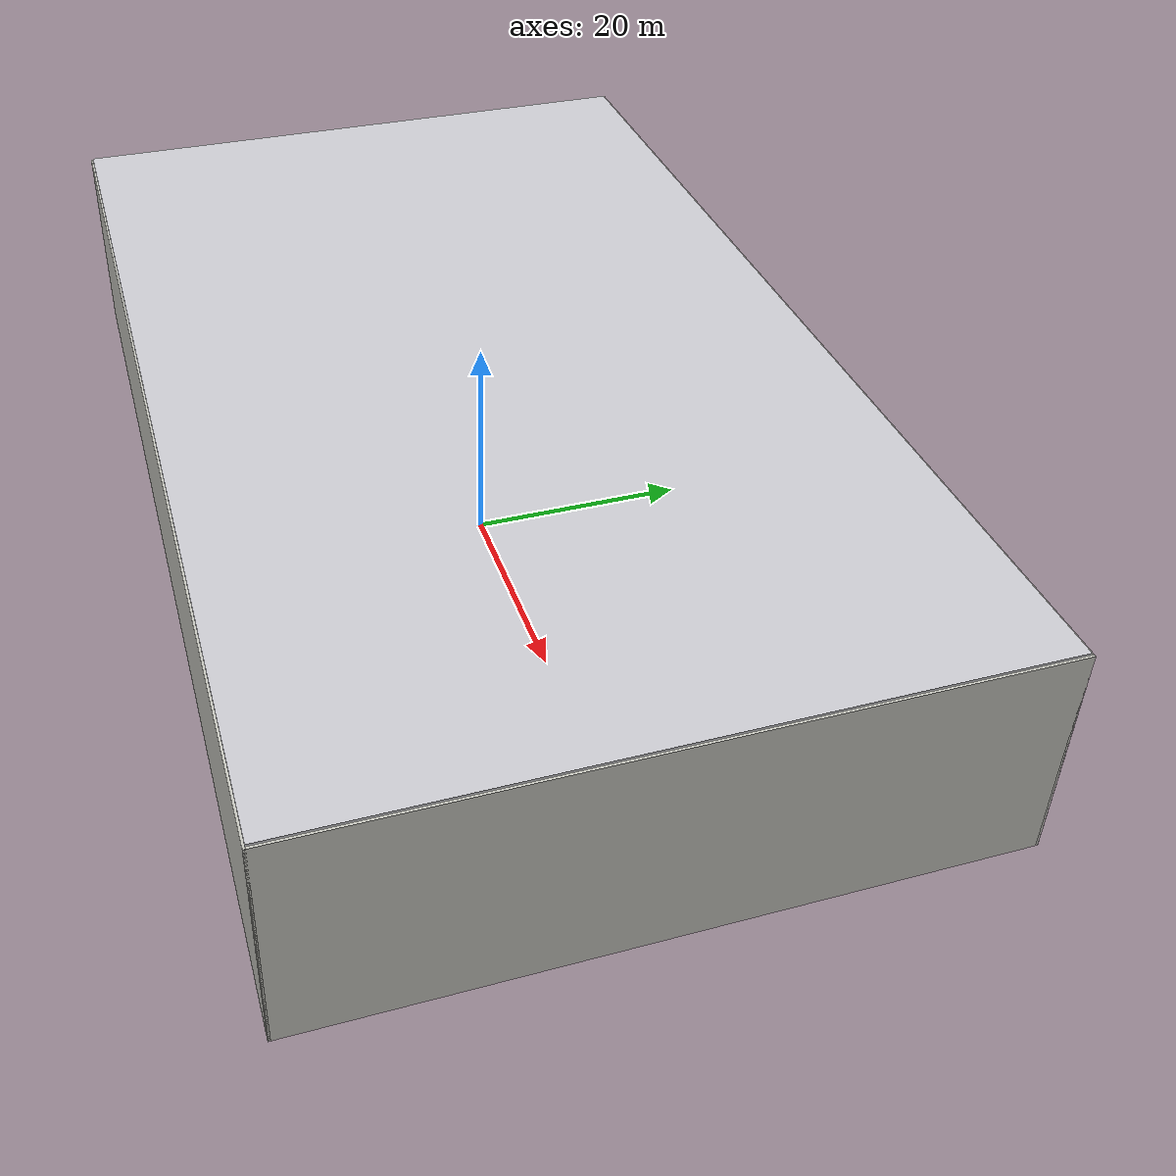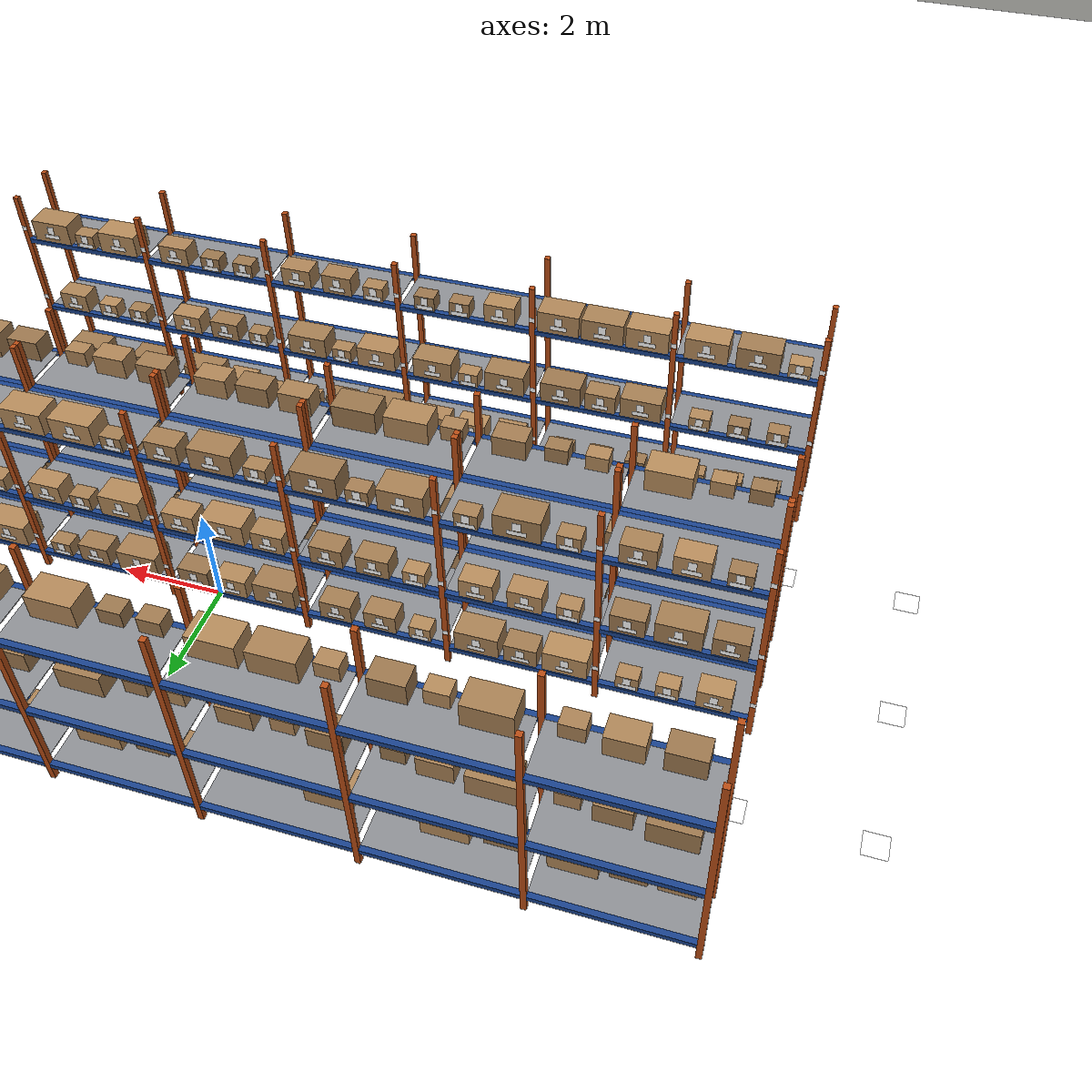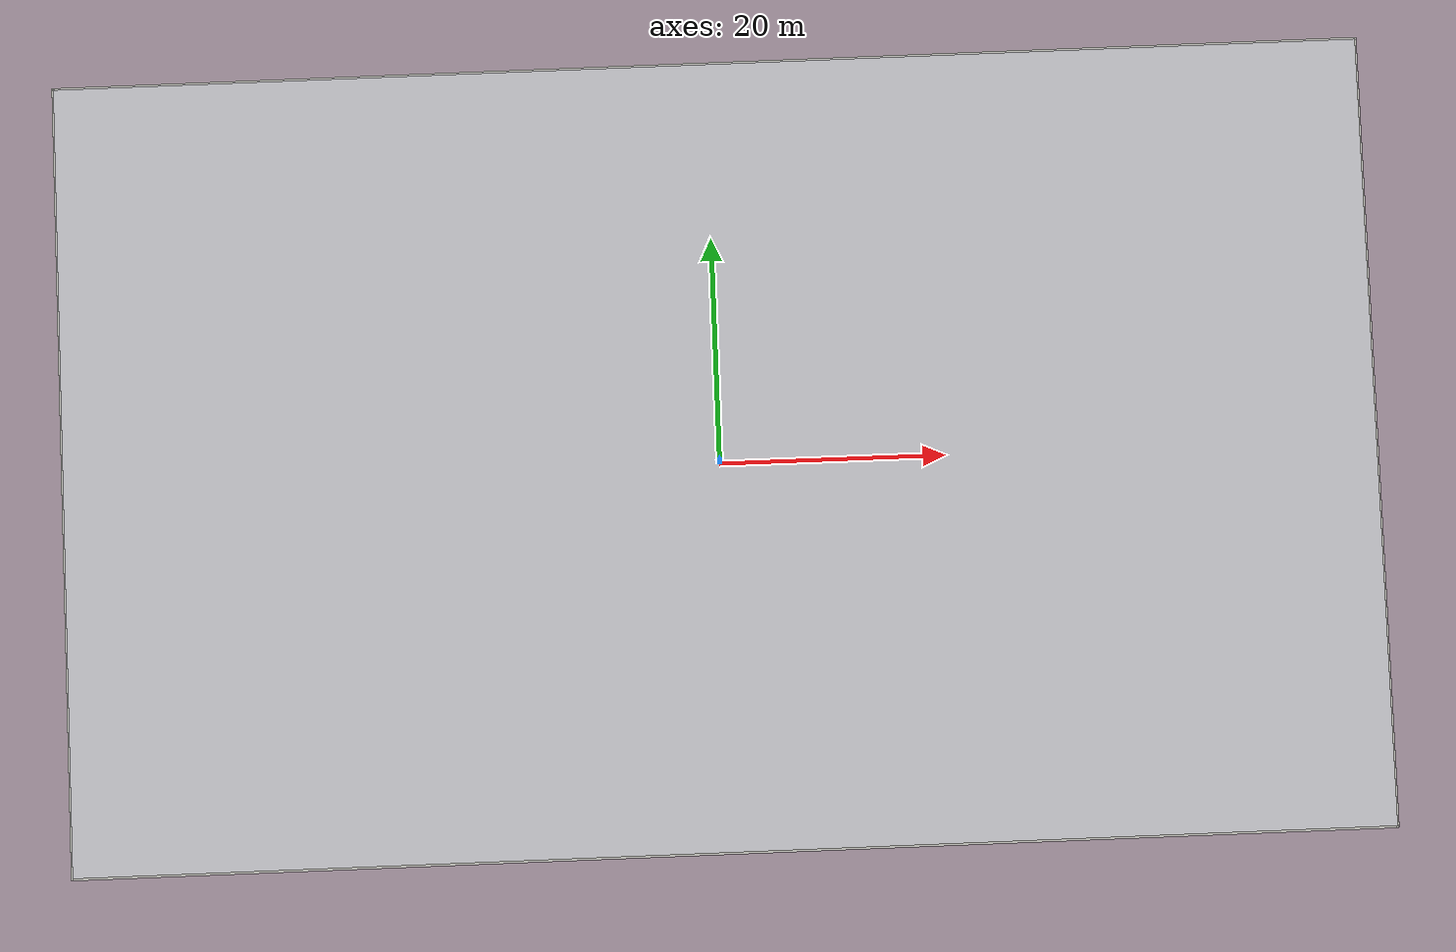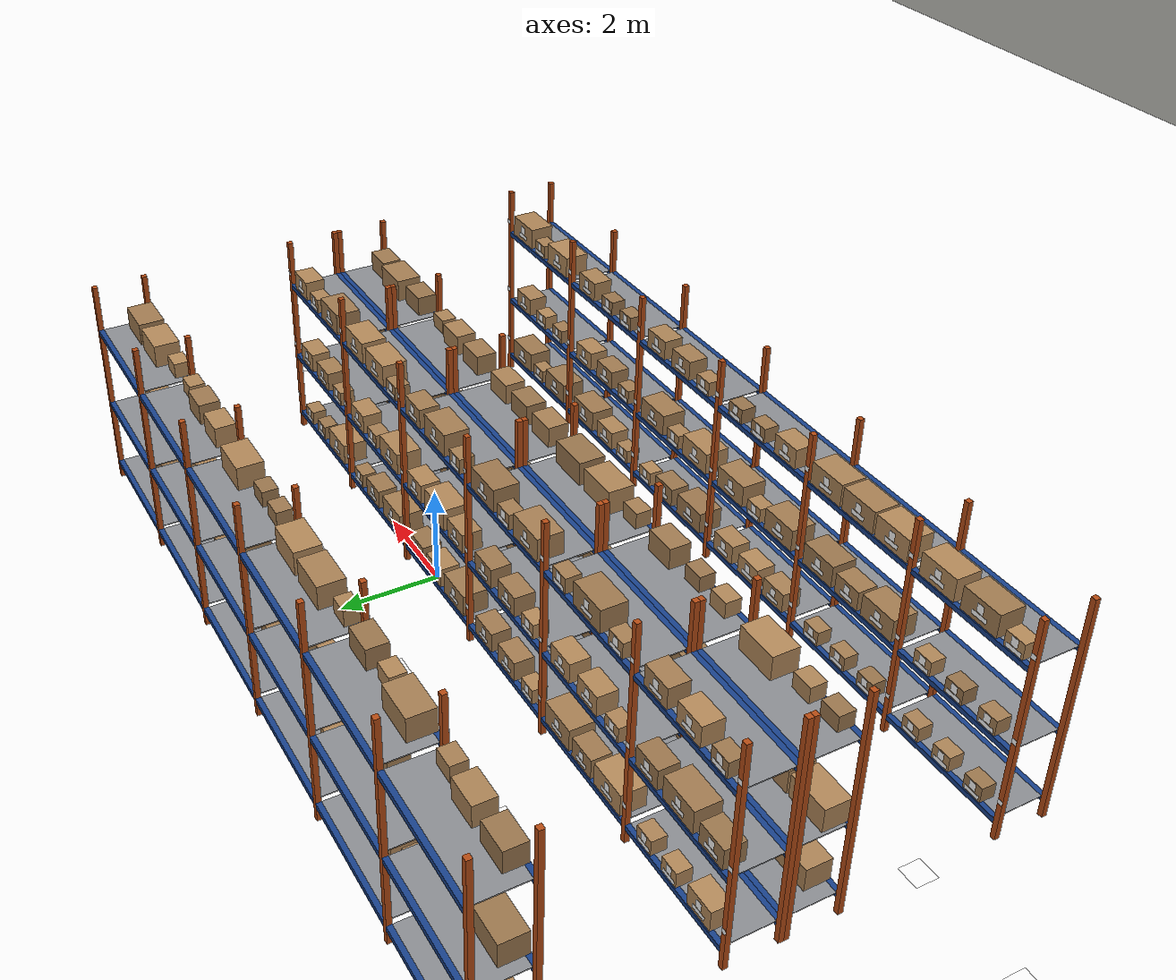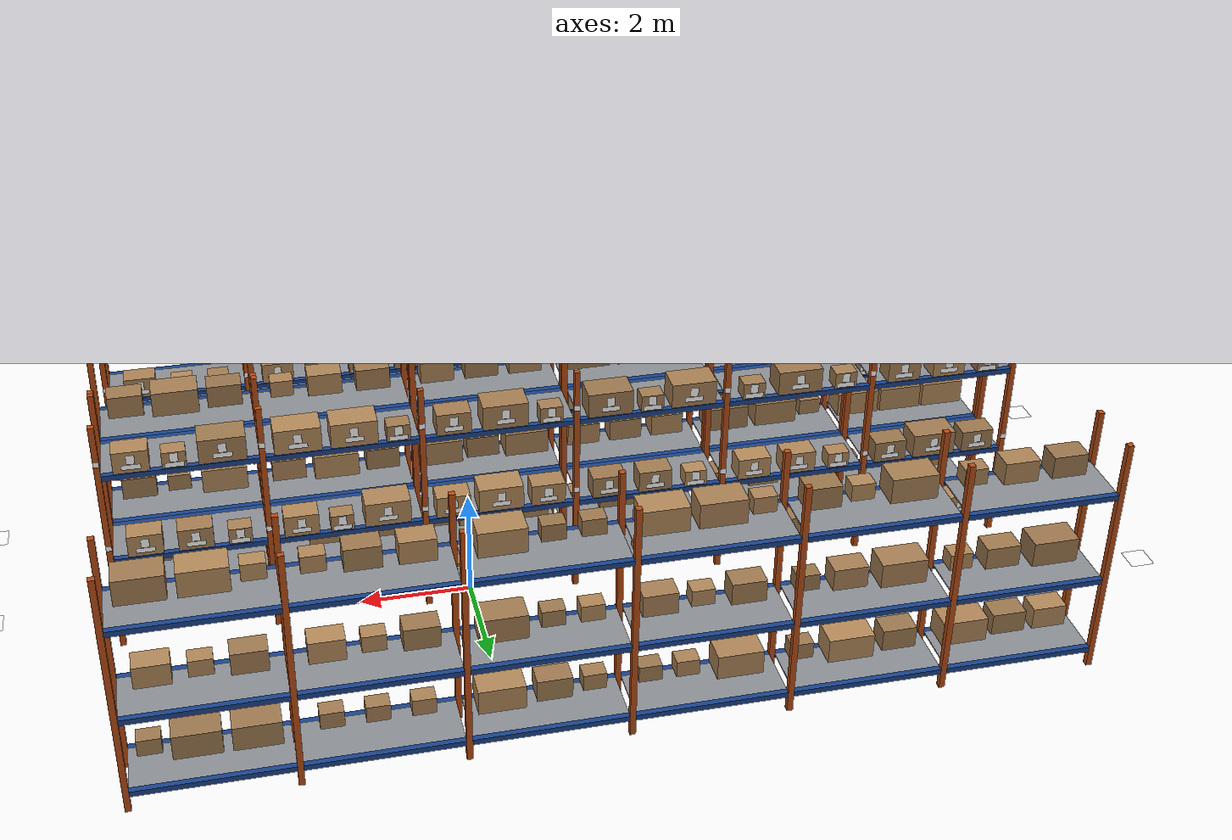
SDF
<?xml version="1.0" encoding="UTF-8"?>
<!-- tools/gen_world.py tarafından üretildi -- elle düzenlemeyin.
     Değişiklik için config/warehouse.yaml'ı düzenleyip yeniden çalıştırın. -->
<sdf version="1.9">
  <world name="warehouse">
    <physics type="ode">
      <max_step_size>0.004</max_step_size>
      <real_time_factor>1.0</real_time_factor>
      <real_time_update_rate>250</real_time_update_rate>
    </physics>
    <gravity>0 0 -9.8</gravity>
    <magnetic_field>6e-06 2.3e-05 -4.2e-05</magnetic_field>
    <atmosphere type="adiabatic"/>

    <scene>
      <grid>false</grid>
      <ambient>0.45 0.45 0.45 1</ambient>
      <background>0.55 0.58 0.62 1</background>
      <shadows>true</shadows>
    </scene>

    <!-- Kapalı ortam: yönlü güneş ışığı yok, aydınlatma tavan lambalarından.
         Yine de PX4'ün NavSat'ı için bir referans konum gerekiyor. -->
    <spherical_coordinates>
      <surface_model>EARTH_WGS84</surface_model>
      <world_frame_orientation>ENU</world_frame_orientation>
      <latitude_deg>41.015137</latitude_deg>
      <longitude_deg>28.979530</longitude_deg>
      <elevation>0</elevation>
    </spherical_coordinates>

  <model name="warehouse_building">
    <static>true</static>
    <link name="structure">
      <visual name="floor_v">
        <pose>0 0 0.002 0 0 0</pose>
        <geometry><mesh><uri>model://warehouse_assets/meshes/floor_tile.obj</uri></mesh></geometry>
        <material>
          <ambient>1 1 1 1</ambient>
          <diffuse>1 1 1 1</diffuse>
          <specular>0.04 0.04 0.04 1</specular>
          <pbr><metal>
            <albedo_map>model://warehouse_assets/materials/textures/floor.png</albedo_map>
            <metalness>0.0</metalness>
            <roughness>0.95</roughness>
          </metal></pbr>
        </material>
      </visual>
      <collision name="floor_c">
        <pose>0 0 -0.1 0 0 0</pose>
        <geometry><box><size>100 60 0.2</size></box></geometry>
      </collision>
      <visual name="ceiling_v">
        <pose>0 0 20.1 0 0 0</pose>
        <geometry><box><size>100 60 0.2</size></box></geometry>
        <material>
          <ambient>0.4 0.4 0.41 1</ambient>
          <diffuse>0.8 0.8 0.82 1</diffuse>
          <specular>0.05 0.05 0.05 1</specular>
          <pbr><metal>
            <metalness>0.0</metalness>
            <roughness>0.9</roughness>
          </metal></pbr>
        </material>
      </visual>
      <collision name="ceiling_c">
        <pose>0 0 20.1 0 0 0</pose>
        <geometry><box><size>100 60 0.2</size></box></geometry>
      </collision>
      <visual name="wall_xp_v">
        <pose>50.1 0 10 0 0 0</pose>
        <geometry><box><size>0.2 60.4 20</size></box></geometry>
        <material>
          <ambient>0.39 0.39 0.375 1</ambient>
          <diffuse>0.78 0.78 0.75 1</diffuse>
          <specular>0.05 0.05 0.05 1</specular>
          <pbr><metal>
            <metalness>0.0</metalness>
            <roughness>0.9</roughness>
          </metal></pbr>
        </material>
      </visual>
      <collision name="wall_xp_c">
        <pose>50.1 0 10 0 0 0</pose>
        <geometry><box><size>0.2 60.4 20</size></box></geometry>
      </collision>
      <visual name="wall_xn_v">
        <pose>-50.1 0 10 0 0 0</pose>
        <geometry><box><size>0.2 60.4 20</size></box></geometry>
        <material>
          <ambient>0.39 0.39 0.375 1</ambient>
          <diffuse>0.78 0.78 0.75 1</diffuse>
          <specular>0.05 0.05 0.05 1</specular>
          <pbr><metal>
            <metalness>0.0</metalness>
            <roughness>0.9</roughness>
          </metal></pbr>
        </material>
      </visual>
      <collision name="wall_xn_c">
        <pose>-50.1 0 10 0 0 0</pose>
        <geometry><box><size>0.2 60.4 20</size></box></geometry>
      </collision>
      <visual name="wall_yp_v">
        <pose>0 30.1 10 0 0 0</pose>
        <geometry><box><size>100.4 0.2 20</size></box></geometry>
        <material>
          <ambient>0.39 0.39 0.375 1</ambient>
          <diffuse>0.78 0.78 0.75 1</diffuse>
          <specular>0.05 0.05 0.05 1</specular>
          <pbr><metal>
            <metalness>0.0</metalness>
            <roughness>0.9</roughness>
          </metal></pbr>
        </material>
      </visual>
      <collision name="wall_yp_c">
        <pose>0 30.1 10 0 0 0</pose>
        <geometry><box><size>100.4 0.2 20</size></box></geometry>
      </collision>
      <visual name="wall_yn_v">
        <pose>0 -30.1 10 0 0 0</pose>
        <geometry><box><size>100.4 0.2 20</size></box></geometry>
        <material>
          <ambient>0.39 0.39 0.375 1</ambient>
          <diffuse>0.78 0.78 0.75 1</diffuse>
          <specular>0.05 0.05 0.05 1</specular>
          <pbr><metal>
            <metalness>0.0</metalness>
            <roughness>0.9</roughness>
          </metal></pbr>
        </material>
      </visual>
      <collision name="wall_yn_c">
        <pose>0 -30.1 10 0 0 0</pose>
        <geometry><box><size>100.4 0.2 20</size></box></geometry>
      </collision>
    </link>
  </model>
  <model name="rack_A">
    <static>true</static>
    <link name="frame">
      <visual name="up_0_f_v">
        <pose>-10 -5.95 2.25 0 0 0</pose>
        <geometry><box><size>0.1 0.1 4.5</size></box></geometry>
        <material>
          <ambient>0.36 0.15 0.04 1</ambient>
          <diffuse>0.72 0.3 0.08 1</diffuse>
          <specular>0.05 0.05 0.05 1</specular>
          <pbr><metal>
            <metalness>0.0</metalness>
            <roughness>0.9</roughness>
          </metal></pbr>
        </material>
      </visual>
      <collision name="up_0_f_c">
        <pose>-10 -5.95 2.25 0 0 0</pose>
        <geometry><box><size>0.1 0.1 4.5</size></box></geometry>
      </collision>
      <visual name="up_0_b_v">
        <pose>-10 -4.95 2.25 0 0 0</pose>
        <geometry><box><size>0.1 0.1 4.5</size></box></geometry>
        <material>
          <ambient>0.36 0.15 0.04 1</ambient>
          <diffuse>0.72 0.3 0.08 1</diffuse>
          <specular>0.05 0.05 0.05 1</specular>
          <pbr><metal>
            <metalness>0.0</metalness>
            <roughness>0.9</roughness>
          </metal></pbr>
        </material>
      </visual>
      <collision name="up_0_b_c">
        <pose>-10 -4.95 2.25 0 0 0</pose>
        <geometry><box><size>0.1 0.1 4.5</size></box></geometry>
      </collision>
      <visual name="up_1_f_v">
        <pose>-7.3 -5.95 2.25 0 0 0</pose>
        <geometry><box><size>0.1 0.1 4.5</size></box></geometry>
        <material>
          <ambient>0.36 0.15 0.04 1</ambient>
          <diffuse>0.72 0.3 0.08 1</diffuse>
          <specular>0.05 0.05 0.05 1</specular>
          <pbr><metal>
            <metalness>0.0</metalness>
            <roughness>0.9</roughness>
          </metal></pbr>
        </material>
      </visual>
      <collision name="up_1_f_c">
        <pose>-7.3 -5.95 2.25 0 0 0</pose>
        <geometry><box><size>0.1 0.1 4.5</size></box></geometry>
      </collision>
      <visual name="up_1_b_v">
        <pose>-7.3 -4.95 2.25 0 0 0</pose>
        <geometry><box><size>0.1 0.1 4.5</size></box></geometry>
        <material>
          <ambient>0.36 0.15 0.04 1</ambient>
          <diffuse>0.72 0.3 0.08 1</diffuse>
          <specular>0.05 0.05 0.05 1</specular>
          <pbr><metal>
            <metalness>0.0</metalness>
            <roughness>0.9</roughness>
          </metal></pbr>
        </material>
      </visual>
      <collision name="up_1_b_c">
        <pose>-7.3 -4.95 2.25 0 0 0</pose>
        <geometry><box><size>0.1 0.1 4.5</size></box></geometry>
      </collision>
      <visual name="up_2_f_v">
        <pose>-4.6 -5.95 2.25 0 0 0</pose>
        <geometry><box><size>0.1 0.1 4.5</size></box></geometry>
        <material>
          <ambient>0.36 0.15 0.04 1</ambient>
          <diffuse>0.72 0.3 0.08 1</diffuse>
          <specular>0.05 0.05 0.05 1</specular>
          <pbr><metal>
            <metalness>0.0</metalness>
            <roughness>0.9</roughness>
          </metal></pbr>
        </material>
      </visual>
      <collision name="up_2_f_c">
        <pose>-4.6 -5.95 2.25 0 0 0</pose>
        <geometry><box><size>0.1 0.1 4.5</size></box></geometry>
      </collision>
      <visual name="up_2_b_v">
        <pose>-4.6 -4.95 2.25 0 0 0</pose>
        <geometry><box><size>0.1 0.1 4.5</size></box></geometry>
        <material>
          <ambient>0.36 0.15 0.04 1</ambient>
          <diffuse>0.72 0.3 0.08 1</diffuse>
          <specular>0.05 0.05 0.05 1</specular>
          <pbr><metal>
            <metalness>0.0</metalness>
            <roughness>0.9</roughness>
          </metal></pbr>
        </material>
      </visual>
      <collision name="up_2_b_c">
        <pose>-4.6 -4.95 2.25 0 0 0</pose>
        <geometry><box><size>0.1 0.1 4.5</size></box></geometry>
      </collision>
      <visual name="up_3_f_v">
        <pose>-1.9 -5.95 2.25 0 0 0</pose>
        <geometry><box><size>0.1 0.1 4.5</size></box></geometry>
        <material>
          <ambient>0.36 0.15 0.04 1</ambient>
          <diffuse>0.72 0.3 0.08 1</diffuse>
          <specular>0.05 0.05 0.05 1</specular>
          <pbr><metal>
            <metalness>0.0</metalness>
            <roughness>0.9</roughness>
          </metal></pbr>
        </material>
      </visual>
      <collision name="up_3_f_c">
        <pose>-1.9 -5.95 2.25 0 0 0</pose>
        <geometry><box><size>0.1 0.1 4.5</size></box></geometry>
      </collision>
      <visual name="up_3_b_v">
        <pose>-1.9 -4.95 2.25 0 0 0</pose>
        <geometry><box><size>0.1 0.1 4.5</size></box></geometry>
        <material>
          <ambient>0.36 0.15 0.04 1</ambient>
          <diffuse>0.72 0.3 0.08 1</diffuse>
          <specular>0.05 0.05 0.05 1</specular>
          <pbr><metal>
            <metalness>0.0</metalness>
            <roughness>0.9</roughness>
          </metal></pbr>
        </material>
      </visual>
      <collision name="up_3_b_c">
        <pose>-1.9 -4.95 2.25 0 0 0</pose>
        <geometry><box><size>0.1 0.1 4.5</size></box></geometry>
      </collision>
      <visual name="up_4_f_v">
        <pose>0.8 -5.95 2.25 0 0 0</pose>
        <geometry><box><size>0.1 0.1 4.5</size></box></geometry>
        <material>
          <ambient>0.36 0.15 0.04 1</ambient>
          <diffuse>0.72 0.3 0.08 1</diffuse>
          <specular>0.05 0.05 0.05 1</specular>
          <pbr><metal>
            <metalness>0.0</metalness>
            <roughness>0.9</roughness>
          </metal></pbr>
        </material>
      </visual>
      <collision name="up_4_f_c">
        <pose>0.8 -5.95 2.25 0 0 0</pose>
        <geometry><box><size>0.1 0.1 4.5</size></box></geometry>
      </collision>
      <visual name="up_4_b_v">
        <pose>0.8 -4.95 2.25 0 0 0</pose>
        <geometry><box><size>0.1 0.1 4.5</size></box></geometry>
        <material>
          <ambient>0.36 0.15 0.04 1</ambient>
          <diffuse>0.72 0.3 0.08 1</diffuse>
          <specular>0.05 0.05 0.05 1</specular>
          <pbr><metal>
            <metalness>0.0</metalness>
            <roughness>0.9</roughness>
          </metal></pbr>
        </material>
      </visual>
      <collision name="up_4_b_c">
        <pose>0.8 -4.95 2.25 0 0 0</pose>
        <geometry><box><size>0.1 0.1 4.5</size></box></geometry>
      </collision>
      <visual name="up_5_f_v">
        <pose>3.5 -5.95 2.25 0 0 0</pose>
        <geometry><box><size>0.1 0.1 4.5</size></box></geometry>
        <material>
          <ambient>0.36 0.15 0.04 1</ambient>
          <diffuse>0.72 0.3 0.08 1</diffuse>
          <specular>0.05 0.05 0.05 1</specular>
          <pbr><metal>
            <metalness>0.0</metalness>
            <roughness>0.9</roughness>
          </metal></pbr>
        </material>
      </visual>
      <collision name="up_5_f_c">
        <pose>3.5 -5.95 2.25 0 0 0</pose>
        <geometry><box><size>0.1 0.1 4.5</size></box></geometry>
      </collision>
      <visual name="up_5_b_v">
        <pose>3.5 -4.95 2.25 0 0 0</pose>
        <geometry><box><size>0.1 0.1 4.5</size></box></geometry>
        <material>
          <ambient>0.36 0.15 0.04 1</ambient>
          <diffuse>0.72 0.3 0.08 1</diffuse>
          <specular>0.05 0.05 0.05 1</specular>
          <pbr><metal>
            <metalness>0.0</metalness>
            <roughness>0.9</roughness>
          </metal></pbr>
        </material>
      </visual>
      <collision name="up_5_b_c">
        <pose>3.5 -4.95 2.25 0 0 0</pose>
        <geometry><box><size>0.1 0.1 4.5</size></box></geometry>
      </collision>
      <visual name="up_6_f_v">
        <pose>6.2 -5.95 2.25 0 0 0</pose>
        <geometry><box><size>0.1 0.1 4.5</size></box></geometry>
        <material>
          <ambient>0.36 0.15 0.04 1</ambient>
          <diffuse>0.72 0.3 0.08 1</diffuse>
          <specular>0.05 0.05 0.05 1</specular>
          <pbr><metal>
            <metalness>0.0</metalness>
            <roughness>0.9</roughness>
          </metal></pbr>
        </material>
      </visual>
      <collision name="up_6_f_c">
        <pose>6.2 -5.95 2.25 0 0 0</pose>
        <geometry><box><size>0.1 0.1 4.5</size></box></geometry>
      </collision>
      <visual name="up_6_b_v">
        <pose>6.2 -4.95 2.25 0 0 0</pose>
        <geometry><box><size>0.1 0.1 4.5</size></box></geometry>
        <material>
          <ambient>0.36 0.15 0.04 1</ambient>
          <diffuse>0.72 0.3 0.08 1</diffuse>
          <specular>0.05 0.05 0.05 1</specular>
          <pbr><metal>
            <metalness>0.0</metalness>
            <roughness>0.9</roughness>
          </metal></pbr>
        </material>
      </visual>
      <collision name="up_6_b_c">
        <pose>6.2 -4.95 2.25 0 0 0</pose>
        <geometry><box><size>0.1 0.1 4.5</size></box></geometry>
      </collision>
      <visual name="beam_0_0_f_v">
        <pose>-8.65 -5.95 0.35 0 0 0</pose>
        <geometry><box><size>2.6 0.1 0.1</size></box></geometry>
        <material>
          <ambient>0.05 0.13 0.275 1</ambient>
          <diffuse>0.1 0.26 0.55 1</diffuse>
          <specular>0.05 0.05 0.05 1</specular>
          <pbr><metal>
            <metalness>0.0</metalness>
            <roughness>0.9</roughness>
          </metal></pbr>
        </material>
      </visual>
      <collision name="beam_0_0_f_c">
        <pose>-8.65 -5.95 0.35 0 0 0</pose>
        <geometry><box><size>2.6 0.1 0.1</size></box></geometry>
      </collision>
      <visual name="beam_0_0_b_v">
        <pose>-8.65 -4.95 0.35 0 0 0</pose>
        <geometry><box><size>2.6 0.1 0.1</size></box></geometry>
        <material>
          <ambient>0.05 0.13 0.275 1</ambient>
          <diffuse>0.1 0.26 0.55 1</diffuse>
          <specular>0.05 0.05 0.05 1</specular>
          <pbr><metal>
            <metalness>0.0</metalness>
            <roughness>0.9</roughness>
          </metal></pbr>
        </material>
      </visual>
      <collision name="beam_0_0_b_c">
        <pose>-8.65 -4.95 0.35 0 0 0</pose>
        <geometry><box><size>2.6 0.1 0.1</size></box></geometry>
      </collision>
      <visual name="deck_0_0_v">
        <pose>-8.65 -5.45 0.39 0 0 0</pose>
        <geometry><box><size>2.6 0.9 0.02</size></box></geometry>
        <material>
          <ambient>0.275 0.28 0.29 1</ambient>
          <diffuse>0.55 0.56 0.58 1</diffuse>
          <specular>0.05 0.05 0.05 1</specular>
          <pbr><metal>
            <metalness>0.0</metalness>
            <roughness>0.9</roughness>
          </metal></pbr>
        </material>
      </visual>
      <collision name="deck_0_0_c">
        <pose>-8.65 -5.45 0.39 0 0 0</pose>
        <geometry><box><size>2.6 0.9 0.02</size></box></geometry>
      </collision>
      <visual name="beam_0_1_f_v">
        <pose>-5.95 -5.95 0.35 0 0 0</pose>
        <geometry><box><size>2.6 0.1 0.1</size></box></geometry>
        <material>
          <ambient>0.05 0.13 0.275 1</ambient>
          <diffuse>0.1 0.26 0.55 1</diffuse>
          <specular>0.05 0.05 0.05 1</specular>
          <pbr><metal>
            <metalness>0.0</metalness>
            <roughness>0.9</roughness>
          </metal></pbr>
        </material>
      </visual>
      <collision name="beam_0_1_f_c">
        <pose>-5.95 -5.95 0.35 0 0 0</pose>
        <geometry><box><size>2.6 0.1 0.1</size></box></geometry>
      </collision>
      <visual name="beam_0_1_b_v">
        <pose>-5.95 -4.95 0.35 0 0 0</pose>
        <geometry><box><size>2.6 0.1 0.1</size></box></geometry>
        <material>
          <ambient>0.05 0.13 0.275 1</ambient>
          <diffuse>0.1 0.26 0.55 1</diffuse>
          <specular>0.05 0.05 0.05 1</specular>
          <pbr><metal>
            <metalness>0.0</metalness>
            <roughness>0.9</roughness>
          </metal></pbr>
        </material>
      </visual>
      <collision name="beam_0_1_b_c">
        <pose>-5.95 -4.95 0.35 0 0 0</pose>
        <geometry><box><size>2.6 0.1 0.1</size></box></geometry>
      </collision>
      <visual name="deck_0_1_v">
        <pose>-5.95 -5.45 0.39 0 0 0</pose>
        <geometry><box><size>2.6 0.9 0.02</size></box></geometry>
        <material>
          <ambient>0.275 0.28 0.29 1</ambient>
          <diffuse>0.55 0.56 0.58 1</diffuse>
          <specular>0.05 0.05 0.05 1</specular>
          <pbr><metal>
            <metalness>0.0</metalness>
            <roughness>0.9</roughness>
          </metal></pbr>
        </material>
      </visual>
      <collision name="deck_0_1_c">
        <pose>-5.95 -5.45 0.39 0 0 0</pose>
        <geometry><box><size>2.6 0.9 0.02</size></box></geometry>
      </collision>
      <visual name="beam_0_2_f_v">
        <pose>-3.25 -5.95 0.35 0 0 0</pose>
        <geometry><box><size>2.6 0.1 0.1</size></box></geometry>
        <material>
          <ambient>0.05 0.13 0.275 1</ambient>
          <diffuse>0.1 0.26 0.55 1</diffuse>
          <specular>0.05 0.05 0.05 1</specular>
          <pbr><metal>
            <metalness>0.0</metalness>
            <roughness>0.9</roughness>
          </metal></pbr>
        </material>
      </visual>
      <collision name="beam_0_2_f_c">
        <pose>-3.25 -5.95 0.35 0 0 0</pose>
        <geometry><box><size>2.6 0.1 0.1</size></box></geometry>
      </collision>
      <visual name="beam_0_2_b_v">
        <pose>-3.25 -4.95 0.35 0 0 0</pose>
        <geometry><box><size>2.6 0.1 0.1</size></box></geometry>
        <material>
          <ambient>0.05 0.13 0.275 1</ambient>
          <diffuse>0.1 0.26 0.55 1</diffuse>
          <specular>0.05 0.05 0.05 1</specular>
          <pbr><metal>
            <metalness>0.0</metalness>
            <roughness>0.9</roughness>
          </metal></pbr>
        </material>
      </visual>
      <collision name="beam_0_2_b_c">
        <pose>-3.25 -4.95 0.35 0 0 0</pose>
        <geometry><box><size>2.6 0.1 0.1</size></box></geometry>
      </collision>
      <visual name="deck_0_2_v">
        <pose>-3.25 -5.45 0.39 0 0 0</pose>
        <geometry><box><size>2.6 0.9 0.02</size></box></geometry>
        <material>
          <ambient>0.275 0.28 0.29 1</ambient>
          <diffuse>0.55 0.56 0.58 1</diffuse>
          <specular>0.05 0.05 0.05 1</specular>
          <pbr><metal>
            <metalness>0.0</metalness>
            <roughness>0.9</roughness>
          </metal></pbr>
        </material>
      </visual>
      <collision name="deck_0_2_c">
        <pose>-3.25 -5.45 0.39 0 0 0</pose>
        <geometry><box><size>2.6 0.9 0.02</size></box></geometry>
      </collision>
      <visual name="beam_0_3_f_v">
        <pose>-0.55 -5.95 0.35 0 0 0</pose>
        <geometry><box><size>2.6 0.1 0.1</size></box></geometry>
        <material>
          <ambient>0.05 0.13 0.275 1</ambient>
          <diffuse>0.1 0.26 0.55 1</diffuse>
          <specular>0.05 0.05 0.05 1</specular>
          <pbr><metal>
            <metalness>0.0</metalness>
            <roughness>0.9</roughness>
          </metal></pbr>
        </material>
      </visual>
      <collision name="beam_0_3_f_c">
        <pose>-0.55 -5.95 0.35 0 0 0</pose>
        <geometry><box><size>2.6 0.1 0.1</size></box></geometry>
      </collision>
      <visual name="beam_0_3_b_v">
        <pose>-0.55 -4.95 0.35 0 0 0</pose>
        <geometry><box><size>2.6 0.1 0.1</size></box></geometry>
        <material>
          <ambient>0.05 0.13 0.275 1</ambient>
          <diffuse>0.1 0.26 0.55 1</diffuse>
          <specular>0.05 0.05 0.05 1</specular>
          <pbr><metal>
            <metalness>0.0</metalness>
            <roughness>0.9</roughness>
          </metal></pbr>
        </material>
      </visual>
      <collision name="beam_0_3_b_c">
        <pose>-0.55 -4.95 0.35 0 0 0</pose>
        <geometry><box><size>2.6 0.1 0.1</size></box></geometry>
      </collision>
      <visual name="deck_0_3_v">
        <pose>-0.55 -5.45 0.39 0 0 0</pose>
        <geometry><box><size>2.6 0.9 0.02</size></box></geometry>
        <material>
          <ambient>0.275 0.28 0.29 1</ambient>
          <diffuse>0.55 0.56 0.58 1</diffuse>
          <specular>0.05 0.05 0.05 1</specular>
          <pbr><metal>
            <metalness>0.0</metalness>
            <roughness>0.9</roughness>
          </metal></pbr>
        </material>
      </visual>
      <collision name="deck_0_3_c">
        <pose>-0.55 -5.45 0.39 0 0 0</pose>
        <geometry><box><size>2.6 0.9 0.02</size></box></geometry>
      </collision>
      <visual name="beam_0_4_f_v">
        <pose>2.15 -5.95 0.35 0 0 0</pose>
        <geometry><box><size>2.6 0.1 0.1</size></box></geometry>
        <material>
          <ambient>0.05 0.13 0.275 1</ambient>
          <diffuse>0.1 0.26 0.55 1</diffuse>
          <specular>0.05 0.05 0.05 1</specular>
          <pbr><metal>
            <metalness>0.0</metalness>
            <roughness>0.9</roughness>
          </metal></pbr>
        </material>
      </visual>
      <collision name="beam_0_4_f_c">
        <pose>2.15 -5.95 0.35 0 0 0</pose>
        <geometry><box><size>2.6 0.1 0.1</size></box></geometry>
      </collision>
      <visual name="beam_0_4_b_v">
        <pose>2.15 -4.95 0.35 0 0 0</pose>
        <geometry><box><size>2.6 0.1 0.1</size></box></geometry>
        <material>
          <ambient>0.05 0.13 0.275 1</ambient>
          <diffuse>0.1 0.26 0.55 1</diffuse>
          <specular>0.05 0.05 0.05 1</specular>
          <pbr><metal>
            <metalness>0.0</metalness>
            <roughness>0.9</roughness>
          </metal></pbr>
        </material>
      </visual>
      <collision name="beam_0_4_b_c">
        <pose>2.15 -4.95 0.35 0 0 0</pose>
        <geometry><box><size>2.6 0.1 0.1</size></box></geometry>
      </collision>
      <visual name="deck_0_4_v">
        <pose>2.15 -5.45 0.39 0 0 0</pose>
        <geometry><box><size>2.6 0.9 0.02</size></box></geometry>
        <material>
          <ambient>0.275 0.28 0.29 1</ambient>
          <diffuse>0.55 0.56 0.58 1</diffuse>
          <specular>0.05 0.05 0.05 1</specular>
          <pbr><metal>
            <metalness>0.0</metalness>
            <roughness>0.9</roughness>
          </metal></pbr>
        </material>
      </visual>
      <collision name="deck_0_4_c">
        <pose>2.15 -5.45 0.39 0 0 0</pose>
        <geometry><box><size>2.6 0.9 0.02</size></box></geometry>
      </collision>
      <visual name="beam_0_5_f_v">
        <pose>4.85 -5.95 0.35 0 0 0</pose>
        <geometry><box><size>2.6 0.1 0.1</size></box></geometry>
        <material>
          <ambient>0.05 0.13 0.275 1</ambient>
          <diffuse>0.1 0.26 0.55 1</diffuse>
          <specular>0.05 0.05 0.05 1</specular>
          <pbr><metal>
            <metalness>0.0</metalness>
            <roughness>0.9</roughness>
          </metal></pbr>
        </material>
      </visual>
      <collision name="beam_0_5_f_c">
        <pose>4.85 -5.95 0.35 0 0 0</pose>
        <geometry><box><size>2.6 0.1 0.1</size></box></geometry>
      </collision>
      <visual name="beam_0_5_b_v">
        <pose>4.85 -4.95 0.35 0 0 0</pose>
        <geometry><box><size>2.6 0.1 0.1</size></box></geometry>
        <material>
          <ambient>0.05 0.13 0.275 1</ambient>
          <diffuse>0.1 0.26 0.55 1</diffuse>
          <specular>0.05 0.05 0.05 1</specular>
          <pbr><metal>
            <metalness>0.0</metalness>
            <roughness>0.9</roughness>
          </metal></pbr>
        </material>
      </visual>
      <collision name="beam_0_5_b_c">
        <pose>4.85 -4.95 0.35 0 0 0</pose>
        <geometry><box><size>2.6 0.1 0.1</size></box></geometry>
      </collision>
      <visual name="deck_0_5_v">
        <pose>4.85 -5.45 0.39 0 0 0</pose>
        <geometry><box><size>2.6 0.9 0.02</size></box></geometry>
        <material>
          <ambient>0.275 0.28 0.29 1</ambient>
          <diffuse>0.55 0.56 0.58 1</diffuse>
          <specular>0.05 0.05 0.05 1</specular>
          <pbr><metal>
            <metalness>0.0</metalness>
            <roughness>0.9</roughness>
          </metal></pbr>
        </material>
      </visual>
      <collision name="deck_0_5_c">
        <pose>4.85 -5.45 0.39 0 0 0</pose>
        <geometry><box><size>2.6 0.9 0.02</size></box></geometry>
      </collision>
      <visual name="beam_1_0_f_v">
        <pose>-8.65 -5.95 1.8 0 0 0</pose>
        <geometry><box><size>2.6 0.1 0.1</size></box></geometry>
        <material>
          <ambient>0.05 0.13 0.275 1</ambient>
          <diffuse>0.1 0.26 0.55 1</diffuse>
          <specular>0.05 0.05 0.05 1</specular>
          <pbr><metal>
            <metalness>0.0</metalness>
            <roughness>0.9</roughness>
          </metal></pbr>
        </material>
      </visual>
      <collision name="beam_1_0_f_c">
        <pose>-8.65 -5.95 1.8 0 0 0</pose>
        <geometry><box><size>2.6 0.1 0.1</size></box></geometry>
      </collision>
      <visual name="beam_1_0_b_v">
        <pose>-8.65 -4.95 1.8 0 0 0</pose>
        <geometry><box><size>2.6 0.1 0.1</size></box></geometry>
        <material>
          <ambient>0.05 0.13 0.275 1</ambient>
          <diffuse>0.1 0.26 0.55 1</diffuse>
          <specular>0.05 0.05 0.05 1</specular>
          <pbr><metal>
            <metalness>0.0</metalness>
            <roughness>0.9</roughness>
          </metal></pbr>
        </material>
      </visual>
      <collision name="beam_1_0_b_c">
        <pose>-8.65 -4.95 1.8 0 0 0</pose>
        <geometry><box><size>2.6 0.1 0.1</size></box></geometry>
      </collision>
      <visual name="deck_1_0_v">
        <pose>-8.65 -5.45 1.84 0 0 0</pose>
        <geometry><box><size>2.6 0.9 0.02</size></box></geometry>
        <material>
          <ambient>0.275 0.28 0.29 1</ambient>
          <diffuse>0.55 0.56 0.58 1</diffuse>
          <specular>0.05 0.05 0.05 1</specular>
          <pbr><metal>
            <metalness>0.0</metalness>
            <roughness>0.9</roughness>
          </metal></pbr>
        </material>
      </visual>
      <collision name="deck_1_0_c">
        <pose>-8.65 -5.45 1.84 0 0 0</pose>
        <geometry><box><size>2.6 0.9 0.02</size></box></geometry>
      </collision>
      <visual name="beam_1_1_f_v">
        <pose>-5.95 -5.95 1.8 0 0 0</pose>
        <geometry><box><size>2.6 0.1 0.1</size></box></geometry>
        <material>
          <ambient>0.05 0.13 0.275 1</ambient>
          <diffuse>0.1 0.26 0.55 1</diffuse>
          <specular>0.05 0.05 0.05 1</specular>
          <pbr><metal>
            <metalness>0.0</metalness>
            <roughness>0.9</roughness>
          </metal></pbr>
        </material>
      </visual>
      <collision name="beam_1_1_f_c">
        <pose>-5.95 -5.95 1.8 0 0 0</pose>
        <geometry><box><size>2.6 0.1 0.1</size></box></geometry>
      </collision>
      <visual name="beam_1_1_b_v">
        <pose>-5.95 -4.95 1.8 0 0 0</pose>
        <geometry><box><size>2.6 0.1 0.1</size></box></geometry>
        <material>
          <ambient>0.05 0.13 0.275 1</ambient>
          <diffuse>0.1 0.26 0.55 1</diffuse>
          <specular>0.05 0.05 0.05 1</specular>
          <pbr><metal>
            <metalness>0.0</metalness>
            <roughness>0.9</roughness>
          </metal></pbr>
        </material>
      </visual>
      <collision name="beam_1_1_b_c">
        <pose>-5.95 -4.95 1.8 0 0 0</pose>
        <geometry><box><size>2.6 0.1 0.1</size></box></geometry>
      </collision>
      <visual name="deck_1_1_v">
        <pose>-5.95 -5.45 1.84 0 0 0</pose>
        <geometry><box><size>2.6 0.9 0.02</size></box></geometry>
        <material>
          <ambient>0.275 0.28 0.29 1</ambient>
          <diffuse>0.55 0.56 0.58 1</diffuse>
          <specular>0.05 0.05 0.05 1</specular>
          <pbr><metal>
            <metalness>0.0</metalness>
            <roughness>0.9</roughness>
          </metal></pbr>
        </material>
      </visual>
      <collision name="deck_1_1_c">
        <pose>-5.95 -5.45 1.84 0 0 0</pose>
        <geometry><box><size>2.6 0.9 0.02</size></box></geometry>
      </collision>
      <visual name="beam_1_2_f_v">
        <pose>-3.25 -5.95 1.8 0 0 0</pose>
        <geometry><box><size>2.6 0.1 0.1</size></box></geometry>
        <material>
          <ambient>0.05 0.13 0.275 1</ambient>
          <diffuse>0.1 0.26 0.55 1</diffuse>
          <specular>0.05 0.05 0.05 1</specular>
          <pbr><metal>
            <metalness>0.0</metalness>
            <roughness>0.9</roughness>
          </metal></pbr>
        </material>
      </visual>
      <collision name="beam_1_2_f_c">
        <pose>-3.25 -5.95 1.8 0 0 0</pose>
        <geometry><box><size>2.6 0.1 0.1</size></box></geometry>
      </collision>
      <visual name="beam_1_2_b_v">
        <pose>-3.25 -4.95 1.8 0 0 0</pose>
        <geometry><box><size>2.6 0.1 0.1</size></box></geometry>
        <material>
          <ambient>0.05 0.13 0.275 1</ambient>
          <diffuse>0.1 0.26 0.55 1</diffuse>
          <specular>0.05 0.05 0.05 1</specular>
          <pbr><metal>
            <metalness>0.0</metalness>
            <roughness>0.9</roughness>
          </metal></pbr>
        </material>
      </visual>
      <collision name="beam_1_2_b_c">
        <pose>-3.25 -4.95 1.8 0 0 0</pose>
        <geometry><box><size>2.6 0.1 0.1</size></box></geometry>
      </collision>
      <visual name="deck_1_2_v">
        <pose>-3.25 -5.45 1.84 0 0 0</pose>
        <geometry><box><size>2.6 0.9 0.02</size></box></geometry>
        <material>
          <ambient>0.275 0.28 0.29 1</ambient>
          <diffuse>0.55 0.56 0.58 1</diffuse>
          <specular>0.05 0.05 0.05 1</specular>
          <pbr><metal>
            <metalness>0.0</metalness>
            <roughness>0.9</roughness>
          </metal></pbr>
        </material>
      </visual>
      <collision name="deck_1_2_c">
        <pose>-3.25 -5.45 1.84 0 0 0</pose>
        <geometry><box><size>2.6 0.9 0.02</size></box></geometry>
      </collision>
      <visual name="beam_1_3_f_v">
        <pose>-0.55 -5.95 1.8 0 0 0</pose>
        <geometry><box><size>2.6 0.1 0.1</size></box></geometry>
        <material>
          <ambient>0.05 0.13 0.275 1</ambient>
          <diffuse>0.1 0.26 0.55 1</diffuse>
          <specular>0.05 0.05 0.05 1</specular>
          <pbr><metal>
            <metalness>0.0</metalness>
            <roughness>0.9</roughness>
          </metal></pbr>
        </material>
      </visual>
      <collision name="beam_1_3_f_c">
        <pose>-0.55 -5.95 1.8 0 0 0</pose>
        <geometry><box><size>2.6 0.1 0.1</size></box></geometry>
      </collision>
      <visual name="beam_1_3_b_v">
        <pose>-0.55 -4.95 1.8 0 0 0</pose>
        <geometry><box><size>2.6 0.1 0.1</size></box></geometry>
        <material>
          <ambient>0.05 0.13 0.275 1</ambient>
          <diffuse>0.1 0.26 0.55 1</diffuse>
          <specular>0.05 0.05 0.05 1</specular>
          <pbr><metal>
            <metalness>0.0</metalness>
            <roughness>0.9</roughness>
          </metal></pbr>
        </material>
      </visual>
      <collision name="beam_1_3_b_c">
        <pose>-0.55 -4.95 1.8 0 0 0</pose>
        <geometry><box><size>2.6 0.1 0.1</size></box></geometry>
      </collision>
      <visual name="deck_1_3_v">
        <pose>-0.55 -5.45 1.84 0 0 0</pose>
        <geometry><box><size>2.6 0.9 0.02</size></box></geometry>
        <material>
          <ambient>0.275 0.28 0.29 1</ambient>
          <diffuse>0.55 0.56 0.58 1</diffuse>
          <specular>0.05 0.05 0.05 1</specular>
          <pbr><metal>
            <metalness>0.0</metalness>
            <roughness>0.9</roughness>
          </metal></pbr>
        </material>
      </visual>
      <collision name="deck_1_3_c">
        <pose>-0.55 -5.45 1.84 0 0 0</pose>
        <geometry><box><size>2.6 0.9 0.02</size></box></geometry>
      </collision>
      <visual name="beam_1_4_f_v">
        <pose>2.15 -5.95 1.8 0 0 0</pose>
        <geometry><box><size>2.6 0.1 0.1</size></box></geometry>
        <material>
          <ambient>0.05 0.13 0.275 1</ambient>
          <diffuse>0.1 0.26 0.55 1</diffuse>
          <specular>0.05 0.05 0.05 1</specular>
          <pbr><metal>
            <metalness>0.0</metalness>
            <roughness>0.9</roughness>
          </metal></pbr>
        </material>
      </visual>
      <collision name="beam_1_4_f_c">
        <pose>2.15 -5.95 1.8 0 0 0</pose>
        <geometry><box><size>2.6 0.1 0.1</size></box></geometry>
      </collision>
      <visual name="beam_1_4_b_v">
        <pose>2.15 -4.95 1.8 0 0 0</pose>
        <geometry><box><size>2.6 0.1 0.1</size></box></geometry>
        <material>
          <ambient>0.05 0.13 0.275 1</ambient>
          <diffuse>0.1 0.26 0.55 1</diffuse>
          <specular>0.05 0.05 0.05 1</specular>
          <pbr><metal>
            <metalness>0.0</metalness>
            <roughness>0.9</roughness>
          </metal></pbr>
        </material>
      </visual>
      <collision name="beam_1_4_b_c">
        <pose>2.15 -4.95 1.8 0 0 0</pose>
        <geometry><box><size>2.6 0.1 0.1</size></box></geometry>
      </collision>
      <visual name="deck_1_4_v">
        <pose>2.15 -5.45 1.84 0 0 0</pose>
        <geometry><box><size>2.6 0.9 0.02</size></box></geometry>
        <material>
          <ambient>0.275 0.28 0.29 1</ambient>
          <diffuse>0.55 0.56 0.58 1</diffuse>
          <specular>0.05 0.05 0.05 1</specular>
          <pbr><metal>
            <metalness>0.0</metalness>
            <roughness>0.9</roughness>
          </metal></pbr>
        </material>
      </visual>
      <collision name="deck_1_4_c">
        <pose>2.15 -5.45 1.84 0 0 0</pose>
        <geometry><box><size>2.6 0.9 0.02</size></box></geometry>
      </collision>
      <visual name="beam_1_5_f_v">
        <pose>4.85 -5.95 1.8 0 0 0</pose>
        <geometry><box><size>2.6 0.1 0.1</size></box></geometry>
        <material>
          <ambient>0.05 0.13 0.275 1</ambient>
          <diffuse>0.1 0.26 0.55 1</diffuse>
          <specular>0.05 0.05 0.05 1</specular>
          <pbr><metal>
            <metalness>0.0</metalness>
            <roughness>0.9</roughness>
          </metal></pbr>
        </material>
      </visual>
      <collision name="beam_1_5_f_c">
        <pose>4.85 -5.95 1.8 0 0 0</pose>
        <geometry><box><size>2.6 0.1 0.1</size></box></geometry>
      </collision>
      <visual name="beam_1_5_b_v">
        <pose>4.85 -4.95 1.8 0 0 0</pose>
        <geometry><box><size>2.6 0.1 0.1</size></box></geometry>
        <material>
          <ambient>0.05 0.13 0.275 1</ambient>
          <diffuse>0.1 0.26 0.55 1</diffuse>
          <specular>0.05 0.05 0.05 1</specular>
          <pbr><metal>
            <metalness>0.0</metalness>
            <roughness>0.9</roughness>
          </metal></pbr>
        </material>
      </visual>
      <collision name="beam_1_5_b_c">
        <pose>4.85 -4.95 1.8 0 0 0</pose>
        <geometry><box><size>2.6 0.1 0.1</size></box></geometry>
      </collision>
      <visual name="deck_1_5_v">
        <pose>4.85 -5.45 1.84 0 0 0</pose>
        <geometry><box><size>2.6 0.9 0.02</size></box></geometry>
        <material>
          <ambient>0.275 0.28 0.29 1</ambient>
          <diffuse>0.55 0.56 0.58 1</diffuse>
          <specular>0.05 0.05 0.05 1</specular>
          <pbr><metal>
            <metalness>0.0</metalness>
            <roughness>0.9</roughness>
          </metal></pbr>
        </material>
      </visual>
      <collision name="deck_1_5_c">
        <pose>4.85 -5.45 1.84 0 0 0</pose>
        <geometry><box><size>2.6 0.9 0.02</size></box></geometry>
      </collision>
      <visual name="beam_2_0_f_v">
        <pose>-8.65 -5.95 3.5 0 0 0</pose>
        <geometry><box><size>2.6 0.1 0.1</size></box></geometry>
        <material>
          <ambient>0.05 0.13 0.275 1</ambient>
          <diffuse>0.1 0.26 0.55 1</diffuse>
          <specular>0.05 0.05 0.05 1</specular>
          <pbr><metal>
            <metalness>0.0</metalness>
            <roughness>0.9</roughness>
          </metal></pbr>
        </material>
      </visual>
      <collision name="beam_2_0_f_c">
        <pose>-8.65 -5.95 3.5 0 0 0</pose>
        <geometry><box><size>2.6 0.1 0.1</size></box></geometry>
      </collision>
      <visual name="beam_2_0_b_v">
        <pose>-8.65 -4.95 3.5 0 0 0</pose>
        <geometry><box><size>2.6 0.1 0.1</size></box></geometry>
        <material>
          <ambient>0.05 0.13 0.275 1</ambient>
          <diffuse>0.1 0.26 0.55 1</diffuse>
          <specular>0.05 0.05 0.05 1</specular>
          <pbr><metal>
            <metalness>0.0</metalness>
            <roughness>0.9</roughness>
          </metal></pbr>
        </material>
      </visual>
      <collision name="beam_2_0_b_c">
        <pose>-8.65 -4.95 3.5 0 0 0</pose>
        <geometry><box><size>2.6 0.1 0.1</size></box></geometry>
      </collision>
      <visual name="deck_2_0_v">
        <pose>-8.65 -5.45 3.54 0 0 0</pose>
        <geometry><box><size>2.6 0.9 0.02</size></box></geometry>
        <material>
          <ambient>0.275 0.28 0.29 1</ambient>
          <diffuse>0.55 0.56 0.58 1</diffuse>
          <specular>0.05 0.05 0.05 1</specular>
          <pbr><metal>
            <metalness>0.0</metalness>
            <roughness>0.9</roughness>
          </metal></pbr>
        </material>
      </visual>
      <collision name="deck_2_0_c">
        <pose>-8.65 -5.45 3.54 0 0 0</pose>
        <geometry><box><size>2.6 0.9 0.02</size></box></geometry>
      </collision>
      <visual name="beam_2_1_f_v">
        <pose>-5.95 -5.95 3.5 0 0 0</pose>
        <geometry><box><size>2.6 0.1 0.1</size></box></geometry>
        <material>
          <ambient>0.05 0.13 0.275 1</ambient>
          <diffuse>0.1 0.26 0.55 1</diffuse>
          <specular>0.05 0.05 0.05 1</specular>
          <pbr><metal>
            <metalness>0.0</metalness>
            <roughness>0.9</roughness>
          </metal></pbr>
        </material>
      </visual>
      <collision name="beam_2_1_f_c">
        <pose>-5.95 -5.95 3.5 0 0 0</pose>
        <geometry><box><size>2.6 0.1 0.1</size></box></geometry>
      </collision>
      <visual name="beam_2_1_b_v">
        <pose>-5.95 -4.95 3.5 0 0 0</pose>
        <geometry><box><size>2.6 0.1 0.1</size></box></geometry>
        <material>
          <ambient>0.05 0.13 0.275 1</ambient>
          <diffuse>0.1 0.26 0.55 1</diffuse>
          <specular>0.05 0.05 0.05 1</specular>
          <pbr><metal>
            <metalness>0.0</metalness>
            <roughness>0.9</roughness>
          </metal></pbr>
        </material>
      </visual>
      <collision name="beam_2_1_b_c">
        <pose>-5.95 -4.95 3.5 0 0 0</pose>
        <geometry><box><size>2.6 0.1 0.1</size></box></geometry>
      </collision>
      <visual name="deck_2_1_v">
        <pose>-5.95 -5.45 3.54 0 0 0</pose>
        <geometry><box><size>2.6 0.9 0.02</size></box></geometry>
        <material>
          <ambient>0.275 0.28 0.29 1</ambient>
          <diffuse>0.55 0.56 0.58 1</diffuse>
          <specular>0.05 0.05 0.05 1</specular>
          <pbr><metal>
            <metalness>0.0</metalness>
            <roughness>0.9</roughness>
          </metal></pbr>
        </material>
      </visual>
      <collision name="deck_2_1_c">
        <pose>-5.95 -5.45 3.54 0 0 0</pose>
        <geometry><box><size>2.6 0.9 0.02</size></box></geometry>
      </collision>
      <visual name="beam_2_2_f_v">
        <pose>-3.25 -5.95 3.5 0 0 0</pose>
        <geometry><box><size>2.6 0.1 0.1</size></box></geometry>
        <material>
          <ambient>0.05 0.13 0.275 1</ambient>
          <diffuse>0.1 0.26 0.55 1</diffuse>
          <specular>0.05 0.05 0.05 1</specular>
          <pbr><metal>
            <metalness>0.0</metalness>
            <roughness>0.9</roughness>
          </metal></pbr>
        </material>
      </visual>
      <collision name="beam_2_2_f_c">
        <pose>-3.25 -5.95 3.5 0 0 0</pose>
        <geometry><box><size>2.6 0.1 0.1</size></box></geometry>
      </collision>
      <visual name="beam_2_2_b_v">
        <pose>-3.25 -4.95 3.5 0 0 0</pose>
        <geometry><box><size>2.6 0.1 0.1</size></box></geometry>
        <material>
          <ambient>0.05 0.13 0.275 1</ambient>
          <diffuse>0.1 0.26 0.55 1</diffuse>
          <specular>0.05 0.05 0.05 1</specular>
          <pbr><metal>
            <metalness>0.0</metalness>
            <roughness>0.9</roughness>
          </metal></pbr>
        </material>
      </visual>
      <collision name="beam_2_2_b_c">
        <pose>-3.25 -4.95 3.5 0 0 0</pose>
        <geometry><box><size>2.6 0.1 0.1</size></box></geometry>
      </collision>
      <visual name="deck_2_2_v">
        <pose>-3.25 -5.45 3.54 0 0 0</pose>
        <geometry><box><size>2.6 0.9 0.02</size></box></geometry>
        <material>
          <ambient>0.275 0.28 0.29 1</ambient>
          <diffuse>0.55 0.56 0.58 1</diffuse>
          <specular>0.05 0.05 0.05 1</specular>
          <pbr><metal>
            <metalness>0.0</metalness>
            <roughness>0.9</roughness>
          </metal></pbr>
        </material>
      </visual>
      <collision name="deck_2_2_c">
        <pose>-3.25 -5.45 3.54 0 0 0</pose>
        <geometry><box><size>2.6 0.9 0.02</size></box></geometry>
      </collision>
      <visual name="beam_2_3_f_v">
        <pose>-0.55 -5.95 3.5 0 0 0</pose>
        <geometry><box><size>2.6 0.1 0.1</size></box></geometry>
        <material>
          <ambient>0.05 0.13 0.275 1</ambient>
          <diffuse>0.1 0.26 0.55 1</diffuse>
          <specular>0.05 0.05 0.05 1</specular>
          <pbr><metal>
            <metalness>0.0</metalness>
            <roughness>0.9</roughness>
          </metal></pbr>
        </material>
      </visual>
      <collision name="beam_2_3_f_c">
        <pose>-0.55 -5.95 3.5 0 0 0</pose>
        <geometry><box><size>2.6 0.1 0.1</size></box></geometry>
      </collision>
      <visual name="beam_2_3_b_v">
        <pose>-0.55 -4.95 3.5 0 0 0</pose>
        <geometry><box><size>2.6 0.1 0.1</size></box></geometry>
        <material>
          <ambient>0.05 0.13 0.275 1</ambient>
          <diffuse>0.1 0.26 0.55 1</diffuse>
          <specular>0.05 0.05 0.05 1</specular>
          <pbr><metal>
            <metalness>0.0</metalness>
            <roughness>0.9</roughness>
          </metal></pbr>
        </material>
      </visual>
      <collision name="beam_2_3_b_c">
        <pose>-0.55 -4.95 3.5 0 0 0</pose>
        <geometry><box><size>2.6 0.1 0.1</size></box></geometry>
      </collision>
      <visual name="deck_2_3_v">
        <pose>-0.55 -5.45 3.54 0 0 0</pose>
        <geometry><box><size>2.6 0.9 0.02</size></box></geometry>
        <material>
          <ambient>0.275 0.28 0.29 1</ambient>
          <diffuse>0.55 0.56 0.58 1</diffuse>
          <specular>0.05 0.05 0.05 1</specular>
          <pbr><metal>
            <metalness>0.0</metalness>
            <roughness>0.9</roughness>
          </metal></pbr>
        </material>
      </visual>
      <collision name="deck_2_3_c">
        <pose>-0.55 -5.45 3.54 0 0 0</pose>
        <geometry><box><size>2.6 0.9 0.02</size></box></geometry>
      </collision>
      <visual name="beam_2_4_f_v">
        <pose>2.15 -5.95 3.5 0 0 0</pose>
        <geometry><box><size>2.6 0.1 0.1</size></box></geometry>
        <material>
          <ambient>0.05 0.13 0.275 1</ambient>
          <diffuse>0.1 0.26 0.55 1</diffuse>
          <specular>0.05 0.05 0.05 1</specular>
          <pbr><metal>
            <metalness>0.0</metalness>
            <roughness>0.9</roughness>
          </metal></pbr>
        </material>
      </visual>
      <collision name="beam_2_4_f_c">
        <pose>2.15 -5.95 3.5 0 0 0</pose>
        <geometry><box><size>2.6 0.1 0.1</size></box></geometry>
      </collision>
      <visual name="beam_2_4_b_v">
        <pose>2.15 -4.95 3.5 0 0 0</pose>
        <geometry><box><size>2.6 0.1 0.1</size></box></geometry>
        <material>
          <ambient>0.05 0.13 0.275 1</ambient>
          <diffuse>0.1 0.26 0.55 1</diffuse>
          <specular>0.05 0.05 0.05 1</specular>
          <pbr><metal>
            <metalness>0.0</metalness>
            <roughness>0.9</roughness>
          </metal></pbr>
        </material>
      </visual>
      <collision name="beam_2_4_b_c">
        <pose>2.15 -4.95 3.5 0 0 0</pose>
        <geometry><box><size>2.6 0.1 0.1</size></box></geometry>
      </collision>
      <visual name="deck_2_4_v">
        <pose>2.15 -5.45 3.54 0 0 0</pose>
        <geometry><box><size>2.6 0.9 0.02</size></box></geometry>
        <material>
          <ambient>0.275 0.28 0.29 1</ambient>
          <diffuse>0.55 0.56 0.58 1</diffuse>
          <specular>0.05 0.05 0.05 1</specular>
          <pbr><metal>
            <metalness>0.0</metalness>
            <roughness>0.9</roughness>
          </metal></pbr>
        </material>
      </visual>
      <collision name="deck_2_4_c">
        <pose>2.15 -5.45 3.54 0 0 0</pose>
        <geometry><box><size>2.6 0.9 0.02</size></box></geometry>
      </collision>
      <visual name="beam_2_5_f_v">
        <pose>4.85 -5.95 3.5 0 0 0</pose>
        <geometry><box><size>2.6 0.1 0.1</size></box></geometry>
        <material>
          <ambient>0.05 0.13 0.275 1</ambient>
          <diffuse>0.1 0.26 0.55 1</diffuse>
          <specular>0.05 0.05 0.05 1</specular>
          <pbr><metal>
            <metalness>0.0</metalness>
            <roughness>0.9</roughness>
          </metal></pbr>
        </material>
      </visual>
      <collision name="beam_2_5_f_c">
        <pose>4.85 -5.95 3.5 0 0 0</pose>
        <geometry><box><size>2.6 0.1 0.1</size></box></geometry>
      </collision>
      <visual name="beam_2_5_b_v">
        <pose>4.85 -4.95 3.5 0 0 0</pose>
        <geometry><box><size>2.6 0.1 0.1</size></box></geometry>
        <material>
          <ambient>0.05 0.13 0.275 1</ambient>
          <diffuse>0.1 0.26 0.55 1</diffuse>
          <specular>0.05 0.05 0.05 1</specular>
          <pbr><metal>
            <metalness>0.0</metalness>
            <roughness>0.9</roughness>
          </metal></pbr>
        </material>
      </visual>
      <collision name="beam_2_5_b_c">
        <pose>4.85 -4.95 3.5 0 0 0</pose>
        <geometry><box><size>2.6 0.1 0.1</size></box></geometry>
      </collision>
      <visual name="deck_2_5_v">
        <pose>4.85 -5.45 3.54 0 0 0</pose>
        <geometry><box><size>2.6 0.9 0.02</size></box></geometry>
        <material>
          <ambient>0.275 0.28 0.29 1</ambient>
          <diffuse>0.55 0.56 0.58 1</diffuse>
          <specular>0.05 0.05 0.05 1</specular>
          <pbr><metal>
            <metalness>0.0</metalness>
            <roughness>0.9</roughness>
          </metal></pbr>
        </material>
      </visual>
      <collision name="deck_2_5_c">
        <pose>4.85 -5.45 3.54 0 0 0</pose>
        <geometry><box><size>2.6 0.9 0.02</size></box></geometry>
      </collision>
    </link>
  </model>
  <model name="rack_B">
    <static>true</static>
    <link name="frame">
      <visual name="up_0_f_v">
        <pose>-10 -1.85 2.25 0 0 0</pose>
        <geometry><box><size>0.1 0.1 4.5</size></box></geometry>
        <material>
          <ambient>0.36 0.15 0.04 1</ambient>
          <diffuse>0.72 0.3 0.08 1</diffuse>
          <specular>0.05 0.05 0.05 1</specular>
          <pbr><metal>
            <metalness>0.0</metalness>
            <roughness>0.9</roughness>
          </metal></pbr>
        </material>
      </visual>
      <collision name="up_0_f_c">
        <pose>-10 -1.85 2.25 0 0 0</pose>
        <geometry><box><size>0.1 0.1 4.5</size></box></geometry>
      </collision>
      <visual name="up_0_b_v">
        <pose>-10 -0.85 2.25 0 0 0</pose>
        <geometry><box><size>0.1 0.1 4.5</size></box></geometry>
        <material>
          <ambient>0.36 0.15 0.04 1</ambient>
          <diffuse>0.72 0.3 0.08 1</diffuse>
          <specular>0.05 0.05 0.05 1</specular>
          <pbr><metal>
            <metalness>0.0</metalness>
            <roughness>0.9</roughness>
          </metal></pbr>
        </material>
      </visual>
      <collision name="up_0_b_c">
        <pose>-10 -0.85 2.25 0 0 0</pose>
        <geometry><box><size>0.1 0.1 4.5</size></box></geometry>
      </collision>
      <visual name="up_1_f_v">
        <pose>-7.3 -1.85 2.25 0 0 0</pose>
        <geometry><box><size>0.1 0.1 4.5</size></box></geometry>
        <material>
          <ambient>0.36 0.15 0.04 1</ambient>
          <diffuse>0.72 0.3 0.08 1</diffuse>
          <specular>0.05 0.05 0.05 1</specular>
          <pbr><metal>
            <metalness>0.0</metalness>
            <roughness>0.9</roughness>
          </metal></pbr>
        </material>
      </visual>
      <collision name="up_1_f_c">
        <pose>-7.3 -1.85 2.25 0 0 0</pose>
        <geometry><box><size>0.1 0.1 4.5</size></box></geometry>
      </collision>
      <visual name="up_1_b_v">
        <pose>-7.3 -0.85 2.25 0 0 0</pose>
        <geometry><box><size>0.1 0.1 4.5</size></box></geometry>
        <material>
          <ambient>0.36 0.15 0.04 1</ambient>
          <diffuse>0.72 0.3 0.08 1</diffuse>
          <specular>0.05 0.05 0.05 1</specular>
          <pbr><metal>
            <metalness>0.0</metalness>
            <roughness>0.9</roughness>
          </metal></pbr>
        </material>
      </visual>
      <collision name="up_1_b_c">
        <pose>-7.3 -0.85 2.25 0 0 0</pose>
        <geometry><box><size>0.1 0.1 4.5</size></box></geometry>
      </collision>
      <visual name="up_2_f_v">
        <pose>-4.6 -1.85 2.25 0 0 0</pose>
        <geometry><box><size>0.1 0.1 4.5</size></box></geometry>
        <material>
          <ambient>0.36 0.15 0.04 1</ambient>
          <diffuse>0.72 0.3 0.08 1</diffuse>
          <specular>0.05 0.05 0.05 1</specular>
          <pbr><metal>
            <metalness>0.0</metalness>
            <roughness>0.9</roughness>
          </metal></pbr>
        </material>
      </visual>
      <collision name="up_2_f_c">
        <pose>-4.6 -1.85 2.25 0 0 0</pose>
        <geometry><box><size>0.1 0.1 4.5</size></box></geometry>
      </collision>
      <visual name="up_2_b_v">
        <pose>-4.6 -0.85 2.25 0 0 0</pose>
        <geometry><box><size>0.1 0.1 4.5</size></box></geometry>
        <material>
          <ambient>0.36 0.15 0.04 1</ambient>
          <diffuse>0.72 0.3 0.08 1</diffuse>
          <specular>0.05 0.05 0.05 1</specular>
          <pbr><metal>
            <metalness>0.0</metalness>
            <roughness>0.9</roughness>
          </metal></pbr>
        </material>
      </visual>
      <collision name="up_2_b_c">
        <pose>-4.6 -0.85 2.25 0 0 0</pose>
        <geometry><box><size>0.1 0.1 4.5</size></box></geometry>
      </collision>
      <visual name="up_3_f_v">
        <pose>-1.9 -1.85 2.25 0 0 0</pose>
        <geometry><box><size>0.1 0.1 4.5</size></box></geometry>
        <material>
          <ambient>0.36 0.15 0.04 1</ambient>
          <diffuse>0.72 0.3 0.08 1</diffuse>
          <specular>0.05 0.05 0.05 1</specular>
          <pbr><metal>
            <metalness>0.0</metalness>
            <roughness>0.9</roughness>
          </metal></pbr>
        </material>
      </visual>
      <collision name="up_3_f_c">
        <pose>-1.9 -1.85 2.25 0 0 0</pose>
        <geometry><box><size>0.1 0.1 4.5</size></box></geometry>
      </collision>
      <visual name="up_3_b_v">
        <pose>-1.9 -0.85 2.25 0 0 0</pose>
        <geometry><box><size>0.1 0.1 4.5</size></box></geometry>
        <material>
          <ambient>0.36 0.15 0.04 1</ambient>
          <diffuse>0.72 0.3 0.08 1</diffuse>
          <specular>0.05 0.05 0.05 1</specular>
          <pbr><metal>
            <metalness>0.0</metalness>
            <roughness>0.9</roughness>
          </metal></pbr>
        </material>
      </visual>
      <collision name="up_3_b_c">
        <pose>-1.9 -0.85 2.25 0 0 0</pose>
        <geometry><box><size>0.1 0.1 4.5</size></box></geometry>
      </collision>
      <visual name="up_4_f_v">
        <pose>0.8 -1.85 2.25 0 0 0</pose>
        <geometry><box><size>0.1 0.1 4.5</size></box></geometry>
        <material>
          <ambient>0.36 0.15 0.04 1</ambient>
          <diffuse>0.72 0.3 0.08 1</diffuse>
          <specular>0.05 0.05 0.05 1</specular>
          <pbr><metal>
            <metalness>0.0</metalness>
            <roughness>0.9</roughness>
          </metal></pbr>
        </material>
      </visual>
      <collision name="up_4_f_c">
        <pose>0.8 -1.85 2.25 0 0 0</pose>
        <geometry><box><size>0.1 0.1 4.5</size></box></geometry>
      </collision>
      <visual name="up_4_b_v">
        <pose>0.8 -0.85 2.25 0 0 0</pose>
        <geometry><box><size>0.1 0.1 4.5</size></box></geometry>
        <material>
          <ambient>0.36 0.15 0.04 1</ambient>
          <diffuse>0.72 0.3 0.08 1</diffuse>
          <specular>0.05 0.05 0.05 1</specular>
          <pbr><metal>
            <metalness>0.0</metalness>
            <roughness>0.9</roughness>
          </metal></pbr>
        </material>
      </visual>
      <collision name="up_4_b_c">
        <pose>0.8 -0.85 2.25 0 0 0</pose>
        <geometry><box><size>0.1 0.1 4.5</size></box></geometry>
      </collision>
      <visual name="up_5_f_v">
        <pose>3.5 -1.85 2.25 0 0 0</pose>
        <geometry><box><size>0.1 0.1 4.5</size></box></geometry>
        <material>
          <ambient>0.36 0.15 0.04 1</ambient>
          <diffuse>0.72 0.3 0.08 1</diffuse>
          <specular>0.05 0.05 0.05 1</specular>
          <pbr><metal>
            <metalness>0.0</metalness>
            <roughness>0.9</roughness>
          </metal></pbr>
        </material>
      </visual>
      <collision name="up_5_f_c">
        <pose>3.5 -1.85 2.25 0 0 0</pose>
        <geometry><box><size>0.1 0.1 4.5</size></box></geometry>
      </collision>
      <visual name="up_5_b_v">
        <pose>3.5 -0.85 2.25 0 0 0</pose>
        <geometry><box><size>0.1 0.1 4.5</size></box></geometry>
        <material>
          <ambient>0.36 0.15 0.04 1</ambient>
          <diffuse>0.72 0.3 0.08 1</diffuse>
          <specular>0.05 0.05 0.05 1</specular>
          <pbr><metal>
            <metalness>0.0</metalness>
            <roughness>0.9</roughness>
          </metal></pbr>
        </material>
      </visual>
      <collision name="up_5_b_c">
        <pose>3.5 -0.85 2.25 0 0 0</pose>
        <geometry><box><size>0.1 0.1 4.5</size></box></geometry>
      </collision>
      <visual name="up_6_f_v">
        <pose>6.2 -1.85 2.25 0 0 0</pose>
        <geometry><box><size>0.1 0.1 4.5</size></box></geometry>
        <material>
          <ambient>0.36 0.15 0.04 1</ambient>
          <diffuse>0.72 0.3 0.08 1</diffuse>
          <specular>0.05 0.05 0.05 1</specular>
          <pbr><metal>
            <metalness>0.0</metalness>
            <roughness>0.9</roughness>
          </metal></pbr>
        </material>
      </visual>
      <collision name="up_6_f_c">
        <pose>6.2 -1.85 2.25 0 0 0</pose>
        <geometry><box><size>0.1 0.1 4.5</size></box></geometry>
      </collision>
      <visual name="up_6_b_v">
        <pose>6.2 -0.85 2.25 0 0 0</pose>
        <geometry><box><size>0.1 0.1 4.5</size></box></geometry>
        <material>
          <ambient>0.36 0.15 0.04 1</ambient>
          <diffuse>0.72 0.3 0.08 1</diffuse>
          <specular>0.05 0.05 0.05 1</specular>
          <pbr><metal>
            <metalness>0.0</metalness>
            <roughness>0.9</roughness>
          </metal></pbr>
        </material>
      </visual>
      <collision name="up_6_b_c">
        <pose>6.2 -0.85 2.25 0 0 0</pose>
        <geometry><box><size>0.1 0.1 4.5</size></box></geometry>
      </collision>
      <visual name="beam_0_0_f_v">
        <pose>-8.65 -1.85 0.35 0 0 0</pose>
        <geometry><box><size>2.6 0.1 0.1</size></box></geometry>
        <material>
          <ambient>0.05 0.13 0.275 1</ambient>
          <diffuse>0.1 0.26 0.55 1</diffuse>
          <specular>0.05 0.05 0.05 1</specular>
          <pbr><metal>
            <metalness>0.0</metalness>
            <roughness>0.9</roughness>
          </metal></pbr>
        </material>
      </visual>
      <collision name="beam_0_0_f_c">
        <pose>-8.65 -1.85 0.35 0 0 0</pose>
        <geometry><box><size>2.6 0.1 0.1</size></box></geometry>
      </collision>
      <visual name="beam_0_0_b_v">
        <pose>-8.65 -0.85 0.35 0 0 0</pose>
        <geometry><box><size>2.6 0.1 0.1</size></box></geometry>
        <material>
          <ambient>0.05 0.13 0.275 1</ambient>
          <diffuse>0.1 0.26 0.55 1</diffuse>
          <specular>0.05 0.05 0.05 1</specular>
          <pbr><metal>
            <metalness>0.0</metalness>
            <roughness>0.9</roughness>
          </metal></pbr>
        </material>
      </visual>
      <collision name="beam_0_0_b_c">
        <pose>-8.65 -0.85 0.35 0 0 0</pose>
        <geometry><box><size>2.6 0.1 0.1</size></box></geometry>
      </collision>
      <visual name="deck_0_0_v">
        <pose>-8.65 -1.35 0.39 0 0 0</pose>
        <geometry><box><size>2.6 0.9 0.02</size></box></geometry>
        <material>
          <ambient>0.275 0.28 0.29 1</ambient>
          <diffuse>0.55 0.56 0.58 1</diffuse>
          <specular>0.05 0.05 0.05 1</specular>
          <pbr><metal>
            <metalness>0.0</metalness>
            <roughness>0.9</roughness>
          </metal></pbr>
        </material>
      </visual>
      <collision name="deck_0_0_c">
        <pose>-8.65 -1.35 0.39 0 0 0</pose>
        <geometry><box><size>2.6 0.9 0.02</size></box></geometry>
      </collision>
      <visual name="beam_0_1_f_v">
        <pose>-5.95 -1.85 0.35 0 0 0</pose>
        <geometry><box><size>2.6 0.1 0.1</size></box></geometry>
        <material>
          <ambient>0.05 0.13 0.275 1</ambient>
          <diffuse>0.1 0.26 0.55 1</diffuse>
          <specular>0.05 0.05 0.05 1</specular>
          <pbr><metal>
            <metalness>0.0</metalness>
            <roughness>0.9</roughness>
          </metal></pbr>
        </material>
      </visual>
      <collision name="beam_0_1_f_c">
        <pose>-5.95 -1.85 0.35 0 0 0</pose>
        <geometry><box><size>2.6 0.1 0.1</size></box></geometry>
      </collision>
      <visual name="beam_0_1_b_v">
        <pose>-5.95 -0.85 0.35 0 0 0</pose>
        <geometry><box><size>2.6 0.1 0.1</size></box></geometry>
        <material>
          <ambient>0.05 0.13 0.275 1</ambient>
          <diffuse>0.1 0.26 0.55 1</diffuse>
          <specular>0.05 0.05 0.05 1</specular>
          <pbr><metal>
            <metalness>0.0</metalness>
            <roughness>0.9</roughness>
          </metal></pbr>
        </material>
      </visual>
      <collision name="beam_0_1_b_c">
        <pose>-5.95 -0.85 0.35 0 0 0</pose>
        <geometry><box><size>2.6 0.1 0.1</size></box></geometry>
      </collision>
      <visual name="deck_0_1_v">
        <pose>-5.95 -1.35 0.39 0 0 0</pose>
        <geometry><box><size>2.6 0.9 0.02</size></box></geometry>
        <material>
          <ambient>0.275 0.28 0.29 1</ambient>
          <diffuse>0.55 0.56 0.58 1</diffuse>
          <specular>0.05 0.05 0.05 1</specular>
          <pbr><metal>
            <metalness>0.0</metalness>
            <roughness>0.9</roughness>
          </metal></pbr>
        </material>
      </visual>
      <collision name="deck_0_1_c">
        <pose>-5.95 -1.35 0.39 0 0 0</pose>
        <geometry><box><size>2.6 0.9 0.02</size></box></geometry>
      </collision>
      <visual name="beam_0_2_f_v">
        <pose>-3.25 -1.85 0.35 0 0 0</pose>
        <geometry><box><size>2.6 0.1 0.1</size></box></geometry>
        <material>
          <ambient>0.05 0.13 0.275 1</ambient>
          <diffuse>0.1 0.26 0.55 1</diffuse>
          <specular>0.05 0.05 0.05 1</specular>
          <pbr><metal>
            <metalness>0.0</metalness>
            <roughness>0.9</roughness>
          </metal></pbr>
        </material>
      </visual>
      <collision name="beam_0_2_f_c">
        <pose>-3.25 -1.85 0.35 0 0 0</pose>
        <geometry><box><size>2.6 0.1 0.1</size></box></geometry>
      </collision>
      <visual name="beam_0_2_b_v">
        <pose>-3.25 -0.85 0.35 0 0 0</pose>
        <geometry><box><size>2.6 0.1 0.1</size></box></geometry>
        <material>
          <ambient>0.05 0.13 0.275 1</ambient>
          <diffuse>0.1 0.26 0.55 1</diffuse>
          <specular>0.05 0.05 0.05 1</specular>
          <pbr><metal>
            <metalness>0.0</metalness>
            <roughness>0.9</roughness>
          </metal></pbr>
        </material>
      </visual>
      <collision name="beam_0_2_b_c">
        <pose>-3.25 -0.85 0.35 0 0 0</pose>
        <geometry><box><size>2.6 0.1 0.1</size></box></geometry>
      </collision>
      <visual name="deck_0_2_v">
        <pose>-3.25 -1.35 0.39 0 0 0</pose>
        <geometry><box><size>2.6 0.9 0.02</size></box></geometry>
        <material>
          <ambient>0.275 0.28 0.29 1</ambient>
          <diffuse>0.55 0.56 0.58 1</diffuse>
          <specular>0.05 0.05 0.05 1</specular>
          <pbr><metal>
            <metalness>0.0</metalness>
            <roughness>0.9</roughness>
          </metal></pbr>
        </material>
      </visual>
      <collision name="deck_0_2_c">
        <pose>-3.25 -1.35 0.39 0 0 0</pose>
        <geometry><box><size>2.6 0.9 0.02</size></box></geometry>
      </collision>
      <visual name="beam_0_3_f_v">
        <pose>-0.55 -1.85 0.35 0 0 0</pose>
        <geometry><box><size>2.6 0.1 0.1</size></box></geometry>
        <material>
          <ambient>0.05 0.13 0.275 1</ambient>
          <diffuse>0.1 0.26 0.55 1</diffuse>
          <specular>0.05 0.05 0.05 1</specular>
          <pbr><metal>
            <metalness>0.0</metalness>
            <roughness>0.9</roughness>
          </metal></pbr>
        </material>
      </visual>
      <collision name="beam_0_3_f_c">
        <pose>-0.55 -1.85 0.35 0 0 0</pose>
        <geometry><box><size>2.6 0.1 0.1</size></box></geometry>
      </collision>
      <visual name="beam_0_3_b_v">
        <pose>-0.55 -0.85 0.35 0 0 0</pose>
        <geometry><box><size>2.6 0.1 0.1</size></box></geometry>
        <material>
          <ambient>0.05 0.13 0.275 1</ambient>
          <diffuse>0.1 0.26 0.55 1</diffuse>
          <specular>0.05 0.05 0.05 1</specular>
          <pbr><metal>
            <metalness>0.0</metalness>
            <roughness>0.9</roughness>
          </metal></pbr>
        </material>
      </visual>
      <collision name="beam_0_3_b_c">
        <pose>-0.55 -0.85 0.35 0 0 0</pose>
        <geometry><box><size>2.6 0.1 0.1</size></box></geometry>
      </collision>
      <visual name="deck_0_3_v">
        <pose>-0.55 -1.35 0.39 0 0 0</pose>
        <geometry><box><size>2.6 0.9 0.02</size></box></geometry>
        <material>
          <ambient>0.275 0.28 0.29 1</ambient>
          <diffuse>0.55 0.56 0.58 1</diffuse>
          <specular>0.05 0.05 0.05 1</specular>
          <pbr><metal>
            <metalness>0.0</metalness>
            <roughness>0.9</roughness>
          </metal></pbr>
        </material>
      </visual>
      <collision name="deck_0_3_c">
        <pose>-0.55 -1.35 0.39 0 0 0</pose>
        <geometry><box><size>2.6 0.9 0.02</size></box></geometry>
      </collision>
      <visual name="beam_0_4_f_v">
        <pose>2.15 -1.85 0.35 0 0 0</pose>
        <geometry><box><size>2.6 0.1 0.1</size></box></geometry>
        <material>
          <ambient>0.05 0.13 0.275 1</ambient>
          <diffuse>0.1 0.26 0.55 1</diffuse>
          <specular>0.05 0.05 0.05 1</specular>
          <pbr><metal>
            <metalness>0.0</metalness>
            <roughness>0.9</roughness>
          </metal></pbr>
        </material>
      </visual>
      <collision name="beam_0_4_f_c">
        <pose>2.15 -1.85 0.35 0 0 0</pose>
        <geometry><box><size>2.6 0.1 0.1</size></box></geometry>
      </collision>
      <visual name="beam_0_4_b_v">
        <pose>2.15 -0.85 0.35 0 0 0</pose>
        <geometry><box><size>2.6 0.1 0.1</size></box></geometry>
        <material>
          <ambient>0.05 0.13 0.275 1</ambient>
          <diffuse>0.1 0.26 0.55 1</diffuse>
          <specular>0.05 0.05 0.05 1</specular>
          <pbr><metal>
            <metalness>0.0</metalness>
            <roughness>0.9</roughness>
          </metal></pbr>
        </material>
      </visual>
      <collision name="beam_0_4_b_c">
        <pose>2.15 -0.85 0.35 0 0 0</pose>
        <geometry><box><size>2.6 0.1 0.1</size></box></geometry>
      </collision>
      <visual name="deck_0_4_v">
        <pose>2.15 -1.35 0.39 0 0 0</pose>
        <geometry><box><size>2.6 0.9 0.02</size></box></geometry>
        <material>
          <ambient>0.275 0.28 0.29 1</ambient>
          <diffuse>0.55 0.56 0.58 1</diffuse>
          <specular>0.05 0.05 0.05 1</specular>
          <pbr><metal>
            <metalness>0.0</metalness>
            <roughness>0.9</roughness>
          </metal></pbr>
        </material>
      </visual>
      <collision name="deck_0_4_c">
        <pose>2.15 -1.35 0.39 0 0 0</pose>
        <geometry><box><size>2.6 0.9 0.02</size></box></geometry>
      </collision>
      <visual name="beam_0_5_f_v">
        <pose>4.85 -1.85 0.35 0 0 0</pose>
        <geometry><box><size>2.6 0.1 0.1</size></box></geometry>
        <material>
          <ambient>0.05 0.13 0.275 1</ambient>
          <diffuse>0.1 0.26 0.55 1</diffuse>
          <specular>0.05 0.05 0.05 1</specular>
          <pbr><metal>
            <metalness>0.0</metalness>
            <roughness>0.9</roughness>
          </metal></pbr>
        </material>
      </visual>
      <collision name="beam_0_5_f_c">
        <pose>4.85 -1.85 0.35 0 0 0</pose>
        <geometry><box><size>2.6 0.1 0.1</size></box></geometry>
      </collision>
      <visual name="beam_0_5_b_v">
        <pose>4.85 -0.85 0.35 0 0 0</pose>
        <geometry><box><size>2.6 0.1 0.1</size></box></geometry>
        <material>
          <ambient>0.05 0.13 0.275 1</ambient>
          <diffuse>0.1 0.26 0.55 1</diffuse>
          <specular>0.05 0.05 0.05 1</specular>
          <pbr><metal>
            <metalness>0.0</metalness>
            <roughness>0.9</roughness>
          </metal></pbr>
        </material>
      </visual>
      <collision name="beam_0_5_b_c">
        <pose>4.85 -0.85 0.35 0 0 0</pose>
        <geometry><box><size>2.6 0.1 0.1</size></box></geometry>
      </collision>
      <visual name="deck_0_5_v">
        <pose>4.85 -1.35 0.39 0 0 0</pose>
        <geometry><box><size>2.6 0.9 0.02</size></box></geometry>
        <material>
          <ambient>0.275 0.28 0.29 1</ambient>
          <diffuse>0.55 0.56 0.58 1</diffuse>
          <specular>0.05 0.05 0.05 1</specular>
          <pbr><metal>
            <metalness>0.0</metalness>
            <roughness>0.9</roughness>
          </metal></pbr>
        </material>
      </visual>
      <collision name="deck_0_5_c">
        <pose>4.85 -1.35 0.39 0 0 0</pose>
        <geometry><box><size>2.6 0.9 0.02</size></box></geometry>
      </collision>
      <visual name="beam_1_0_f_v">
        <pose>-8.65 -1.85 1.8 0 0 0</pose>
        <geometry><box><size>2.6 0.1 0.1</size></box></geometry>
        <material>
          <ambient>0.05 0.13 0.275 1</ambient>
          <diffuse>0.1 0.26 0.55 1</diffuse>
          <specular>0.05 0.05 0.05 1</specular>
          <pbr><metal>
            <metalness>0.0</metalness>
            <roughness>0.9</roughness>
          </metal></pbr>
        </material>
      </visual>
      <collision name="beam_1_0_f_c">
        <pose>-8.65 -1.85 1.8 0 0 0</pose>
        <geometry><box><size>2.6 0.1 0.1</size></box></geometry>
      </collision>
      <visual name="beam_1_0_b_v">
        <pose>-8.65 -0.85 1.8 0 0 0</pose>
        <geometry><box><size>2.6 0.1 0.1</size></box></geometry>
        <material>
          <ambient>0.05 0.13 0.275 1</ambient>
          <diffuse>0.1 0.26 0.55 1</diffuse>
          <specular>0.05 0.05 0.05 1</specular>
          <pbr><metal>
            <metalness>0.0</metalness>
            <roughness>0.9</roughness>
          </metal></pbr>
        </material>
      </visual>
      <collision name="beam_1_0_b_c">
        <pose>-8.65 -0.85 1.8 0 0 0</pose>
        <geometry><box><size>2.6 0.1 0.1</size></box></geometry>
      </collision>
      <visual name="deck_1_0_v">
        <pose>-8.65 -1.35 1.84 0 0 0</pose>
        <geometry><box><size>2.6 0.9 0.02</size></box></geometry>
        <material>
          <ambient>0.275 0.28 0.29 1</ambient>
          <diffuse>0.55 0.56 0.58 1</diffuse>
          <specular>0.05 0.05 0.05 1</specular>
          <pbr><metal>
            <metalness>0.0</metalness>
            <roughness>0.9</roughness>
          </metal></pbr>
        </material>
      </visual>
      <collision name="deck_1_0_c">
        <pose>-8.65 -1.35 1.84 0 0 0</pose>
        <geometry><box><size>2.6 0.9 0.02</size></box></geometry>
      </collision>
      <visual name="beam_1_1_f_v">
        <pose>-5.95 -1.85 1.8 0 0 0</pose>
        <geometry><box><size>2.6 0.1 0.1</size></box></geometry>
        <material>
          <ambient>0.05 0.13 0.275 1</ambient>
          <diffuse>0.1 0.26 0.55 1</diffuse>
          <specular>0.05 0.05 0.05 1</specular>
          <pbr><metal>
            <metalness>0.0</metalness>
            <roughness>0.9</roughness>
          </metal></pbr>
        </material>
      </visual>
      <collision name="beam_1_1_f_c">
        <pose>-5.95 -1.85 1.8 0 0 0</pose>
        <geometry><box><size>2.6 0.1 0.1</size></box></geometry>
      </collision>
      <visual name="beam_1_1_b_v">
        <pose>-5.95 -0.85 1.8 0 0 0</pose>
        <geometry><box><size>2.6 0.1 0.1</size></box></geometry>
        <material>
          <ambient>0.05 0.13 0.275 1</ambient>
          <diffuse>0.1 0.26 0.55 1</diffuse>
          <specular>0.05 0.05 0.05 1</specular>
          <pbr><metal>
            <metalness>0.0</metalness>
            <roughness>0.9</roughness>
          </metal></pbr>
        </material>
      </visual>
      <collision name="beam_1_1_b_c">
        <pose>-5.95 -0.85 1.8 0 0 0</pose>
        <geometry><box><size>2.6 0.1 0.1</size></box></geometry>
      </collision>
      <visual name="deck_1_1_v">
        <pose>-5.95 -1.35 1.84 0 0 0</pose>
        <geometry><box><size>2.6 0.9 0.02</size></box></geometry>
        <material>
          <ambient>0.275 0.28 0.29 1</ambient>
          <diffuse>0.55 0.56 0.58 1</diffuse>
          <specular>0.05 0.05 0.05 1</specular>
          <pbr><metal>
            <metalness>0.0</metalness>
            <roughness>0.9</roughness>
          </metal></pbr>
        </material>
      </visual>
      <collision name="deck_1_1_c">
        <pose>-5.95 -1.35 1.84 0 0 0</pose>
        <geometry><box><size>2.6 0.9 0.02</size></box></geometry>
      </collision>
      <visual name="beam_1_2_f_v">
        <pose>-3.25 -1.85 1.8 0 0 0</pose>
        <geometry><box><size>2.6 0.1 0.1</size></box></geometry>
        <material>
          <ambient>0.05 0.13 0.275 1</ambient>
          <diffuse>0.1 0.26 0.55 1</diffuse>
          <specular>0.05 0.05 0.05 1</specular>
          <pbr><metal>
            <metalness>0.0</metalness>
            <roughness>0.9</roughness>
          </metal></pbr>
        </material>
      </visual>
      <collision name="beam_1_2_f_c">
        <pose>-3.25 -1.85 1.8 0 0 0</pose>
        <geometry><box><size>2.6 0.1 0.1</size></box></geometry>
      </collision>
      <visual name="beam_1_2_b_v">
        <pose>-3.25 -0.85 1.8 0 0 0</pose>
        <geometry><box><size>2.6 0.1 0.1</size></box></geometry>
        <material>
          <ambient>0.05 0.13 0.275 1</ambient>
          <diffuse>0.1 0.26 0.55 1</diffuse>
          <specular>0.05 0.05 0.05 1</specular>
          <pbr><metal>
            <metalness>0.0</metalness>
            <roughness>0.9</roughness>
          </metal></pbr>
        </material>
      </visual>
      <collision name="beam_1_2_b_c">
        <pose>-3.25 -0.85 1.8 0 0 0</pose>
        <geometry><box><size>2.6 0.1 0.1</size></box></geometry>
      </collision>
      <visual name="deck_1_2_v">
        <pose>-3.25 -1.35 1.84 0 0 0</pose>
        <geometry><box><size>2.6 0.9 0.02</size></box></geometry>
        <material>
          <ambient>0.275 0.28 0.29 1</ambient>
          <diffuse>0.55 0.56 0.58 1</diffuse>
          <specular>0.05 0.05 0.05 1</specular>
          <pbr><metal>
            <metalness>0.0</metalness>
            <roughness>0.9</roughness>
          </metal></pbr>
        </material>
      </visual>
      <collision name="deck_1_2_c">
        <pose>-3.25 -1.35 1.84 0 0 0</pose>
        <geometry><box><size>2.6 0.9 0.02</size></box></geometry>
      </collision>
      <visual name="beam_1_3_f_v">
        <pose>-0.55 -1.85 1.8 0 0 0</pose>
        <geometry><box><size>2.6 0.1 0.1</size></box></geometry>
        <material>
          <ambient>0.05 0.13 0.275 1</ambient>
          <diffuse>0.1 0.26 0.55 1</diffuse>
          <specular>0.05 0.05 0.05 1</specular>
          <pbr><metal>
            <metalness>0.0</metalness>
            <roughness>0.9</roughness>
          </metal></pbr>
        </material>
      </visual>
      <collision name="beam_1_3_f_c">
        <pose>-0.55 -1.85 1.8 0 0 0</pose>
        <geometry><box><size>2.6 0.1 0.1</size></box></geometry>
      </collision>
      <visual name="beam_1_3_b_v">
        <pose>-0.55 -0.85 1.8 0 0 0</pose>
        <geometry><box><size>2.6 0.1 0.1</size></box></geometry>
        <material>
          <ambient>0.05 0.13 0.275 1</ambient>
          <diffuse>0.1 0.26 0.55 1</diffuse>
          <specular>0.05 0.05 0.05 1</specular>
          <pbr><metal>
            <metalness>0.0</metalness>
            <roughness>0.9</roughness>
          </metal></pbr>
        </material>
      </visual>
      <collision name="beam_1_3_b_c">
        <pose>-0.55 -0.85 1.8 0 0 0</pose>
        <geometry><box><size>2.6 0.1 0.1</size></box></geometry>
      </collision>
      <visual name="deck_1_3_v">
        <pose>-0.55 -1.35 1.84 0 0 0</pose>
        <geometry><box><size>2.6 0.9 0.02</size></box></geometry>
        <material>
          <ambient>0.275 0.28 0.29 1</ambient>
          <diffuse>0.55 0.56 0.58 1</diffuse>
          <specular>0.05 0.05 0.05 1</specular>
          <pbr><metal>
            <metalness>0.0</metalness>
            <roughness>0.9</roughness>
          </metal></pbr>
        </material>
      </visual>
      <collision name="deck_1_3_c">
        <pose>-0.55 -1.35 1.84 0 0 0</pose>
        <geometry><box><size>2.6 0.9 0.02</size></box></geometry>
      </collision>
      <visual name="beam_1_4_f_v">
        <pose>2.15 -1.85 1.8 0 0 0</pose>
        <geometry><box><size>2.6 0.1 0.1</size></box></geometry>
        <material>
          <ambient>0.05 0.13 0.275 1</ambient>
          <diffuse>0.1 0.26 0.55 1</diffuse>
          <specular>0.05 0.05 0.05 1</specular>
          <pbr><metal>
            <metalness>0.0</metalness>
            <roughness>0.9</roughness>
          </metal></pbr>
        </material>
      </visual>
      <collision name="beam_1_4_f_c">
        <pose>2.15 -1.85 1.8 0 0 0</pose>
        <geometry><box><size>2.6 0.1 0.1</size></box></geometry>
      </collision>
      <visual name="beam_1_4_b_v">
        <pose>2.15 -0.85 1.8 0 0 0</pose>
        <geometry><box><size>2.6 0.1 0.1</size></box></geometry>
        <material>
          <ambient>0.05 0.13 0.275 1</ambient>
          <diffuse>0.1 0.26 0.55 1</diffuse>
          <specular>0.05 0.05 0.05 1</specular>
          <pbr><metal>
            <metalness>0.0</metalness>
            <roughness>0.9</roughness>
          </metal></pbr>
        </material>
      </visual>
      <collision name="beam_1_4_b_c">
        <pose>2.15 -0.85 1.8 0 0 0</pose>
        <geometry><box><size>2.6 0.1 0.1</size></box></geometry>
      </collision>
      <visual name="deck_1_4_v">
        <pose>2.15 -1.35 1.84 0 0 0</pose>
        <geometry><box><size>2.6 0.9 0.02</size></box></geometry>
        <material>
          <ambient>0.275 0.28 0.29 1</ambient>
          <diffuse>0.55 0.56 0.58 1</diffuse>
          <specular>0.05 0.05 0.05 1</specular>
          <pbr><metal>
            <metalness>0.0</metalness>
            <roughness>0.9</roughness>
          </metal></pbr>
        </material>
      </visual>
      <collision name="deck_1_4_c">
        <pose>2.15 -1.35 1.84 0 0 0</pose>
        <geometry><box><size>2.6 0.9 0.02</size></box></geometry>
      </collision>
      <visual name="beam_1_5_f_v">
        <pose>4.85 -1.85 1.8 0 0 0</pose>
        <geometry><box><size>2.6 0.1 0.1</size></box></geometry>
        <material>
          <ambient>0.05 0.13 0.275 1</ambient>
          <diffuse>0.1 0.26 0.55 1</diffuse>
          <specular>0.05 0.05 0.05 1</specular>
          <pbr><metal>
            <metalness>0.0</metalness>
            <roughness>0.9</roughness>
          </metal></pbr>
        </material>
      </visual>
      <collision name="beam_1_5_f_c">
        <pose>4.85 -1.85 1.8 0 0 0</pose>
        <geometry><box><size>2.6 0.1 0.1</size></box></geometry>
      </collision>
      <visual name="beam_1_5_b_v">
        <pose>4.85 -0.85 1.8 0 0 0</pose>
        <geometry><box><size>2.6 0.1 0.1</size></box></geometry>
        <material>
          <ambient>0.05 0.13 0.275 1</ambient>
          <diffuse>0.1 0.26 0.55 1</diffuse>
          <specular>0.05 0.05 0.05 1</specular>
          <pbr><metal>
            <metalness>0.0</metalness>
            <roughness>0.9</roughness>
          </metal></pbr>
        </material>
      </visual>
      <collision name="beam_1_5_b_c">
        <pose>4.85 -0.85 1.8 0 0 0</pose>
        <geometry><box><size>2.6 0.1 0.1</size></box></geometry>
      </collision>
      <visual name="deck_1_5_v">
        <pose>4.85 -1.35 1.84 0 0 0</pose>
        <geometry><box><size>2.6 0.9 0.02</size></box></geometry>
        <material>
          <ambient>0.275 0.28 0.29 1</ambient>
          <diffuse>0.55 0.56 0.58 1</diffuse>
          <specular>0.05 0.05 0.05 1</specular>
          <pbr><metal>
            <metalness>0.0</metalness>
            <roughness>0.9</roughness>
          </metal></pbr>
        </material>
      </visual>
      <collision name="deck_1_5_c">
        <pose>4.85 -1.35 1.84 0 0 0</pose>
        <geometry><box><size>2.6 0.9 0.02</size></box></geometry>
      </collision>
      <visual name="beam_2_0_f_v">
        <pose>-8.65 -1.85 3.5 0 0 0</pose>
        <geometry><box><size>2.6 0.1 0.1</size></box></geometry>
        <material>
          <ambient>0.05 0.13 0.275 1</ambient>
          <diffuse>0.1 0.26 0.55 1</diffuse>
          <specular>0.05 0.05 0.05 1</specular>
          <pbr><metal>
            <metalness>0.0</metalness>
            <roughness>0.9</roughness>
          </metal></pbr>
        </material>
      </visual>
      <collision name="beam_2_0_f_c">
        <pose>-8.65 -1.85 3.5 0 0 0</pose>
        <geometry><box><size>2.6 0.1 0.1</size></box></geometry>
      </collision>
      <visual name="beam_2_0_b_v">
        <pose>-8.65 -0.85 3.5 0 0 0</pose>
        <geometry><box><size>2.6 0.1 0.1</size></box></geometry>
        <material>
          <ambient>0.05 0.13 0.275 1</ambient>
          <diffuse>0.1 0.26 0.55 1</diffuse>
          <specular>0.05 0.05 0.05 1</specular>
          <pbr><metal>
            <metalness>0.0</metalness>
            <roughness>0.9</roughness>
          </metal></pbr>
        </material>
      </visual>
      <collision name="beam_2_0_b_c">
        <pose>-8.65 -0.85 3.5 0 0 0</pose>
        <geometry><box><size>2.6 0.1 0.1</size></box></geometry>
      </collision>
      <visual name="deck_2_0_v">
        <pose>-8.65 -1.35 3.54 0 0 0</pose>
        <geometry><box><size>2.6 0.9 0.02</size></box></geometry>
        <material>
          <ambient>0.275 0.28 0.29 1</ambient>
          <diffuse>0.55 0.56 0.58 1</diffuse>
          <specular>0.05 0.05 0.05 1</specular>
          <pbr><metal>
            <metalness>0.0</metalness>
            <roughness>0.9</roughness>
          </metal></pbr>
        </material>
      </visual>
      <collision name="deck_2_0_c">
        <pose>-8.65 -1.35 3.54 0 0 0</pose>
        <geometry><box><size>2.6 0.9 0.02</size></box></geometry>
      </collision>
      <visual name="beam_2_1_f_v">
        <pose>-5.95 -1.85 3.5 0 0 0</pose>
        <geometry><box><size>2.6 0.1 0.1</size></box></geometry>
        <material>
          <ambient>0.05 0.13 0.275 1</ambient>
          <diffuse>0.1 0.26 0.55 1</diffuse>
          <specular>0.05 0.05 0.05 1</specular>
          <pbr><metal>
            <metalness>0.0</metalness>
            <roughness>0.9</roughness>
          </metal></pbr>
        </material>
      </visual>
      <collision name="beam_2_1_f_c">
        <pose>-5.95 -1.85 3.5 0 0 0</pose>
        <geometry><box><size>2.6 0.1 0.1</size></box></geometry>
      </collision>
      <visual name="beam_2_1_b_v">
        <pose>-5.95 -0.85 3.5 0 0 0</pose>
        <geometry><box><size>2.6 0.1 0.1</size></box></geometry>
        <material>
          <ambient>0.05 0.13 0.275 1</ambient>
          <diffuse>0.1 0.26 0.55 1</diffuse>
          <specular>0.05 0.05 0.05 1</specular>
          <pbr><metal>
            <metalness>0.0</metalness>
            <roughness>0.9</roughness>
          </metal></pbr>
        </material>
      </visual>
      <collision name="beam_2_1_b_c">
        <pose>-5.95 -0.85 3.5 0 0 0</pose>
        <geometry><box><size>2.6 0.1 0.1</size></box></geometry>
      </collision>
      <visual name="deck_2_1_v">
        <pose>-5.95 -1.35 3.54 0 0 0</pose>
        <geometry><box><size>2.6 0.9 0.02</size></box></geometry>
        <material>
          <ambient>0.275 0.28 0.29 1</ambient>
          <diffuse>0.55 0.56 0.58 1</diffuse>
          <specular>0.05 0.05 0.05 1</specular>
          <pbr><metal>
            <metalness>0.0</metalness>
            <roughness>0.9</roughness>
          </metal></pbr>
        </material>
      </visual>
      <collision name="deck_2_1_c">
        <pose>-5.95 -1.35 3.54 0 0 0</pose>
        <geometry><box><size>2.6 0.9 0.02</size></box></geometry>
      </collision>
      <visual name="beam_2_2_f_v">
        <pose>-3.25 -1.85 3.5 0 0 0</pose>
        <geometry><box><size>2.6 0.1 0.1</size></box></geometry>
        <material>
          <ambient>0.05 0.13 0.275 1</ambient>
          <diffuse>0.1 0.26 0.55 1</diffuse>
          <specular>0.05 0.05 0.05 1</specular>
          <pbr><metal>
            <metalness>0.0</metalness>
            <roughness>0.9</roughness>
          </metal></pbr>
        </material>
      </visual>
      <collision name="beam_2_2_f_c">
        <pose>-3.25 -1.85 3.5 0 0 0</pose>
        <geometry><box><size>2.6 0.1 0.1</size></box></geometry>
      </collision>
      <visual name="beam_2_2_b_v">
        <pose>-3.25 -0.85 3.5 0 0 0</pose>
        <geometry><box><size>2.6 0.1 0.1</size></box></geometry>
        <material>
          <ambient>0.05 0.13 0.275 1</ambient>
          <diffuse>0.1 0.26 0.55 1</diffuse>
          <specular>0.05 0.05 0.05 1</specular>
          <pbr><metal>
            <metalness>0.0</metalness>
            <roughness>0.9</roughness>
          </metal></pbr>
        </material>
      </visual>
      <collision name="beam_2_2_b_c">
        <pose>-3.25 -0.85 3.5 0 0 0</pose>
        <geometry><box><size>2.6 0.1 0.1</size></box></geometry>
      </collision>
      <visual name="deck_2_2_v">
        <pose>-3.25 -1.35 3.54 0 0 0</pose>
        <geometry><box><size>2.6 0.9 0.02</size></box></geometry>
        <material>
          <ambient>0.275 0.28 0.29 1</ambient>
          <diffuse>0.55 0.56 0.58 1</diffuse>
          <specular>0.05 0.05 0.05 1</specular>
          <pbr><metal>
            <metalness>0.0</metalness>
            <roughness>0.9</roughness>
          </metal></pbr>
        </material>
      </visual>
      <collision name="deck_2_2_c">
        <pose>-3.25 -1.35 3.54 0 0 0</pose>
        <geometry><box><size>2.6 0.9 0.02</size></box></geometry>
      </collision>
      <visual name="beam_2_3_f_v">
        <pose>-0.55 -1.85 3.5 0 0 0</pose>
        <geometry><box><size>2.6 0.1 0.1</size></box></geometry>
        <material>
          <ambient>0.05 0.13 0.275 1</ambient>
          <diffuse>0.1 0.26 0.55 1</diffuse>
          <specular>0.05 0.05 0.05 1</specular>
          <pbr><metal>
            <metalness>0.0</metalness>
            <roughness>0.9</roughness>
          </metal></pbr>
        </material>
      </visual>
      <collision name="beam_2_3_f_c">
        <pose>-0.55 -1.85 3.5 0 0 0</pose>
        <geometry><box><size>2.6 0.1 0.1</size></box></geometry>
      </collision>
      <visual name="beam_2_3_b_v">
        <pose>-0.55 -0.85 3.5 0 0 0</pose>
        <geometry><box><size>2.6 0.1 0.1</size></box></geometry>
        <material>
          <ambient>0.05 0.13 0.275 1</ambient>
          <diffuse>0.1 0.26 0.55 1</diffuse>
          <specular>0.05 0.05 0.05 1</specular>
          <pbr><metal>
            <metalness>0.0</metalness>
            <roughness>0.9</roughness>
          </metal></pbr>
        </material>
      </visual>
      <collision name="beam_2_3_b_c">
        <pose>-0.55 -0.85 3.5 0 0 0</pose>
        <geometry><box><size>2.6 0.1 0.1</size></box></geometry>
      </collision>
      <visual name="deck_2_3_v">
        <pose>-0.55 -1.35 3.54 0 0 0</pose>
        <geometry><box><size>2.6 0.9 0.02</size></box></geometry>
        <material>
          <ambient>0.275 0.28 0.29 1</ambient>
          <diffuse>0.55 0.56 0.58 1</diffuse>
          <specular>0.05 0.05 0.05 1</specular>
          <pbr><metal>
            <metalness>0.0</metalness>
            <roughness>0.9</roughness>
          </metal></pbr>
        </material>
      </visual>
      <collision name="deck_2_3_c">
        <pose>-0.55 -1.35 3.54 0 0 0</pose>
        <geometry><box><size>2.6 0.9 0.02</size></box></geometry>
      </collision>
      <visual name="beam_2_4_f_v">
        <pose>2.15 -1.85 3.5 0 0 0</pose>
        <geometry><box><size>2.6 0.1 0.1</size></box></geometry>
        <material>
          <ambient>0.05 0.13 0.275 1</ambient>
          <diffuse>0.1 0.26 0.55 1</diffuse>
          <specular>0.05 0.05 0.05 1</specular>
          <pbr><metal>
            <metalness>0.0</metalness>
            <roughness>0.9</roughness>
          </metal></pbr>
        </material>
      </visual>
      <collision name="beam_2_4_f_c">
        <pose>2.15 -1.85 3.5 0 0 0</pose>
        <geometry><box><size>2.6 0.1 0.1</size></box></geometry>
      </collision>
      <visual name="beam_2_4_b_v">
        <pose>2.15 -0.85 3.5 0 0 0</pose>
        <geometry><box><size>2.6 0.1 0.1</size></box></geometry>
        <material>
          <ambient>0.05 0.13 0.275 1</ambient>
          <diffuse>0.1 0.26 0.55 1</diffuse>
          <specular>0.05 0.05 0.05 1</specular>
          <pbr><metal>
            <metalness>0.0</metalness>
            <roughness>0.9</roughness>
          </metal></pbr>
        </material>
      </visual>
      <collision name="beam_2_4_b_c">
        <pose>2.15 -0.85 3.5 0 0 0</pose>
        <geometry><box><size>2.6 0.1 0.1</size></box></geometry>
      </collision>
      <visual name="deck_2_4_v">
        <pose>2.15 -1.35 3.54 0 0 0</pose>
        <geometry><box><size>2.6 0.9 0.02</size></box></geometry>
        <material>
          <ambient>0.275 0.28 0.29 1</ambient>
          <diffuse>0.55 0.56 0.58 1</diffuse>
          <specular>0.05 0.05 0.05 1</specular>
          <pbr><metal>
            <metalness>0.0</metalness>
            <roughness>0.9</roughness>
          </metal></pbr>
        </material>
      </visual>
      <collision name="deck_2_4_c">
        <pose>2.15 -1.35 3.54 0 0 0</pose>
        <geometry><box><size>2.6 0.9 0.02</size></box></geometry>
      </collision>
      <visual name="beam_2_5_f_v">
        <pose>4.85 -1.85 3.5 0 0 0</pose>
        <geometry><box><size>2.6 0.1 0.1</size></box></geometry>
        <material>
          <ambient>0.05 0.13 0.275 1</ambient>
          <diffuse>0.1 0.26 0.55 1</diffuse>
          <specular>0.05 0.05 0.05 1</specular>
          <pbr><metal>
            <metalness>0.0</metalness>
            <roughness>0.9</roughness>
          </metal></pbr>
        </material>
      </visual>
      <collision name="beam_2_5_f_c">
        <pose>4.85 -1.85 3.5 0 0 0</pose>
        <geometry><box><size>2.6 0.1 0.1</size></box></geometry>
      </collision>
      <visual name="beam_2_5_b_v">
        <pose>4.85 -0.85 3.5 0 0 0</pose>
        <geometry><box><size>2.6 0.1 0.1</size></box></geometry>
        <material>
          <ambient>0.05 0.13 0.275 1</ambient>
          <diffuse>0.1 0.26 0.55 1</diffuse>
          <specular>0.05 0.05 0.05 1</specular>
          <pbr><metal>
            <metalness>0.0</metalness>
            <roughness>0.9</roughness>
          </metal></pbr>
        </material>
      </visual>
      <collision name="beam_2_5_b_c">
        <pose>4.85 -0.85 3.5 0 0 0</pose>
        <geometry><box><size>2.6 0.1 0.1</size></box></geometry>
      </collision>
      <visual name="deck_2_5_v">
        <pose>4.85 -1.35 3.54 0 0 0</pose>
        <geometry><box><size>2.6 0.9 0.02</size></box></geometry>
        <material>
          <ambient>0.275 0.28 0.29 1</ambient>
          <diffuse>0.55 0.56 0.58 1</diffuse>
          <specular>0.05 0.05 0.05 1</specular>
          <pbr><metal>
            <metalness>0.0</metalness>
            <roughness>0.9</roughness>
          </metal></pbr>
        </material>
      </visual>
      <collision name="deck_2_5_c">
        <pose>4.85 -1.35 3.54 0 0 0</pose>
        <geometry><box><size>2.6 0.9 0.02</size></box></geometry>
      </collision>
    </link>
  </model>
  <model name="rack_C">
    <static>true</static>
    <link name="frame">
      <visual name="up_0_f_v">
        <pose>-10 -0.75 2.25 0 0 0</pose>
        <geometry><box><size>0.1 0.1 4.5</size></box></geometry>
        <material>
          <ambient>0.36 0.15 0.04 1</ambient>
          <diffuse>0.72 0.3 0.08 1</diffuse>
          <specular>0.05 0.05 0.05 1</specular>
          <pbr><metal>
            <metalness>0.0</metalness>
            <roughness>0.9</roughness>
          </metal></pbr>
        </material>
      </visual>
      <collision name="up_0_f_c">
        <pose>-10 -0.75 2.25 0 0 0</pose>
        <geometry><box><size>0.1 0.1 4.5</size></box></geometry>
      </collision>
      <visual name="up_0_b_v">
        <pose>-10 0.25 2.25 0 0 0</pose>
        <geometry><box><size>0.1 0.1 4.5</size></box></geometry>
        <material>
          <ambient>0.36 0.15 0.04 1</ambient>
          <diffuse>0.72 0.3 0.08 1</diffuse>
          <specular>0.05 0.05 0.05 1</specular>
          <pbr><metal>
            <metalness>0.0</metalness>
            <roughness>0.9</roughness>
          </metal></pbr>
        </material>
      </visual>
      <collision name="up_0_b_c">
        <pose>-10 0.25 2.25 0 0 0</pose>
        <geometry><box><size>0.1 0.1 4.5</size></box></geometry>
      </collision>
      <visual name="up_1_f_v">
        <pose>-7.3 -0.75 2.25 0 0 0</pose>
        <geometry><box><size>0.1 0.1 4.5</size></box></geometry>
        <material>
          <ambient>0.36 0.15 0.04 1</ambient>
          <diffuse>0.72 0.3 0.08 1</diffuse>
          <specular>0.05 0.05 0.05 1</specular>
          <pbr><metal>
            <metalness>0.0</metalness>
            <roughness>0.9</roughness>
          </metal></pbr>
        </material>
      </visual>
      <collision name="up_1_f_c">
        <pose>-7.3 -0.75 2.25 0 0 0</pose>
        <geometry><box><size>0.1 0.1 4.5</size></box></geometry>
      </collision>
      <visual name="up_1_b_v">
        <pose>-7.3 0.25 2.25 0 0 0</pose>
        <geometry><box><size>0.1 0.1 4.5</size></box></geometry>
        <material>
          <ambient>0.36 0.15 0.04 1</ambient>
          <diffuse>0.72 0.3 0.08 1</diffuse>
          <specular>0.05 0.05 0.05 1</specular>
          <pbr><metal>
            <metalness>0.0</metalness>
            <roughness>0.9</roughness>
          </metal></pbr>
        </material>
      </visual>
      <collision name="up_1_b_c">
        <pose>-7.3 0.25 2.25 0 0 0</pose>
        <geometry><box><size>0.1 0.1 4.5</size></box></geometry>
      </collision>
      <visual name="up_2_f_v">
        <pose>-4.6 -0.75 2.25 0 0 0</pose>
        <geometry><box><size>0.1 0.1 4.5</size></box></geometry>
        <material>
          <ambient>0.36 0.15 0.04 1</ambient>
          <diffuse>0.72 0.3 0.08 1</diffuse>
          <specular>0.05 0.05 0.05 1</specular>
          <pbr><metal>
            <metalness>0.0</metalness>
            <roughness>0.9</roughness>
          </metal></pbr>
        </material>
      </visual>
      <collision name="up_2_f_c">
        <pose>-4.6 -0.75 2.25 0 0 0</pose>
        <geometry><box><size>0.1 0.1 4.5</size></box></geometry>
      </collision>
      <visual name="up_2_b_v">
        <pose>-4.6 0.25 2.25 0 0 0</pose>
        <geometry><box><size>0.1 0.1 4.5</size></box></geometry>
        <material>
          <ambient>0.36 0.15 0.04 1</ambient>
          <diffuse>0.72 0.3 0.08 1</diffuse>
          <specular>0.05 0.05 0.05 1</specular>
          <pbr><metal>
            <metalness>0.0</metalness>
            <roughness>0.9</roughness>
          </metal></pbr>
        </material>
      </visual>
      <collision name="up_2_b_c">
        <pose>-4.6 0.25 2.25 0 0 0</pose>
        <geometry><box><size>0.1 0.1 4.5</size></box></geometry>
      </collision>
      <visual name="up_3_f_v">
        <pose>-1.9 -0.75 2.25 0 0 0</pose>
        <geometry><box><size>0.1 0.1 4.5</size></box></geometry>
        <material>
          <ambient>0.36 0.15 0.04 1</ambient>
          <diffuse>0.72 0.3 0.08 1</diffuse>
          <specular>0.05 0.05 0.05 1</specular>
          <pbr><metal>
            <metalness>0.0</metalness>
            <roughness>0.9</roughness>
          </metal></pbr>
        </material>
      </visual>
      <collision name="up_3_f_c">
        <pose>-1.9 -0.75 2.25 0 0 0</pose>
        <geometry><box><size>0.1 0.1 4.5</size></box></geometry>
      </collision>
      <visual name="up_3_b_v">
        <pose>-1.9 0.25 2.25 0 0 0</pose>
        <geometry><box><size>0.1 0.1 4.5</size></box></geometry>
        <material>
          <ambient>0.36 0.15 0.04 1</ambient>
          <diffuse>0.72 0.3 0.08 1</diffuse>
          <specular>0.05 0.05 0.05 1</specular>
          <pbr><metal>
            <metalness>0.0</metalness>
            <roughness>0.9</roughness>
          </metal></pbr>
        </material>
      </visual>
      <collision name="up_3_b_c">
        <pose>-1.9 0.25 2.25 0 0 0</pose>
        <geometry><box><size>0.1 0.1 4.5</size></box></geometry>
      </collision>
      <visual name="up_4_f_v">
        <pose>0.8 -0.75 2.25 0 0 0</pose>
        <geometry><box><size>0.1 0.1 4.5</size></box></geometry>
        <material>
          <ambient>0.36 0.15 0.04 1</ambient>
          <diffuse>0.72 0.3 0.08 1</diffuse>
          <specular>0.05 0.05 0.05 1</specular>
          <pbr><metal>
            <metalness>0.0</metalness>
            <roughness>0.9</roughness>
          </metal></pbr>
        </material>
      </visual>
      <collision name="up_4_f_c">
        <pose>0.8 -0.75 2.25 0 0 0</pose>
        <geometry><box><size>0.1 0.1 4.5</size></box></geometry>
      </collision>
      <visual name="up_4_b_v">
        <pose>0.8 0.25 2.25 0 0 0</pose>
        <geometry><box><size>0.1 0.1 4.5</size></box></geometry>
        <material>
          <ambient>0.36 0.15 0.04 1</ambient>
          <diffuse>0.72 0.3 0.08 1</diffuse>
          <specular>0.05 0.05 0.05 1</specular>
          <pbr><metal>
            <metalness>0.0</metalness>
            <roughness>0.9</roughness>
          </metal></pbr>
        </material>
      </visual>
      <collision name="up_4_b_c">
        <pose>0.8 0.25 2.25 0 0 0</pose>
        <geometry><box><size>0.1 0.1 4.5</size></box></geometry>
      </collision>
      <visual name="up_5_f_v">
        <pose>3.5 -0.75 2.25 0 0 0</pose>
        <geometry><box><size>0.1 0.1 4.5</size></box></geometry>
        <material>
          <ambient>0.36 0.15 0.04 1</ambient>
          <diffuse>0.72 0.3 0.08 1</diffuse>
          <specular>0.05 0.05 0.05 1</specular>
          <pbr><metal>
            <metalness>0.0</metalness>
            <roughness>0.9</roughness>
          </metal></pbr>
        </material>
      </visual>
      <collision name="up_5_f_c">
        <pose>3.5 -0.75 2.25 0 0 0</pose>
        <geometry><box><size>0.1 0.1 4.5</size></box></geometry>
      </collision>
      <visual name="up_5_b_v">
        <pose>3.5 0.25 2.25 0 0 0</pose>
        <geometry><box><size>0.1 0.1 4.5</size></box></geometry>
        <material>
          <ambient>0.36 0.15 0.04 1</ambient>
          <diffuse>0.72 0.3 0.08 1</diffuse>
          <specular>0.05 0.05 0.05 1</specular>
          <pbr><metal>
            <metalness>0.0</metalness>
            <roughness>0.9</roughness>
          </metal></pbr>
        </material>
      </visual>
      <collision name="up_5_b_c">
        <pose>3.5 0.25 2.25 0 0 0</pose>
        <geometry><box><size>0.1 0.1 4.5</size></box></geometry>
      </collision>
      <visual name="up_6_f_v">
        <pose>6.2 -0.75 2.25 0 0 0</pose>
        <geometry><box><size>0.1 0.1 4.5</size></box></geometry>
        <material>
          <ambient>0.36 0.15 0.04 1</ambient>
          <diffuse>0.72 0.3 0.08 1</diffuse>
          <specular>0.05 0.05 0.05 1</specular>
          <pbr><metal>
            <metalness>0.0</metalness>
            <roughness>0.9</roughness>
          </metal></pbr>
        </material>
      </visual>
      <collision name="up_6_f_c">
        <pose>6.2 -0.75 2.25 0 0 0</pose>
        <geometry><box><size>0.1 0.1 4.5</size></box></geometry>
      </collision>
      <visual name="up_6_b_v">
        <pose>6.2 0.25 2.25 0 0 0</pose>
        <geometry><box><size>0.1 0.1 4.5</size></box></geometry>
        <material>
          <ambient>0.36 0.15 0.04 1</ambient>
          <diffuse>0.72 0.3 0.08 1</diffuse>
          <specular>0.05 0.05 0.05 1</specular>
          <pbr><metal>
            <metalness>0.0</metalness>
            <roughness>0.9</roughness>
          </metal></pbr>
        </material>
      </visual>
      <collision name="up_6_b_c">
        <pose>6.2 0.25 2.25 0 0 0</pose>
        <geometry><box><size>0.1 0.1 4.5</size></box></geometry>
      </collision>
      <visual name="beam_0_0_f_v">
        <pose>-8.65 -0.75 0.35 0 0 0</pose>
        <geometry><box><size>2.6 0.1 0.1</size></box></geometry>
        <material>
          <ambient>0.05 0.13 0.275 1</ambient>
          <diffuse>0.1 0.26 0.55 1</diffuse>
          <specular>0.05 0.05 0.05 1</specular>
          <pbr><metal>
            <metalness>0.0</metalness>
            <roughness>0.9</roughness>
          </metal></pbr>
        </material>
      </visual>
      <collision name="beam_0_0_f_c">
        <pose>-8.65 -0.75 0.35 0 0 0</pose>
        <geometry><box><size>2.6 0.1 0.1</size></box></geometry>
      </collision>
      <visual name="beam_0_0_b_v">
        <pose>-8.65 0.25 0.35 0 0 0</pose>
        <geometry><box><size>2.6 0.1 0.1</size></box></geometry>
        <material>
          <ambient>0.05 0.13 0.275 1</ambient>
          <diffuse>0.1 0.26 0.55 1</diffuse>
          <specular>0.05 0.05 0.05 1</specular>
          <pbr><metal>
            <metalness>0.0</metalness>
            <roughness>0.9</roughness>
          </metal></pbr>
        </material>
      </visual>
      <collision name="beam_0_0_b_c">
        <pose>-8.65 0.25 0.35 0 0 0</pose>
        <geometry><box><size>2.6 0.1 0.1</size></box></geometry>
      </collision>
      <visual name="deck_0_0_v">
        <pose>-8.65 -0.25 0.39 0 0 0</pose>
        <geometry><box><size>2.6 0.9 0.02</size></box></geometry>
        <material>
          <ambient>0.275 0.28 0.29 1</ambient>
          <diffuse>0.55 0.56 0.58 1</diffuse>
          <specular>0.05 0.05 0.05 1</specular>
          <pbr><metal>
            <metalness>0.0</metalness>
            <roughness>0.9</roughness>
          </metal></pbr>
        </material>
      </visual>
      <collision name="deck_0_0_c">
        <pose>-8.65 -0.25 0.39 0 0 0</pose>
        <geometry><box><size>2.6 0.9 0.02</size></box></geometry>
      </collision>
      <visual name="beam_0_1_f_v">
        <pose>-5.95 -0.75 0.35 0 0 0</pose>
        <geometry><box><size>2.6 0.1 0.1</size></box></geometry>
        <material>
          <ambient>0.05 0.13 0.275 1</ambient>
          <diffuse>0.1 0.26 0.55 1</diffuse>
          <specular>0.05 0.05 0.05 1</specular>
          <pbr><metal>
            <metalness>0.0</metalness>
            <roughness>0.9</roughness>
          </metal></pbr>
        </material>
      </visual>
      <collision name="beam_0_1_f_c">
        <pose>-5.95 -0.75 0.35 0 0 0</pose>
        <geometry><box><size>2.6 0.1 0.1</size></box></geometry>
      </collision>
      <visual name="beam_0_1_b_v">
        <pose>-5.95 0.25 0.35 0 0 0</pose>
        <geometry><box><size>2.6 0.1 0.1</size></box></geometry>
        <material>
          <ambient>0.05 0.13 0.275 1</ambient>
          <diffuse>0.1 0.26 0.55 1</diffuse>
          <specular>0.05 0.05 0.05 1</specular>
          <pbr><metal>
            <metalness>0.0</metalness>
            <roughness>0.9</roughness>
          </metal></pbr>
        </material>
      </visual>
      <collision name="beam_0_1_b_c">
        <pose>-5.95 0.25 0.35 0 0 0</pose>
        <geometry><box><size>2.6 0.1 0.1</size></box></geometry>
      </collision>
      <visual name="deck_0_1_v">
        <pose>-5.95 -0.25 0.39 0 0 0</pose>
        <geometry><box><size>2.6 0.9 0.02</size></box></geometry>
        <material>
          <ambient>0.275 0.28 0.29 1</ambient>
          <diffuse>0.55 0.56 0.58 1</diffuse>
          <specular>0.05 0.05 0.05 1</specular>
          <pbr><metal>
            <metalness>0.0</metalness>
            <roughness>0.9</roughness>
          </metal></pbr>
        </material>
      </visual>
      <collision name="deck_0_1_c">
        <pose>-5.95 -0.25 0.39 0 0 0</pose>
        <geometry><box><size>2.6 0.9 0.02</size></box></geometry>
      </collision>
      <visual name="beam_0_2_f_v">
        <pose>-3.25 -0.75 0.35 0 0 0</pose>
        <geometry><box><size>2.6 0.1 0.1</size></box></geometry>
        <material>
          <ambient>0.05 0.13 0.275 1</ambient>
          <diffuse>0.1 0.26 0.55 1</diffuse>
          <specular>0.05 0.05 0.05 1</specular>
          <pbr><metal>
            <metalness>0.0</metalness>
            <roughness>0.9</roughness>
          </metal></pbr>
        </material>
      </visual>
      <collision name="beam_0_2_f_c">
        <pose>-3.25 -0.75 0.35 0 0 0</pose>
        <geometry><box><size>2.6 0.1 0.1</size></box></geometry>
      </collision>
      <visual name="beam_0_2_b_v">
        <pose>-3.25 0.25 0.35 0 0 0</pose>
        <geometry><box><size>2.6 0.1 0.1</size></box></geometry>
        <material>
          <ambient>0.05 0.13 0.275 1</ambient>
          <diffuse>0.1 0.26 0.55 1</diffuse>
          <specular>0.05 0.05 0.05 1</specular>
          <pbr><metal>
            <metalness>0.0</metalness>
            <roughness>0.9</roughness>
          </metal></pbr>
        </material>
      </visual>
      <collision name="beam_0_2_b_c">
        <pose>-3.25 0.25 0.35 0 0 0</pose>
        <geometry><box><size>2.6 0.1 0.1</size></box></geometry>
      </collision>
      <visual name="deck_0_2_v">
        <pose>-3.25 -0.25 0.39 0 0 0</pose>
        <geometry><box><size>2.6 0.9 0.02</size></box></geometry>
        <material>
          <ambient>0.275 0.28 0.29 1</ambient>
          <diffuse>0.55 0.56 0.58 1</diffuse>
          <specular>0.05 0.05 0.05 1</specular>
          <pbr><metal>
            <metalness>0.0</metalness>
            <roughness>0.9</roughness>
          </metal></pbr>
        </material>
      </visual>
      <collision name="deck_0_2_c">
        <pose>-3.25 -0.25 0.39 0 0 0</pose>
        <geometry><box><size>2.6 0.9 0.02</size></box></geometry>
      </collision>
      <visual name="beam_0_3_f_v">
        <pose>-0.55 -0.75 0.35 0 0 0</pose>
        <geometry><box><size>2.6 0.1 0.1</size></box></geometry>
        <material>
          <ambient>0.05 0.13 0.275 1</ambient>
          <diffuse>0.1 0.26 0.55 1</diffuse>
          <specular>0.05 0.05 0.05 1</specular>
          <pbr><metal>
            <metalness>0.0</metalness>
            <roughness>0.9</roughness>
          </metal></pbr>
        </material>
      </visual>
      <collision name="beam_0_3_f_c">
        <pose>-0.55 -0.75 0.35 0 0 0</pose>
        <geometry><box><size>2.6 0.1 0.1</size></box></geometry>
      </collision>
      <visual name="beam_0_3_b_v">
        <pose>-0.55 0.25 0.35 0 0 0</pose>
        <geometry><box><size>2.6 0.1 0.1</size></box></geometry>
        <material>
          <ambient>0.05 0.13 0.275 1</ambient>
          <diffuse>0.1 0.26 0.55 1</diffuse>
          <specular>0.05 0.05 0.05 1</specular>
          <pbr><metal>
            <metalness>0.0</metalness>
            <roughness>0.9</roughness>
          </metal></pbr>
        </material>
      </visual>
      <collision name="beam_0_3_b_c">
        <pose>-0.55 0.25 0.35 0 0 0</pose>
        <geometry><box><size>2.6 0.1 0.1</size></box></geometry>
      </collision>
      <visual name="deck_0_3_v">
        <pose>-0.55 -0.25 0.39 0 0 0</pose>
        <geometry><box><size>2.6 0.9 0.02</size></box></geometry>
        <material>
          <ambient>0.275 0.28 0.29 1</ambient>
          <diffuse>0.55 0.56 0.58 1</diffuse>
          <specular>0.05 0.05 0.05 1</specular>
          <pbr><metal>
            <metalness>0.0</metalness>
            <roughness>0.9</roughness>
          </metal></pbr>
        </material>
      </visual>
      <collision name="deck_0_3_c">
        <pose>-0.55 -0.25 0.39 0 0 0</pose>
        <geometry><box><size>2.6 0.9 0.02</size></box></geometry>
      </collision>
      <visual name="beam_0_4_f_v">
        <pose>2.15 -0.75 0.35 0 0 0</pose>
        <geometry><box><size>2.6 0.1 0.1</size></box></geometry>
        <material>
          <ambient>0.05 0.13 0.275 1</ambient>
          <diffuse>0.1 0.26 0.55 1</diffuse>
          <specular>0.05 0.05 0.05 1</specular>
          <pbr><metal>
            <metalness>0.0</metalness>
            <roughness>0.9</roughness>
          </metal></pbr>
        </material>
      </visual>
      <collision name="beam_0_4_f_c">
        <pose>2.15 -0.75 0.35 0 0 0</pose>
        <geometry><box><size>2.6 0.1 0.1</size></box></geometry>
      </collision>
      <visual name="beam_0_4_b_v">
        <pose>2.15 0.25 0.35 0 0 0</pose>
        <geometry><box><size>2.6 0.1 0.1</size></box></geometry>
        <material>
          <ambient>0.05 0.13 0.275 1</ambient>
          <diffuse>0.1 0.26 0.55 1</diffuse>
          <specular>0.05 0.05 0.05 1</specular>
          <pbr><metal>
            <metalness>0.0</metalness>
            <roughness>0.9</roughness>
          </metal></pbr>
        </material>
      </visual>
      <collision name="beam_0_4_b_c">
        <pose>2.15 0.25 0.35 0 0 0</pose>
        <geometry><box><size>2.6 0.1 0.1</size></box></geometry>
      </collision>
      <visual name="deck_0_4_v">
        <pose>2.15 -0.25 0.39 0 0 0</pose>
        <geometry><box><size>2.6 0.9 0.02</size></box></geometry>
        <material>
          <ambient>0.275 0.28 0.29 1</ambient>
          <diffuse>0.55 0.56 0.58 1</diffuse>
          <specular>0.05 0.05 0.05 1</specular>
          <pbr><metal>
            <metalness>0.0</metalness>
            <roughness>0.9</roughness>
          </metal></pbr>
        </material>
      </visual>
      <collision name="deck_0_4_c">
        <pose>2.15 -0.25 0.39 0 0 0</pose>
        <geometry><box><size>2.6 0.9 0.02</size></box></geometry>
      </collision>
      <visual name="beam_0_5_f_v">
        <pose>4.85 -0.75 0.35 0 0 0</pose>
        <geometry><box><size>2.6 0.1 0.1</size></box></geometry>
        <material>
          <ambient>0.05 0.13 0.275 1</ambient>
          <diffuse>0.1 0.26 0.55 1</diffuse>
          <specular>0.05 0.05 0.05 1</specular>
          <pbr><metal>
            <metalness>0.0</metalness>
            <roughness>0.9</roughness>
          </metal></pbr>
        </material>
      </visual>
      <collision name="beam_0_5_f_c">
        <pose>4.85 -0.75 0.35 0 0 0</pose>
        <geometry><box><size>2.6 0.1 0.1</size></box></geometry>
      </collision>
      <visual name="beam_0_5_b_v">
        <pose>4.85 0.25 0.35 0 0 0</pose>
        <geometry><box><size>2.6 0.1 0.1</size></box></geometry>
        <material>
          <ambient>0.05 0.13 0.275 1</ambient>
          <diffuse>0.1 0.26 0.55 1</diffuse>
          <specular>0.05 0.05 0.05 1</specular>
          <pbr><metal>
            <metalness>0.0</metalness>
            <roughness>0.9</roughness>
          </metal></pbr>
        </material>
      </visual>
      <collision name="beam_0_5_b_c">
        <pose>4.85 0.25 0.35 0 0 0</pose>
        <geometry><box><size>2.6 0.1 0.1</size></box></geometry>
      </collision>
      <visual name="deck_0_5_v">
        <pose>4.85 -0.25 0.39 0 0 0</pose>
        <geometry><box><size>2.6 0.9 0.02</size></box></geometry>
        <material>
          <ambient>0.275 0.28 0.29 1</ambient>
          <diffuse>0.55 0.56 0.58 1</diffuse>
          <specular>0.05 0.05 0.05 1</specular>
          <pbr><metal>
            <metalness>0.0</metalness>
            <roughness>0.9</roughness>
          </metal></pbr>
        </material>
      </visual>
      <collision name="deck_0_5_c">
        <pose>4.85 -0.25 0.39 0 0 0</pose>
        <geometry><box><size>2.6 0.9 0.02</size></box></geometry>
      </collision>
      <visual name="beam_1_0_f_v">
        <pose>-8.65 -0.75 1.8 0 0 0</pose>
        <geometry><box><size>2.6 0.1 0.1</size></box></geometry>
        <material>
          <ambient>0.05 0.13 0.275 1</ambient>
          <diffuse>0.1 0.26 0.55 1</diffuse>
          <specular>0.05 0.05 0.05 1</specular>
          <pbr><metal>
            <metalness>0.0</metalness>
            <roughness>0.9</roughness>
          </metal></pbr>
        </material>
      </visual>
      <collision name="beam_1_0_f_c">
        <pose>-8.65 -0.75 1.8 0 0 0</pose>
        <geometry><box><size>2.6 0.1 0.1</size></box></geometry>
      </collision>
      <visual name="beam_1_0_b_v">
        <pose>-8.65 0.25 1.8 0 0 0</pose>
        <geometry><box><size>2.6 0.1 0.1</size></box></geometry>
        <material>
          <ambient>0.05 0.13 0.275 1</ambient>
          <diffuse>0.1 0.26 0.55 1</diffuse>
          <specular>0.05 0.05 0.05 1</specular>
          <pbr><metal>
            <metalness>0.0</metalness>
            <roughness>0.9</roughness>
          </metal></pbr>
        </material>
      </visual>
      <collision name="beam_1_0_b_c">
        <pose>-8.65 0.25 1.8 0 0 0</pose>
        <geometry><box><size>2.6 0.1 0.1</size></box></geometry>
      </collision>
      <visual name="deck_1_0_v">
        <pose>-8.65 -0.25 1.84 0 0 0</pose>
        <geometry><box><size>2.6 0.9 0.02</size></box></geometry>
        <material>
          <ambient>0.275 0.28 0.29 1</ambient>
          <diffuse>0.55 0.56 0.58 1</diffuse>
          <specular>0.05 0.05 0.05 1</specular>
          <pbr><metal>
            <metalness>0.0</metalness>
            <roughness>0.9</roughness>
          </metal></pbr>
        </material>
      </visual>
      <collision name="deck_1_0_c">
        <pose>-8.65 -0.25 1.84 0 0 0</pose>
        <geometry><box><size>2.6 0.9 0.02</size></box></geometry>
      </collision>
      <visual name="beam_1_1_f_v">
        <pose>-5.95 -0.75 1.8 0 0 0</pose>
        <geometry><box><size>2.6 0.1 0.1</size></box></geometry>
        <material>
          <ambient>0.05 0.13 0.275 1</ambient>
          <diffuse>0.1 0.26 0.55 1</diffuse>
          <specular>0.05 0.05 0.05 1</specular>
          <pbr><metal>
            <metalness>0.0</metalness>
            <roughness>0.9</roughness>
          </metal></pbr>
        </material>
      </visual>
      <collision name="beam_1_1_f_c">
        <pose>-5.95 -0.75 1.8 0 0 0</pose>
        <geometry><box><size>2.6 0.1 0.1</size></box></geometry>
      </collision>
      <visual name="beam_1_1_b_v">
        <pose>-5.95 0.25 1.8 0 0 0</pose>
        <geometry><box><size>2.6 0.1 0.1</size></box></geometry>
        <material>
          <ambient>0.05 0.13 0.275 1</ambient>
          <diffuse>0.1 0.26 0.55 1</diffuse>
          <specular>0.05 0.05 0.05 1</specular>
          <pbr><metal>
            <metalness>0.0</metalness>
            <roughness>0.9</roughness>
          </metal></pbr>
        </material>
      </visual>
      <collision name="beam_1_1_b_c">
        <pose>-5.95 0.25 1.8 0 0 0</pose>
        <geometry><box><size>2.6 0.1 0.1</size></box></geometry>
      </collision>
      <visual name="deck_1_1_v">
        <pose>-5.95 -0.25 1.84 0 0 0</pose>
        <geometry><box><size>2.6 0.9 0.02</size></box></geometry>
        <material>
          <ambient>0.275 0.28 0.29 1</ambient>
          <diffuse>0.55 0.56 0.58 1</diffuse>
          <specular>0.05 0.05 0.05 1</specular>
          <pbr><metal>
            <metalness>0.0</metalness>
            <roughness>0.9</roughness>
          </metal></pbr>
        </material>
      </visual>
      <collision name="deck_1_1_c">
        <pose>-5.95 -0.25 1.84 0 0 0</pose>
        <geometry><box><size>2.6 0.9 0.02</size></box></geometry>
      </collision>
      <visual name="beam_1_2_f_v">
        <pose>-3.25 -0.75 1.8 0 0 0</pose>
        <geometry><box><size>2.6 0.1 0.1</size></box></geometry>
        <material>
          <ambient>0.05 0.13 0.275 1</ambient>
          <diffuse>0.1 0.26 0.55 1</diffuse>
          <specular>0.05 0.05 0.05 1</specular>
          <pbr><metal>
            <metalness>0.0</metalness>
            <roughness>0.9</roughness>
          </metal></pbr>
        </material>
      </visual>
      <collision name="beam_1_2_f_c">
        <pose>-3.25 -0.75 1.8 0 0 0</pose>
        <geometry><box><size>2.6 0.1 0.1</size></box></geometry>
      </collision>
      <visual name="beam_1_2_b_v">
        <pose>-3.25 0.25 1.8 0 0 0</pose>
        <geometry><box><size>2.6 0.1 0.1</size></box></geometry>
        <material>
          <ambient>0.05 0.13 0.275 1</ambient>
          <diffuse>0.1 0.26 0.55 1</diffuse>
          <specular>0.05 0.05 0.05 1</specular>
          <pbr><metal>
            <metalness>0.0</metalness>
            <roughness>0.9</roughness>
          </metal></pbr>
        </material>
      </visual>
      <collision name="beam_1_2_b_c">
        <pose>-3.25 0.25 1.8 0 0 0</pose>
        <geometry><box><size>2.6 0.1 0.1</size></box></geometry>
      </collision>
      <visual name="deck_1_2_v">
        <pose>-3.25 -0.25 1.84 0 0 0</pose>
        <geometry><box><size>2.6 0.9 0.02</size></box></geometry>
        <material>
          <ambient>0.275 0.28 0.29 1</ambient>
          <diffuse>0.55 0.56 0.58 1</diffuse>
          <specular>0.05 0.05 0.05 1</specular>
          <pbr><metal>
            <metalness>0.0</metalness>
            <roughness>0.9</roughness>
          </metal></pbr>
        </material>
      </visual>
      <collision name="deck_1_2_c">
        <pose>-3.25 -0.25 1.84 0 0 0</pose>
        <geometry><box><size>2.6 0.9 0.02</size></box></geometry>
      </collision>
      <visual name="beam_1_3_f_v">
        <pose>-0.55 -0.75 1.8 0 0 0</pose>
        <geometry><box><size>2.6 0.1 0.1</size></box></geometry>
        <material>
          <ambient>0.05 0.13 0.275 1</ambient>
          <diffuse>0.1 0.26 0.55 1</diffuse>
          <specular>0.05 0.05 0.05 1</specular>
          <pbr><metal>
            <metalness>0.0</metalness>
            <roughness>0.9</roughness>
          </metal></pbr>
        </material>
      </visual>
      <collision name="beam_1_3_f_c">
        <pose>-0.55 -0.75 1.8 0 0 0</pose>
        <geometry><box><size>2.6 0.1 0.1</size></box></geometry>
      </collision>
      <visual name="beam_1_3_b_v">
        <pose>-0.55 0.25 1.8 0 0 0</pose>
        <geometry><box><size>2.6 0.1 0.1</size></box></geometry>
        <material>
          <ambient>0.05 0.13 0.275 1</ambient>
          <diffuse>0.1 0.26 0.55 1</diffuse>
          <specular>0.05 0.05 0.05 1</specular>
          <pbr><metal>
            <metalness>0.0</metalness>
            <roughness>0.9</roughness>
          </metal></pbr>
        </material>
      </visual>
      <collision name="beam_1_3_b_c">
        <pose>-0.55 0.25 1.8 0 0 0</pose>
        <geometry><box><size>2.6 0.1 0.1</size></box></geometry>
      </collision>
      <visual name="deck_1_3_v">
        <pose>-0.55 -0.25 1.84 0 0 0</pose>
        <geometry><box><size>2.6 0.9 0.02</size></box></geometry>
        <material>
          <ambient>0.275 0.28 0.29 1</ambient>
          <diffuse>0.55 0.56 0.58 1</diffuse>
          <specular>0.05 0.05 0.05 1</specular>
          <pbr><metal>
            <metalness>0.0</metalness>
            <roughness>0.9</roughness>
          </metal></pbr>
        </material>
      </visual>
      <collision name="deck_1_3_c">
        <pose>-0.55 -0.25 1.84 0 0 0</pose>
        <geometry><box><size>2.6 0.9 0.02</size></box></geometry>
      </collision>
      <visual name="beam_1_4_f_v">
        <pose>2.15 -0.75 1.8 0 0 0</pose>
        <geometry><box><size>2.6 0.1 0.1</size></box></geometry>
        <material>
          <ambient>0.05 0.13 0.275 1</ambient>
          <diffuse>0.1 0.26 0.55 1</diffuse>
          <specular>0.05 0.05 0.05 1</specular>
          <pbr><metal>
            <metalness>0.0</metalness>
            <roughness>0.9</roughness>
          </metal></pbr>
        </material>
      </visual>
      <collision name="beam_1_4_f_c">
        <pose>2.15 -0.75 1.8 0 0 0</pose>
        <geometry><box><size>2.6 0.1 0.1</size></box></geometry>
      </collision>
      <visual name="beam_1_4_b_v">
        <pose>2.15 0.25 1.8 0 0 0</pose>
        <geometry><box><size>2.6 0.1 0.1</size></box></geometry>
        <material>
          <ambient>0.05 0.13 0.275 1</ambient>
          <diffuse>0.1 0.26 0.55 1</diffuse>
          <specular>0.05 0.05 0.05 1</specular>
          <pbr><metal>
            <metalness>0.0</metalness>
            <roughness>0.9</roughness>
          </metal></pbr>
        </material>
      </visual>
      <collision name="beam_1_4_b_c">
        <pose>2.15 0.25 1.8 0 0 0</pose>
        <geometry><box><size>2.6 0.1 0.1</size></box></geometry>
      </collision>
      <visual name="deck_1_4_v">
        <pose>2.15 -0.25 1.84 0 0 0</pose>
        <geometry><box><size>2.6 0.9 0.02</size></box></geometry>
        <material>
          <ambient>0.275 0.28 0.29 1</ambient>
          <diffuse>0.55 0.56 0.58 1</diffuse>
          <specular>0.05 0.05 0.05 1</specular>
          <pbr><metal>
            <metalness>0.0</metalness>
            <roughness>0.9</roughness>
          </metal></pbr>
        </material>
      </visual>
      <collision name="deck_1_4_c">
        <pose>2.15 -0.25 1.84 0 0 0</pose>
        <geometry><box><size>2.6 0.9 0.02</size></box></geometry>
      </collision>
      <visual name="beam_1_5_f_v">
        <pose>4.85 -0.75 1.8 0 0 0</pose>
        <geometry><box><size>2.6 0.1 0.1</size></box></geometry>
        <material>
          <ambient>0.05 0.13 0.275 1</ambient>
          <diffuse>0.1 0.26 0.55 1</diffuse>
          <specular>0.05 0.05 0.05 1</specular>
          <pbr><metal>
            <metalness>0.0</metalness>
            <roughness>0.9</roughness>
          </metal></pbr>
        </material>
      </visual>
      <collision name="beam_1_5_f_c">
        <pose>4.85 -0.75 1.8 0 0 0</pose>
        <geometry><box><size>2.6 0.1 0.1</size></box></geometry>
      </collision>
      <visual name="beam_1_5_b_v">
        <pose>4.85 0.25 1.8 0 0 0</pose>
        <geometry><box><size>2.6 0.1 0.1</size></box></geometry>
        <material>
          <ambient>0.05 0.13 0.275 1</ambient>
          <diffuse>0.1 0.26 0.55 1</diffuse>
          <specular>0.05 0.05 0.05 1</specular>
          <pbr><metal>
            <metalness>0.0</metalness>
            <roughness>0.9</roughness>
          </metal></pbr>
        </material>
      </visual>
      <collision name="beam_1_5_b_c">
        <pose>4.85 0.25 1.8 0 0 0</pose>
        <geometry><box><size>2.6 0.1 0.1</size></box></geometry>
      </collision>
      <visual name="deck_1_5_v">
        <pose>4.85 -0.25 1.84 0 0 0</pose>
        <geometry><box><size>2.6 0.9 0.02</size></box></geometry>
        <material>
          <ambient>0.275 0.28 0.29 1</ambient>
          <diffuse>0.55 0.56 0.58 1</diffuse>
          <specular>0.05 0.05 0.05 1</specular>
          <pbr><metal>
            <metalness>0.0</metalness>
            <roughness>0.9</roughness>
          </metal></pbr>
        </material>
      </visual>
      <collision name="deck_1_5_c">
        <pose>4.85 -0.25 1.84 0 0 0</pose>
        <geometry><box><size>2.6 0.9 0.02</size></box></geometry>
      </collision>
      <visual name="beam_2_0_f_v">
        <pose>-8.65 -0.75 3.5 0 0 0</pose>
        <geometry><box><size>2.6 0.1 0.1</size></box></geometry>
        <material>
          <ambient>0.05 0.13 0.275 1</ambient>
          <diffuse>0.1 0.26 0.55 1</diffuse>
          <specular>0.05 0.05 0.05 1</specular>
          <pbr><metal>
            <metalness>0.0</metalness>
            <roughness>0.9</roughness>
          </metal></pbr>
        </material>
      </visual>
      <collision name="beam_2_0_f_c">
        <pose>-8.65 -0.75 3.5 0 0 0</pose>
        <geometry><box><size>2.6 0.1 0.1</size></box></geometry>
      </collision>
      <visual name="beam_2_0_b_v">
        <pose>-8.65 0.25 3.5 0 0 0</pose>
        <geometry><box><size>2.6 0.1 0.1</size></box></geometry>
        <material>
          <ambient>0.05 0.13 0.275 1</ambient>
          <diffuse>0.1 0.26 0.55 1</diffuse>
          <specular>0.05 0.05 0.05 1</specular>
          <pbr><metal>
            <metalness>0.0</metalness>
            <roughness>0.9</roughness>
          </metal></pbr>
        </material>
      </visual>
      <collision name="beam_2_0_b_c">
        <pose>-8.65 0.25 3.5 0 0 0</pose>
        <geometry><box><size>2.6 0.1 0.1</size></box></geometry>
      </collision>
      <visual name="deck_2_0_v">
        <pose>-8.65 -0.25 3.54 0 0 0</pose>
        <geometry><box><size>2.6 0.9 0.02</size></box></geometry>
        <material>
          <ambient>0.275 0.28 0.29 1</ambient>
          <diffuse>0.55 0.56 0.58 1</diffuse>
          <specular>0.05 0.05 0.05 1</specular>
          <pbr><metal>
            <metalness>0.0</metalness>
            <roughness>0.9</roughness>
          </metal></pbr>
        </material>
      </visual>
      <collision name="deck_2_0_c">
        <pose>-8.65 -0.25 3.54 0 0 0</pose>
        <geometry><box><size>2.6 0.9 0.02</size></box></geometry>
      </collision>
      <visual name="beam_2_1_f_v">
        <pose>-5.95 -0.75 3.5 0 0 0</pose>
        <geometry><box><size>2.6 0.1 0.1</size></box></geometry>
        <material>
          <ambient>0.05 0.13 0.275 1</ambient>
          <diffuse>0.1 0.26 0.55 1</diffuse>
          <specular>0.05 0.05 0.05 1</specular>
          <pbr><metal>
            <metalness>0.0</metalness>
            <roughness>0.9</roughness>
          </metal></pbr>
        </material>
      </visual>
      <collision name="beam_2_1_f_c">
        <pose>-5.95 -0.75 3.5 0 0 0</pose>
        <geometry><box><size>2.6 0.1 0.1</size></box></geometry>
      </collision>
      <visual name="beam_2_1_b_v">
        <pose>-5.95 0.25 3.5 0 0 0</pose>
        <geometry><box><size>2.6 0.1 0.1</size></box></geometry>
        <material>
          <ambient>0.05 0.13 0.275 1</ambient>
          <diffuse>0.1 0.26 0.55 1</diffuse>
          <specular>0.05 0.05 0.05 1</specular>
          <pbr><metal>
            <metalness>0.0</metalness>
            <roughness>0.9</roughness>
          </metal></pbr>
        </material>
      </visual>
      <collision name="beam_2_1_b_c">
        <pose>-5.95 0.25 3.5 0 0 0</pose>
        <geometry><box><size>2.6 0.1 0.1</size></box></geometry>
      </collision>
      <visual name="deck_2_1_v">
        <pose>-5.95 -0.25 3.54 0 0 0</pose>
        <geometry><box><size>2.6 0.9 0.02</size></box></geometry>
        <material>
          <ambient>0.275 0.28 0.29 1</ambient>
          <diffuse>0.55 0.56 0.58 1</diffuse>
          <specular>0.05 0.05 0.05 1</specular>
          <pbr><metal>
            <metalness>0.0</metalness>
            <roughness>0.9</roughness>
          </metal></pbr>
        </material>
      </visual>
      <collision name="deck_2_1_c">
        <pose>-5.95 -0.25 3.54 0 0 0</pose>
        <geometry><box><size>2.6 0.9 0.02</size></box></geometry>
      </collision>
      <visual name="beam_2_2_f_v">
        <pose>-3.25 -0.75 3.5 0 0 0</pose>
        <geometry><box><size>2.6 0.1 0.1</size></box></geometry>
        <material>
          <ambient>0.05 0.13 0.275 1</ambient>
          <diffuse>0.1 0.26 0.55 1</diffuse>
          <specular>0.05 0.05 0.05 1</specular>
          <pbr><metal>
            <metalness>0.0</metalness>
            <roughness>0.9</roughness>
          </metal></pbr>
        </material>
      </visual>
      <collision name="beam_2_2_f_c">
        <pose>-3.25 -0.75 3.5 0 0 0</pose>
        <geometry><box><size>2.6 0.1 0.1</size></box></geometry>
      </collision>
      <visual name="beam_2_2_b_v">
        <pose>-3.25 0.25 3.5 0 0 0</pose>
        <geometry><box><size>2.6 0.1 0.1</size></box></geometry>
        <material>
          <ambient>0.05 0.13 0.275 1</ambient>
          <diffuse>0.1 0.26 0.55 1</diffuse>
          <specular>0.05 0.05 0.05 1</specular>
          <pbr><metal>
            <metalness>0.0</metalness>
            <roughness>0.9</roughness>
          </metal></pbr>
        </material>
      </visual>
      <collision name="beam_2_2_b_c">
        <pose>-3.25 0.25 3.5 0 0 0</pose>
        <geometry><box><size>2.6 0.1 0.1</size></box></geometry>
      </collision>
      <visual name="deck_2_2_v">
        <pose>-3.25 -0.25 3.54 0 0 0</pose>
        <geometry><box><size>2.6 0.9 0.02</size></box></geometry>
        <material>
          <ambient>0.275 0.28 0.29 1</ambient>
          <diffuse>0.55 0.56 0.58 1</diffuse>
          <specular>0.05 0.05 0.05 1</specular>
          <pbr><metal>
            <metalness>0.0</metalness>
            <roughness>0.9</roughness>
          </metal></pbr>
        </material>
      </visual>
      <collision name="deck_2_2_c">
        <pose>-3.25 -0.25 3.54 0 0 0</pose>
        <geometry><box><size>2.6 0.9 0.02</size></box></geometry>
      </collision>
      <visual name="beam_2_3_f_v">
        <pose>-0.55 -0.75 3.5 0 0 0</pose>
        <geometry><box><size>2.6 0.1 0.1</size></box></geometry>
        <material>
          <ambient>0.05 0.13 0.275 1</ambient>
          <diffuse>0.1 0.26 0.55 1</diffuse>
          <specular>0.05 0.05 0.05 1</specular>
          <pbr><metal>
            <metalness>0.0</metalness>
            <roughness>0.9</roughness>
          </metal></pbr>
        </material>
      </visual>
      <collision name="beam_2_3_f_c">
        <pose>-0.55 -0.75 3.5 0 0 0</pose>
        <geometry><box><size>2.6 0.1 0.1</size></box></geometry>
      </collision>
      <visual name="beam_2_3_b_v">
        <pose>-0.55 0.25 3.5 0 0 0</pose>
        <geometry><box><size>2.6 0.1 0.1</size></box></geometry>
        <material>
          <ambient>0.05 0.13 0.275 1</ambient>
          <diffuse>0.1 0.26 0.55 1</diffuse>
          <specular>0.05 0.05 0.05 1</specular>
          <pbr><metal>
            <metalness>0.0</metalness>
            <roughness>0.9</roughness>
          </metal></pbr>
        </material>
      </visual>
      <collision name="beam_2_3_b_c">
        <pose>-0.55 0.25 3.5 0 0 0</pose>
        <geometry><box><size>2.6 0.1 0.1</size></box></geometry>
      </collision>
      <visual name="deck_2_3_v">
        <pose>-0.55 -0.25 3.54 0 0 0</pose>
        <geometry><box><size>2.6 0.9 0.02</size></box></geometry>
        <material>
          <ambient>0.275 0.28 0.29 1</ambient>
          <diffuse>0.55 0.56 0.58 1</diffuse>
          <specular>0.05 0.05 0.05 1</specular>
          <pbr><metal>
            <metalness>0.0</metalness>
            <roughness>0.9</roughness>
          </metal></pbr>
        </material>
      </visual>
      <collision name="deck_2_3_c">
        <pose>-0.55 -0.25 3.54 0 0 0</pose>
        <geometry><box><size>2.6 0.9 0.02</size></box></geometry>
      </collision>
      <visual name="beam_2_4_f_v">
        <pose>2.15 -0.75 3.5 0 0 0</pose>
        <geometry><box><size>2.6 0.1 0.1</size></box></geometry>
        <material>
          <ambient>0.05 0.13 0.275 1</ambient>
          <diffuse>0.1 0.26 0.55 1</diffuse>
          <specular>0.05 0.05 0.05 1</specular>
          <pbr><metal>
            <metalness>0.0</metalness>
            <roughness>0.9</roughness>
          </metal></pbr>
        </material>
      </visual>
      <collision name="beam_2_4_f_c">
        <pose>2.15 -0.75 3.5 0 0 0</pose>
        <geometry><box><size>2.6 0.1 0.1</size></box></geometry>
      </collision>
      <visual name="beam_2_4_b_v">
        <pose>2.15 0.25 3.5 0 0 0</pose>
        <geometry><box><size>2.6 0.1 0.1</size></box></geometry>
        <material>
          <ambient>0.05 0.13 0.275 1</ambient>
          <diffuse>0.1 0.26 0.55 1</diffuse>
          <specular>0.05 0.05 0.05 1</specular>
          <pbr><metal>
            <metalness>0.0</metalness>
            <roughness>0.9</roughness>
          </metal></pbr>
        </material>
      </visual>
      <collision name="beam_2_4_b_c">
        <pose>2.15 0.25 3.5 0 0 0</pose>
        <geometry><box><size>2.6 0.1 0.1</size></box></geometry>
      </collision>
      <visual name="deck_2_4_v">
        <pose>2.15 -0.25 3.54 0 0 0</pose>
        <geometry><box><size>2.6 0.9 0.02</size></box></geometry>
        <material>
          <ambient>0.275 0.28 0.29 1</ambient>
          <diffuse>0.55 0.56 0.58 1</diffuse>
          <specular>0.05 0.05 0.05 1</specular>
          <pbr><metal>
            <metalness>0.0</metalness>
            <roughness>0.9</roughness>
          </metal></pbr>
        </material>
      </visual>
      <collision name="deck_2_4_c">
        <pose>2.15 -0.25 3.54 0 0 0</pose>
        <geometry><box><size>2.6 0.9 0.02</size></box></geometry>
      </collision>
      <visual name="beam_2_5_f_v">
        <pose>4.85 -0.75 3.5 0 0 0</pose>
        <geometry><box><size>2.6 0.1 0.1</size></box></geometry>
        <material>
          <ambient>0.05 0.13 0.275 1</ambient>
          <diffuse>0.1 0.26 0.55 1</diffuse>
          <specular>0.05 0.05 0.05 1</specular>
          <pbr><metal>
            <metalness>0.0</metalness>
            <roughness>0.9</roughness>
          </metal></pbr>
        </material>
      </visual>
      <collision name="beam_2_5_f_c">
        <pose>4.85 -0.75 3.5 0 0 0</pose>
        <geometry><box><size>2.6 0.1 0.1</size></box></geometry>
      </collision>
      <visual name="beam_2_5_b_v">
        <pose>4.85 0.25 3.5 0 0 0</pose>
        <geometry><box><size>2.6 0.1 0.1</size></box></geometry>
        <material>
          <ambient>0.05 0.13 0.275 1</ambient>
          <diffuse>0.1 0.26 0.55 1</diffuse>
          <specular>0.05 0.05 0.05 1</specular>
          <pbr><metal>
            <metalness>0.0</metalness>
            <roughness>0.9</roughness>
          </metal></pbr>
        </material>
      </visual>
      <collision name="beam_2_5_b_c">
        <pose>4.85 0.25 3.5 0 0 0</pose>
        <geometry><box><size>2.6 0.1 0.1</size></box></geometry>
      </collision>
      <visual name="deck_2_5_v">
        <pose>4.85 -0.25 3.54 0 0 0</pose>
        <geometry><box><size>2.6 0.9 0.02</size></box></geometry>
        <material>
          <ambient>0.275 0.28 0.29 1</ambient>
          <diffuse>0.55 0.56 0.58 1</diffuse>
          <specular>0.05 0.05 0.05 1</specular>
          <pbr><metal>
            <metalness>0.0</metalness>
            <roughness>0.9</roughness>
          </metal></pbr>
        </material>
      </visual>
      <collision name="deck_2_5_c">
        <pose>4.85 -0.25 3.54 0 0 0</pose>
        <geometry><box><size>2.6 0.9 0.02</size></box></geometry>
      </collision>
    </link>
  </model>
  <model name="rack_D">
    <static>true</static>
    <link name="frame">
      <visual name="up_0_f_v">
        <pose>-10 3.35 2.25 0 0 0</pose>
        <geometry><box><size>0.1 0.1 4.5</size></box></geometry>
        <material>
          <ambient>0.36 0.15 0.04 1</ambient>
          <diffuse>0.72 0.3 0.08 1</diffuse>
          <specular>0.05 0.05 0.05 1</specular>
          <pbr><metal>
            <metalness>0.0</metalness>
            <roughness>0.9</roughness>
          </metal></pbr>
        </material>
      </visual>
      <collision name="up_0_f_c">
        <pose>-10 3.35 2.25 0 0 0</pose>
        <geometry><box><size>0.1 0.1 4.5</size></box></geometry>
      </collision>
      <visual name="up_0_b_v">
        <pose>-10 4.35 2.25 0 0 0</pose>
        <geometry><box><size>0.1 0.1 4.5</size></box></geometry>
        <material>
          <ambient>0.36 0.15 0.04 1</ambient>
          <diffuse>0.72 0.3 0.08 1</diffuse>
          <specular>0.05 0.05 0.05 1</specular>
          <pbr><metal>
            <metalness>0.0</metalness>
            <roughness>0.9</roughness>
          </metal></pbr>
        </material>
      </visual>
      <collision name="up_0_b_c">
        <pose>-10 4.35 2.25 0 0 0</pose>
        <geometry><box><size>0.1 0.1 4.5</size></box></geometry>
      </collision>
      <visual name="up_1_f_v">
        <pose>-7.3 3.35 2.25 0 0 0</pose>
        <geometry><box><size>0.1 0.1 4.5</size></box></geometry>
        <material>
          <ambient>0.36 0.15 0.04 1</ambient>
          <diffuse>0.72 0.3 0.08 1</diffuse>
          <specular>0.05 0.05 0.05 1</specular>
          <pbr><metal>
            <metalness>0.0</metalness>
            <roughness>0.9</roughness>
          </metal></pbr>
        </material>
      </visual>
      <collision name="up_1_f_c">
        <pose>-7.3 3.35 2.25 0 0 0</pose>
        <geometry><box><size>0.1 0.1 4.5</size></box></geometry>
      </collision>
      <visual name="up_1_b_v">
        <pose>-7.3 4.35 2.25 0 0 0</pose>
        <geometry><box><size>0.1 0.1 4.5</size></box></geometry>
        <material>
          <ambient>0.36 0.15 0.04 1</ambient>
          <diffuse>0.72 0.3 0.08 1</diffuse>
          <specular>0.05 0.05 0.05 1</specular>
          <pbr><metal>
            <metalness>0.0</metalness>
            <roughness>0.9</roughness>
          </metal></pbr>
        </material>
      </visual>
      <collision name="up_1_b_c">
        <pose>-7.3 4.35 2.25 0 0 0</pose>
        <geometry><box><size>0.1 0.1 4.5</size></box></geometry>
      </collision>
      <visual name="up_2_f_v">
        <pose>-4.6 3.35 2.25 0 0 0</pose>
        <geometry><box><size>0.1 0.1 4.5</size></box></geometry>
        <material>
          <ambient>0.36 0.15 0.04 1</ambient>
          <diffuse>0.72 0.3 0.08 1</diffuse>
          <specular>0.05 0.05 0.05 1</specular>
          <pbr><metal>
            <metalness>0.0</metalness>
            <roughness>0.9</roughness>
          </metal></pbr>
        </material>
      </visual>
      <collision name="up_2_f_c">
        <pose>-4.6 3.35 2.25 0 0 0</pose>
        <geometry><box><size>0.1 0.1 4.5</size></box></geometry>
      </collision>
      <visual name="up_2_b_v">
        <pose>-4.6 4.35 2.25 0 0 0</pose>
        <geometry><box><size>0.1 0.1 4.5</size></box></geometry>
        <material>
          <ambient>0.36 0.15 0.04 1</ambient>
          <diffuse>0.72 0.3 0.08 1</diffuse>
          <specular>0.05 0.05 0.05 1</specular>
          <pbr><metal>
            <metalness>0.0</metalness>
            <roughness>0.9</roughness>
          </metal></pbr>
        </material>
      </visual>
      <collision name="up_2_b_c">
        <pose>-4.6 4.35 2.25 0 0 0</pose>
        <geometry><box><size>0.1 0.1 4.5</size></box></geometry>
      </collision>
      <visual name="up_3_f_v">
        <pose>-1.9 3.35 2.25 0 0 0</pose>
        <geometry><box><size>0.1 0.1 4.5</size></box></geometry>
        <material>
          <ambient>0.36 0.15 0.04 1</ambient>
          <diffuse>0.72 0.3 0.08 1</diffuse>
          <specular>0.05 0.05 0.05 1</specular>
          <pbr><metal>
            <metalness>0.0</metalness>
            <roughness>0.9</roughness>
          </metal></pbr>
        </material>
      </visual>
      <collision name="up_3_f_c">
        <pose>-1.9 3.35 2.25 0 0 0</pose>
        <geometry><box><size>0.1 0.1 4.5</size></box></geometry>
      </collision>
      <visual name="up_3_b_v">
        <pose>-1.9 4.35 2.25 0 0 0</pose>
        <geometry><box><size>0.1 0.1 4.5</size></box></geometry>
        <material>
          <ambient>0.36 0.15 0.04 1</ambient>
          <diffuse>0.72 0.3 0.08 1</diffuse>
          <specular>0.05 0.05 0.05 1</specular>
          <pbr><metal>
            <metalness>0.0</metalness>
            <roughness>0.9</roughness>
          </metal></pbr>
        </material>
      </visual>
      <collision name="up_3_b_c">
        <pose>-1.9 4.35 2.25 0 0 0</pose>
        <geometry><box><size>0.1 0.1 4.5</size></box></geometry>
      </collision>
      <visual name="up_4_f_v">
        <pose>0.8 3.35 2.25 0 0 0</pose>
        <geometry><box><size>0.1 0.1 4.5</size></box></geometry>
        <material>
          <ambient>0.36 0.15 0.04 1</ambient>
          <diffuse>0.72 0.3 0.08 1</diffuse>
          <specular>0.05 0.05 0.05 1</specular>
          <pbr><metal>
            <metalness>0.0</metalness>
            <roughness>0.9</roughness>
          </metal></pbr>
        </material>
      </visual>
      <collision name="up_4_f_c">
        <pose>0.8 3.35 2.25 0 0 0</pose>
        <geometry><box><size>0.1 0.1 4.5</size></box></geometry>
      </collision>
      <visual name="up_4_b_v">
        <pose>0.8 4.35 2.25 0 0 0</pose>
        <geometry><box><size>0.1 0.1 4.5</size></box></geometry>
        <material>
          <ambient>0.36 0.15 0.04 1</ambient>
          <diffuse>0.72 0.3 0.08 1</diffuse>
          <specular>0.05 0.05 0.05 1</specular>
          <pbr><metal>
            <metalness>0.0</metalness>
            <roughness>0.9</roughness>
          </metal></pbr>
        </material>
      </visual>
      <collision name="up_4_b_c">
        <pose>0.8 4.35 2.25 0 0 0</pose>
        <geometry><box><size>0.1 0.1 4.5</size></box></geometry>
      </collision>
      <visual name="up_5_f_v">
        <pose>3.5 3.35 2.25 0 0 0</pose>
        <geometry><box><size>0.1 0.1 4.5</size></box></geometry>
        <material>
          <ambient>0.36 0.15 0.04 1</ambient>
          <diffuse>0.72 0.3 0.08 1</diffuse>
          <specular>0.05 0.05 0.05 1</specular>
          <pbr><metal>
            <metalness>0.0</metalness>
            <roughness>0.9</roughness>
          </metal></pbr>
        </material>
      </visual>
      <collision name="up_5_f_c">
        <pose>3.5 3.35 2.25 0 0 0</pose>
        <geometry><box><size>0.1 0.1 4.5</size></box></geometry>
      </collision>
      <visual name="up_5_b_v">
        <pose>3.5 4.35 2.25 0 0 0</pose>
        <geometry><box><size>0.1 0.1 4.5</size></box></geometry>
        <material>
          <ambient>0.36 0.15 0.04 1</ambient>
          <diffuse>0.72 0.3 0.08 1</diffuse>
          <specular>0.05 0.05 0.05 1</specular>
          <pbr><metal>
            <metalness>0.0</metalness>
            <roughness>0.9</roughness>
          </metal></pbr>
        </material>
      </visual>
      <collision name="up_5_b_c">
        <pose>3.5 4.35 2.25 0 0 0</pose>
        <geometry><box><size>0.1 0.1 4.5</size></box></geometry>
      </collision>
      <visual name="up_6_f_v">
        <pose>6.2 3.35 2.25 0 0 0</pose>
        <geometry><box><size>0.1 0.1 4.5</size></box></geometry>
        <material>
          <ambient>0.36 0.15 0.04 1</ambient>
          <diffuse>0.72 0.3 0.08 1</diffuse>
          <specular>0.05 0.05 0.05 1</specular>
          <pbr><metal>
            <metalness>0.0</metalness>
            <roughness>0.9</roughness>
          </metal></pbr>
        </material>
      </visual>
      <collision name="up_6_f_c">
        <pose>6.2 3.35 2.25 0 0 0</pose>
        <geometry><box><size>0.1 0.1 4.5</size></box></geometry>
      </collision>
      <visual name="up_6_b_v">
        <pose>6.2 4.35 2.25 0 0 0</pose>
        <geometry><box><size>0.1 0.1 4.5</size></box></geometry>
        <material>
          <ambient>0.36 0.15 0.04 1</ambient>
          <diffuse>0.72 0.3 0.08 1</diffuse>
          <specular>0.05 0.05 0.05 1</specular>
          <pbr><metal>
            <metalness>0.0</metalness>
            <roughness>0.9</roughness>
          </metal></pbr>
        </material>
      </visual>
      <collision name="up_6_b_c">
        <pose>6.2 4.35 2.25 0 0 0</pose>
        <geometry><box><size>0.1 0.1 4.5</size></box></geometry>
      </collision>
      <visual name="beam_0_0_f_v">
        <pose>-8.65 3.35 0.35 0 0 0</pose>
        <geometry><box><size>2.6 0.1 0.1</size></box></geometry>
        <material>
          <ambient>0.05 0.13 0.275 1</ambient>
          <diffuse>0.1 0.26 0.55 1</diffuse>
          <specular>0.05 0.05 0.05 1</specular>
          <pbr><metal>
            <metalness>0.0</metalness>
            <roughness>0.9</roughness>
          </metal></pbr>
        </material>
      </visual>
      <collision name="beam_0_0_f_c">
        <pose>-8.65 3.35 0.35 0 0 0</pose>
        <geometry><box><size>2.6 0.1 0.1</size></box></geometry>
      </collision>
      <visual name="beam_0_0_b_v">
        <pose>-8.65 4.35 0.35 0 0 0</pose>
        <geometry><box><size>2.6 0.1 0.1</size></box></geometry>
        <material>
          <ambient>0.05 0.13 0.275 1</ambient>
          <diffuse>0.1 0.26 0.55 1</diffuse>
          <specular>0.05 0.05 0.05 1</specular>
          <pbr><metal>
            <metalness>0.0</metalness>
            <roughness>0.9</roughness>
          </metal></pbr>
        </material>
      </visual>
      <collision name="beam_0_0_b_c">
        <pose>-8.65 4.35 0.35 0 0 0</pose>
        <geometry><box><size>2.6 0.1 0.1</size></box></geometry>
      </collision>
      <visual name="deck_0_0_v">
        <pose>-8.65 3.85 0.39 0 0 0</pose>
        <geometry><box><size>2.6 0.9 0.02</size></box></geometry>
        <material>
          <ambient>0.275 0.28 0.29 1</ambient>
          <diffuse>0.55 0.56 0.58 1</diffuse>
          <specular>0.05 0.05 0.05 1</specular>
          <pbr><metal>
            <metalness>0.0</metalness>
            <roughness>0.9</roughness>
          </metal></pbr>
        </material>
      </visual>
      <collision name="deck_0_0_c">
        <pose>-8.65 3.85 0.39 0 0 0</pose>
        <geometry><box><size>2.6 0.9 0.02</size></box></geometry>
      </collision>
      <visual name="beam_0_1_f_v">
        <pose>-5.95 3.35 0.35 0 0 0</pose>
        <geometry><box><size>2.6 0.1 0.1</size></box></geometry>
        <material>
          <ambient>0.05 0.13 0.275 1</ambient>
          <diffuse>0.1 0.26 0.55 1</diffuse>
          <specular>0.05 0.05 0.05 1</specular>
          <pbr><metal>
            <metalness>0.0</metalness>
            <roughness>0.9</roughness>
          </metal></pbr>
        </material>
      </visual>
      <collision name="beam_0_1_f_c">
        <pose>-5.95 3.35 0.35 0 0 0</pose>
        <geometry><box><size>2.6 0.1 0.1</size></box></geometry>
      </collision>
      <visual name="beam_0_1_b_v">
        <pose>-5.95 4.35 0.35 0 0 0</pose>
        <geometry><box><size>2.6 0.1 0.1</size></box></geometry>
        <material>
          <ambient>0.05 0.13 0.275 1</ambient>
          <diffuse>0.1 0.26 0.55 1</diffuse>
          <specular>0.05 0.05 0.05 1</specular>
          <pbr><metal>
            <metalness>0.0</metalness>
            <roughness>0.9</roughness>
          </metal></pbr>
        </material>
      </visual>
      <collision name="beam_0_1_b_c">
        <pose>-5.95 4.35 0.35 0 0 0</pose>
        <geometry><box><size>2.6 0.1 0.1</size></box></geometry>
      </collision>
      <visual name="deck_0_1_v">
        <pose>-5.95 3.85 0.39 0 0 0</pose>
        <geometry><box><size>2.6 0.9 0.02</size></box></geometry>
        <material>
          <ambient>0.275 0.28 0.29 1</ambient>
          <diffuse>0.55 0.56 0.58 1</diffuse>
          <specular>0.05 0.05 0.05 1</specular>
          <pbr><metal>
            <metalness>0.0</metalness>
            <roughness>0.9</roughness>
          </metal></pbr>
        </material>
      </visual>
      <collision name="deck_0_1_c">
        <pose>-5.95 3.85 0.39 0 0 0</pose>
        <geometry><box><size>2.6 0.9 0.02</size></box></geometry>
      </collision>
      <visual name="beam_0_2_f_v">
        <pose>-3.25 3.35 0.35 0 0 0</pose>
        <geometry><box><size>2.6 0.1 0.1</size></box></geometry>
        <material>
          <ambient>0.05 0.13 0.275 1</ambient>
          <diffuse>0.1 0.26 0.55 1</diffuse>
          <specular>0.05 0.05 0.05 1</specular>
          <pbr><metal>
            <metalness>0.0</metalness>
            <roughness>0.9</roughness>
          </metal></pbr>
        </material>
      </visual>
      <collision name="beam_0_2_f_c">
        <pose>-3.25 3.35 0.35 0 0 0</pose>
        <geometry><box><size>2.6 0.1 0.1</size></box></geometry>
      </collision>
      <visual name="beam_0_2_b_v">
        <pose>-3.25 4.35 0.35 0 0 0</pose>
        <geometry><box><size>2.6 0.1 0.1</size></box></geometry>
        <material>
          <ambient>0.05 0.13 0.275 1</ambient>
          <diffuse>0.1 0.26 0.55 1</diffuse>
          <specular>0.05 0.05 0.05 1</specular>
          <pbr><metal>
            <metalness>0.0</metalness>
            <roughness>0.9</roughness>
          </metal></pbr>
        </material>
      </visual>
      <collision name="beam_0_2_b_c">
        <pose>-3.25 4.35 0.35 0 0 0</pose>
        <geometry><box><size>2.6 0.1 0.1</size></box></geometry>
      </collision>
      <visual name="deck_0_2_v">
        <pose>-3.25 3.85 0.39 0 0 0</pose>
        <geometry><box><size>2.6 0.9 0.02</size></box></geometry>
        <material>
          <ambient>0.275 0.28 0.29 1</ambient>
          <diffuse>0.55 0.56 0.58 1</diffuse>
          <specular>0.05 0.05 0.05 1</specular>
          <pbr><metal>
            <metalness>0.0</metalness>
            <roughness>0.9</roughness>
          </metal></pbr>
        </material>
      </visual>
      <collision name="deck_0_2_c">
        <pose>-3.25 3.85 0.39 0 0 0</pose>
        <geometry><box><size>2.6 0.9 0.02</size></box></geometry>
      </collision>
      <visual name="beam_0_3_f_v">
        <pose>-0.55 3.35 0.35 0 0 0</pose>
        <geometry><box><size>2.6 0.1 0.1</size></box></geometry>
        <material>
          <ambient>0.05 0.13 0.275 1</ambient>
          <diffuse>0.1 0.26 0.55 1</diffuse>
          <specular>0.05 0.05 0.05 1</specular>
          <pbr><metal>
            <metalness>0.0</metalness>
            <roughness>0.9</roughness>
          </metal></pbr>
        </material>
      </visual>
      <collision name="beam_0_3_f_c">
        <pose>-0.55 3.35 0.35 0 0 0</pose>
        <geometry><box><size>2.6 0.1 0.1</size></box></geometry>
      </collision>
      <visual name="beam_0_3_b_v">
        <pose>-0.55 4.35 0.35 0 0 0</pose>
        <geometry><box><size>2.6 0.1 0.1</size></box></geometry>
        <material>
          <ambient>0.05 0.13 0.275 1</ambient>
          <diffuse>0.1 0.26 0.55 1</diffuse>
          <specular>0.05 0.05 0.05 1</specular>
          <pbr><metal>
            <metalness>0.0</metalness>
            <roughness>0.9</roughness>
          </metal></pbr>
        </material>
      </visual>
      <collision name="beam_0_3_b_c">
        <pose>-0.55 4.35 0.35 0 0 0</pose>
        <geometry><box><size>2.6 0.1 0.1</size></box></geometry>
      </collision>
      <visual name="deck_0_3_v">
        <pose>-0.55 3.85 0.39 0 0 0</pose>
        <geometry><box><size>2.6 0.9 0.02</size></box></geometry>
        <material>
          <ambient>0.275 0.28 0.29 1</ambient>
          <diffuse>0.55 0.56 0.58 1</diffuse>
          <specular>0.05 0.05 0.05 1</specular>
          <pbr><metal>
            <metalness>0.0</metalness>
            <roughness>0.9</roughness>
          </metal></pbr>
        </material>
      </visual>
      <collision name="deck_0_3_c">
        <pose>-0.55 3.85 0.39 0 0 0</pose>
        <geometry><box><size>2.6 0.9 0.02</size></box></geometry>
      </collision>
      <visual name="beam_0_4_f_v">
        <pose>2.15 3.35 0.35 0 0 0</pose>
        <geometry><box><size>2.6 0.1 0.1</size></box></geometry>
        <material>
          <ambient>0.05 0.13 0.275 1</ambient>
          <diffuse>0.1 0.26 0.55 1</diffuse>
          <specular>0.05 0.05 0.05 1</specular>
          <pbr><metal>
            <metalness>0.0</metalness>
            <roughness>0.9</roughness>
          </metal></pbr>
        </material>
      </visual>
      <collision name="beam_0_4_f_c">
        <pose>2.15 3.35 0.35 0 0 0</pose>
        <geometry><box><size>2.6 0.1 0.1</size></box></geometry>
      </collision>
      <visual name="beam_0_4_b_v">
        <pose>2.15 4.35 0.35 0 0 0</pose>
        <geometry><box><size>2.6 0.1 0.1</size></box></geometry>
        <material>
          <ambient>0.05 0.13 0.275 1</ambient>
          <diffuse>0.1 0.26 0.55 1</diffuse>
          <specular>0.05 0.05 0.05 1</specular>
          <pbr><metal>
            <metalness>0.0</metalness>
            <roughness>0.9</roughness>
          </metal></pbr>
        </material>
      </visual>
      <collision name="beam_0_4_b_c">
        <pose>2.15 4.35 0.35 0 0 0</pose>
        <geometry><box><size>2.6 0.1 0.1</size></box></geometry>
      </collision>
      <visual name="deck_0_4_v">
        <pose>2.15 3.85 0.39 0 0 0</pose>
        <geometry><box><size>2.6 0.9 0.02</size></box></geometry>
        <material>
          <ambient>0.275 0.28 0.29 1</ambient>
          <diffuse>0.55 0.56 0.58 1</diffuse>
          <specular>0.05 0.05 0.05 1</specular>
          <pbr><metal>
            <metalness>0.0</metalness>
            <roughness>0.9</roughness>
          </metal></pbr>
        </material>
      </visual>
      <collision name="deck_0_4_c">
        <pose>2.15 3.85 0.39 0 0 0</pose>
        <geometry><box><size>2.6 0.9 0.02</size></box></geometry>
      </collision>
      <visual name="beam_0_5_f_v">
        <pose>4.85 3.35 0.35 0 0 0</pose>
        <geometry><box><size>2.6 0.1 0.1</size></box></geometry>
        <material>
          <ambient>0.05 0.13 0.275 1</ambient>
          <diffuse>0.1 0.26 0.55 1</diffuse>
          <specular>0.05 0.05 0.05 1</specular>
          <pbr><metal>
            <metalness>0.0</metalness>
            <roughness>0.9</roughness>
          </metal></pbr>
        </material>
      </visual>
      <collision name="beam_0_5_f_c">
        <pose>4.85 3.35 0.35 0 0 0</pose>
        <geometry><box><size>2.6 0.1 0.1</size></box></geometry>
      </collision>
      <visual name="beam_0_5_b_v">
        <pose>4.85 4.35 0.35 0 0 0</pose>
        <geometry><box><size>2.6 0.1 0.1</size></box></geometry>
        <material>
          <ambient>0.05 0.13 0.275 1</ambient>
          <diffuse>0.1 0.26 0.55 1</diffuse>
          <specular>0.05 0.05 0.05 1</specular>
          <pbr><metal>
            <metalness>0.0</metalness>
            <roughness>0.9</roughness>
          </metal></pbr>
        </material>
      </visual>
      <collision name="beam_0_5_b_c">
        <pose>4.85 4.35 0.35 0 0 0</pose>
        <geometry><box><size>2.6 0.1 0.1</size></box></geometry>
      </collision>
      <visual name="deck_0_5_v">
        <pose>4.85 3.85 0.39 0 0 0</pose>
        <geometry><box><size>2.6 0.9 0.02</size></box></geometry>
        <material>
          <ambient>0.275 0.28 0.29 1</ambient>
          <diffuse>0.55 0.56 0.58 1</diffuse>
          <specular>0.05 0.05 0.05 1</specular>
          <pbr><metal>
            <metalness>0.0</metalness>
            <roughness>0.9</roughness>
          </metal></pbr>
        </material>
      </visual>
      <collision name="deck_0_5_c">
        <pose>4.85 3.85 0.39 0 0 0</pose>
        <geometry><box><size>2.6 0.9 0.02</size></box></geometry>
      </collision>
      <visual name="beam_1_0_f_v">
        <pose>-8.65 3.35 1.8 0 0 0</pose>
        <geometry><box><size>2.6 0.1 0.1</size></box></geometry>
        <material>
          <ambient>0.05 0.13 0.275 1</ambient>
          <diffuse>0.1 0.26 0.55 1</diffuse>
          <specular>0.05 0.05 0.05 1</specular>
          <pbr><metal>
            <metalness>0.0</metalness>
            <roughness>0.9</roughness>
          </metal></pbr>
        </material>
      </visual>
      <collision name="beam_1_0_f_c">
        <pose>-8.65 3.35 1.8 0 0 0</pose>
        <geometry><box><size>2.6 0.1 0.1</size></box></geometry>
      </collision>
      <visual name="beam_1_0_b_v">
        <pose>-8.65 4.35 1.8 0 0 0</pose>
        <geometry><box><size>2.6 0.1 0.1</size></box></geometry>
        <material>
          <ambient>0.05 0.13 0.275 1</ambient>
          <diffuse>0.1 0.26 0.55 1</diffuse>
          <specular>0.05 0.05 0.05 1</specular>
          <pbr><metal>
            <metalness>0.0</metalness>
            <roughness>0.9</roughness>
          </metal></pbr>
        </material>
      </visual>
      <collision name="beam_1_0_b_c">
        <pose>-8.65 4.35 1.8 0 0 0</pose>
        <geometry><box><size>2.6 0.1 0.1</size></box></geometry>
      </collision>
      <visual name="deck_1_0_v">
        <pose>-8.65 3.85 1.84 0 0 0</pose>
        <geometry><box><size>2.6 0.9 0.02</size></box></geometry>
        <material>
          <ambient>0.275 0.28 0.29 1</ambient>
          <diffuse>0.55 0.56 0.58 1</diffuse>
          <specular>0.05 0.05 0.05 1</specular>
          <pbr><metal>
            <metalness>0.0</metalness>
            <roughness>0.9</roughness>
          </metal></pbr>
        </material>
      </visual>
      <collision name="deck_1_0_c">
        <pose>-8.65 3.85 1.84 0 0 0</pose>
        <geometry><box><size>2.6 0.9 0.02</size></box></geometry>
      </collision>
      <visual name="beam_1_1_f_v">
        <pose>-5.95 3.35 1.8 0 0 0</pose>
        <geometry><box><size>2.6 0.1 0.1</size></box></geometry>
        <material>
          <ambient>0.05 0.13 0.275 1</ambient>
          <diffuse>0.1 0.26 0.55 1</diffuse>
          <specular>0.05 0.05 0.05 1</specular>
          <pbr><metal>
            <metalness>0.0</metalness>
            <roughness>0.9</roughness>
          </metal></pbr>
        </material>
      </visual>
      <collision name="beam_1_1_f_c">
        <pose>-5.95 3.35 1.8 0 0 0</pose>
        <geometry><box><size>2.6 0.1 0.1</size></box></geometry>
      </collision>
      <visual name="beam_1_1_b_v">
        <pose>-5.95 4.35 1.8 0 0 0</pose>
        <geometry><box><size>2.6 0.1 0.1</size></box></geometry>
        <material>
          <ambient>0.05 0.13 0.275 1</ambient>
          <diffuse>0.1 0.26 0.55 1</diffuse>
          <specular>0.05 0.05 0.05 1</specular>
          <pbr><metal>
            <metalness>0.0</metalness>
            <roughness>0.9</roughness>
          </metal></pbr>
        </material>
      </visual>
      <collision name="beam_1_1_b_c">
        <pose>-5.95 4.35 1.8 0 0 0</pose>
        <geometry><box><size>2.6 0.1 0.1</size></box></geometry>
      </collision>
      <visual name="deck_1_1_v">
        <pose>-5.95 3.85 1.84 0 0 0</pose>
        <geometry><box><size>2.6 0.9 0.02</size></box></geometry>
        <material>
          <ambient>0.275 0.28 0.29 1</ambient>
          <diffuse>0.55 0.56 0.58 1</diffuse>
          <specular>0.05 0.05 0.05 1</specular>
          <pbr><metal>
            <metalness>0.0</metalness>
            <roughness>0.9</roughness>
          </metal></pbr>
        </material>
      </visual>
      <collision name="deck_1_1_c">
        <pose>-5.95 3.85 1.84 0 0 0</pose>
        <geometry><box><size>2.6 0.9 0.02</size></box></geometry>
      </collision>
      <visual name="beam_1_2_f_v">
        <pose>-3.25 3.35 1.8 0 0 0</pose>
        <geometry><box><size>2.6 0.1 0.1</size></box></geometry>
        <material>
          <ambient>0.05 0.13 0.275 1</ambient>
          <diffuse>0.1 0.26 0.55 1</diffuse>
          <specular>0.05 0.05 0.05 1</specular>
          <pbr><metal>
            <metalness>0.0</metalness>
            <roughness>0.9</roughness>
          </metal></pbr>
        </material>
      </visual>
      <collision name="beam_1_2_f_c">
        <pose>-3.25 3.35 1.8 0 0 0</pose>
        <geometry><box><size>2.6 0.1 0.1</size></box></geometry>
      </collision>
      <visual name="beam_1_2_b_v">
        <pose>-3.25 4.35 1.8 0 0 0</pose>
        <geometry><box><size>2.6 0.1 0.1</size></box></geometry>
        <material>
          <ambient>0.05 0.13 0.275 1</ambient>
          <diffuse>0.1 0.26 0.55 1</diffuse>
          <specular>0.05 0.05 0.05 1</specular>
          <pbr><metal>
            <metalness>0.0</metalness>
            <roughness>0.9</roughness>
          </metal></pbr>
        </material>
      </visual>
      <collision name="beam_1_2_b_c">
        <pose>-3.25 4.35 1.8 0 0 0</pose>
        <geometry><box><size>2.6 0.1 0.1</size></box></geometry>
      </collision>
      <visual name="deck_1_2_v">
        <pose>-3.25 3.85 1.84 0 0 0</pose>
        <geometry><box><size>2.6 0.9 0.02</size></box></geometry>
        <material>
          <ambient>0.275 0.28 0.29 1</ambient>
          <diffuse>0.55 0.56 0.58 1</diffuse>
          <specular>0.05 0.05 0.05 1</specular>
          <pbr><metal>
            <metalness>0.0</metalness>
            <roughness>0.9</roughness>
          </metal></pbr>
        </material>
      </visual>
      <collision name="deck_1_2_c">
        <pose>-3.25 3.85 1.84 0 0 0</pose>
        <geometry><box><size>2.6 0.9 0.02</size></box></geometry>
      </collision>
      <visual name="beam_1_3_f_v">
        <pose>-0.55 3.35 1.8 0 0 0</pose>
        <geometry><box><size>2.6 0.1 0.1</size></box></geometry>
        <material>
          <ambient>0.05 0.13 0.275 1</ambient>
          <diffuse>0.1 0.26 0.55 1</diffuse>
          <specular>0.05 0.05 0.05 1</specular>
          <pbr><metal>
            <metalness>0.0</metalness>
            <roughness>0.9</roughness>
          </metal></pbr>
        </material>
      </visual>
      <collision name="beam_1_3_f_c">
        <pose>-0.55 3.35 1.8 0 0 0</pose>
        <geometry><box><size>2.6 0.1 0.1</size></box></geometry>
      </collision>
      <visual name="beam_1_3_b_v">
        <pose>-0.55 4.35 1.8 0 0 0</pose>
        <geometry><box><size>2.6 0.1 0.1</size></box></geometry>
        <material>
          <ambient>0.05 0.13 0.275 1</ambient>
          <diffuse>0.1 0.26 0.55 1</diffuse>
          <specular>0.05 0.05 0.05 1</specular>
          <pbr><metal>
            <metalness>0.0</metalness>
            <roughness>0.9</roughness>
          </metal></pbr>
        </material>
      </visual>
      <collision name="beam_1_3_b_c">
        <pose>-0.55 4.35 1.8 0 0 0</pose>
        <geometry><box><size>2.6 0.1 0.1</size></box></geometry>
      </collision>
      <visual name="deck_1_3_v">
        <pose>-0.55 3.85 1.84 0 0 0</pose>
        <geometry><box><size>2.6 0.9 0.02</size></box></geometry>
        <material>
          <ambient>0.275 0.28 0.29 1</ambient>
          <diffuse>0.55 0.56 0.58 1</diffuse>
          <specular>0.05 0.05 0.05 1</specular>
          <pbr><metal>
            <metalness>0.0</metalness>
            <roughness>0.9</roughness>
          </metal></pbr>
        </material>
      </visual>
      <collision name="deck_1_3_c">
        <pose>-0.55 3.85 1.84 0 0 0</pose>
        <geometry><box><size>2.6 0.9 0.02</size></box></geometry>
      </collision>
      <visual name="beam_1_4_f_v">
        <pose>2.15 3.35 1.8 0 0 0</pose>
        <geometry><box><size>2.6 0.1 0.1</size></box></geometry>
        <material>
          <ambient>0.05 0.13 0.275 1</ambient>
          <diffuse>0.1 0.26 0.55 1</diffuse>
          <specular>0.05 0.05 0.05 1</specular>
          <pbr><metal>
            <metalness>0.0</metalness>
            <roughness>0.9</roughness>
          </metal></pbr>
        </material>
      </visual>
      <collision name="beam_1_4_f_c">
        <pose>2.15 3.35 1.8 0 0 0</pose>
        <geometry><box><size>2.6 0.1 0.1</size></box></geometry>
      </collision>
      <visual name="beam_1_4_b_v">
        <pose>2.15 4.35 1.8 0 0 0</pose>
        <geometry><box><size>2.6 0.1 0.1</size></box></geometry>
        <material>
          <ambient>0.05 0.13 0.275 1</ambient>
          <diffuse>0.1 0.26 0.55 1</diffuse>
          <specular>0.05 0.05 0.05 1</specular>
          <pbr><metal>
            <metalness>0.0</metalness>
            <roughness>0.9</roughness>
          </metal></pbr>
        </material>
      </visual>
      <collision name="beam_1_4_b_c">
        <pose>2.15 4.35 1.8 0 0 0</pose>
        <geometry><box><size>2.6 0.1 0.1</size></box></geometry>
      </collision>
      <visual name="deck_1_4_v">
        <pose>2.15 3.85 1.84 0 0 0</pose>
        <geometry><box><size>2.6 0.9 0.02</size></box></geometry>
        <material>
          <ambient>0.275 0.28 0.29 1</ambient>
          <diffuse>0.55 0.56 0.58 1</diffuse>
          <specular>0.05 0.05 0.05 1</specular>
          <pbr><metal>
            <metalness>0.0</metalness>
            <roughness>0.9</roughness>
          </metal></pbr>
        </material>
      </visual>
      <collision name="deck_1_4_c">
        <pose>2.15 3.85 1.84 0 0 0</pose>
        <geometry><box><size>2.6 0.9 0.02</size></box></geometry>
      </collision>
      <visual name="beam_1_5_f_v">
        <pose>4.85 3.35 1.8 0 0 0</pose>
        <geometry><box><size>2.6 0.1 0.1</size></box></geometry>
        <material>
          <ambient>0.05 0.13 0.275 1</ambient>
          <diffuse>0.1 0.26 0.55 1</diffuse>
          <specular>0.05 0.05 0.05 1</specular>
          <pbr><metal>
            <metalness>0.0</metalness>
            <roughness>0.9</roughness>
          </metal></pbr>
        </material>
      </visual>
      <collision name="beam_1_5_f_c">
        <pose>4.85 3.35 1.8 0 0 0</pose>
        <geometry><box><size>2.6 0.1 0.1</size></box></geometry>
      </collision>
      <visual name="beam_1_5_b_v">
        <pose>4.85 4.35 1.8 0 0 0</pose>
        <geometry><box><size>2.6 0.1 0.1</size></box></geometry>
        <material>
          <ambient>0.05 0.13 0.275 1</ambient>
          <diffuse>0.1 0.26 0.55 1</diffuse>
          <specular>0.05 0.05 0.05 1</specular>
          <pbr><metal>
            <metalness>0.0</metalness>
            <roughness>0.9</roughness>
          </metal></pbr>
        </material>
      </visual>
      <collision name="beam_1_5_b_c">
        <pose>4.85 4.35 1.8 0 0 0</pose>
        <geometry><box><size>2.6 0.1 0.1</size></box></geometry>
      </collision>
      <visual name="deck_1_5_v">
        <pose>4.85 3.85 1.84 0 0 0</pose>
        <geometry><box><size>2.6 0.9 0.02</size></box></geometry>
        <material>
          <ambient>0.275 0.28 0.29 1</ambient>
          <diffuse>0.55 0.56 0.58 1</diffuse>
          <specular>0.05 0.05 0.05 1</specular>
          <pbr><metal>
            <metalness>0.0</metalness>
            <roughness>0.9</roughness>
          </metal></pbr>
        </material>
      </visual>
      <collision name="deck_1_5_c">
        <pose>4.85 3.85 1.84 0 0 0</pose>
        <geometry><box><size>2.6 0.9 0.02</size></box></geometry>
      </collision>
      <visual name="beam_2_0_f_v">
        <pose>-8.65 3.35 3.5 0 0 0</pose>
        <geometry><box><size>2.6 0.1 0.1</size></box></geometry>
        <material>
          <ambient>0.05 0.13 0.275 1</ambient>
          <diffuse>0.1 0.26 0.55 1</diffuse>
          <specular>0.05 0.05 0.05 1</specular>
          <pbr><metal>
            <metalness>0.0</metalness>
            <roughness>0.9</roughness>
          </metal></pbr>
        </material>
      </visual>
      <collision name="beam_2_0_f_c">
        <pose>-8.65 3.35 3.5 0 0 0</pose>
        <geometry><box><size>2.6 0.1 0.1</size></box></geometry>
      </collision>
      <visual name="beam_2_0_b_v">
        <pose>-8.65 4.35 3.5 0 0 0</pose>
        <geometry><box><size>2.6 0.1 0.1</size></box></geometry>
        <material>
          <ambient>0.05 0.13 0.275 1</ambient>
          <diffuse>0.1 0.26 0.55 1</diffuse>
          <specular>0.05 0.05 0.05 1</specular>
          <pbr><metal>
            <metalness>0.0</metalness>
            <roughness>0.9</roughness>
          </metal></pbr>
        </material>
      </visual>
      <collision name="beam_2_0_b_c">
        <pose>-8.65 4.35 3.5 0 0 0</pose>
        <geometry><box><size>2.6 0.1 0.1</size></box></geometry>
      </collision>
      <visual name="deck_2_0_v">
        <pose>-8.65 3.85 3.54 0 0 0</pose>
        <geometry><box><size>2.6 0.9 0.02</size></box></geometry>
        <material>
          <ambient>0.275 0.28 0.29 1</ambient>
          <diffuse>0.55 0.56 0.58 1</diffuse>
          <specular>0.05 0.05 0.05 1</specular>
          <pbr><metal>
            <metalness>0.0</metalness>
            <roughness>0.9</roughness>
          </metal></pbr>
        </material>
      </visual>
      <collision name="deck_2_0_c">
        <pose>-8.65 3.85 3.54 0 0 0</pose>
        <geometry><box><size>2.6 0.9 0.02</size></box></geometry>
      </collision>
      <visual name="beam_2_1_f_v">
        <pose>-5.95 3.35 3.5 0 0 0</pose>
        <geometry><box><size>2.6 0.1 0.1</size></box></geometry>
        <material>
          <ambient>0.05 0.13 0.275 1</ambient>
          <diffuse>0.1 0.26 0.55 1</diffuse>
          <specular>0.05 0.05 0.05 1</specular>
          <pbr><metal>
            <metalness>0.0</metalness>
            <roughness>0.9</roughness>
          </metal></pbr>
        </material>
      </visual>
      <collision name="beam_2_1_f_c">
        <pose>-5.95 3.35 3.5 0 0 0</pose>
        <geometry><box><size>2.6 0.1 0.1</size></box></geometry>
      </collision>
      <visual name="beam_2_1_b_v">
        <pose>-5.95 4.35 3.5 0 0 0</pose>
        <geometry><box><size>2.6 0.1 0.1</size></box></geometry>
        <material>
          <ambient>0.05 0.13 0.275 1</ambient>
          <diffuse>0.1 0.26 0.55 1</diffuse>
          <specular>0.05 0.05 0.05 1</specular>
          <pbr><metal>
            <metalness>0.0</metalness>
            <roughness>0.9</roughness>
          </metal></pbr>
        </material>
      </visual>
      <collision name="beam_2_1_b_c">
        <pose>-5.95 4.35 3.5 0 0 0</pose>
        <geometry><box><size>2.6 0.1 0.1</size></box></geometry>
      </collision>
      <visual name="deck_2_1_v">
        <pose>-5.95 3.85 3.54 0 0 0</pose>
        <geometry><box><size>2.6 0.9 0.02</size></box></geometry>
        <material>
          <ambient>0.275 0.28 0.29 1</ambient>
          <diffuse>0.55 0.56 0.58 1</diffuse>
          <specular>0.05 0.05 0.05 1</specular>
          <pbr><metal>
            <metalness>0.0</metalness>
            <roughness>0.9</roughness>
          </metal></pbr>
        </material>
      </visual>
      <collision name="deck_2_1_c">
        <pose>-5.95 3.85 3.54 0 0 0</pose>
        <geometry><box><size>2.6 0.9 0.02</size></box></geometry>
      </collision>
      <visual name="beam_2_2_f_v">
        <pose>-3.25 3.35 3.5 0 0 0</pose>
        <geometry><box><size>2.6 0.1 0.1</size></box></geometry>
        <material>
          <ambient>0.05 0.13 0.275 1</ambient>
          <diffuse>0.1 0.26 0.55 1</diffuse>
          <specular>0.05 0.05 0.05 1</specular>
          <pbr><metal>
            <metalness>0.0</metalness>
            <roughness>0.9</roughness>
          </metal></pbr>
        </material>
      </visual>
      <collision name="beam_2_2_f_c">
        <pose>-3.25 3.35 3.5 0 0 0</pose>
        <geometry><box><size>2.6 0.1 0.1</size></box></geometry>
      </collision>
      <visual name="beam_2_2_b_v">
        <pose>-3.25 4.35 3.5 0 0 0</pose>
        <geometry><box><size>2.6 0.1 0.1</size></box></geometry>
        <material>
          <ambient>0.05 0.13 0.275 1</ambient>
          <diffuse>0.1 0.26 0.55 1</diffuse>
          <specular>0.05 0.05 0.05 1</specular>
          <pbr><metal>
            <metalness>0.0</metalness>
            <roughness>0.9</roughness>
          </metal></pbr>
        </material>
      </visual>
      <collision name="beam_2_2_b_c">
        <pose>-3.25 4.35 3.5 0 0 0</pose>
        <geometry><box><size>2.6 0.1 0.1</size></box></geometry>
      </collision>
      <visual name="deck_2_2_v">
        <pose>-3.25 3.85 3.54 0 0 0</pose>
        <geometry><box><size>2.6 0.9 0.02</size></box></geometry>
        <material>
          <ambient>0.275 0.28 0.29 1</ambient>
          <diffuse>0.55 0.56 0.58 1</diffuse>
          <specular>0.05 0.05 0.05 1</specular>
          <pbr><metal>
            <metalness>0.0</metalness>
            <roughness>0.9</roughness>
          </metal></pbr>
        </material>
      </visual>
      <collision name="deck_2_2_c">
        <pose>-3.25 3.85 3.54 0 0 0</pose>
        <geometry><box><size>2.6 0.9 0.02</size></box></geometry>
      </collision>
      <visual name="beam_2_3_f_v">
        <pose>-0.55 3.35 3.5 0 0 0</pose>
        <geometry><box><size>2.6 0.1 0.1</size></box></geometry>
        <material>
          <ambient>0.05 0.13 0.275 1</ambient>
          <diffuse>0.1 0.26 0.55 1</diffuse>
          <specular>0.05 0.05 0.05 1</specular>
          <pbr><metal>
            <metalness>0.0</metalness>
            <roughness>0.9</roughness>
          </metal></pbr>
        </material>
      </visual>
      <collision name="beam_2_3_f_c">
        <pose>-0.55 3.35 3.5 0 0 0</pose>
        <geometry><box><size>2.6 0.1 0.1</size></box></geometry>
      </collision>
      <visual name="beam_2_3_b_v">
        <pose>-0.55 4.35 3.5 0 0 0</pose>
        <geometry><box><size>2.6 0.1 0.1</size></box></geometry>
        <material>
          <ambient>0.05 0.13 0.275 1</ambient>
          <diffuse>0.1 0.26 0.55 1</diffuse>
          <specular>0.05 0.05 0.05 1</specular>
          <pbr><metal>
            <metalness>0.0</metalness>
            <roughness>0.9</roughness>
          </metal></pbr>
        </material>
      </visual>
      <collision name="beam_2_3_b_c">
        <pose>-0.55 4.35 3.5 0 0 0</pose>
        <geometry><box><size>2.6 0.1 0.1</size></box></geometry>
      </collision>
      <visual name="deck_2_3_v">
        <pose>-0.55 3.85 3.54 0 0 0</pose>
        <geometry><box><size>2.6 0.9 0.02</size></box></geometry>
        <material>
          <ambient>0.275 0.28 0.29 1</ambient>
          <diffuse>0.55 0.56 0.58 1</diffuse>
          <specular>0.05 0.05 0.05 1</specular>
          <pbr><metal>
            <metalness>0.0</metalness>
            <roughness>0.9</roughness>
          </metal></pbr>
        </material>
      </visual>
      <collision name="deck_2_3_c">
        <pose>-0.55 3.85 3.54 0 0 0</pose>
        <geometry><box><size>2.6 0.9 0.02</size></box></geometry>
      </collision>
      <visual name="beam_2_4_f_v">
        <pose>2.15 3.35 3.5 0 0 0</pose>
        <geometry><box><size>2.6 0.1 0.1</size></box></geometry>
        <material>
          <ambient>0.05 0.13 0.275 1</ambient>
          <diffuse>0.1 0.26 0.55 1</diffuse>
          <specular>0.05 0.05 0.05 1</specular>
          <pbr><metal>
            <metalness>0.0</metalness>
            <roughness>0.9</roughness>
          </metal></pbr>
        </material>
      </visual>
      <collision name="beam_2_4_f_c">
        <pose>2.15 3.35 3.5 0 0 0</pose>
        <geometry><box><size>2.6 0.1 0.1</size></box></geometry>
      </collision>
      <visual name="beam_2_4_b_v">
        <pose>2.15 4.35 3.5 0 0 0</pose>
        <geometry><box><size>2.6 0.1 0.1</size></box></geometry>
        <material>
          <ambient>0.05 0.13 0.275 1</ambient>
          <diffuse>0.1 0.26 0.55 1</diffuse>
          <specular>0.05 0.05 0.05 1</specular>
          <pbr><metal>
            <metalness>0.0</metalness>
            <roughness>0.9</roughness>
          </metal></pbr>
        </material>
      </visual>
      <collision name="beam_2_4_b_c">
        <pose>2.15 4.35 3.5 0 0 0</pose>
        <geometry><box><size>2.6 0.1 0.1</size></box></geometry>
      </collision>
      <visual name="deck_2_4_v">
        <pose>2.15 3.85 3.54 0 0 0</pose>
        <geometry><box><size>2.6 0.9 0.02</size></box></geometry>
        <material>
          <ambient>0.275 0.28 0.29 1</ambient>
          <diffuse>0.55 0.56 0.58 1</diffuse>
          <specular>0.05 0.05 0.05 1</specular>
          <pbr><metal>
            <metalness>0.0</metalness>
            <roughness>0.9</roughness>
          </metal></pbr>
        </material>
      </visual>
      <collision name="deck_2_4_c">
        <pose>2.15 3.85 3.54 0 0 0</pose>
        <geometry><box><size>2.6 0.9 0.02</size></box></geometry>
      </collision>
      <visual name="beam_2_5_f_v">
        <pose>4.85 3.35 3.5 0 0 0</pose>
        <geometry><box><size>2.6 0.1 0.1</size></box></geometry>
        <material>
          <ambient>0.05 0.13 0.275 1</ambient>
          <diffuse>0.1 0.26 0.55 1</diffuse>
          <specular>0.05 0.05 0.05 1</specular>
          <pbr><metal>
            <metalness>0.0</metalness>
            <roughness>0.9</roughness>
          </metal></pbr>
        </material>
      </visual>
      <collision name="beam_2_5_f_c">
        <pose>4.85 3.35 3.5 0 0 0</pose>
        <geometry><box><size>2.6 0.1 0.1</size></box></geometry>
      </collision>
      <visual name="beam_2_5_b_v">
        <pose>4.85 4.35 3.5 0 0 0</pose>
        <geometry><box><size>2.6 0.1 0.1</size></box></geometry>
        <material>
          <ambient>0.05 0.13 0.275 1</ambient>
          <diffuse>0.1 0.26 0.55 1</diffuse>
          <specular>0.05 0.05 0.05 1</specular>
          <pbr><metal>
            <metalness>0.0</metalness>
            <roughness>0.9</roughness>
          </metal></pbr>
        </material>
      </visual>
      <collision name="beam_2_5_b_c">
        <pose>4.85 4.35 3.5 0 0 0</pose>
        <geometry><box><size>2.6 0.1 0.1</size></box></geometry>
      </collision>
      <visual name="deck_2_5_v">
        <pose>4.85 3.85 3.54 0 0 0</pose>
        <geometry><box><size>2.6 0.9 0.02</size></box></geometry>
        <material>
          <ambient>0.275 0.28 0.29 1</ambient>
          <diffuse>0.55 0.56 0.58 1</diffuse>
          <specular>0.05 0.05 0.05 1</specular>
          <pbr><metal>
            <metalness>0.0</metalness>
            <roughness>0.9</roughness>
          </metal></pbr>
        </material>
      </visual>
      <collision name="deck_2_5_c">
        <pose>4.85 3.85 3.54 0 0 0</pose>
        <geometry><box><size>2.6 0.9 0.02</size></box></geometry>
      </collision>
    </link>
  </model>
  <model name="inventory">
    <static>true</static>
    <link name="box_A_01_1_0">
      <visual name="body">
        <pose>-9.4 -5.07 0.55 0 0 0</pose>
        <geometry><box><size>0.4 0.3 0.3</size></box></geometry>
        <material>
          <ambient>0.308155 0.235648 0.154078 1</ambient>
          <diffuse>0.616311 0.471296 0.308155 1</diffuse>
          <specular>0.05 0.05 0.05 1</specular>
          <pbr><metal>
            <metalness>0.0</metalness>
            <roughness>0.9</roughness>
          </metal></pbr>
        </material>
      </visual>
      <collision name="body_c">
        <pose>-9.4 -5.07 0.55 0 0 0</pose>
        <geometry><box><size>0.4 0.3 0.3</size></box></geometry>
      </collision>
      <visual name="label">
        <pose>-9.4 -4.916 0.6 1.5708 0 3.14159</pose>
        <geometry>
          <mesh>
            <uri>model://warehouse_assets/meshes/label_quad.obj</uri>
            <scale>0.14 0.17 1</scale>
          </mesh>
        </geometry>
        <material>
          <ambient>1 1 1 1</ambient>
          <diffuse>1 1 1 1</diffuse>
          <specular>0 0 0 1</specular>
          <pbr><metal>
            <albedo_map>model://warehouse_assets/materials/textures/box_A0110.png</albedo_map>
            <metalness>0.0</metalness>
            <roughness>1.0</roughness>
          </metal></pbr>
        </material>
      </visual>
      <visual name="placard">
        <pose>-9.4 -4.916 0.46 1.5708 0 3.14159</pose>
        <geometry>
          <mesh>
            <uri>model://warehouse_assets/meshes/label_quad.obj</uri>
            <scale>0.32 0.09 1</scale>
          </mesh>
        </geometry>
        <material>
          <ambient>1 1 1 1</ambient>
          <diffuse>1 1 1 1</diffuse>
          <specular>0 0 0 1</specular>
          <pbr><metal>
            <albedo_map>model://warehouse_assets/materials/textures/placard_A0110.png</albedo_map>
            <metalness>0.0</metalness>
            <roughness>1.0</roughness>
          </metal></pbr>
        </material>
      </visual>
    </link>
    <link name="box_A_01_1_1">
      <visual name="body">
        <pose>-8.65 -5.07 0.55 0 0 0</pose>
        <geometry><box><size>0.4 0.3 0.3</size></box></geometry>
        <material>
          <ambient>0.340595 0.260455 0.170297 1</ambient>
          <diffuse>0.68119 0.52091 0.340595 1</diffuse>
          <specular>0.05 0.05 0.05 1</specular>
          <pbr><metal>
            <metalness>0.0</metalness>
            <roughness>0.9</roughness>
          </metal></pbr>
        </material>
      </visual>
      <collision name="body_c">
        <pose>-8.65 -5.07 0.55 0 0 0</pose>
        <geometry><box><size>0.4 0.3 0.3</size></box></geometry>
      </collision>
      <visual name="label">
        <pose>-8.65 -4.916 0.6 1.5708 0 3.14159</pose>
        <geometry>
          <mesh>
            <uri>model://warehouse_assets/meshes/label_quad.obj</uri>
            <scale>0.14 0.17 1</scale>
          </mesh>
        </geometry>
        <material>
          <ambient>1 1 1 1</ambient>
          <diffuse>1 1 1 1</diffuse>
          <specular>0 0 0 1</specular>
          <pbr><metal>
            <albedo_map>model://warehouse_assets/materials/textures/box_A0111.png</albedo_map>
            <metalness>0.0</metalness>
            <roughness>1.0</roughness>
          </metal></pbr>
        </material>
      </visual>
      <visual name="placard">
        <pose>-8.65 -4.916 0.46 1.5708 0 3.14159</pose>
        <geometry>
          <mesh>
            <uri>model://warehouse_assets/meshes/label_quad.obj</uri>
            <scale>0.32 0.09 1</scale>
          </mesh>
        </geometry>
        <material>
          <ambient>1 1 1 1</ambient>
          <diffuse>1 1 1 1</diffuse>
          <specular>0 0 0 1</specular>
          <pbr><metal>
            <albedo_map>model://warehouse_assets/materials/textures/placard_A0111.png</albedo_map>
            <metalness>0.0</metalness>
            <roughness>1.0</roughness>
          </metal></pbr>
        </material>
      </visual>
    </link>
    <link name="box_A_01_1_2">
      <visual name="body">
        <pose>-7.9 -5.07 0.55 0 0 0</pose>
        <geometry><box><size>0.4 0.3 0.3</size></box></geometry>
        <material>
          <ambient>0.333937 0.255364 0.166969 1</ambient>
          <diffuse>0.667874 0.510727 0.333937 1</diffuse>
          <specular>0.05 0.05 0.05 1</specular>
          <pbr><metal>
            <metalness>0.0</metalness>
            <roughness>0.9</roughness>
          </metal></pbr>
        </material>
      </visual>
      <collision name="body_c">
        <pose>-7.9 -5.07 0.55 0 0 0</pose>
        <geometry><box><size>0.4 0.3 0.3</size></box></geometry>
      </collision>
      <visual name="label">
        <pose>-7.9 -4.916 0.6 1.5708 0 3.14159</pose>
        <geometry>
          <mesh>
            <uri>model://warehouse_assets/meshes/label_quad.obj</uri>
            <scale>0.14 0.17 1</scale>
          </mesh>
        </geometry>
        <material>
          <ambient>1 1 1 1</ambient>
          <diffuse>1 1 1 1</diffuse>
          <specular>0 0 0 1</specular>
          <pbr><metal>
            <albedo_map>model://warehouse_assets/materials/textures/box_A0112.png</albedo_map>
            <metalness>0.0</metalness>
            <roughness>1.0</roughness>
          </metal></pbr>
        </material>
      </visual>
      <visual name="placard">
        <pose>-7.9 -4.916 0.46 1.5708 0 3.14159</pose>
        <geometry>
          <mesh>
            <uri>model://warehouse_assets/meshes/label_quad.obj</uri>
            <scale>0.32 0.09 1</scale>
          </mesh>
        </geometry>
        <material>
          <ambient>1 1 1 1</ambient>
          <diffuse>1 1 1 1</diffuse>
          <specular>0 0 0 1</specular>
          <pbr><metal>
            <albedo_map>model://warehouse_assets/materials/textures/placard_A0112.png</albedo_map>
            <metalness>0.0</metalness>
            <roughness>1.0</roughness>
          </metal></pbr>
        </material>
      </visual>
    </link>
    <link name="box_A_01_2_0">
      <visual name="body">
        <pose>-9.4 -5.07 2 0 0 0</pose>
        <geometry><box><size>0.4 0.3 0.3</size></box></geometry>
        <material>
          <ambient>0.323517 0.247396 0.161759 1</ambient>
          <diffuse>0.647035 0.494791 0.323517 1</diffuse>
          <specular>0.05 0.05 0.05 1</specular>
          <pbr><metal>
            <metalness>0.0</metalness>
            <roughness>0.9</roughness>
          </metal></pbr>
        </material>
      </visual>
      <collision name="body_c">
        <pose>-9.4 -5.07 2 0 0 0</pose>
        <geometry><box><size>0.4 0.3 0.3</size></box></geometry>
      </collision>
      <visual name="label">
        <pose>-9.4 -4.916 2.05 1.5708 0 3.14159</pose>
        <geometry>
          <mesh>
            <uri>model://warehouse_assets/meshes/label_quad.obj</uri>
            <scale>0.14 0.17 1</scale>
          </mesh>
        </geometry>
        <material>
          <ambient>1 1 1 1</ambient>
          <diffuse>1 1 1 1</diffuse>
          <specular>0 0 0 1</specular>
          <pbr><metal>
            <albedo_map>model://warehouse_assets/materials/textures/box_A0120.png</albedo_map>
            <metalness>0.0</metalness>
            <roughness>1.0</roughness>
          </metal></pbr>
        </material>
      </visual>
      <visual name="placard">
        <pose>-9.4 -4.916 1.91 1.5708 0 3.14159</pose>
        <geometry>
          <mesh>
            <uri>model://warehouse_assets/meshes/label_quad.obj</uri>
            <scale>0.32 0.09 1</scale>
          </mesh>
        </geometry>
        <material>
          <ambient>1 1 1 1</ambient>
          <diffuse>1 1 1 1</diffuse>
          <specular>0 0 0 1</specular>
          <pbr><metal>
            <albedo_map>model://warehouse_assets/materials/textures/placard_A0120.png</albedo_map>
            <metalness>0.0</metalness>
            <roughness>1.0</roughness>
          </metal></pbr>
        </material>
      </visual>
    </link>
    <link name="box_A_01_2_1">
      <visual name="body">
        <pose>-8.65 -5.07 2 0 0 0</pose>
        <geometry><box><size>0.4 0.3 0.3</size></box></geometry>
        <material>
          <ambient>0.299613 0.229116 0.149807 1</ambient>
          <diffuse>0.599227 0.458232 0.299613 1</diffuse>
          <specular>0.05 0.05 0.05 1</specular>
          <pbr><metal>
            <metalness>0.0</metalness>
            <roughness>0.9</roughness>
          </metal></pbr>
        </material>
      </visual>
      <collision name="body_c">
        <pose>-8.65 -5.07 2 0 0 0</pose>
        <geometry><box><size>0.4 0.3 0.3</size></box></geometry>
      </collision>
      <visual name="label">
        <pose>-8.65 -4.916 2.05 1.5708 0 3.14159</pose>
        <geometry>
          <mesh>
            <uri>model://warehouse_assets/meshes/label_quad.obj</uri>
            <scale>0.14 0.17 1</scale>
          </mesh>
        </geometry>
        <material>
          <ambient>1 1 1 1</ambient>
          <diffuse>1 1 1 1</diffuse>
          <specular>0 0 0 1</specular>
          <pbr><metal>
            <albedo_map>model://warehouse_assets/materials/textures/box_A0121.png</albedo_map>
            <metalness>0.0</metalness>
            <roughness>1.0</roughness>
          </metal></pbr>
        </material>
      </visual>
      <visual name="placard">
        <pose>-8.65 -4.916 1.91 1.5708 0 3.14159</pose>
        <geometry>
          <mesh>
            <uri>model://warehouse_assets/meshes/label_quad.obj</uri>
            <scale>0.32 0.09 1</scale>
          </mesh>
        </geometry>
        <material>
          <ambient>1 1 1 1</ambient>
          <diffuse>1 1 1 1</diffuse>
          <specular>0 0 0 1</specular>
          <pbr><metal>
            <albedo_map>model://warehouse_assets/materials/textures/placard_A0121.png</albedo_map>
            <metalness>0.0</metalness>
            <roughness>1.0</roughness>
          </metal></pbr>
        </material>
      </visual>
    </link>
    <link name="box_A_01_2_2">
      <visual name="body">
        <pose>-7.9 -5.07 2 0 0 0</pose>
        <geometry><box><size>0.4 0.3 0.3</size></box></geometry>
        <material>
          <ambient>0.347443 0.265692 0.173722 1</ambient>
          <diffuse>0.694887 0.531384 0.347443 1</diffuse>
          <specular>0.05 0.05 0.05 1</specular>
          <pbr><metal>
            <metalness>0.0</metalness>
            <roughness>0.9</roughness>
          </metal></pbr>
        </material>
      </visual>
      <collision name="body_c">
        <pose>-7.9 -5.07 2 0 0 0</pose>
        <geometry><box><size>0.4 0.3 0.3</size></box></geometry>
      </collision>
      <visual name="label">
        <pose>-7.9 -4.916 2.05 1.5708 0 3.14159</pose>
        <geometry>
          <mesh>
            <uri>model://warehouse_assets/meshes/label_quad.obj</uri>
            <scale>0.14 0.17 1</scale>
          </mesh>
        </geometry>
        <material>
          <ambient>1 1 1 1</ambient>
          <diffuse>1 1 1 1</diffuse>
          <specular>0 0 0 1</specular>
          <pbr><metal>
            <albedo_map>model://warehouse_assets/materials/textures/box_A0122.png</albedo_map>
            <metalness>0.0</metalness>
            <roughness>1.0</roughness>
          </metal></pbr>
        </material>
      </visual>
      <visual name="placard">
        <pose>-7.9 -4.916 1.91 1.5708 0 3.14159</pose>
        <geometry>
          <mesh>
            <uri>model://warehouse_assets/meshes/label_quad.obj</uri>
            <scale>0.32 0.09 1</scale>
          </mesh>
        </geometry>
        <material>
          <ambient>1 1 1 1</ambient>
          <diffuse>1 1 1 1</diffuse>
          <specular>0 0 0 1</specular>
          <pbr><metal>
            <albedo_map>model://warehouse_assets/materials/textures/placard_A0122.png</albedo_map>
            <metalness>0.0</metalness>
            <roughness>1.0</roughness>
          </metal></pbr>
        </material>
      </visual>
    </link>
    <link name="box_A_01_3_0">
      <visual name="body">
        <pose>-9.6 -5.07 3.7 0 0 0</pose>
        <geometry><box><size>0.4 0.3 0.3</size></box></geometry>
        <material>
          <ambient>0.358911 0.274461 0.179455 1</ambient>
          <diffuse>0.717822 0.548923 0.358911 1</diffuse>
          <specular>0.05 0.05 0.05 1</specular>
          <pbr><metal>
            <metalness>0.0</metalness>
            <roughness>0.9</roughness>
          </metal></pbr>
        </material>
      </visual>
      <collision name="body_c">
        <pose>-9.6 -5.07 3.7 0 0 0</pose>
        <geometry><box><size>0.4 0.3 0.3</size></box></geometry>
      </collision>
      <visual name="label">
        <pose>-9.6 -4.916 3.75 1.5708 0 3.14159</pose>
        <geometry>
          <mesh>
            <uri>model://warehouse_assets/meshes/label_quad.obj</uri>
            <scale>0.14 0.17 1</scale>
          </mesh>
        </geometry>
        <material>
          <ambient>1 1 1 1</ambient>
          <diffuse>1 1 1 1</diffuse>
          <specular>0 0 0 1</specular>
          <pbr><metal>
            <albedo_map>model://warehouse_assets/materials/textures/box_A0130.png</albedo_map>
            <metalness>0.0</metalness>
            <roughness>1.0</roughness>
          </metal></pbr>
        </material>
      </visual>
      <visual name="placard">
        <pose>-9.6 -4.916 3.61 1.5708 0 3.14159</pose>
        <geometry>
          <mesh>
            <uri>model://warehouse_assets/meshes/label_quad.obj</uri>
            <scale>0.32 0.09 1</scale>
          </mesh>
        </geometry>
        <material>
          <ambient>1 1 1 1</ambient>
          <diffuse>1 1 1 1</diffuse>
          <specular>0 0 0 1</specular>
          <pbr><metal>
            <albedo_map>model://warehouse_assets/materials/textures/placard_A0130.png</albedo_map>
            <metalness>0.0</metalness>
            <roughness>1.0</roughness>
          </metal></pbr>
        </material>
      </visual>
    </link>
    <link name="box_A_01_3_1">
      <visual name="body">
        <pose>-8.85 -5.17 3.775 0 0 0</pose>
        <geometry><box><size>0.8 0.5 0.45</size></box></geometry>
        <material>
          <ambient>0.317168 0.24254 0.158584 1</ambient>
          <diffuse>0.634337 0.485081 0.317168 1</diffuse>
          <specular>0.05 0.05 0.05 1</specular>
          <pbr><metal>
            <metalness>0.0</metalness>
            <roughness>0.9</roughness>
          </metal></pbr>
        </material>
      </visual>
      <collision name="body_c">
        <pose>-8.85 -5.17 3.775 0 0 0</pose>
        <geometry><box><size>0.8 0.5 0.45</size></box></geometry>
      </collision>
      <visual name="label">
        <pose>-8.85 -4.916 3.825 1.5708 0 3.14159</pose>
        <geometry>
          <mesh>
            <uri>model://warehouse_assets/meshes/label_quad.obj</uri>
            <scale>0.14 0.17 1</scale>
          </mesh>
        </geometry>
        <material>
          <ambient>1 1 1 1</ambient>
          <diffuse>1 1 1 1</diffuse>
          <specular>0 0 0 1</specular>
          <pbr><metal>
            <albedo_map>model://warehouse_assets/materials/textures/box_A0131.png</albedo_map>
            <metalness>0.0</metalness>
            <roughness>1.0</roughness>
          </metal></pbr>
        </material>
      </visual>
      <visual name="placard">
        <pose>-8.85 -4.916 3.685 1.5708 0 3.14159</pose>
        <geometry>
          <mesh>
            <uri>model://warehouse_assets/meshes/label_quad.obj</uri>
            <scale>0.32 0.09 1</scale>
          </mesh>
        </geometry>
        <material>
          <ambient>1 1 1 1</ambient>
          <diffuse>1 1 1 1</diffuse>
          <specular>0 0 0 1</specular>
          <pbr><metal>
            <albedo_map>model://warehouse_assets/materials/textures/placard_A0131.png</albedo_map>
            <metalness>0.0</metalness>
            <roughness>1.0</roughness>
          </metal></pbr>
        </material>
      </visual>
    </link>
    <link name="box_A_01_3_2">
      <visual name="body">
        <pose>-7.9 -5.17 3.775 0 0 0</pose>
        <geometry><box><size>0.8 0.5 0.45</size></box></geometry>
        <material>
          <ambient>0.353989 0.270697 0.176994 1</ambient>
          <diffuse>0.707978 0.541395 0.353989 1</diffuse>
          <specular>0.05 0.05 0.05 1</specular>
          <pbr><metal>
            <metalness>0.0</metalness>
            <roughness>0.9</roughness>
          </metal></pbr>
        </material>
      </visual>
      <collision name="body_c">
        <pose>-7.9 -5.17 3.775 0 0 0</pose>
        <geometry><box><size>0.8 0.5 0.45</size></box></geometry>
      </collision>
      <visual name="label">
        <pose>-7.9 -4.916 3.825 1.5708 0 3.14159</pose>
        <geometry>
          <mesh>
            <uri>model://warehouse_assets/meshes/label_quad.obj</uri>
            <scale>0.14 0.17 1</scale>
          </mesh>
        </geometry>
        <material>
          <ambient>1 1 1 1</ambient>
          <diffuse>1 1 1 1</diffuse>
          <specular>0 0 0 1</specular>
          <pbr><metal>
            <albedo_map>model://warehouse_assets/materials/textures/box_A0132.png</albedo_map>
            <metalness>0.0</metalness>
            <roughness>1.0</roughness>
          </metal></pbr>
        </material>
      </visual>
      <visual name="placard">
        <pose>-7.9 -4.916 3.685 1.5708 0 3.14159</pose>
        <geometry>
          <mesh>
            <uri>model://warehouse_assets/meshes/label_quad.obj</uri>
            <scale>0.32 0.09 1</scale>
          </mesh>
        </geometry>
        <material>
          <ambient>1 1 1 1</ambient>
          <diffuse>1 1 1 1</diffuse>
          <specular>0 0 0 1</specular>
          <pbr><metal>
            <albedo_map>model://warehouse_assets/materials/textures/placard_A0132.png</albedo_map>
            <metalness>0.0</metalness>
            <roughness>1.0</roughness>
          </metal></pbr>
        </material>
      </visual>
    </link>
    <link name="box_A_02_1_0">
      <visual name="body">
        <pose>-6.7 -5.07 0.55 0 0 0</pose>
        <geometry><box><size>0.4 0.3 0.3</size></box></geometry>
        <material>
          <ambient>0.302846 0.231588 0.151423 1</ambient>
          <diffuse>0.605692 0.463176 0.302846 1</diffuse>
          <specular>0.05 0.05 0.05 1</specular>
          <pbr><metal>
            <metalness>0.0</metalness>
            <roughness>0.9</roughness>
          </metal></pbr>
        </material>
      </visual>
      <collision name="body_c">
        <pose>-6.7 -5.07 0.55 0 0 0</pose>
        <geometry><box><size>0.4 0.3 0.3</size></box></geometry>
      </collision>
      <visual name="label">
        <pose>-6.7 -4.916 0.6 1.5708 0 3.14159</pose>
        <geometry>
          <mesh>
            <uri>model://warehouse_assets/meshes/label_quad.obj</uri>
            <scale>0.14 0.17 1</scale>
          </mesh>
        </geometry>
        <material>
          <ambient>1 1 1 1</ambient>
          <diffuse>1 1 1 1</diffuse>
          <specular>0 0 0 1</specular>
          <pbr><metal>
            <albedo_map>model://warehouse_assets/materials/textures/box_A0210.png</albedo_map>
            <metalness>0.0</metalness>
            <roughness>1.0</roughness>
          </metal></pbr>
        </material>
      </visual>
      <visual name="placard">
        <pose>-6.7 -4.916 0.46 1.5708 0 3.14159</pose>
        <geometry>
          <mesh>
            <uri>model://warehouse_assets/meshes/label_quad.obj</uri>
            <scale>0.32 0.09 1</scale>
          </mesh>
        </geometry>
        <material>
          <ambient>1 1 1 1</ambient>
          <diffuse>1 1 1 1</diffuse>
          <specular>0 0 0 1</specular>
          <pbr><metal>
            <albedo_map>model://warehouse_assets/materials/textures/placard_A0210.png</albedo_map>
            <metalness>0.0</metalness>
            <roughness>1.0</roughness>
          </metal></pbr>
        </material>
      </visual>
    </link>
    <link name="box_A_02_1_1">
      <visual name="body">
        <pose>-5.95 -5.07 0.55 0 0 0</pose>
        <geometry><box><size>0.4 0.3 0.3</size></box></geometry>
        <material>
          <ambient>0.325424 0.248853 0.162712 1</ambient>
          <diffuse>0.650847 0.497707 0.325424 1</diffuse>
          <specular>0.05 0.05 0.05 1</specular>
          <pbr><metal>
            <metalness>0.0</metalness>
            <roughness>0.9</roughness>
          </metal></pbr>
        </material>
      </visual>
      <collision name="body_c">
        <pose>-5.95 -5.07 0.55 0 0 0</pose>
        <geometry><box><size>0.4 0.3 0.3</size></box></geometry>
      </collision>
      <visual name="label">
        <pose>-5.95 -4.916 0.6 1.5708 0 3.14159</pose>
        <geometry>
          <mesh>
            <uri>model://warehouse_assets/meshes/label_quad.obj</uri>
            <scale>0.14 0.17 1</scale>
          </mesh>
        </geometry>
        <material>
          <ambient>1 1 1 1</ambient>
          <diffuse>1 1 1 1</diffuse>
          <specular>0 0 0 1</specular>
          <pbr><metal>
            <albedo_map>model://warehouse_assets/materials/textures/box_A0211.png</albedo_map>
            <metalness>0.0</metalness>
            <roughness>1.0</roughness>
          </metal></pbr>
        </material>
      </visual>
      <visual name="placard">
        <pose>-5.95 -4.916 0.46 1.5708 0 3.14159</pose>
        <geometry>
          <mesh>
            <uri>model://warehouse_assets/meshes/label_quad.obj</uri>
            <scale>0.32 0.09 1</scale>
          </mesh>
        </geometry>
        <material>
          <ambient>1 1 1 1</ambient>
          <diffuse>1 1 1 1</diffuse>
          <specular>0 0 0 1</specular>
          <pbr><metal>
            <albedo_map>model://warehouse_assets/materials/textures/placard_A0211.png</albedo_map>
            <metalness>0.0</metalness>
            <roughness>1.0</roughness>
          </metal></pbr>
        </material>
      </visual>
    </link>
    <link name="box_A_02_1_2">
      <visual name="body">
        <pose>-5.2 -5.07 0.55 0 0 0</pose>
        <geometry><box><size>0.4 0.3 0.3</size></box></geometry>
        <material>
          <ambient>0.329553 0.252011 0.164777 1</ambient>
          <diffuse>0.659107 0.504023 0.329553 1</diffuse>
          <specular>0.05 0.05 0.05 1</specular>
          <pbr><metal>
            <metalness>0.0</metalness>
            <roughness>0.9</roughness>
          </metal></pbr>
        </material>
      </visual>
      <collision name="body_c">
        <pose>-5.2 -5.07 0.55 0 0 0</pose>
        <geometry><box><size>0.4 0.3 0.3</size></box></geometry>
      </collision>
      <visual name="label">
        <pose>-5.2 -4.916 0.6 1.5708 0 3.14159</pose>
        <geometry>
          <mesh>
            <uri>model://warehouse_assets/meshes/label_quad.obj</uri>
            <scale>0.14 0.17 1</scale>
          </mesh>
        </geometry>
        <material>
          <ambient>1 1 1 1</ambient>
          <diffuse>1 1 1 1</diffuse>
          <specular>0 0 0 1</specular>
          <pbr><metal>
            <albedo_map>model://warehouse_assets/materials/textures/box_A0212.png</albedo_map>
            <metalness>0.0</metalness>
            <roughness>1.0</roughness>
          </metal></pbr>
        </material>
      </visual>
      <visual name="placard">
        <pose>-5.2 -4.916 0.46 1.5708 0 3.14159</pose>
        <geometry>
          <mesh>
            <uri>model://warehouse_assets/meshes/label_quad.obj</uri>
            <scale>0.32 0.09 1</scale>
          </mesh>
        </geometry>
        <material>
          <ambient>1 1 1 1</ambient>
          <diffuse>1 1 1 1</diffuse>
          <specular>0 0 0 1</specular>
          <pbr><metal>
            <albedo_map>model://warehouse_assets/materials/textures/placard_A0212.png</albedo_map>
            <metalness>0.0</metalness>
            <roughness>1.0</roughness>
          </metal></pbr>
        </material>
      </visual>
    </link>
    <link name="box_A_02_2_0">
      <visual name="body">
        <pose>-6.75 -5.17 2.075 0 0 0</pose>
        <geometry><box><size>0.8 0.5 0.45</size></box></geometry>
        <material>
          <ambient>0.321616 0.245942 0.160808 1</ambient>
          <diffuse>0.643232 0.491883 0.321616 1</diffuse>
          <specular>0.05 0.05 0.05 1</specular>
          <pbr><metal>
            <metalness>0.0</metalness>
            <roughness>0.9</roughness>
          </metal></pbr>
        </material>
      </visual>
      <collision name="body_c">
        <pose>-6.75 -5.17 2.075 0 0 0</pose>
        <geometry><box><size>0.8 0.5 0.45</size></box></geometry>
      </collision>
      <visual name="label">
        <pose>-6.75 -4.916 2.125 1.5708 0 3.14159</pose>
        <geometry>
          <mesh>
            <uri>model://warehouse_assets/meshes/label_quad.obj</uri>
            <scale>0.14 0.17 1</scale>
          </mesh>
        </geometry>
        <material>
          <ambient>1 1 1 1</ambient>
          <diffuse>1 1 1 1</diffuse>
          <specular>0 0 0 1</specular>
          <pbr><metal>
            <albedo_map>model://warehouse_assets/materials/textures/box_A0220.png</albedo_map>
            <metalness>0.0</metalness>
            <roughness>1.0</roughness>
          </metal></pbr>
        </material>
      </visual>
      <visual name="placard">
        <pose>-6.75 -4.916 1.985 1.5708 0 3.14159</pose>
        <geometry>
          <mesh>
            <uri>model://warehouse_assets/meshes/label_quad.obj</uri>
            <scale>0.32 0.09 1</scale>
          </mesh>
        </geometry>
        <material>
          <ambient>1 1 1 1</ambient>
          <diffuse>1 1 1 1</diffuse>
          <specular>0 0 0 1</specular>
          <pbr><metal>
            <albedo_map>model://warehouse_assets/materials/textures/placard_A0220.png</albedo_map>
            <metalness>0.0</metalness>
            <roughness>1.0</roughness>
          </metal></pbr>
        </material>
      </visual>
    </link>
    <link name="box_A_02_2_1">
      <visual name="body">
        <pose>-5.95 -5.12 2.05 0 0 0</pose>
        <geometry><box><size>0.6 0.4 0.4</size></box></geometry>
        <material>
          <ambient>0.320874 0.245374 0.160437 1</ambient>
          <diffuse>0.641748 0.490748 0.320874 1</diffuse>
          <specular>0.05 0.05 0.05 1</specular>
          <pbr><metal>
            <metalness>0.0</metalness>
            <roughness>0.9</roughness>
          </metal></pbr>
        </material>
      </visual>
      <collision name="body_c">
        <pose>-5.95 -5.12 2.05 0 0 0</pose>
        <geometry><box><size>0.6 0.4 0.4</size></box></geometry>
      </collision>
      <visual name="label">
        <pose>-5.95 -4.916 2.1 1.5708 0 3.14159</pose>
        <geometry>
          <mesh>
            <uri>model://warehouse_assets/meshes/label_quad.obj</uri>
            <scale>0.14 0.17 1</scale>
          </mesh>
        </geometry>
        <material>
          <ambient>1 1 1 1</ambient>
          <diffuse>1 1 1 1</diffuse>
          <specular>0 0 0 1</specular>
          <pbr><metal>
            <albedo_map>model://warehouse_assets/materials/textures/box_A0221.png</albedo_map>
            <metalness>0.0</metalness>
            <roughness>1.0</roughness>
          </metal></pbr>
        </material>
      </visual>
      <visual name="placard">
        <pose>-5.95 -4.916 1.96 1.5708 0 3.14159</pose>
        <geometry>
          <mesh>
            <uri>model://warehouse_assets/meshes/label_quad.obj</uri>
            <scale>0.32 0.09 1</scale>
          </mesh>
        </geometry>
        <material>
          <ambient>1 1 1 1</ambient>
          <diffuse>1 1 1 1</diffuse>
          <specular>0 0 0 1</specular>
          <pbr><metal>
            <albedo_map>model://warehouse_assets/materials/textures/placard_A0221.png</albedo_map>
            <metalness>0.0</metalness>
            <roughness>1.0</roughness>
          </metal></pbr>
        </material>
      </visual>
    </link>
    <link name="box_A_02_2_2">
      <visual name="body">
        <pose>-5.15 -5.17 2.075 0 0 0</pose>
        <geometry><box><size>0.8 0.5 0.45</size></box></geometry>
        <material>
          <ambient>0.305012 0.233245 0.152506 1</ambient>
          <diffuse>0.610025 0.466489 0.305012 1</diffuse>
          <specular>0.05 0.05 0.05 1</specular>
          <pbr><metal>
            <metalness>0.0</metalness>
            <roughness>0.9</roughness>
          </metal></pbr>
        </material>
      </visual>
      <collision name="body_c">
        <pose>-5.15 -5.17 2.075 0 0 0</pose>
        <geometry><box><size>0.8 0.5 0.45</size></box></geometry>
      </collision>
      <visual name="label">
        <pose>-5.15 -4.916 2.125 1.5708 0 3.14159</pose>
        <geometry>
          <mesh>
            <uri>model://warehouse_assets/meshes/label_quad.obj</uri>
            <scale>0.14 0.17 1</scale>
          </mesh>
        </geometry>
        <material>
          <ambient>1 1 1 1</ambient>
          <diffuse>1 1 1 1</diffuse>
          <specular>0 0 0 1</specular>
          <pbr><metal>
            <albedo_map>model://warehouse_assets/materials/textures/box_A0222.png</albedo_map>
            <metalness>0.0</metalness>
            <roughness>1.0</roughness>
          </metal></pbr>
        </material>
      </visual>
      <visual name="placard">
        <pose>-5.15 -4.916 1.985 1.5708 0 3.14159</pose>
        <geometry>
          <mesh>
            <uri>model://warehouse_assets/meshes/label_quad.obj</uri>
            <scale>0.32 0.09 1</scale>
          </mesh>
        </geometry>
        <material>
          <ambient>1 1 1 1</ambient>
          <diffuse>1 1 1 1</diffuse>
          <specular>0 0 0 1</specular>
          <pbr><metal>
            <albedo_map>model://warehouse_assets/materials/textures/placard_A0222.png</albedo_map>
            <metalness>0.0</metalness>
            <roughness>1.0</roughness>
          </metal></pbr>
        </material>
      </visual>
    </link>
    <link name="box_A_02_3_0">
      <visual name="body">
        <pose>-6.8 -5.17 3.775 0 0 0</pose>
        <geometry><box><size>0.8 0.5 0.45</size></box></geometry>
        <material>
          <ambient>0.356569 0.27267 0.178284 1</ambient>
          <diffuse>0.713137 0.54534 0.356569 1</diffuse>
          <specular>0.05 0.05 0.05 1</specular>
          <pbr><metal>
            <metalness>0.0</metalness>
            <roughness>0.9</roughness>
          </metal></pbr>
        </material>
      </visual>
      <collision name="body_c">
        <pose>-6.8 -5.17 3.775 0 0 0</pose>
        <geometry><box><size>0.8 0.5 0.45</size></box></geometry>
      </collision>
      <visual name="label">
        <pose>-6.8 -4.916 3.825 1.5708 0 3.14159</pose>
        <geometry>
          <mesh>
            <uri>model://warehouse_assets/meshes/label_quad.obj</uri>
            <scale>0.14 0.17 1</scale>
          </mesh>
        </geometry>
        <material>
          <ambient>1 1 1 1</ambient>
          <diffuse>1 1 1 1</diffuse>
          <specular>0 0 0 1</specular>
          <pbr><metal>
            <albedo_map>model://warehouse_assets/materials/textures/box_A0230.png</albedo_map>
            <metalness>0.0</metalness>
            <roughness>1.0</roughness>
          </metal></pbr>
        </material>
      </visual>
      <visual name="placard">
        <pose>-6.8 -4.916 3.685 1.5708 0 3.14159</pose>
        <geometry>
          <mesh>
            <uri>model://warehouse_assets/meshes/label_quad.obj</uri>
            <scale>0.32 0.09 1</scale>
          </mesh>
        </geometry>
        <material>
          <ambient>1 1 1 1</ambient>
          <diffuse>1 1 1 1</diffuse>
          <specular>0 0 0 1</specular>
          <pbr><metal>
            <albedo_map>model://warehouse_assets/materials/textures/placard_A0230.png</albedo_map>
            <metalness>0.0</metalness>
            <roughness>1.0</roughness>
          </metal></pbr>
        </material>
      </visual>
    </link>
    <link name="box_A_02_3_1">
      <visual name="body">
        <pose>-5.95 -5.17 3.775 0 0 0</pose>
        <geometry><box><size>0.8 0.5 0.45</size></box></geometry>
        <material>
          <ambient>0.329956 0.252319 0.164978 1</ambient>
          <diffuse>0.659912 0.504639 0.329956 1</diffuse>
          <specular>0.05 0.05 0.05 1</specular>
          <pbr><metal>
            <metalness>0.0</metalness>
            <roughness>0.9</roughness>
          </metal></pbr>
        </material>
      </visual>
      <collision name="body_c">
        <pose>-5.95 -5.17 3.775 0 0 0</pose>
        <geometry><box><size>0.8 0.5 0.45</size></box></geometry>
      </collision>
      <visual name="label">
        <pose>-5.95 -4.916 3.825 1.5708 0 3.14159</pose>
        <geometry>
          <mesh>
            <uri>model://warehouse_assets/meshes/label_quad.obj</uri>
            <scale>0.14 0.17 1</scale>
          </mesh>
        </geometry>
        <material>
          <ambient>1 1 1 1</ambient>
          <diffuse>1 1 1 1</diffuse>
          <specular>0 0 0 1</specular>
          <pbr><metal>
            <albedo_map>model://warehouse_assets/materials/textures/box_A0231.png</albedo_map>
            <metalness>0.0</metalness>
            <roughness>1.0</roughness>
          </metal></pbr>
        </material>
      </visual>
      <visual name="placard">
        <pose>-5.95 -4.916 3.685 1.5708 0 3.14159</pose>
        <geometry>
          <mesh>
            <uri>model://warehouse_assets/meshes/label_quad.obj</uri>
            <scale>0.32 0.09 1</scale>
          </mesh>
        </geometry>
        <material>
          <ambient>1 1 1 1</ambient>
          <diffuse>1 1 1 1</diffuse>
          <specular>0 0 0 1</specular>
          <pbr><metal>
            <albedo_map>model://warehouse_assets/materials/textures/placard_A0231.png</albedo_map>
            <metalness>0.0</metalness>
            <roughness>1.0</roughness>
          </metal></pbr>
        </material>
      </visual>
    </link>
    <link name="box_A_02_3_2">
      <visual name="body">
        <pose>-5.1 -5.17 3.775 0 0 0</pose>
        <geometry><box><size>0.8 0.5 0.45</size></box></geometry>
        <material>
          <ambient>0.340733 0.260561 0.170367 1</ambient>
          <diffuse>0.681467 0.521122 0.340733 1</diffuse>
          <specular>0.05 0.05 0.05 1</specular>
          <pbr><metal>
            <metalness>0.0</metalness>
            <roughness>0.9</roughness>
          </metal></pbr>
        </material>
      </visual>
      <collision name="body_c">
        <pose>-5.1 -5.17 3.775 0 0 0</pose>
        <geometry><box><size>0.8 0.5 0.45</size></box></geometry>
      </collision>
      <visual name="label">
        <pose>-5.1 -4.916 3.825 1.5708 0 3.14159</pose>
        <geometry>
          <mesh>
            <uri>model://warehouse_assets/meshes/label_quad.obj</uri>
            <scale>0.14 0.17 1</scale>
          </mesh>
        </geometry>
        <material>
          <ambient>1 1 1 1</ambient>
          <diffuse>1 1 1 1</diffuse>
          <specular>0 0 0 1</specular>
          <pbr><metal>
            <albedo_map>model://warehouse_assets/materials/textures/box_A0232.png</albedo_map>
            <metalness>0.0</metalness>
            <roughness>1.0</roughness>
          </metal></pbr>
        </material>
      </visual>
      <visual name="placard">
        <pose>-5.1 -4.916 3.685 1.5708 0 3.14159</pose>
        <geometry>
          <mesh>
            <uri>model://warehouse_assets/meshes/label_quad.obj</uri>
            <scale>0.32 0.09 1</scale>
          </mesh>
        </geometry>
        <material>
          <ambient>1 1 1 1</ambient>
          <diffuse>1 1 1 1</diffuse>
          <specular>0 0 0 1</specular>
          <pbr><metal>
            <albedo_map>model://warehouse_assets/materials/textures/placard_A0232.png</albedo_map>
            <metalness>0.0</metalness>
            <roughness>1.0</roughness>
          </metal></pbr>
        </material>
      </visual>
    </link>
    <link name="box_A_03_1_0">
      <visual name="body">
        <pose>-4.05 -5.12 0.6 0 0 0</pose>
        <geometry><box><size>0.6 0.4 0.4</size></box></geometry>
        <material>
          <ambient>0.336582 0.257386 0.168291 1</ambient>
          <diffuse>0.673165 0.514773 0.336582 1</diffuse>
          <specular>0.05 0.05 0.05 1</specular>
          <pbr><metal>
            <metalness>0.0</metalness>
            <roughness>0.9</roughness>
          </metal></pbr>
        </material>
      </visual>
      <collision name="body_c">
        <pose>-4.05 -5.12 0.6 0 0 0</pose>
        <geometry><box><size>0.6 0.4 0.4</size></box></geometry>
      </collision>
      <visual name="label">
        <pose>-4.05 -4.916 0.65 1.5708 0 3.14159</pose>
        <geometry>
          <mesh>
            <uri>model://warehouse_assets/meshes/label_quad.obj</uri>
            <scale>0.14 0.17 1</scale>
          </mesh>
        </geometry>
        <material>
          <ambient>1 1 1 1</ambient>
          <diffuse>1 1 1 1</diffuse>
          <specular>0 0 0 1</specular>
          <pbr><metal>
            <albedo_map>model://warehouse_assets/materials/textures/box_A0310.png</albedo_map>
            <metalness>0.0</metalness>
            <roughness>1.0</roughness>
          </metal></pbr>
        </material>
      </visual>
      <visual name="placard">
        <pose>-4.05 -4.916 0.51 1.5708 0 3.14159</pose>
        <geometry>
          <mesh>
            <uri>model://warehouse_assets/meshes/label_quad.obj</uri>
            <scale>0.32 0.09 1</scale>
          </mesh>
        </geometry>
        <material>
          <ambient>1 1 1 1</ambient>
          <diffuse>1 1 1 1</diffuse>
          <specular>0 0 0 1</specular>
          <pbr><metal>
            <albedo_map>model://warehouse_assets/materials/textures/placard_A0310.png</albedo_map>
            <metalness>0.0</metalness>
            <roughness>1.0</roughness>
          </metal></pbr>
        </material>
      </visual>
    </link>
    <link name="box_A_03_1_1">
      <visual name="body">
        <pose>-3.25 -5.12 0.6 0 0 0</pose>
        <geometry><box><size>0.6 0.4 0.4</size></box></geometry>
        <material>
          <ambient>0.359419 0.27485 0.17971 1</ambient>
          <diffuse>0.718839 0.5497 0.359419 1</diffuse>
          <specular>0.05 0.05 0.05 1</specular>
          <pbr><metal>
            <metalness>0.0</metalness>
            <roughness>0.9</roughness>
          </metal></pbr>
        </material>
      </visual>
      <collision name="body_c">
        <pose>-3.25 -5.12 0.6 0 0 0</pose>
        <geometry><box><size>0.6 0.4 0.4</size></box></geometry>
      </collision>
      <visual name="label">
        <pose>-3.25 -4.916 0.65 1.5708 0 3.14159</pose>
        <geometry>
          <mesh>
            <uri>model://warehouse_assets/meshes/label_quad.obj</uri>
            <scale>0.14 0.17 1</scale>
          </mesh>
        </geometry>
        <material>
          <ambient>1 1 1 1</ambient>
          <diffuse>1 1 1 1</diffuse>
          <specular>0 0 0 1</specular>
          <pbr><metal>
            <albedo_map>model://warehouse_assets/materials/textures/box_A0311.png</albedo_map>
            <metalness>0.0</metalness>
            <roughness>1.0</roughness>
          </metal></pbr>
        </material>
      </visual>
      <visual name="placard">
        <pose>-3.25 -4.916 0.51 1.5708 0 3.14159</pose>
        <geometry>
          <mesh>
            <uri>model://warehouse_assets/meshes/label_quad.obj</uri>
            <scale>0.32 0.09 1</scale>
          </mesh>
        </geometry>
        <material>
          <ambient>1 1 1 1</ambient>
          <diffuse>1 1 1 1</diffuse>
          <specular>0 0 0 1</specular>
          <pbr><metal>
            <albedo_map>model://warehouse_assets/materials/textures/placard_A0311.png</albedo_map>
            <metalness>0.0</metalness>
            <roughness>1.0</roughness>
          </metal></pbr>
        </material>
      </visual>
    </link>
    <link name="box_A_03_1_2">
      <visual name="body">
        <pose>-2.45 -5.12 0.6 0 0 0</pose>
        <geometry><box><size>0.6 0.4 0.4</size></box></geometry>
        <material>
          <ambient>0.34305 0.262332 0.171525 1</ambient>
          <diffuse>0.6861 0.524665 0.34305 1</diffuse>
          <specular>0.05 0.05 0.05 1</specular>
          <pbr><metal>
            <metalness>0.0</metalness>
            <roughness>0.9</roughness>
          </metal></pbr>
        </material>
      </visual>
      <collision name="body_c">
        <pose>-2.45 -5.12 0.6 0 0 0</pose>
        <geometry><box><size>0.6 0.4 0.4</size></box></geometry>
      </collision>
      <visual name="label">
        <pose>-2.45 -4.916 0.65 1.5708 0 3.14159</pose>
        <geometry>
          <mesh>
            <uri>model://warehouse_assets/meshes/label_quad.obj</uri>
            <scale>0.14 0.17 1</scale>
          </mesh>
        </geometry>
        <material>
          <ambient>1 1 1 1</ambient>
          <diffuse>1 1 1 1</diffuse>
          <specular>0 0 0 1</specular>
          <pbr><metal>
            <albedo_map>model://warehouse_assets/materials/textures/box_A0312.png</albedo_map>
            <metalness>0.0</metalness>
            <roughness>1.0</roughness>
          </metal></pbr>
        </material>
      </visual>
      <visual name="placard">
        <pose>-2.45 -4.916 0.51 1.5708 0 3.14159</pose>
        <geometry>
          <mesh>
            <uri>model://warehouse_assets/meshes/label_quad.obj</uri>
            <scale>0.32 0.09 1</scale>
          </mesh>
        </geometry>
        <material>
          <ambient>1 1 1 1</ambient>
          <diffuse>1 1 1 1</diffuse>
          <specular>0 0 0 1</specular>
          <pbr><metal>
            <albedo_map>model://warehouse_assets/materials/textures/placard_A0312.png</albedo_map>
            <metalness>0.0</metalness>
            <roughness>1.0</roughness>
          </metal></pbr>
        </material>
      </visual>
    </link>
    <link name="box_A_03_2_0">
      <visual name="body">
        <pose>-4 -5.17 2.075 0 0 0</pose>
        <geometry><box><size>0.8 0.5 0.45</size></box></geometry>
        <material>
          <ambient>0.321075 0.245528 0.160537 1</ambient>
          <diffuse>0.64215 0.491056 0.321075 1</diffuse>
          <specular>0.05 0.05 0.05 1</specular>
          <pbr><metal>
            <metalness>0.0</metalness>
            <roughness>0.9</roughness>
          </metal></pbr>
        </material>
      </visual>
      <collision name="body_c">
        <pose>-4 -5.17 2.075 0 0 0</pose>
        <geometry><box><size>0.8 0.5 0.45</size></box></geometry>
      </collision>
      <visual name="label">
        <pose>-4 -4.916 2.125 1.5708 0 3.14159</pose>
        <geometry>
          <mesh>
            <uri>model://warehouse_assets/meshes/label_quad.obj</uri>
            <scale>0.14 0.17 1</scale>
          </mesh>
        </geometry>
        <material>
          <ambient>1 1 1 1</ambient>
          <diffuse>1 1 1 1</diffuse>
          <specular>0 0 0 1</specular>
          <pbr><metal>
            <albedo_map>model://warehouse_assets/materials/textures/box_A0320.png</albedo_map>
            <metalness>0.0</metalness>
            <roughness>1.0</roughness>
          </metal></pbr>
        </material>
      </visual>
      <visual name="placard">
        <pose>-4 -4.916 1.985 1.5708 0 3.14159</pose>
        <geometry>
          <mesh>
            <uri>model://warehouse_assets/meshes/label_quad.obj</uri>
            <scale>0.32 0.09 1</scale>
          </mesh>
        </geometry>
        <material>
          <ambient>1 1 1 1</ambient>
          <diffuse>1 1 1 1</diffuse>
          <specular>0 0 0 1</specular>
          <pbr><metal>
            <albedo_map>model://warehouse_assets/materials/textures/placard_A0320.png</albedo_map>
            <metalness>0.0</metalness>
            <roughness>1.0</roughness>
          </metal></pbr>
        </material>
      </visual>
    </link>
    <link name="box_A_03_2_1">
      <visual name="body">
        <pose>-3.25 -5.07 2 0 0 0</pose>
        <geometry><box><size>0.4 0.3 0.3</size></box></geometry>
        <material>
          <ambient>0.345098 0.263898 0.172549 1</ambient>
          <diffuse>0.690195 0.527796 0.345098 1</diffuse>
          <specular>0.05 0.05 0.05 1</specular>
          <pbr><metal>
            <metalness>0.0</metalness>
            <roughness>0.9</roughness>
          </metal></pbr>
        </material>
      </visual>
      <collision name="body_c">
        <pose>-3.25 -5.07 2 0 0 0</pose>
        <geometry><box><size>0.4 0.3 0.3</size></box></geometry>
      </collision>
      <visual name="label">
        <pose>-3.25 -4.916 2.05 1.5708 0 3.14159</pose>
        <geometry>
          <mesh>
            <uri>model://warehouse_assets/meshes/label_quad.obj</uri>
            <scale>0.14 0.17 1</scale>
          </mesh>
        </geometry>
        <material>
          <ambient>1 1 1 1</ambient>
          <diffuse>1 1 1 1</diffuse>
          <specular>0 0 0 1</specular>
          <pbr><metal>
            <albedo_map>model://warehouse_assets/materials/textures/box_A0321.png</albedo_map>
            <metalness>0.0</metalness>
            <roughness>1.0</roughness>
          </metal></pbr>
        </material>
      </visual>
      <visual name="placard">
        <pose>-3.25 -4.916 1.91 1.5708 0 3.14159</pose>
        <geometry>
          <mesh>
            <uri>model://warehouse_assets/meshes/label_quad.obj</uri>
            <scale>0.32 0.09 1</scale>
          </mesh>
        </geometry>
        <material>
          <ambient>1 1 1 1</ambient>
          <diffuse>1 1 1 1</diffuse>
          <specular>0 0 0 1</specular>
          <pbr><metal>
            <albedo_map>model://warehouse_assets/materials/textures/placard_A0321.png</albedo_map>
            <metalness>0.0</metalness>
            <roughness>1.0</roughness>
          </metal></pbr>
        </material>
      </visual>
    </link>
    <link name="box_A_03_2_2">
      <visual name="body">
        <pose>-2.5 -5.17 2.075 0 0 0</pose>
        <geometry><box><size>0.8 0.5 0.45</size></box></geometry>
        <material>
          <ambient>0.32717 0.250189 0.163585 1</ambient>
          <diffuse>0.654341 0.500378 0.32717 1</diffuse>
          <specular>0.05 0.05 0.05 1</specular>
          <pbr><metal>
            <metalness>0.0</metalness>
            <roughness>0.9</roughness>
          </metal></pbr>
        </material>
      </visual>
      <collision name="body_c">
        <pose>-2.5 -5.17 2.075 0 0 0</pose>
        <geometry><box><size>0.8 0.5 0.45</size></box></geometry>
      </collision>
      <visual name="label">
        <pose>-2.5 -4.916 2.125 1.5708 0 3.14159</pose>
        <geometry>
          <mesh>
            <uri>model://warehouse_assets/meshes/label_quad.obj</uri>
            <scale>0.14 0.17 1</scale>
          </mesh>
        </geometry>
        <material>
          <ambient>1 1 1 1</ambient>
          <diffuse>1 1 1 1</diffuse>
          <specular>0 0 0 1</specular>
          <pbr><metal>
            <albedo_map>model://warehouse_assets/materials/textures/box_A0322.png</albedo_map>
            <metalness>0.0</metalness>
            <roughness>1.0</roughness>
          </metal></pbr>
        </material>
      </visual>
      <visual name="placard">
        <pose>-2.5 -4.916 1.985 1.5708 0 3.14159</pose>
        <geometry>
          <mesh>
            <uri>model://warehouse_assets/meshes/label_quad.obj</uri>
            <scale>0.32 0.09 1</scale>
          </mesh>
        </geometry>
        <material>
          <ambient>1 1 1 1</ambient>
          <diffuse>1 1 1 1</diffuse>
          <specular>0 0 0 1</specular>
          <pbr><metal>
            <albedo_map>model://warehouse_assets/materials/textures/placard_A0322.png</albedo_map>
            <metalness>0.0</metalness>
            <roughness>1.0</roughness>
          </metal></pbr>
        </material>
      </visual>
    </link>
    <link name="box_A_03_3_0">
      <visual name="body">
        <pose>-3.95 -5.12 3.75 0 0 0</pose>
        <geometry><box><size>0.6 0.4 0.4</size></box></geometry>
        <material>
          <ambient>0.350205 0.267804 0.175102 1</ambient>
          <diffuse>0.700409 0.535607 0.350205 1</diffuse>
          <specular>0.05 0.05 0.05 1</specular>
          <pbr><metal>
            <metalness>0.0</metalness>
            <roughness>0.9</roughness>
          </metal></pbr>
        </material>
      </visual>
      <collision name="body_c">
        <pose>-3.95 -5.12 3.75 0 0 0</pose>
        <geometry><box><size>0.6 0.4 0.4</size></box></geometry>
      </collision>
      <visual name="label">
        <pose>-3.95 -4.916 3.8 1.5708 0 3.14159</pose>
        <geometry>
          <mesh>
            <uri>model://warehouse_assets/meshes/label_quad.obj</uri>
            <scale>0.14 0.17 1</scale>
          </mesh>
        </geometry>
        <material>
          <ambient>1 1 1 1</ambient>
          <diffuse>1 1 1 1</diffuse>
          <specular>0 0 0 1</specular>
          <pbr><metal>
            <albedo_map>model://warehouse_assets/materials/textures/box_A0330.png</albedo_map>
            <metalness>0.0</metalness>
            <roughness>1.0</roughness>
          </metal></pbr>
        </material>
      </visual>
      <visual name="placard">
        <pose>-3.95 -4.916 3.66 1.5708 0 3.14159</pose>
        <geometry>
          <mesh>
            <uri>model://warehouse_assets/meshes/label_quad.obj</uri>
            <scale>0.32 0.09 1</scale>
          </mesh>
        </geometry>
        <material>
          <ambient>1 1 1 1</ambient>
          <diffuse>1 1 1 1</diffuse>
          <specular>0 0 0 1</specular>
          <pbr><metal>
            <albedo_map>model://warehouse_assets/materials/textures/placard_A0330.png</albedo_map>
            <metalness>0.0</metalness>
            <roughness>1.0</roughness>
          </metal></pbr>
        </material>
      </visual>
    </link>
    <link name="box_A_03_3_1">
      <visual name="body">
        <pose>-3.15 -5.07 3.7 0 0 0</pose>
        <geometry><box><size>0.4 0.3 0.3</size></box></geometry>
        <material>
          <ambient>0.311586 0.238272 0.155793 1</ambient>
          <diffuse>0.623172 0.476543 0.311586 1</diffuse>
          <specular>0.05 0.05 0.05 1</specular>
          <pbr><metal>
            <metalness>0.0</metalness>
            <roughness>0.9</roughness>
          </metal></pbr>
        </material>
      </visual>
      <collision name="body_c">
        <pose>-3.15 -5.07 3.7 0 0 0</pose>
        <geometry><box><size>0.4 0.3 0.3</size></box></geometry>
      </collision>
      <visual name="label">
        <pose>-3.15 -4.916 3.75 1.5708 0 3.14159</pose>
        <geometry>
          <mesh>
            <uri>model://warehouse_assets/meshes/label_quad.obj</uri>
            <scale>0.14 0.17 1</scale>
          </mesh>
        </geometry>
        <material>
          <ambient>1 1 1 1</ambient>
          <diffuse>1 1 1 1</diffuse>
          <specular>0 0 0 1</specular>
          <pbr><metal>
            <albedo_map>model://warehouse_assets/materials/textures/box_A0331.png</albedo_map>
            <metalness>0.0</metalness>
            <roughness>1.0</roughness>
          </metal></pbr>
        </material>
      </visual>
      <visual name="placard">
        <pose>-3.15 -4.916 3.61 1.5708 0 3.14159</pose>
        <geometry>
          <mesh>
            <uri>model://warehouse_assets/meshes/label_quad.obj</uri>
            <scale>0.32 0.09 1</scale>
          </mesh>
        </geometry>
        <material>
          <ambient>1 1 1 1</ambient>
          <diffuse>1 1 1 1</diffuse>
          <specular>0 0 0 1</specular>
          <pbr><metal>
            <albedo_map>model://warehouse_assets/materials/textures/placard_A0331.png</albedo_map>
            <metalness>0.0</metalness>
            <roughness>1.0</roughness>
          </metal></pbr>
        </material>
      </visual>
    </link>
    <link name="box_A_03_3_2">
      <visual name="body">
        <pose>-2.45 -5.07 3.7 0 0 0</pose>
        <geometry><box><size>0.4 0.3 0.3</size></box></geometry>
        <material>
          <ambient>0.299243 0.228833 0.149621 1</ambient>
          <diffuse>0.598485 0.457665 0.299243 1</diffuse>
          <specular>0.05 0.05 0.05 1</specular>
          <pbr><metal>
            <metalness>0.0</metalness>
            <roughness>0.9</roughness>
          </metal></pbr>
        </material>
      </visual>
      <collision name="body_c">
        <pose>-2.45 -5.07 3.7 0 0 0</pose>
        <geometry><box><size>0.4 0.3 0.3</size></box></geometry>
      </collision>
      <visual name="label">
        <pose>-2.45 -4.916 3.75 1.5708 0 3.14159</pose>
        <geometry>
          <mesh>
            <uri>model://warehouse_assets/meshes/label_quad.obj</uri>
            <scale>0.14 0.17 1</scale>
          </mesh>
        </geometry>
        <material>
          <ambient>1 1 1 1</ambient>
          <diffuse>1 1 1 1</diffuse>
          <specular>0 0 0 1</specular>
          <pbr><metal>
            <albedo_map>model://warehouse_assets/materials/textures/box_A0332.png</albedo_map>
            <metalness>0.0</metalness>
            <roughness>1.0</roughness>
          </metal></pbr>
        </material>
      </visual>
      <visual name="placard">
        <pose>-2.45 -4.916 3.61 1.5708 0 3.14159</pose>
        <geometry>
          <mesh>
            <uri>model://warehouse_assets/meshes/label_quad.obj</uri>
            <scale>0.32 0.09 1</scale>
          </mesh>
        </geometry>
        <material>
          <ambient>1 1 1 1</ambient>
          <diffuse>1 1 1 1</diffuse>
          <specular>0 0 0 1</specular>
          <pbr><metal>
            <albedo_map>model://warehouse_assets/materials/textures/placard_A0332.png</albedo_map>
            <metalness>0.0</metalness>
            <roughness>1.0</roughness>
          </metal></pbr>
        </material>
      </visual>
    </link>
    <link name="box_A_04_1_0">
      <visual name="body">
        <pose>-1.25 -5.17 0.625 0 0 0</pose>
        <geometry><box><size>0.8 0.5 0.45</size></box></geometry>
        <material>
          <ambient>0.306747 0.234571 0.153373 1</ambient>
          <diffuse>0.613494 0.469142 0.306747 1</diffuse>
          <specular>0.05 0.05 0.05 1</specular>
          <pbr><metal>
            <metalness>0.0</metalness>
            <roughness>0.9</roughness>
          </metal></pbr>
        </material>
      </visual>
      <collision name="body_c">
        <pose>-1.25 -5.17 0.625 0 0 0</pose>
        <geometry><box><size>0.8 0.5 0.45</size></box></geometry>
      </collision>
      <visual name="label">
        <pose>-1.25 -4.916 0.675 1.5708 0 3.14159</pose>
        <geometry>
          <mesh>
            <uri>model://warehouse_assets/meshes/label_quad.obj</uri>
            <scale>0.14 0.17 1</scale>
          </mesh>
        </geometry>
        <material>
          <ambient>1 1 1 1</ambient>
          <diffuse>1 1 1 1</diffuse>
          <specular>0 0 0 1</specular>
          <pbr><metal>
            <albedo_map>model://warehouse_assets/materials/textures/box_A0410.png</albedo_map>
            <metalness>0.0</metalness>
            <roughness>1.0</roughness>
          </metal></pbr>
        </material>
      </visual>
      <visual name="placard">
        <pose>-1.25 -4.916 0.535 1.5708 0 3.14159</pose>
        <geometry>
          <mesh>
            <uri>model://warehouse_assets/meshes/label_quad.obj</uri>
            <scale>0.32 0.09 1</scale>
          </mesh>
        </geometry>
        <material>
          <ambient>1 1 1 1</ambient>
          <diffuse>1 1 1 1</diffuse>
          <specular>0 0 0 1</specular>
          <pbr><metal>
            <albedo_map>model://warehouse_assets/materials/textures/placard_A0410.png</albedo_map>
            <metalness>0.0</metalness>
            <roughness>1.0</roughness>
          </metal></pbr>
        </material>
      </visual>
    </link>
    <link name="box_A_04_1_1">
      <visual name="body">
        <pose>-0.35 -5.12 0.6 0 0 0</pose>
        <geometry><box><size>0.6 0.4 0.4</size></box></geometry>
        <material>
          <ambient>0.304688 0.232997 0.152344 1</ambient>
          <diffuse>0.609377 0.465994 0.304688 1</diffuse>
          <specular>0.05 0.05 0.05 1</specular>
          <pbr><metal>
            <metalness>0.0</metalness>
            <roughness>0.9</roughness>
          </metal></pbr>
        </material>
      </visual>
      <collision name="body_c">
        <pose>-0.35 -5.12 0.6 0 0 0</pose>
        <geometry><box><size>0.6 0.4 0.4</size></box></geometry>
      </collision>
      <visual name="label">
        <pose>-0.35 -4.916 0.65 1.5708 0 3.14159</pose>
        <geometry>
          <mesh>
            <uri>model://warehouse_assets/meshes/label_quad.obj</uri>
            <scale>0.14 0.17 1</scale>
          </mesh>
        </geometry>
        <material>
          <ambient>1 1 1 1</ambient>
          <diffuse>1 1 1 1</diffuse>
          <specular>0 0 0 1</specular>
          <pbr><metal>
            <albedo_map>model://warehouse_assets/materials/textures/box_A0411.png</albedo_map>
            <metalness>0.0</metalness>
            <roughness>1.0</roughness>
          </metal></pbr>
        </material>
      </visual>
      <visual name="placard">
        <pose>-0.35 -4.916 0.51 1.5708 0 3.14159</pose>
        <geometry>
          <mesh>
            <uri>model://warehouse_assets/meshes/label_quad.obj</uri>
            <scale>0.32 0.09 1</scale>
          </mesh>
        </geometry>
        <material>
          <ambient>1 1 1 1</ambient>
          <diffuse>1 1 1 1</diffuse>
          <specular>0 0 0 1</specular>
          <pbr><metal>
            <albedo_map>model://warehouse_assets/materials/textures/placard_A0411.png</albedo_map>
            <metalness>0.0</metalness>
            <roughness>1.0</roughness>
          </metal></pbr>
        </material>
      </visual>
    </link>
    <link name="box_A_04_1_2">
      <visual name="body">
        <pose>0.35 -5.07 0.55 0 0 0</pose>
        <geometry><box><size>0.4 0.3 0.3</size></box></geometry>
        <material>
          <ambient>0.3539 0.27063 0.17695 1</ambient>
          <diffuse>0.707801 0.541259 0.3539 1</diffuse>
          <specular>0.05 0.05 0.05 1</specular>
          <pbr><metal>
            <metalness>0.0</metalness>
            <roughness>0.9</roughness>
          </metal></pbr>
        </material>
      </visual>
      <collision name="body_c">
        <pose>0.35 -5.07 0.55 0 0 0</pose>
        <geometry><box><size>0.4 0.3 0.3</size></box></geometry>
      </collision>
      <visual name="label">
        <pose>0.35 -4.916 0.6 1.5708 0 3.14159</pose>
        <geometry>
          <mesh>
            <uri>model://warehouse_assets/meshes/label_quad.obj</uri>
            <scale>0.14 0.17 1</scale>
          </mesh>
        </geometry>
        <material>
          <ambient>1 1 1 1</ambient>
          <diffuse>1 1 1 1</diffuse>
          <specular>0 0 0 1</specular>
          <pbr><metal>
            <albedo_map>model://warehouse_assets/materials/textures/box_A0412.png</albedo_map>
            <metalness>0.0</metalness>
            <roughness>1.0</roughness>
          </metal></pbr>
        </material>
      </visual>
      <visual name="placard">
        <pose>0.35 -4.916 0.46 1.5708 0 3.14159</pose>
        <geometry>
          <mesh>
            <uri>model://warehouse_assets/meshes/label_quad.obj</uri>
            <scale>0.32 0.09 1</scale>
          </mesh>
        </geometry>
        <material>
          <ambient>1 1 1 1</ambient>
          <diffuse>1 1 1 1</diffuse>
          <specular>0 0 0 1</specular>
          <pbr><metal>
            <albedo_map>model://warehouse_assets/materials/textures/placard_A0412.png</albedo_map>
            <metalness>0.0</metalness>
            <roughness>1.0</roughness>
          </metal></pbr>
        </material>
      </visual>
    </link>
    <link name="box_A_04_2_0">
      <visual name="body">
        <pose>-1.3 -5.17 2.075 0 0 0</pose>
        <geometry><box><size>0.8 0.5 0.45</size></box></geometry>
        <material>
          <ambient>0.349316 0.267124 0.174658 1</ambient>
          <diffuse>0.698632 0.534248 0.349316 1</diffuse>
          <specular>0.05 0.05 0.05 1</specular>
          <pbr><metal>
            <metalness>0.0</metalness>
            <roughness>0.9</roughness>
          </metal></pbr>
        </material>
      </visual>
      <collision name="body_c">
        <pose>-1.3 -5.17 2.075 0 0 0</pose>
        <geometry><box><size>0.8 0.5 0.45</size></box></geometry>
      </collision>
      <visual name="label">
        <pose>-1.3 -4.916 2.125 1.5708 0 3.14159</pose>
        <geometry>
          <mesh>
            <uri>model://warehouse_assets/meshes/label_quad.obj</uri>
            <scale>0.14 0.17 1</scale>
          </mesh>
        </geometry>
        <material>
          <ambient>1 1 1 1</ambient>
          <diffuse>1 1 1 1</diffuse>
          <specular>0 0 0 1</specular>
          <pbr><metal>
            <albedo_map>model://warehouse_assets/materials/textures/box_A0420.png</albedo_map>
            <metalness>0.0</metalness>
            <roughness>1.0</roughness>
          </metal></pbr>
        </material>
      </visual>
      <visual name="placard">
        <pose>-1.3 -4.916 1.985 1.5708 0 3.14159</pose>
        <geometry>
          <mesh>
            <uri>model://warehouse_assets/meshes/label_quad.obj</uri>
            <scale>0.32 0.09 1</scale>
          </mesh>
        </geometry>
        <material>
          <ambient>1 1 1 1</ambient>
          <diffuse>1 1 1 1</diffuse>
          <specular>0 0 0 1</specular>
          <pbr><metal>
            <albedo_map>model://warehouse_assets/materials/textures/placard_A0420.png</albedo_map>
            <metalness>0.0</metalness>
            <roughness>1.0</roughness>
          </metal></pbr>
        </material>
      </visual>
    </link>
    <link name="box_A_04_2_1">
      <visual name="body">
        <pose>-0.55 -5.07 2 0 0 0</pose>
        <geometry><box><size>0.4 0.3 0.3</size></box></geometry>
        <material>
          <ambient>0.336579 0.257384 0.168289 1</ambient>
          <diffuse>0.673157 0.514767 0.336579 1</diffuse>
          <specular>0.05 0.05 0.05 1</specular>
          <pbr><metal>
            <metalness>0.0</metalness>
            <roughness>0.9</roughness>
          </metal></pbr>
        </material>
      </visual>
      <collision name="body_c">
        <pose>-0.55 -5.07 2 0 0 0</pose>
        <geometry><box><size>0.4 0.3 0.3</size></box></geometry>
      </collision>
      <visual name="label">
        <pose>-0.55 -4.916 2.05 1.5708 0 3.14159</pose>
        <geometry>
          <mesh>
            <uri>model://warehouse_assets/meshes/label_quad.obj</uri>
            <scale>0.14 0.17 1</scale>
          </mesh>
        </geometry>
        <material>
          <ambient>1 1 1 1</ambient>
          <diffuse>1 1 1 1</diffuse>
          <specular>0 0 0 1</specular>
          <pbr><metal>
            <albedo_map>model://warehouse_assets/materials/textures/box_A0421.png</albedo_map>
            <metalness>0.0</metalness>
            <roughness>1.0</roughness>
          </metal></pbr>
        </material>
      </visual>
      <visual name="placard">
        <pose>-0.55 -4.916 1.91 1.5708 0 3.14159</pose>
        <geometry>
          <mesh>
            <uri>model://warehouse_assets/meshes/label_quad.obj</uri>
            <scale>0.32 0.09 1</scale>
          </mesh>
        </geometry>
        <material>
          <ambient>1 1 1 1</ambient>
          <diffuse>1 1 1 1</diffuse>
          <specular>0 0 0 1</specular>
          <pbr><metal>
            <albedo_map>model://warehouse_assets/materials/textures/placard_A0421.png</albedo_map>
            <metalness>0.0</metalness>
            <roughness>1.0</roughness>
          </metal></pbr>
        </material>
      </visual>
    </link>
    <link name="box_A_04_2_2">
      <visual name="body">
        <pose>0.2 -5.17 2.075 0 0 0</pose>
        <geometry><box><size>0.8 0.5 0.45</size></box></geometry>
        <material>
          <ambient>0.321122 0.245564 0.160561 1</ambient>
          <diffuse>0.642245 0.491128 0.321122 1</diffuse>
          <specular>0.05 0.05 0.05 1</specular>
          <pbr><metal>
            <metalness>0.0</metalness>
            <roughness>0.9</roughness>
          </metal></pbr>
        </material>
      </visual>
      <collision name="body_c">
        <pose>0.2 -5.17 2.075 0 0 0</pose>
        <geometry><box><size>0.8 0.5 0.45</size></box></geometry>
      </collision>
      <visual name="label">
        <pose>0.2 -4.916 2.125 1.5708 0 3.14159</pose>
        <geometry>
          <mesh>
            <uri>model://warehouse_assets/meshes/label_quad.obj</uri>
            <scale>0.14 0.17 1</scale>
          </mesh>
        </geometry>
        <material>
          <ambient>1 1 1 1</ambient>
          <diffuse>1 1 1 1</diffuse>
          <specular>0 0 0 1</specular>
          <pbr><metal>
            <albedo_map>model://warehouse_assets/materials/textures/box_A0422.png</albedo_map>
            <metalness>0.0</metalness>
            <roughness>1.0</roughness>
          </metal></pbr>
        </material>
      </visual>
      <visual name="placard">
        <pose>0.2 -4.916 1.985 1.5708 0 3.14159</pose>
        <geometry>
          <mesh>
            <uri>model://warehouse_assets/meshes/label_quad.obj</uri>
            <scale>0.32 0.09 1</scale>
          </mesh>
        </geometry>
        <material>
          <ambient>1 1 1 1</ambient>
          <diffuse>1 1 1 1</diffuse>
          <specular>0 0 0 1</specular>
          <pbr><metal>
            <albedo_map>model://warehouse_assets/materials/textures/placard_A0422.png</albedo_map>
            <metalness>0.0</metalness>
            <roughness>1.0</roughness>
          </metal></pbr>
        </material>
      </visual>
    </link>
    <link name="box_A_04_3_0">
      <visual name="body">
        <pose>-1.4 -5.07 3.7 0 0 0</pose>
        <geometry><box><size>0.4 0.3 0.3</size></box></geometry>
        <material>
          <ambient>0.336707 0.257482 0.168354 1</ambient>
          <diffuse>0.673415 0.514964 0.336707 1</diffuse>
          <specular>0.05 0.05 0.05 1</specular>
          <pbr><metal>
            <metalness>0.0</metalness>
            <roughness>0.9</roughness>
          </metal></pbr>
        </material>
      </visual>
      <collision name="body_c">
        <pose>-1.4 -5.07 3.7 0 0 0</pose>
        <geometry><box><size>0.4 0.3 0.3</size></box></geometry>
      </collision>
      <visual name="label">
        <pose>-1.4 -4.916 3.75 1.5708 0 3.14159</pose>
        <geometry>
          <mesh>
            <uri>model://warehouse_assets/meshes/label_quad.obj</uri>
            <scale>0.14 0.17 1</scale>
          </mesh>
        </geometry>
        <material>
          <ambient>1 1 1 1</ambient>
          <diffuse>1 1 1 1</diffuse>
          <specular>0 0 0 1</specular>
          <pbr><metal>
            <albedo_map>model://warehouse_assets/materials/textures/box_A0430.png</albedo_map>
            <metalness>0.0</metalness>
            <roughness>1.0</roughness>
          </metal></pbr>
        </material>
      </visual>
      <visual name="placard">
        <pose>-1.4 -4.916 3.61 1.5708 0 3.14159</pose>
        <geometry>
          <mesh>
            <uri>model://warehouse_assets/meshes/label_quad.obj</uri>
            <scale>0.32 0.09 1</scale>
          </mesh>
        </geometry>
        <material>
          <ambient>1 1 1 1</ambient>
          <diffuse>1 1 1 1</diffuse>
          <specular>0 0 0 1</specular>
          <pbr><metal>
            <albedo_map>model://warehouse_assets/materials/textures/placard_A0430.png</albedo_map>
            <metalness>0.0</metalness>
            <roughness>1.0</roughness>
          </metal></pbr>
        </material>
      </visual>
    </link>
    <link name="box_A_04_3_1">
      <visual name="body">
        <pose>-0.65 -5.12 3.75 0 0 0</pose>
        <geometry><box><size>0.6 0.4 0.4</size></box></geometry>
        <material>
          <ambient>0.324996 0.248526 0.162498 1</ambient>
          <diffuse>0.649991 0.497052 0.324996 1</diffuse>
          <specular>0.05 0.05 0.05 1</specular>
          <pbr><metal>
            <metalness>0.0</metalness>
            <roughness>0.9</roughness>
          </metal></pbr>
        </material>
      </visual>
      <collision name="body_c">
        <pose>-0.65 -5.12 3.75 0 0 0</pose>
        <geometry><box><size>0.6 0.4 0.4</size></box></geometry>
      </collision>
      <visual name="label">
        <pose>-0.65 -4.916 3.8 1.5708 0 3.14159</pose>
        <geometry>
          <mesh>
            <uri>model://warehouse_assets/meshes/label_quad.obj</uri>
            <scale>0.14 0.17 1</scale>
          </mesh>
        </geometry>
        <material>
          <ambient>1 1 1 1</ambient>
          <diffuse>1 1 1 1</diffuse>
          <specular>0 0 0 1</specular>
          <pbr><metal>
            <albedo_map>model://warehouse_assets/materials/textures/box_A0431.png</albedo_map>
            <metalness>0.0</metalness>
            <roughness>1.0</roughness>
          </metal></pbr>
        </material>
      </visual>
      <visual name="placard">
        <pose>-0.65 -4.916 3.66 1.5708 0 3.14159</pose>
        <geometry>
          <mesh>
            <uri>model://warehouse_assets/meshes/label_quad.obj</uri>
            <scale>0.32 0.09 1</scale>
          </mesh>
        </geometry>
        <material>
          <ambient>1 1 1 1</ambient>
          <diffuse>1 1 1 1</diffuse>
          <specular>0 0 0 1</specular>
          <pbr><metal>
            <albedo_map>model://warehouse_assets/materials/textures/placard_A0431.png</albedo_map>
            <metalness>0.0</metalness>
            <roughness>1.0</roughness>
          </metal></pbr>
        </material>
      </visual>
    </link>
    <link name="box_A_04_3_2">
      <visual name="body">
        <pose>0.2 -5.12 3.75 0 0 0</pose>
        <geometry><box><size>0.6 0.4 0.4</size></box></geometry>
        <material>
          <ambient>0.33769 0.258233 0.168845 1</ambient>
          <diffuse>0.675379 0.516466 0.33769 1</diffuse>
          <specular>0.05 0.05 0.05 1</specular>
          <pbr><metal>
            <metalness>0.0</metalness>
            <roughness>0.9</roughness>
          </metal></pbr>
        </material>
      </visual>
      <collision name="body_c">
        <pose>0.2 -5.12 3.75 0 0 0</pose>
        <geometry><box><size>0.6 0.4 0.4</size></box></geometry>
      </collision>
      <visual name="label">
        <pose>0.2 -4.916 3.8 1.5708 0 3.14159</pose>
        <geometry>
          <mesh>
            <uri>model://warehouse_assets/meshes/label_quad.obj</uri>
            <scale>0.14 0.17 1</scale>
          </mesh>
        </geometry>
        <material>
          <ambient>1 1 1 1</ambient>
          <diffuse>1 1 1 1</diffuse>
          <specular>0 0 0 1</specular>
          <pbr><metal>
            <albedo_map>model://warehouse_assets/materials/textures/box_A0432.png</albedo_map>
            <metalness>0.0</metalness>
            <roughness>1.0</roughness>
          </metal></pbr>
        </material>
      </visual>
      <visual name="placard">
        <pose>0.2 -4.916 3.66 1.5708 0 3.14159</pose>
        <geometry>
          <mesh>
            <uri>model://warehouse_assets/meshes/label_quad.obj</uri>
            <scale>0.32 0.09 1</scale>
          </mesh>
        </geometry>
        <material>
          <ambient>1 1 1 1</ambient>
          <diffuse>1 1 1 1</diffuse>
          <specular>0 0 0 1</specular>
          <pbr><metal>
            <albedo_map>model://warehouse_assets/materials/textures/placard_A0432.png</albedo_map>
            <metalness>0.0</metalness>
            <roughness>1.0</roughness>
          </metal></pbr>
        </material>
      </visual>
    </link>
    <link name="box_A_05_1_0">
      <visual name="body">
        <pose>1.25 -5.07 0.55 0 0 0</pose>
        <geometry><box><size>0.4 0.3 0.3</size></box></geometry>
        <material>
          <ambient>0.336385 0.257236 0.168193 1</ambient>
          <diffuse>0.672771 0.514472 0.336385 1</diffuse>
          <specular>0.05 0.05 0.05 1</specular>
          <pbr><metal>
            <metalness>0.0</metalness>
            <roughness>0.9</roughness>
          </metal></pbr>
        </material>
      </visual>
      <collision name="body_c">
        <pose>1.25 -5.07 0.55 0 0 0</pose>
        <geometry><box><size>0.4 0.3 0.3</size></box></geometry>
      </collision>
      <visual name="label">
        <pose>1.25 -4.916 0.6 1.5708 0 3.14159</pose>
        <geometry>
          <mesh>
            <uri>model://warehouse_assets/meshes/label_quad.obj</uri>
            <scale>0.14 0.17 1</scale>
          </mesh>
        </geometry>
        <material>
          <ambient>1 1 1 1</ambient>
          <diffuse>1 1 1 1</diffuse>
          <specular>0 0 0 1</specular>
          <pbr><metal>
            <albedo_map>model://warehouse_assets/materials/textures/box_A0510.png</albedo_map>
            <metalness>0.0</metalness>
            <roughness>1.0</roughness>
          </metal></pbr>
        </material>
      </visual>
      <visual name="placard">
        <pose>1.25 -4.916 0.46 1.5708 0 3.14159</pose>
        <geometry>
          <mesh>
            <uri>model://warehouse_assets/meshes/label_quad.obj</uri>
            <scale>0.32 0.09 1</scale>
          </mesh>
        </geometry>
        <material>
          <ambient>1 1 1 1</ambient>
          <diffuse>1 1 1 1</diffuse>
          <specular>0 0 0 1</specular>
          <pbr><metal>
            <albedo_map>model://warehouse_assets/materials/textures/placard_A0510.png</albedo_map>
            <metalness>0.0</metalness>
            <roughness>1.0</roughness>
          </metal></pbr>
        </material>
      </visual>
    </link>
    <link name="box_A_05_1_1">
      <visual name="body">
        <pose>1.95 -5.12 0.6 0 0 0</pose>
        <geometry><box><size>0.6 0.4 0.4</size></box></geometry>
        <material>
          <ambient>0.347353 0.265623 0.173676 1</ambient>
          <diffuse>0.694706 0.531246 0.347353 1</diffuse>
          <specular>0.05 0.05 0.05 1</specular>
          <pbr><metal>
            <metalness>0.0</metalness>
            <roughness>0.9</roughness>
          </metal></pbr>
        </material>
      </visual>
      <collision name="body_c">
        <pose>1.95 -5.12 0.6 0 0 0</pose>
        <geometry><box><size>0.6 0.4 0.4</size></box></geometry>
      </collision>
      <visual name="label">
        <pose>1.95 -4.916 0.65 1.5708 0 3.14159</pose>
        <geometry>
          <mesh>
            <uri>model://warehouse_assets/meshes/label_quad.obj</uri>
            <scale>0.14 0.17 1</scale>
          </mesh>
        </geometry>
        <material>
          <ambient>1 1 1 1</ambient>
          <diffuse>1 1 1 1</diffuse>
          <specular>0 0 0 1</specular>
          <pbr><metal>
            <albedo_map>model://warehouse_assets/materials/textures/box_A0511.png</albedo_map>
            <metalness>0.0</metalness>
            <roughness>1.0</roughness>
          </metal></pbr>
        </material>
      </visual>
      <visual name="placard">
        <pose>1.95 -4.916 0.51 1.5708 0 3.14159</pose>
        <geometry>
          <mesh>
            <uri>model://warehouse_assets/meshes/label_quad.obj</uri>
            <scale>0.32 0.09 1</scale>
          </mesh>
        </geometry>
        <material>
          <ambient>1 1 1 1</ambient>
          <diffuse>1 1 1 1</diffuse>
          <specular>0 0 0 1</specular>
          <pbr><metal>
            <albedo_map>model://warehouse_assets/materials/textures/placard_A0511.png</albedo_map>
            <metalness>0.0</metalness>
            <roughness>1.0</roughness>
          </metal></pbr>
        </material>
      </visual>
    </link>
    <link name="box_A_05_1_2">
      <visual name="body">
        <pose>2.85 -5.17 0.625 0 0 0</pose>
        <geometry><box><size>0.8 0.5 0.45</size></box></geometry>
        <material>
          <ambient>0.316167 0.241775 0.158083 1</ambient>
          <diffuse>0.632334 0.48355 0.316167 1</diffuse>
          <specular>0.05 0.05 0.05 1</specular>
          <pbr><metal>
            <metalness>0.0</metalness>
            <roughness>0.9</roughness>
          </metal></pbr>
        </material>
      </visual>
      <collision name="body_c">
        <pose>2.85 -5.17 0.625 0 0 0</pose>
        <geometry><box><size>0.8 0.5 0.45</size></box></geometry>
      </collision>
      <visual name="label">
        <pose>2.85 -4.916 0.675 1.5708 0 3.14159</pose>
        <geometry>
          <mesh>
            <uri>model://warehouse_assets/meshes/label_quad.obj</uri>
            <scale>0.14 0.17 1</scale>
          </mesh>
        </geometry>
        <material>
          <ambient>1 1 1 1</ambient>
          <diffuse>1 1 1 1</diffuse>
          <specular>0 0 0 1</specular>
          <pbr><metal>
            <albedo_map>model://warehouse_assets/materials/textures/box_A0512.png</albedo_map>
            <metalness>0.0</metalness>
            <roughness>1.0</roughness>
          </metal></pbr>
        </material>
      </visual>
      <visual name="placard">
        <pose>2.85 -4.916 0.535 1.5708 0 3.14159</pose>
        <geometry>
          <mesh>
            <uri>model://warehouse_assets/meshes/label_quad.obj</uri>
            <scale>0.32 0.09 1</scale>
          </mesh>
        </geometry>
        <material>
          <ambient>1 1 1 1</ambient>
          <diffuse>1 1 1 1</diffuse>
          <specular>0 0 0 1</specular>
          <pbr><metal>
            <albedo_map>model://warehouse_assets/materials/textures/placard_A0512.png</albedo_map>
            <metalness>0.0</metalness>
            <roughness>1.0</roughness>
          </metal></pbr>
        </material>
      </visual>
    </link>
    <link name="box_A_05_2_0">
      <visual name="body">
        <pose>1.3 -5.07 2 0 0 0</pose>
        <geometry><box><size>0.4 0.3 0.3</size></box></geometry>
        <material>
          <ambient>0.32077 0.245295 0.160385 1</ambient>
          <diffuse>0.64154 0.490589 0.32077 1</diffuse>
          <specular>0.05 0.05 0.05 1</specular>
          <pbr><metal>
            <metalness>0.0</metalness>
            <roughness>0.9</roughness>
          </metal></pbr>
        </material>
      </visual>
      <collision name="body_c">
        <pose>1.3 -5.07 2 0 0 0</pose>
        <geometry><box><size>0.4 0.3 0.3</size></box></geometry>
      </collision>
      <visual name="label">
        <pose>1.3 -4.916 2.05 1.5708 0 3.14159</pose>
        <geometry>
          <mesh>
            <uri>model://warehouse_assets/meshes/label_quad.obj</uri>
            <scale>0.14 0.17 1</scale>
          </mesh>
        </geometry>
        <material>
          <ambient>1 1 1 1</ambient>
          <diffuse>1 1 1 1</diffuse>
          <specular>0 0 0 1</specular>
          <pbr><metal>
            <albedo_map>model://warehouse_assets/materials/textures/box_A0520.png</albedo_map>
            <metalness>0.0</metalness>
            <roughness>1.0</roughness>
          </metal></pbr>
        </material>
      </visual>
      <visual name="placard">
        <pose>1.3 -4.916 1.91 1.5708 0 3.14159</pose>
        <geometry>
          <mesh>
            <uri>model://warehouse_assets/meshes/label_quad.obj</uri>
            <scale>0.32 0.09 1</scale>
          </mesh>
        </geometry>
        <material>
          <ambient>1 1 1 1</ambient>
          <diffuse>1 1 1 1</diffuse>
          <specular>0 0 0 1</specular>
          <pbr><metal>
            <albedo_map>model://warehouse_assets/materials/textures/placard_A0520.png</albedo_map>
            <metalness>0.0</metalness>
            <roughness>1.0</roughness>
          </metal></pbr>
        </material>
      </visual>
    </link>
    <link name="box_A_05_2_1">
      <visual name="body">
        <pose>2.05 -5.12 2.05 0 0 0</pose>
        <geometry><box><size>0.6 0.4 0.4</size></box></geometry>
        <material>
          <ambient>0.314392 0.240417 0.157196 1</ambient>
          <diffuse>0.628784 0.480835 0.314392 1</diffuse>
          <specular>0.05 0.05 0.05 1</specular>
          <pbr><metal>
            <metalness>0.0</metalness>
            <roughness>0.9</roughness>
          </metal></pbr>
        </material>
      </visual>
      <collision name="body_c">
        <pose>2.05 -5.12 2.05 0 0 0</pose>
        <geometry><box><size>0.6 0.4 0.4</size></box></geometry>
      </collision>
      <visual name="label">
        <pose>2.05 -4.916 2.1 1.5708 0 3.14159</pose>
        <geometry>
          <mesh>
            <uri>model://warehouse_assets/meshes/label_quad.obj</uri>
            <scale>0.14 0.17 1</scale>
          </mesh>
        </geometry>
        <material>
          <ambient>1 1 1 1</ambient>
          <diffuse>1 1 1 1</diffuse>
          <specular>0 0 0 1</specular>
          <pbr><metal>
            <albedo_map>model://warehouse_assets/materials/textures/box_A0521.png</albedo_map>
            <metalness>0.0</metalness>
            <roughness>1.0</roughness>
          </metal></pbr>
        </material>
      </visual>
      <visual name="placard">
        <pose>2.05 -4.916 1.96 1.5708 0 3.14159</pose>
        <geometry>
          <mesh>
            <uri>model://warehouse_assets/meshes/label_quad.obj</uri>
            <scale>0.32 0.09 1</scale>
          </mesh>
        </geometry>
        <material>
          <ambient>1 1 1 1</ambient>
          <diffuse>1 1 1 1</diffuse>
          <specular>0 0 0 1</specular>
          <pbr><metal>
            <albedo_map>model://warehouse_assets/materials/textures/placard_A0521.png</albedo_map>
            <metalness>0.0</metalness>
            <roughness>1.0</roughness>
          </metal></pbr>
        </material>
      </visual>
    </link>
    <link name="box_A_05_2_2">
      <visual name="body">
        <pose>2.9 -5.12 2.05 0 0 0</pose>
        <geometry><box><size>0.6 0.4 0.4</size></box></geometry>
        <material>
          <ambient>0.349214 0.267046 0.174607 1</ambient>
          <diffuse>0.698429 0.534093 0.349214 1</diffuse>
          <specular>0.05 0.05 0.05 1</specular>
          <pbr><metal>
            <metalness>0.0</metalness>
            <roughness>0.9</roughness>
          </metal></pbr>
        </material>
      </visual>
      <collision name="body_c">
        <pose>2.9 -5.12 2.05 0 0 0</pose>
        <geometry><box><size>0.6 0.4 0.4</size></box></geometry>
      </collision>
      <visual name="label">
        <pose>2.9 -4.916 2.1 1.5708 0 3.14159</pose>
        <geometry>
          <mesh>
            <uri>model://warehouse_assets/meshes/label_quad.obj</uri>
            <scale>0.14 0.17 1</scale>
          </mesh>
        </geometry>
        <material>
          <ambient>1 1 1 1</ambient>
          <diffuse>1 1 1 1</diffuse>
          <specular>0 0 0 1</specular>
          <pbr><metal>
            <albedo_map>model://warehouse_assets/materials/textures/box_A0522.png</albedo_map>
            <metalness>0.0</metalness>
            <roughness>1.0</roughness>
          </metal></pbr>
        </material>
      </visual>
      <visual name="placard">
        <pose>2.9 -4.916 1.96 1.5708 0 3.14159</pose>
        <geometry>
          <mesh>
            <uri>model://warehouse_assets/meshes/label_quad.obj</uri>
            <scale>0.32 0.09 1</scale>
          </mesh>
        </geometry>
        <material>
          <ambient>1 1 1 1</ambient>
          <diffuse>1 1 1 1</diffuse>
          <specular>0 0 0 1</specular>
          <pbr><metal>
            <albedo_map>model://warehouse_assets/materials/textures/placard_A0522.png</albedo_map>
            <metalness>0.0</metalness>
            <roughness>1.0</roughness>
          </metal></pbr>
        </material>
      </visual>
    </link>
    <link name="box_A_05_3_0">
      <visual name="body">
        <pose>1.35 -5.07 3.7 0 0 0</pose>
        <geometry><box><size>0.4 0.3 0.3</size></box></geometry>
        <material>
          <ambient>0.305822 0.233864 0.152911 1</ambient>
          <diffuse>0.611644 0.467728 0.305822 1</diffuse>
          <specular>0.05 0.05 0.05 1</specular>
          <pbr><metal>
            <metalness>0.0</metalness>
            <roughness>0.9</roughness>
          </metal></pbr>
        </material>
      </visual>
      <collision name="body_c">
        <pose>1.35 -5.07 3.7 0 0 0</pose>
        <geometry><box><size>0.4 0.3 0.3</size></box></geometry>
      </collision>
      <visual name="label">
        <pose>1.35 -4.916 3.75 1.5708 0 3.14159</pose>
        <geometry>
          <mesh>
            <uri>model://warehouse_assets/meshes/label_quad.obj</uri>
            <scale>0.14 0.17 1</scale>
          </mesh>
        </geometry>
        <material>
          <ambient>1 1 1 1</ambient>
          <diffuse>1 1 1 1</diffuse>
          <specular>0 0 0 1</specular>
          <pbr><metal>
            <albedo_map>model://warehouse_assets/materials/textures/box_A0530.png</albedo_map>
            <metalness>0.0</metalness>
            <roughness>1.0</roughness>
          </metal></pbr>
        </material>
      </visual>
      <visual name="placard">
        <pose>1.35 -4.916 3.61 1.5708 0 3.14159</pose>
        <geometry>
          <mesh>
            <uri>model://warehouse_assets/meshes/label_quad.obj</uri>
            <scale>0.32 0.09 1</scale>
          </mesh>
        </geometry>
        <material>
          <ambient>1 1 1 1</ambient>
          <diffuse>1 1 1 1</diffuse>
          <specular>0 0 0 1</specular>
          <pbr><metal>
            <albedo_map>model://warehouse_assets/materials/textures/placard_A0530.png</albedo_map>
            <metalness>0.0</metalness>
            <roughness>1.0</roughness>
          </metal></pbr>
        </material>
      </visual>
    </link>
    <link name="box_A_05_3_1">
      <visual name="body">
        <pose>2.05 -5.07 3.7 0 0 0</pose>
        <geometry><box><size>0.4 0.3 0.3</size></box></geometry>
        <material>
          <ambient>0.300526 0.229814 0.150263 1</ambient>
          <diffuse>0.601052 0.459628 0.300526 1</diffuse>
          <specular>0.05 0.05 0.05 1</specular>
          <pbr><metal>
            <metalness>0.0</metalness>
            <roughness>0.9</roughness>
          </metal></pbr>
        </material>
      </visual>
      <collision name="body_c">
        <pose>2.05 -5.07 3.7 0 0 0</pose>
        <geometry><box><size>0.4 0.3 0.3</size></box></geometry>
      </collision>
      <visual name="label">
        <pose>2.05 -4.916 3.75 1.5708 0 3.14159</pose>
        <geometry>
          <mesh>
            <uri>model://warehouse_assets/meshes/label_quad.obj</uri>
            <scale>0.14 0.17 1</scale>
          </mesh>
        </geometry>
        <material>
          <ambient>1 1 1 1</ambient>
          <diffuse>1 1 1 1</diffuse>
          <specular>0 0 0 1</specular>
          <pbr><metal>
            <albedo_map>model://warehouse_assets/materials/textures/box_A0531.png</albedo_map>
            <metalness>0.0</metalness>
            <roughness>1.0</roughness>
          </metal></pbr>
        </material>
      </visual>
      <visual name="placard">
        <pose>2.05 -4.916 3.61 1.5708 0 3.14159</pose>
        <geometry>
          <mesh>
            <uri>model://warehouse_assets/meshes/label_quad.obj</uri>
            <scale>0.32 0.09 1</scale>
          </mesh>
        </geometry>
        <material>
          <ambient>1 1 1 1</ambient>
          <diffuse>1 1 1 1</diffuse>
          <specular>0 0 0 1</specular>
          <pbr><metal>
            <albedo_map>model://warehouse_assets/materials/textures/placard_A0531.png</albedo_map>
            <metalness>0.0</metalness>
            <roughness>1.0</roughness>
          </metal></pbr>
        </material>
      </visual>
    </link>
    <link name="box_A_05_3_2">
      <visual name="body">
        <pose>2.85 -5.12 3.75 0 0 0</pose>
        <geometry><box><size>0.6 0.4 0.4</size></box></geometry>
        <material>
          <ambient>0.337626 0.258185 0.168813 1</ambient>
          <diffuse>0.675253 0.51637 0.337626 1</diffuse>
          <specular>0.05 0.05 0.05 1</specular>
          <pbr><metal>
            <metalness>0.0</metalness>
            <roughness>0.9</roughness>
          </metal></pbr>
        </material>
      </visual>
      <collision name="body_c">
        <pose>2.85 -5.12 3.75 0 0 0</pose>
        <geometry><box><size>0.6 0.4 0.4</size></box></geometry>
      </collision>
      <visual name="label">
        <pose>2.85 -4.916 3.8 1.5708 0 3.14159</pose>
        <geometry>
          <mesh>
            <uri>model://warehouse_assets/meshes/label_quad.obj</uri>
            <scale>0.14 0.17 1</scale>
          </mesh>
        </geometry>
        <material>
          <ambient>1 1 1 1</ambient>
          <diffuse>1 1 1 1</diffuse>
          <specular>0 0 0 1</specular>
          <pbr><metal>
            <albedo_map>model://warehouse_assets/materials/textures/box_A0532.png</albedo_map>
            <metalness>0.0</metalness>
            <roughness>1.0</roughness>
          </metal></pbr>
        </material>
      </visual>
      <visual name="placard">
        <pose>2.85 -4.916 3.66 1.5708 0 3.14159</pose>
        <geometry>
          <mesh>
            <uri>model://warehouse_assets/meshes/label_quad.obj</uri>
            <scale>0.32 0.09 1</scale>
          </mesh>
        </geometry>
        <material>
          <ambient>1 1 1 1</ambient>
          <diffuse>1 1 1 1</diffuse>
          <specular>0 0 0 1</specular>
          <pbr><metal>
            <albedo_map>model://warehouse_assets/materials/textures/placard_A0532.png</albedo_map>
            <metalness>0.0</metalness>
            <roughness>1.0</roughness>
          </metal></pbr>
        </material>
      </visual>
    </link>
    <link name="box_A_06_1_0">
      <visual name="body">
        <pose>4.1 -5.17 0.625 0 0 0</pose>
        <geometry><box><size>0.8 0.5 0.45</size></box></geometry>
        <material>
          <ambient>0.304988 0.233226 0.152494 1</ambient>
          <diffuse>0.609975 0.466452 0.304988 1</diffuse>
          <specular>0.05 0.05 0.05 1</specular>
          <pbr><metal>
            <metalness>0.0</metalness>
            <roughness>0.9</roughness>
          </metal></pbr>
        </material>
      </visual>
      <collision name="body_c">
        <pose>4.1 -5.17 0.625 0 0 0</pose>
        <geometry><box><size>0.8 0.5 0.45</size></box></geometry>
      </collision>
      <visual name="label">
        <pose>4.1 -4.916 0.675 1.5708 0 3.14159</pose>
        <geometry>
          <mesh>
            <uri>model://warehouse_assets/meshes/label_quad.obj</uri>
            <scale>0.14 0.17 1</scale>
          </mesh>
        </geometry>
        <material>
          <ambient>1 1 1 1</ambient>
          <diffuse>1 1 1 1</diffuse>
          <specular>0 0 0 1</specular>
          <pbr><metal>
            <albedo_map>model://warehouse_assets/materials/textures/box_A0610.png</albedo_map>
            <metalness>0.0</metalness>
            <roughness>1.0</roughness>
          </metal></pbr>
        </material>
      </visual>
      <visual name="placard">
        <pose>4.1 -4.916 0.535 1.5708 0 3.14159</pose>
        <geometry>
          <mesh>
            <uri>model://warehouse_assets/meshes/label_quad.obj</uri>
            <scale>0.32 0.09 1</scale>
          </mesh>
        </geometry>
        <material>
          <ambient>1 1 1 1</ambient>
          <diffuse>1 1 1 1</diffuse>
          <specular>0 0 0 1</specular>
          <pbr><metal>
            <albedo_map>model://warehouse_assets/materials/textures/placard_A0610.png</albedo_map>
            <metalness>0.0</metalness>
            <roughness>1.0</roughness>
          </metal></pbr>
        </material>
      </visual>
    </link>
    <link name="box_A_06_1_1">
      <visual name="body">
        <pose>4.85 -5.07 0.55 0 0 0</pose>
        <geometry><box><size>0.4 0.3 0.3</size></box></geometry>
        <material>
          <ambient>0.335961 0.256912 0.167981 1</ambient>
          <diffuse>0.671923 0.513823 0.335961 1</diffuse>
          <specular>0.05 0.05 0.05 1</specular>
          <pbr><metal>
            <metalness>0.0</metalness>
            <roughness>0.9</roughness>
          </metal></pbr>
        </material>
      </visual>
      <collision name="body_c">
        <pose>4.85 -5.07 0.55 0 0 0</pose>
        <geometry><box><size>0.4 0.3 0.3</size></box></geometry>
      </collision>
      <visual name="label">
        <pose>4.85 -4.916 0.6 1.5708 0 3.14159</pose>
        <geometry>
          <mesh>
            <uri>model://warehouse_assets/meshes/label_quad.obj</uri>
            <scale>0.14 0.17 1</scale>
          </mesh>
        </geometry>
        <material>
          <ambient>1 1 1 1</ambient>
          <diffuse>1 1 1 1</diffuse>
          <specular>0 0 0 1</specular>
          <pbr><metal>
            <albedo_map>model://warehouse_assets/materials/textures/box_A0611.png</albedo_map>
            <metalness>0.0</metalness>
            <roughness>1.0</roughness>
          </metal></pbr>
        </material>
      </visual>
      <visual name="placard">
        <pose>4.85 -4.916 0.46 1.5708 0 3.14159</pose>
        <geometry>
          <mesh>
            <uri>model://warehouse_assets/meshes/label_quad.obj</uri>
            <scale>0.32 0.09 1</scale>
          </mesh>
        </geometry>
        <material>
          <ambient>1 1 1 1</ambient>
          <diffuse>1 1 1 1</diffuse>
          <specular>0 0 0 1</specular>
          <pbr><metal>
            <albedo_map>model://warehouse_assets/materials/textures/placard_A0611.png</albedo_map>
            <metalness>0.0</metalness>
            <roughness>1.0</roughness>
          </metal></pbr>
        </material>
      </visual>
    </link>
    <link name="box_A_06_1_2">
      <visual name="body">
        <pose>5.6 -5.17 0.625 0 0 0</pose>
        <geometry><box><size>0.8 0.5 0.45</size></box></geometry>
        <material>
          <ambient>0.312328 0.238839 0.156164 1</ambient>
          <diffuse>0.624657 0.477679 0.312328 1</diffuse>
          <specular>0.05 0.05 0.05 1</specular>
          <pbr><metal>
            <metalness>0.0</metalness>
            <roughness>0.9</roughness>
          </metal></pbr>
        </material>
      </visual>
      <collision name="body_c">
        <pose>5.6 -5.17 0.625 0 0 0</pose>
        <geometry><box><size>0.8 0.5 0.45</size></box></geometry>
      </collision>
      <visual name="label">
        <pose>5.6 -4.916 0.675 1.5708 0 3.14159</pose>
        <geometry>
          <mesh>
            <uri>model://warehouse_assets/meshes/label_quad.obj</uri>
            <scale>0.14 0.17 1</scale>
          </mesh>
        </geometry>
        <material>
          <ambient>1 1 1 1</ambient>
          <diffuse>1 1 1 1</diffuse>
          <specular>0 0 0 1</specular>
          <pbr><metal>
            <albedo_map>model://warehouse_assets/materials/textures/box_A0612.png</albedo_map>
            <metalness>0.0</metalness>
            <roughness>1.0</roughness>
          </metal></pbr>
        </material>
      </visual>
      <visual name="placard">
        <pose>5.6 -4.916 0.535 1.5708 0 3.14159</pose>
        <geometry>
          <mesh>
            <uri>model://warehouse_assets/meshes/label_quad.obj</uri>
            <scale>0.32 0.09 1</scale>
          </mesh>
        </geometry>
        <material>
          <ambient>1 1 1 1</ambient>
          <diffuse>1 1 1 1</diffuse>
          <specular>0 0 0 1</specular>
          <pbr><metal>
            <albedo_map>model://warehouse_assets/materials/textures/placard_A0612.png</albedo_map>
            <metalness>0.0</metalness>
            <roughness>1.0</roughness>
          </metal></pbr>
        </material>
      </visual>
    </link>
    <link name="box_A_06_2_0">
      <visual name="body">
        <pose>4.05 -5.07 2 0 0 0</pose>
        <geometry><box><size>0.4 0.3 0.3</size></box></geometry>
        <material>
          <ambient>0.319156 0.244061 0.159578 1</ambient>
          <diffuse>0.638313 0.488122 0.319156 1</diffuse>
          <specular>0.05 0.05 0.05 1</specular>
          <pbr><metal>
            <metalness>0.0</metalness>
            <roughness>0.9</roughness>
          </metal></pbr>
        </material>
      </visual>
      <collision name="body_c">
        <pose>4.05 -5.07 2 0 0 0</pose>
        <geometry><box><size>0.4 0.3 0.3</size></box></geometry>
      </collision>
      <visual name="label">
        <pose>4.05 -4.916 2.05 1.5708 0 3.14159</pose>
        <geometry>
          <mesh>
            <uri>model://warehouse_assets/meshes/label_quad.obj</uri>
            <scale>0.14 0.17 1</scale>
          </mesh>
        </geometry>
        <material>
          <ambient>1 1 1 1</ambient>
          <diffuse>1 1 1 1</diffuse>
          <specular>0 0 0 1</specular>
          <pbr><metal>
            <albedo_map>model://warehouse_assets/materials/textures/box_A0620.png</albedo_map>
            <metalness>0.0</metalness>
            <roughness>1.0</roughness>
          </metal></pbr>
        </material>
      </visual>
      <visual name="placard">
        <pose>4.05 -4.916 1.91 1.5708 0 3.14159</pose>
        <geometry>
          <mesh>
            <uri>model://warehouse_assets/meshes/label_quad.obj</uri>
            <scale>0.32 0.09 1</scale>
          </mesh>
        </geometry>
        <material>
          <ambient>1 1 1 1</ambient>
          <diffuse>1 1 1 1</diffuse>
          <specular>0 0 0 1</specular>
          <pbr><metal>
            <albedo_map>model://warehouse_assets/materials/textures/placard_A0620.png</albedo_map>
            <metalness>0.0</metalness>
            <roughness>1.0</roughness>
          </metal></pbr>
        </material>
      </visual>
    </link>
    <link name="box_A_06_2_1">
      <visual name="body">
        <pose>4.75 -5.07 2 0 0 0</pose>
        <geometry><box><size>0.4 0.3 0.3</size></box></geometry>
        <material>
          <ambient>0.356358 0.272509 0.178179 1</ambient>
          <diffuse>0.712716 0.545018 0.356358 1</diffuse>
          <specular>0.05 0.05 0.05 1</specular>
          <pbr><metal>
            <metalness>0.0</metalness>
            <roughness>0.9</roughness>
          </metal></pbr>
        </material>
      </visual>
      <collision name="body_c">
        <pose>4.75 -5.07 2 0 0 0</pose>
        <geometry><box><size>0.4 0.3 0.3</size></box></geometry>
      </collision>
      <visual name="label">
        <pose>4.75 -4.916 2.05 1.5708 0 3.14159</pose>
        <geometry>
          <mesh>
            <uri>model://warehouse_assets/meshes/label_quad.obj</uri>
            <scale>0.14 0.17 1</scale>
          </mesh>
        </geometry>
        <material>
          <ambient>1 1 1 1</ambient>
          <diffuse>1 1 1 1</diffuse>
          <specular>0 0 0 1</specular>
          <pbr><metal>
            <albedo_map>model://warehouse_assets/materials/textures/box_A0621.png</albedo_map>
            <metalness>0.0</metalness>
            <roughness>1.0</roughness>
          </metal></pbr>
        </material>
      </visual>
      <visual name="placard">
        <pose>4.75 -4.916 1.91 1.5708 0 3.14159</pose>
        <geometry>
          <mesh>
            <uri>model://warehouse_assets/meshes/label_quad.obj</uri>
            <scale>0.32 0.09 1</scale>
          </mesh>
        </geometry>
        <material>
          <ambient>1 1 1 1</ambient>
          <diffuse>1 1 1 1</diffuse>
          <specular>0 0 0 1</specular>
          <pbr><metal>
            <albedo_map>model://warehouse_assets/materials/textures/placard_A0621.png</albedo_map>
            <metalness>0.0</metalness>
            <roughness>1.0</roughness>
          </metal></pbr>
        </material>
      </visual>
    </link>
    <link name="box_A_06_2_2">
      <visual name="body">
        <pose>5.55 -5.12 2.05 0 0 0</pose>
        <geometry><box><size>0.6 0.4 0.4</size></box></geometry>
        <material>
          <ambient>0.337333 0.25796 0.168666 1</ambient>
          <diffuse>0.674666 0.515921 0.337333 1</diffuse>
          <specular>0.05 0.05 0.05 1</specular>
          <pbr><metal>
            <metalness>0.0</metalness>
            <roughness>0.9</roughness>
          </metal></pbr>
        </material>
      </visual>
      <collision name="body_c">
        <pose>5.55 -5.12 2.05 0 0 0</pose>
        <geometry><box><size>0.6 0.4 0.4</size></box></geometry>
      </collision>
      <visual name="label">
        <pose>5.55 -4.916 2.1 1.5708 0 3.14159</pose>
        <geometry>
          <mesh>
            <uri>model://warehouse_assets/meshes/label_quad.obj</uri>
            <scale>0.14 0.17 1</scale>
          </mesh>
        </geometry>
        <material>
          <ambient>1 1 1 1</ambient>
          <diffuse>1 1 1 1</diffuse>
          <specular>0 0 0 1</specular>
          <pbr><metal>
            <albedo_map>model://warehouse_assets/materials/textures/box_A0622.png</albedo_map>
            <metalness>0.0</metalness>
            <roughness>1.0</roughness>
          </metal></pbr>
        </material>
      </visual>
      <visual name="placard">
        <pose>5.55 -4.916 1.96 1.5708 0 3.14159</pose>
        <geometry>
          <mesh>
            <uri>model://warehouse_assets/meshes/label_quad.obj</uri>
            <scale>0.32 0.09 1</scale>
          </mesh>
        </geometry>
        <material>
          <ambient>1 1 1 1</ambient>
          <diffuse>1 1 1 1</diffuse>
          <specular>0 0 0 1</specular>
          <pbr><metal>
            <albedo_map>model://warehouse_assets/materials/textures/placard_A0622.png</albedo_map>
            <metalness>0.0</metalness>
            <roughness>1.0</roughness>
          </metal></pbr>
        </material>
      </visual>
    </link>
    <link name="box_A_06_3_0">
      <visual name="body">
        <pose>4.1 -5.17 3.775 0 0 0</pose>
        <geometry><box><size>0.8 0.5 0.45</size></box></geometry>
        <material>
          <ambient>0.354734 0.271267 0.177367 1</ambient>
          <diffuse>0.709467 0.542534 0.354734 1</diffuse>
          <specular>0.05 0.05 0.05 1</specular>
          <pbr><metal>
            <metalness>0.0</metalness>
            <roughness>0.9</roughness>
          </metal></pbr>
        </material>
      </visual>
      <collision name="body_c">
        <pose>4.1 -5.17 3.775 0 0 0</pose>
        <geometry><box><size>0.8 0.5 0.45</size></box></geometry>
      </collision>
      <visual name="label">
        <pose>4.1 -4.916 3.825 1.5708 0 3.14159</pose>
        <geometry>
          <mesh>
            <uri>model://warehouse_assets/meshes/label_quad.obj</uri>
            <scale>0.14 0.17 1</scale>
          </mesh>
        </geometry>
        <material>
          <ambient>1 1 1 1</ambient>
          <diffuse>1 1 1 1</diffuse>
          <specular>0 0 0 1</specular>
          <pbr><metal>
            <albedo_map>model://warehouse_assets/materials/textures/box_A0630.png</albedo_map>
            <metalness>0.0</metalness>
            <roughness>1.0</roughness>
          </metal></pbr>
        </material>
      </visual>
      <visual name="placard">
        <pose>4.1 -4.916 3.685 1.5708 0 3.14159</pose>
        <geometry>
          <mesh>
            <uri>model://warehouse_assets/meshes/label_quad.obj</uri>
            <scale>0.32 0.09 1</scale>
          </mesh>
        </geometry>
        <material>
          <ambient>1 1 1 1</ambient>
          <diffuse>1 1 1 1</diffuse>
          <specular>0 0 0 1</specular>
          <pbr><metal>
            <albedo_map>model://warehouse_assets/materials/textures/placard_A0630.png</albedo_map>
            <metalness>0.0</metalness>
            <roughness>1.0</roughness>
          </metal></pbr>
        </material>
      </visual>
    </link>
    <link name="box_A_06_3_1">
      <visual name="body">
        <pose>4.85 -5.07 3.7 0 0 0</pose>
        <geometry><box><size>0.4 0.3 0.3</size></box></geometry>
        <material>
          <ambient>0.330614 0.252822 0.165307 1</ambient>
          <diffuse>0.661228 0.505645 0.330614 1</diffuse>
          <specular>0.05 0.05 0.05 1</specular>
          <pbr><metal>
            <metalness>0.0</metalness>
            <roughness>0.9</roughness>
          </metal></pbr>
        </material>
      </visual>
      <collision name="body_c">
        <pose>4.85 -5.07 3.7 0 0 0</pose>
        <geometry><box><size>0.4 0.3 0.3</size></box></geometry>
      </collision>
      <visual name="label">
        <pose>4.85 -4.916 3.75 1.5708 0 3.14159</pose>
        <geometry>
          <mesh>
            <uri>model://warehouse_assets/meshes/label_quad.obj</uri>
            <scale>0.14 0.17 1</scale>
          </mesh>
        </geometry>
        <material>
          <ambient>1 1 1 1</ambient>
          <diffuse>1 1 1 1</diffuse>
          <specular>0 0 0 1</specular>
          <pbr><metal>
            <albedo_map>model://warehouse_assets/materials/textures/box_A0631.png</albedo_map>
            <metalness>0.0</metalness>
            <roughness>1.0</roughness>
          </metal></pbr>
        </material>
      </visual>
      <visual name="placard">
        <pose>4.85 -4.916 3.61 1.5708 0 3.14159</pose>
        <geometry>
          <mesh>
            <uri>model://warehouse_assets/meshes/label_quad.obj</uri>
            <scale>0.32 0.09 1</scale>
          </mesh>
        </geometry>
        <material>
          <ambient>1 1 1 1</ambient>
          <diffuse>1 1 1 1</diffuse>
          <specular>0 0 0 1</specular>
          <pbr><metal>
            <albedo_map>model://warehouse_assets/materials/textures/placard_A0631.png</albedo_map>
            <metalness>0.0</metalness>
            <roughness>1.0</roughness>
          </metal></pbr>
        </material>
      </visual>
    </link>
    <link name="box_A_06_3_2">
      <visual name="body">
        <pose>5.6 -5.17 3.775 0 0 0</pose>
        <geometry><box><size>0.8 0.5 0.45</size></box></geometry>
        <material>
          <ambient>0.339314 0.259476 0.169657 1</ambient>
          <diffuse>0.678629 0.518951 0.339314 1</diffuse>
          <specular>0.05 0.05 0.05 1</specular>
          <pbr><metal>
            <metalness>0.0</metalness>
            <roughness>0.9</roughness>
          </metal></pbr>
        </material>
      </visual>
      <collision name="body_c">
        <pose>5.6 -5.17 3.775 0 0 0</pose>
        <geometry><box><size>0.8 0.5 0.45</size></box></geometry>
      </collision>
      <visual name="label">
        <pose>5.6 -4.916 3.825 1.5708 0 3.14159</pose>
        <geometry>
          <mesh>
            <uri>model://warehouse_assets/meshes/label_quad.obj</uri>
            <scale>0.14 0.17 1</scale>
          </mesh>
        </geometry>
        <material>
          <ambient>1 1 1 1</ambient>
          <diffuse>1 1 1 1</diffuse>
          <specular>0 0 0 1</specular>
          <pbr><metal>
            <albedo_map>model://warehouse_assets/materials/textures/box_A0632.png</albedo_map>
            <metalness>0.0</metalness>
            <roughness>1.0</roughness>
          </metal></pbr>
        </material>
      </visual>
      <visual name="placard">
        <pose>5.6 -4.916 3.685 1.5708 0 3.14159</pose>
        <geometry>
          <mesh>
            <uri>model://warehouse_assets/meshes/label_quad.obj</uri>
            <scale>0.32 0.09 1</scale>
          </mesh>
        </geometry>
        <material>
          <ambient>1 1 1 1</ambient>
          <diffuse>1 1 1 1</diffuse>
          <specular>0 0 0 1</specular>
          <pbr><metal>
            <albedo_map>model://warehouse_assets/materials/textures/placard_A0632.png</albedo_map>
            <metalness>0.0</metalness>
            <roughness>1.0</roughness>
          </metal></pbr>
        </material>
      </visual>
    </link>
    <link name="box_B_01_1_0">
      <visual name="body">
        <pose>-9.3 -1.63 0.625 0 0 0</pose>
        <geometry><box><size>0.8 0.5 0.45</size></box></geometry>
        <material>
          <ambient>0.341833 0.261401 0.170916 1</ambient>
          <diffuse>0.683665 0.522803 0.341833 1</diffuse>
          <specular>0.05 0.05 0.05 1</specular>
          <pbr><metal>
            <metalness>0.0</metalness>
            <roughness>0.9</roughness>
          </metal></pbr>
        </material>
      </visual>
      <collision name="body_c">
        <pose>-9.3 -1.63 0.625 0 0 0</pose>
        <geometry><box><size>0.8 0.5 0.45</size></box></geometry>
      </collision>
      <visual name="label">
        <pose>-9.3 -1.884 0.675 1.5708 0 0</pose>
        <geometry>
          <mesh>
            <uri>model://warehouse_assets/meshes/label_quad.obj</uri>
            <scale>0.14 0.17 1</scale>
          </mesh>
        </geometry>
        <material>
          <ambient>1 1 1 1</ambient>
          <diffuse>1 1 1 1</diffuse>
          <specular>0 0 0 1</specular>
          <pbr><metal>
            <albedo_map>model://warehouse_assets/materials/textures/box_B0110.png</albedo_map>
            <metalness>0.0</metalness>
            <roughness>1.0</roughness>
          </metal></pbr>
        </material>
      </visual>
      <visual name="placard">
        <pose>-9.3 -1.884 0.535 1.5708 0 0</pose>
        <geometry>
          <mesh>
            <uri>model://warehouse_assets/meshes/label_quad.obj</uri>
            <scale>0.32 0.09 1</scale>
          </mesh>
        </geometry>
        <material>
          <ambient>1 1 1 1</ambient>
          <diffuse>1 1 1 1</diffuse>
          <specular>0 0 0 1</specular>
          <pbr><metal>
            <albedo_map>model://warehouse_assets/materials/textures/placard_B0110.png</albedo_map>
            <metalness>0.0</metalness>
            <roughness>1.0</roughness>
          </metal></pbr>
        </material>
      </visual>
    </link>
    <link name="box_B_01_1_1">
      <visual name="body">
        <pose>-8.45 -1.73 0.55 0 0 0</pose>
        <geometry><box><size>0.4 0.3 0.3</size></box></geometry>
        <material>
          <ambient>0.333604 0.255109 0.166802 1</ambient>
          <diffuse>0.667208 0.510218 0.333604 1</diffuse>
          <specular>0.05 0.05 0.05 1</specular>
          <pbr><metal>
            <metalness>0.0</metalness>
            <roughness>0.9</roughness>
          </metal></pbr>
        </material>
      </visual>
      <collision name="body_c">
        <pose>-8.45 -1.73 0.55 0 0 0</pose>
        <geometry><box><size>0.4 0.3 0.3</size></box></geometry>
      </collision>
      <visual name="label">
        <pose>-8.45 -1.884 0.6 1.5708 0 0</pose>
        <geometry>
          <mesh>
            <uri>model://warehouse_assets/meshes/label_quad.obj</uri>
            <scale>0.14 0.17 1</scale>
          </mesh>
        </geometry>
        <material>
          <ambient>1 1 1 1</ambient>
          <diffuse>1 1 1 1</diffuse>
          <specular>0 0 0 1</specular>
          <pbr><metal>
            <albedo_map>model://warehouse_assets/materials/textures/box_B0111.png</albedo_map>
            <metalness>0.0</metalness>
            <roughness>1.0</roughness>
          </metal></pbr>
        </material>
      </visual>
      <visual name="placard">
        <pose>-8.45 -1.884 0.46 1.5708 0 0</pose>
        <geometry>
          <mesh>
            <uri>model://warehouse_assets/meshes/label_quad.obj</uri>
            <scale>0.32 0.09 1</scale>
          </mesh>
        </geometry>
        <material>
          <ambient>1 1 1 1</ambient>
          <diffuse>1 1 1 1</diffuse>
          <specular>0 0 0 1</specular>
          <pbr><metal>
            <albedo_map>model://warehouse_assets/materials/textures/placard_B0111.png</albedo_map>
            <metalness>0.0</metalness>
            <roughness>1.0</roughness>
          </metal></pbr>
        </material>
      </visual>
    </link>
    <link name="box_B_01_1_2">
      <visual name="body">
        <pose>-7.8 -1.73 0.55 0 0 0</pose>
        <geometry><box><size>0.4 0.3 0.3</size></box></geometry>
        <material>
          <ambient>0.307673 0.235279 0.153836 1</ambient>
          <diffuse>0.615345 0.470558 0.307673 1</diffuse>
          <specular>0.05 0.05 0.05 1</specular>
          <pbr><metal>
            <metalness>0.0</metalness>
            <roughness>0.9</roughness>
          </metal></pbr>
        </material>
      </visual>
      <collision name="body_c">
        <pose>-7.8 -1.73 0.55 0 0 0</pose>
        <geometry><box><size>0.4 0.3 0.3</size></box></geometry>
      </collision>
      <visual name="label">
        <pose>-7.8 -1.884 0.6 1.5708 0 0</pose>
        <geometry>
          <mesh>
            <uri>model://warehouse_assets/meshes/label_quad.obj</uri>
            <scale>0.14 0.17 1</scale>
          </mesh>
        </geometry>
        <material>
          <ambient>1 1 1 1</ambient>
          <diffuse>1 1 1 1</diffuse>
          <specular>0 0 0 1</specular>
          <pbr><metal>
            <albedo_map>model://warehouse_assets/materials/textures/box_B0112.png</albedo_map>
            <metalness>0.0</metalness>
            <roughness>1.0</roughness>
          </metal></pbr>
        </material>
      </visual>
      <visual name="placard">
        <pose>-7.8 -1.884 0.46 1.5708 0 0</pose>
        <geometry>
          <mesh>
            <uri>model://warehouse_assets/meshes/label_quad.obj</uri>
            <scale>0.32 0.09 1</scale>
          </mesh>
        </geometry>
        <material>
          <ambient>1 1 1 1</ambient>
          <diffuse>1 1 1 1</diffuse>
          <specular>0 0 0 1</specular>
          <pbr><metal>
            <albedo_map>model://warehouse_assets/materials/textures/placard_B0112.png</albedo_map>
            <metalness>0.0</metalness>
            <roughness>1.0</roughness>
          </metal></pbr>
        </material>
      </visual>
    </link>
    <link name="box_B_01_2_0">
      <visual name="body">
        <pose>-9.5 -1.63 2.075 0 0 0</pose>
        <geometry><box><size>0.8 0.5 0.45</size></box></geometry>
        <material>
          <ambient>0.352524 0.269577 0.176262 1</ambient>
          <diffuse>0.705048 0.539155 0.352524 1</diffuse>
          <specular>0.05 0.05 0.05 1</specular>
          <pbr><metal>
            <metalness>0.0</metalness>
            <roughness>0.9</roughness>
          </metal></pbr>
        </material>
      </visual>
      <collision name="body_c">
        <pose>-9.5 -1.63 2.075 0 0 0</pose>
        <geometry><box><size>0.8 0.5 0.45</size></box></geometry>
      </collision>
      <visual name="label">
        <pose>-9.5 -1.884 2.125 1.5708 0 0</pose>
        <geometry>
          <mesh>
            <uri>model://warehouse_assets/meshes/label_quad.obj</uri>
            <scale>0.14 0.17 1</scale>
          </mesh>
        </geometry>
        <material>
          <ambient>1 1 1 1</ambient>
          <diffuse>1 1 1 1</diffuse>
          <specular>0 0 0 1</specular>
          <pbr><metal>
            <albedo_map>model://warehouse_assets/materials/textures/box_B0120.png</albedo_map>
            <metalness>0.0</metalness>
            <roughness>1.0</roughness>
          </metal></pbr>
        </material>
      </visual>
      <visual name="placard">
        <pose>-9.5 -1.884 1.985 1.5708 0 0</pose>
        <geometry>
          <mesh>
            <uri>model://warehouse_assets/meshes/label_quad.obj</uri>
            <scale>0.32 0.09 1</scale>
          </mesh>
        </geometry>
        <material>
          <ambient>1 1 1 1</ambient>
          <diffuse>1 1 1 1</diffuse>
          <specular>0 0 0 1</specular>
          <pbr><metal>
            <albedo_map>model://warehouse_assets/materials/textures/placard_B0120.png</albedo_map>
            <metalness>0.0</metalness>
            <roughness>1.0</roughness>
          </metal></pbr>
        </material>
      </visual>
    </link>
    <link name="box_B_01_2_1">
      <visual name="body">
        <pose>-8.65 -1.63 2.075 0 0 0</pose>
        <geometry><box><size>0.8 0.5 0.45</size></box></geometry>
        <material>
          <ambient>0.334331 0.255665 0.167165 1</ambient>
          <diffuse>0.668661 0.511329 0.334331 1</diffuse>
          <specular>0.05 0.05 0.05 1</specular>
          <pbr><metal>
            <metalness>0.0</metalness>
            <roughness>0.9</roughness>
          </metal></pbr>
        </material>
      </visual>
      <collision name="body_c">
        <pose>-8.65 -1.63 2.075 0 0 0</pose>
        <geometry><box><size>0.8 0.5 0.45</size></box></geometry>
      </collision>
      <visual name="label">
        <pose>-8.65 -1.884 2.125 1.5708 0 0</pose>
        <geometry>
          <mesh>
            <uri>model://warehouse_assets/meshes/label_quad.obj</uri>
            <scale>0.14 0.17 1</scale>
          </mesh>
        </geometry>
        <material>
          <ambient>1 1 1 1</ambient>
          <diffuse>1 1 1 1</diffuse>
          <specular>0 0 0 1</specular>
          <pbr><metal>
            <albedo_map>model://warehouse_assets/materials/textures/box_B0121.png</albedo_map>
            <metalness>0.0</metalness>
            <roughness>1.0</roughness>
          </metal></pbr>
        </material>
      </visual>
      <visual name="placard">
        <pose>-8.65 -1.884 1.985 1.5708 0 0</pose>
        <geometry>
          <mesh>
            <uri>model://warehouse_assets/meshes/label_quad.obj</uri>
            <scale>0.32 0.09 1</scale>
          </mesh>
        </geometry>
        <material>
          <ambient>1 1 1 1</ambient>
          <diffuse>1 1 1 1</diffuse>
          <specular>0 0 0 1</specular>
          <pbr><metal>
            <albedo_map>model://warehouse_assets/materials/textures/placard_B0121.png</albedo_map>
            <metalness>0.0</metalness>
            <roughness>1.0</roughness>
          </metal></pbr>
        </material>
      </visual>
    </link>
    <link name="box_B_01_2_2">
      <visual name="body">
        <pose>-7.8 -1.63 2.075 0 0 0</pose>
        <geometry><box><size>0.8 0.5 0.45</size></box></geometry>
        <material>
          <ambient>0.343984 0.263047 0.171992 1</ambient>
          <diffuse>0.687968 0.526093 0.343984 1</diffuse>
          <specular>0.05 0.05 0.05 1</specular>
          <pbr><metal>
            <metalness>0.0</metalness>
            <roughness>0.9</roughness>
          </metal></pbr>
        </material>
      </visual>
      <collision name="body_c">
        <pose>-7.8 -1.63 2.075 0 0 0</pose>
        <geometry><box><size>0.8 0.5 0.45</size></box></geometry>
      </collision>
      <visual name="label">
        <pose>-7.8 -1.884 2.125 1.5708 0 0</pose>
        <geometry>
          <mesh>
            <uri>model://warehouse_assets/meshes/label_quad.obj</uri>
            <scale>0.14 0.17 1</scale>
          </mesh>
        </geometry>
        <material>
          <ambient>1 1 1 1</ambient>
          <diffuse>1 1 1 1</diffuse>
          <specular>0 0 0 1</specular>
          <pbr><metal>
            <albedo_map>model://warehouse_assets/materials/textures/box_B0122.png</albedo_map>
            <metalness>0.0</metalness>
            <roughness>1.0</roughness>
          </metal></pbr>
        </material>
      </visual>
      <visual name="placard">
        <pose>-7.8 -1.884 1.985 1.5708 0 0</pose>
        <geometry>
          <mesh>
            <uri>model://warehouse_assets/meshes/label_quad.obj</uri>
            <scale>0.32 0.09 1</scale>
          </mesh>
        </geometry>
        <material>
          <ambient>1 1 1 1</ambient>
          <diffuse>1 1 1 1</diffuse>
          <specular>0 0 0 1</specular>
          <pbr><metal>
            <albedo_map>model://warehouse_assets/materials/textures/placard_B0122.png</albedo_map>
            <metalness>0.0</metalness>
            <roughness>1.0</roughness>
          </metal></pbr>
        </material>
      </visual>
    </link>
    <link name="box_B_01_3_0">
      <visual name="body">
        <pose>-9.5 -1.73 3.7 0 0 0</pose>
        <geometry><box><size>0.4 0.3 0.3</size></box></geometry>
        <material>
          <ambient>0.306503 0.234384 0.153251 1</ambient>
          <diffuse>0.613005 0.468769 0.306503 1</diffuse>
          <specular>0.05 0.05 0.05 1</specular>
          <pbr><metal>
            <metalness>0.0</metalness>
            <roughness>0.9</roughness>
          </metal></pbr>
        </material>
      </visual>
      <collision name="body_c">
        <pose>-9.5 -1.73 3.7 0 0 0</pose>
        <geometry><box><size>0.4 0.3 0.3</size></box></geometry>
      </collision>
      <visual name="label">
        <pose>-9.5 -1.884 3.75 1.5708 0 0</pose>
        <geometry>
          <mesh>
            <uri>model://warehouse_assets/meshes/label_quad.obj</uri>
            <scale>0.14 0.17 1</scale>
          </mesh>
        </geometry>
        <material>
          <ambient>1 1 1 1</ambient>
          <diffuse>1 1 1 1</diffuse>
          <specular>0 0 0 1</specular>
          <pbr><metal>
            <albedo_map>model://warehouse_assets/materials/textures/box_B0130.png</albedo_map>
            <metalness>0.0</metalness>
            <roughness>1.0</roughness>
          </metal></pbr>
        </material>
      </visual>
      <visual name="placard">
        <pose>-9.5 -1.884 3.61 1.5708 0 0</pose>
        <geometry>
          <mesh>
            <uri>model://warehouse_assets/meshes/label_quad.obj</uri>
            <scale>0.32 0.09 1</scale>
          </mesh>
        </geometry>
        <material>
          <ambient>1 1 1 1</ambient>
          <diffuse>1 1 1 1</diffuse>
          <specular>0 0 0 1</specular>
          <pbr><metal>
            <albedo_map>model://warehouse_assets/materials/textures/placard_B0130.png</albedo_map>
            <metalness>0.0</metalness>
            <roughness>1.0</roughness>
          </metal></pbr>
        </material>
      </visual>
    </link>
    <link name="box_B_01_3_1">
      <visual name="body">
        <pose>-8.85 -1.73 3.7 0 0 0</pose>
        <geometry><box><size>0.4 0.3 0.3</size></box></geometry>
        <material>
          <ambient>0.347817 0.265977 0.173908 1</ambient>
          <diffuse>0.695633 0.531955 0.347817 1</diffuse>
          <specular>0.05 0.05 0.05 1</specular>
          <pbr><metal>
            <metalness>0.0</metalness>
            <roughness>0.9</roughness>
          </metal></pbr>
        </material>
      </visual>
      <collision name="body_c">
        <pose>-8.85 -1.73 3.7 0 0 0</pose>
        <geometry><box><size>0.4 0.3 0.3</size></box></geometry>
      </collision>
      <visual name="label">
        <pose>-8.85 -1.884 3.75 1.5708 0 0</pose>
        <geometry>
          <mesh>
            <uri>model://warehouse_assets/meshes/label_quad.obj</uri>
            <scale>0.14 0.17 1</scale>
          </mesh>
        </geometry>
        <material>
          <ambient>1 1 1 1</ambient>
          <diffuse>1 1 1 1</diffuse>
          <specular>0 0 0 1</specular>
          <pbr><metal>
            <albedo_map>model://warehouse_assets/materials/textures/box_B0131.png</albedo_map>
            <metalness>0.0</metalness>
            <roughness>1.0</roughness>
          </metal></pbr>
        </material>
      </visual>
      <visual name="placard">
        <pose>-8.85 -1.884 3.61 1.5708 0 0</pose>
        <geometry>
          <mesh>
            <uri>model://warehouse_assets/meshes/label_quad.obj</uri>
            <scale>0.32 0.09 1</scale>
          </mesh>
        </geometry>
        <material>
          <ambient>1 1 1 1</ambient>
          <diffuse>1 1 1 1</diffuse>
          <specular>0 0 0 1</specular>
          <pbr><metal>
            <albedo_map>model://warehouse_assets/materials/textures/placard_B0131.png</albedo_map>
            <metalness>0.0</metalness>
            <roughness>1.0</roughness>
          </metal></pbr>
        </material>
      </visual>
    </link>
    <link name="box_B_01_3_2">
      <visual name="body">
        <pose>-8 -1.63 3.775 0 0 0</pose>
        <geometry><box><size>0.8 0.5 0.45</size></box></geometry>
        <material>
          <ambient>0.359392 0.27483 0.179696 1</ambient>
          <diffuse>0.718785 0.549659 0.359392 1</diffuse>
          <specular>0.05 0.05 0.05 1</specular>
          <pbr><metal>
            <metalness>0.0</metalness>
            <roughness>0.9</roughness>
          </metal></pbr>
        </material>
      </visual>
      <collision name="body_c">
        <pose>-8 -1.63 3.775 0 0 0</pose>
        <geometry><box><size>0.8 0.5 0.45</size></box></geometry>
      </collision>
      <visual name="label">
        <pose>-8 -1.884 3.825 1.5708 0 0</pose>
        <geometry>
          <mesh>
            <uri>model://warehouse_assets/meshes/label_quad.obj</uri>
            <scale>0.14 0.17 1</scale>
          </mesh>
        </geometry>
        <material>
          <ambient>1 1 1 1</ambient>
          <diffuse>1 1 1 1</diffuse>
          <specular>0 0 0 1</specular>
          <pbr><metal>
            <albedo_map>model://warehouse_assets/materials/textures/box_B0132.png</albedo_map>
            <metalness>0.0</metalness>
            <roughness>1.0</roughness>
          </metal></pbr>
        </material>
      </visual>
      <visual name="placard">
        <pose>-8 -1.884 3.685 1.5708 0 0</pose>
        <geometry>
          <mesh>
            <uri>model://warehouse_assets/meshes/label_quad.obj</uri>
            <scale>0.32 0.09 1</scale>
          </mesh>
        </geometry>
        <material>
          <ambient>1 1 1 1</ambient>
          <diffuse>1 1 1 1</diffuse>
          <specular>0 0 0 1</specular>
          <pbr><metal>
            <albedo_map>model://warehouse_assets/materials/textures/placard_B0132.png</albedo_map>
            <metalness>0.0</metalness>
            <roughness>1.0</roughness>
          </metal></pbr>
        </material>
      </visual>
    </link>
    <link name="box_B_02_1_0">
      <visual name="body">
        <pose>-6.8 -1.73 0.55 0 0 0</pose>
        <geometry><box><size>0.4 0.3 0.3</size></box></geometry>
        <material>
          <ambient>0.319652 0.24444 0.159826 1</ambient>
          <diffuse>0.639304 0.48888 0.319652 1</diffuse>
          <specular>0.05 0.05 0.05 1</specular>
          <pbr><metal>
            <metalness>0.0</metalness>
            <roughness>0.9</roughness>
          </metal></pbr>
        </material>
      </visual>
      <collision name="body_c">
        <pose>-6.8 -1.73 0.55 0 0 0</pose>
        <geometry><box><size>0.4 0.3 0.3</size></box></geometry>
      </collision>
      <visual name="label">
        <pose>-6.8 -1.884 0.6 1.5708 0 0</pose>
        <geometry>
          <mesh>
            <uri>model://warehouse_assets/meshes/label_quad.obj</uri>
            <scale>0.14 0.17 1</scale>
          </mesh>
        </geometry>
        <material>
          <ambient>1 1 1 1</ambient>
          <diffuse>1 1 1 1</diffuse>
          <specular>0 0 0 1</specular>
          <pbr><metal>
            <albedo_map>model://warehouse_assets/materials/textures/box_B0210.png</albedo_map>
            <metalness>0.0</metalness>
            <roughness>1.0</roughness>
          </metal></pbr>
        </material>
      </visual>
      <visual name="placard">
        <pose>-6.8 -1.884 0.46 1.5708 0 0</pose>
        <geometry>
          <mesh>
            <uri>model://warehouse_assets/meshes/label_quad.obj</uri>
            <scale>0.32 0.09 1</scale>
          </mesh>
        </geometry>
        <material>
          <ambient>1 1 1 1</ambient>
          <diffuse>1 1 1 1</diffuse>
          <specular>0 0 0 1</specular>
          <pbr><metal>
            <albedo_map>model://warehouse_assets/materials/textures/placard_B0210.png</albedo_map>
            <metalness>0.0</metalness>
            <roughness>1.0</roughness>
          </metal></pbr>
        </material>
      </visual>
    </link>
    <link name="box_B_02_1_1">
      <visual name="body">
        <pose>-6.05 -1.68 0.6 0 0 0</pose>
        <geometry><box><size>0.6 0.4 0.4</size></box></geometry>
        <material>
          <ambient>0.317145 0.242523 0.158573 1</ambient>
          <diffuse>0.63429 0.485046 0.317145 1</diffuse>
          <specular>0.05 0.05 0.05 1</specular>
          <pbr><metal>
            <metalness>0.0</metalness>
            <roughness>0.9</roughness>
          </metal></pbr>
        </material>
      </visual>
      <collision name="body_c">
        <pose>-6.05 -1.68 0.6 0 0 0</pose>
        <geometry><box><size>0.6 0.4 0.4</size></box></geometry>
      </collision>
      <visual name="label">
        <pose>-6.05 -1.884 0.65 1.5708 0 0</pose>
        <geometry>
          <mesh>
            <uri>model://warehouse_assets/meshes/label_quad.obj</uri>
            <scale>0.14 0.17 1</scale>
          </mesh>
        </geometry>
        <material>
          <ambient>1 1 1 1</ambient>
          <diffuse>1 1 1 1</diffuse>
          <specular>0 0 0 1</specular>
          <pbr><metal>
            <albedo_map>model://warehouse_assets/materials/textures/box_B0211.png</albedo_map>
            <metalness>0.0</metalness>
            <roughness>1.0</roughness>
          </metal></pbr>
        </material>
      </visual>
      <visual name="placard">
        <pose>-6.05 -1.884 0.51 1.5708 0 0</pose>
        <geometry>
          <mesh>
            <uri>model://warehouse_assets/meshes/label_quad.obj</uri>
            <scale>0.32 0.09 1</scale>
          </mesh>
        </geometry>
        <material>
          <ambient>1 1 1 1</ambient>
          <diffuse>1 1 1 1</diffuse>
          <specular>0 0 0 1</specular>
          <pbr><metal>
            <albedo_map>model://warehouse_assets/materials/textures/placard_B0211.png</albedo_map>
            <metalness>0.0</metalness>
            <roughness>1.0</roughness>
          </metal></pbr>
        </material>
      </visual>
    </link>
    <link name="box_B_02_1_2">
      <visual name="body">
        <pose>-5.2 -1.68 0.6 0 0 0</pose>
        <geometry><box><size>0.6 0.4 0.4</size></box></geometry>
        <material>
          <ambient>0.313292 0.239577 0.156646 1</ambient>
          <diffuse>0.626585 0.479153 0.313292 1</diffuse>
          <specular>0.05 0.05 0.05 1</specular>
          <pbr><metal>
            <metalness>0.0</metalness>
            <roughness>0.9</roughness>
          </metal></pbr>
        </material>
      </visual>
      <collision name="body_c">
        <pose>-5.2 -1.68 0.6 0 0 0</pose>
        <geometry><box><size>0.6 0.4 0.4</size></box></geometry>
      </collision>
      <visual name="label">
        <pose>-5.2 -1.884 0.65 1.5708 0 0</pose>
        <geometry>
          <mesh>
            <uri>model://warehouse_assets/meshes/label_quad.obj</uri>
            <scale>0.14 0.17 1</scale>
          </mesh>
        </geometry>
        <material>
          <ambient>1 1 1 1</ambient>
          <diffuse>1 1 1 1</diffuse>
          <specular>0 0 0 1</specular>
          <pbr><metal>
            <albedo_map>model://warehouse_assets/materials/textures/box_B0212.png</albedo_map>
            <metalness>0.0</metalness>
            <roughness>1.0</roughness>
          </metal></pbr>
        </material>
      </visual>
      <visual name="placard">
        <pose>-5.2 -1.884 0.51 1.5708 0 0</pose>
        <geometry>
          <mesh>
            <uri>model://warehouse_assets/meshes/label_quad.obj</uri>
            <scale>0.32 0.09 1</scale>
          </mesh>
        </geometry>
        <material>
          <ambient>1 1 1 1</ambient>
          <diffuse>1 1 1 1</diffuse>
          <specular>0 0 0 1</specular>
          <pbr><metal>
            <albedo_map>model://warehouse_assets/materials/textures/placard_B0212.png</albedo_map>
            <metalness>0.0</metalness>
            <roughness>1.0</roughness>
          </metal></pbr>
        </material>
      </visual>
    </link>
    <link name="box_B_02_2_0">
      <visual name="body">
        <pose>-6.9 -1.73 2 0 0 0</pose>
        <geometry><box><size>0.4 0.3 0.3</size></box></geometry>
        <material>
          <ambient>0.315952 0.24161 0.157976 1</ambient>
          <diffuse>0.631904 0.483221 0.315952 1</diffuse>
          <specular>0.05 0.05 0.05 1</specular>
          <pbr><metal>
            <metalness>0.0</metalness>
            <roughness>0.9</roughness>
          </metal></pbr>
        </material>
      </visual>
      <collision name="body_c">
        <pose>-6.9 -1.73 2 0 0 0</pose>
        <geometry><box><size>0.4 0.3 0.3</size></box></geometry>
      </collision>
      <visual name="label">
        <pose>-6.9 -1.884 2.05 1.5708 0 0</pose>
        <geometry>
          <mesh>
            <uri>model://warehouse_assets/meshes/label_quad.obj</uri>
            <scale>0.14 0.17 1</scale>
          </mesh>
        </geometry>
        <material>
          <ambient>1 1 1 1</ambient>
          <diffuse>1 1 1 1</diffuse>
          <specular>0 0 0 1</specular>
          <pbr><metal>
            <albedo_map>model://warehouse_assets/materials/textures/box_B0220.png</albedo_map>
            <metalness>0.0</metalness>
            <roughness>1.0</roughness>
          </metal></pbr>
        </material>
      </visual>
      <visual name="placard">
        <pose>-6.9 -1.884 1.91 1.5708 0 0</pose>
        <geometry>
          <mesh>
            <uri>model://warehouse_assets/meshes/label_quad.obj</uri>
            <scale>0.32 0.09 1</scale>
          </mesh>
        </geometry>
        <material>
          <ambient>1 1 1 1</ambient>
          <diffuse>1 1 1 1</diffuse>
          <specular>0 0 0 1</specular>
          <pbr><metal>
            <albedo_map>model://warehouse_assets/materials/textures/placard_B0220.png</albedo_map>
            <metalness>0.0</metalness>
            <roughness>1.0</roughness>
          </metal></pbr>
        </material>
      </visual>
    </link>
    <link name="box_B_02_2_1">
      <visual name="body">
        <pose>-6.15 -1.63 2.075 0 0 0</pose>
        <geometry><box><size>0.8 0.5 0.45</size></box></geometry>
        <material>
          <ambient>0.316963 0.242383 0.158481 1</ambient>
          <diffuse>0.633925 0.484766 0.316963 1</diffuse>
          <specular>0.05 0.05 0.05 1</specular>
          <pbr><metal>
            <metalness>0.0</metalness>
            <roughness>0.9</roughness>
          </metal></pbr>
        </material>
      </visual>
      <collision name="body_c">
        <pose>-6.15 -1.63 2.075 0 0 0</pose>
        <geometry><box><size>0.8 0.5 0.45</size></box></geometry>
      </collision>
      <visual name="label">
        <pose>-6.15 -1.884 2.125 1.5708 0 0</pose>
        <geometry>
          <mesh>
            <uri>model://warehouse_assets/meshes/label_quad.obj</uri>
            <scale>0.14 0.17 1</scale>
          </mesh>
        </geometry>
        <material>
          <ambient>1 1 1 1</ambient>
          <diffuse>1 1 1 1</diffuse>
          <specular>0 0 0 1</specular>
          <pbr><metal>
            <albedo_map>model://warehouse_assets/materials/textures/box_B0221.png</albedo_map>
            <metalness>0.0</metalness>
            <roughness>1.0</roughness>
          </metal></pbr>
        </material>
      </visual>
      <visual name="placard">
        <pose>-6.15 -1.884 1.985 1.5708 0 0</pose>
        <geometry>
          <mesh>
            <uri>model://warehouse_assets/meshes/label_quad.obj</uri>
            <scale>0.32 0.09 1</scale>
          </mesh>
        </geometry>
        <material>
          <ambient>1 1 1 1</ambient>
          <diffuse>1 1 1 1</diffuse>
          <specular>0 0 0 1</specular>
          <pbr><metal>
            <albedo_map>model://warehouse_assets/materials/textures/placard_B0221.png</albedo_map>
            <metalness>0.0</metalness>
            <roughness>1.0</roughness>
          </metal></pbr>
        </material>
      </visual>
    </link>
    <link name="box_B_02_2_2">
      <visual name="body">
        <pose>-5.2 -1.63 2.075 0 0 0</pose>
        <geometry><box><size>0.8 0.5 0.45</size></box></geometry>
        <material>
          <ambient>0.300274 0.229622 0.150137 1</ambient>
          <diffuse>0.600549 0.459243 0.300274 1</diffuse>
          <specular>0.05 0.05 0.05 1</specular>
          <pbr><metal>
            <metalness>0.0</metalness>
            <roughness>0.9</roughness>
          </metal></pbr>
        </material>
      </visual>
      <collision name="body_c">
        <pose>-5.2 -1.63 2.075 0 0 0</pose>
        <geometry><box><size>0.8 0.5 0.45</size></box></geometry>
      </collision>
      <visual name="label">
        <pose>-5.2 -1.884 2.125 1.5708 0 0</pose>
        <geometry>
          <mesh>
            <uri>model://warehouse_assets/meshes/label_quad.obj</uri>
            <scale>0.14 0.17 1</scale>
          </mesh>
        </geometry>
        <material>
          <ambient>1 1 1 1</ambient>
          <diffuse>1 1 1 1</diffuse>
          <specular>0 0 0 1</specular>
          <pbr><metal>
            <albedo_map>model://warehouse_assets/materials/textures/box_B0222.png</albedo_map>
            <metalness>0.0</metalness>
            <roughness>1.0</roughness>
          </metal></pbr>
        </material>
      </visual>
      <visual name="placard">
        <pose>-5.2 -1.884 1.985 1.5708 0 0</pose>
        <geometry>
          <mesh>
            <uri>model://warehouse_assets/meshes/label_quad.obj</uri>
            <scale>0.32 0.09 1</scale>
          </mesh>
        </geometry>
        <material>
          <ambient>1 1 1 1</ambient>
          <diffuse>1 1 1 1</diffuse>
          <specular>0 0 0 1</specular>
          <pbr><metal>
            <albedo_map>model://warehouse_assets/materials/textures/placard_B0222.png</albedo_map>
            <metalness>0.0</metalness>
            <roughness>1.0</roughness>
          </metal></pbr>
        </material>
      </visual>
    </link>
    <link name="box_B_02_3_0">
      <visual name="body">
        <pose>-6.75 -1.73 3.7 0 0 0</pose>
        <geometry><box><size>0.4 0.3 0.3</size></box></geometry>
        <material>
          <ambient>0.350046 0.267683 0.175023 1</ambient>
          <diffuse>0.700093 0.535365 0.350046 1</diffuse>
          <specular>0.05 0.05 0.05 1</specular>
          <pbr><metal>
            <metalness>0.0</metalness>
            <roughness>0.9</roughness>
          </metal></pbr>
        </material>
      </visual>
      <collision name="body_c">
        <pose>-6.75 -1.73 3.7 0 0 0</pose>
        <geometry><box><size>0.4 0.3 0.3</size></box></geometry>
      </collision>
      <visual name="label">
        <pose>-6.75 -1.884 3.75 1.5708 0 0</pose>
        <geometry>
          <mesh>
            <uri>model://warehouse_assets/meshes/label_quad.obj</uri>
            <scale>0.14 0.17 1</scale>
          </mesh>
        </geometry>
        <material>
          <ambient>1 1 1 1</ambient>
          <diffuse>1 1 1 1</diffuse>
          <specular>0 0 0 1</specular>
          <pbr><metal>
            <albedo_map>model://warehouse_assets/materials/textures/box_B0230.png</albedo_map>
            <metalness>0.0</metalness>
            <roughness>1.0</roughness>
          </metal></pbr>
        </material>
      </visual>
      <visual name="placard">
        <pose>-6.75 -1.884 3.61 1.5708 0 0</pose>
        <geometry>
          <mesh>
            <uri>model://warehouse_assets/meshes/label_quad.obj</uri>
            <scale>0.32 0.09 1</scale>
          </mesh>
        </geometry>
        <material>
          <ambient>1 1 1 1</ambient>
          <diffuse>1 1 1 1</diffuse>
          <specular>0 0 0 1</specular>
          <pbr><metal>
            <albedo_map>model://warehouse_assets/materials/textures/placard_B0230.png</albedo_map>
            <metalness>0.0</metalness>
            <roughness>1.0</roughness>
          </metal></pbr>
        </material>
      </visual>
    </link>
    <link name="box_B_02_3_1">
      <visual name="body">
        <pose>-6.05 -1.73 3.7 0 0 0</pose>
        <geometry><box><size>0.4 0.3 0.3</size></box></geometry>
        <material>
          <ambient>0.309509 0.236683 0.154754 1</ambient>
          <diffuse>0.619017 0.473366 0.309509 1</diffuse>
          <specular>0.05 0.05 0.05 1</specular>
          <pbr><metal>
            <metalness>0.0</metalness>
            <roughness>0.9</roughness>
          </metal></pbr>
        </material>
      </visual>
      <collision name="body_c">
        <pose>-6.05 -1.73 3.7 0 0 0</pose>
        <geometry><box><size>0.4 0.3 0.3</size></box></geometry>
      </collision>
      <visual name="label">
        <pose>-6.05 -1.884 3.75 1.5708 0 0</pose>
        <geometry>
          <mesh>
            <uri>model://warehouse_assets/meshes/label_quad.obj</uri>
            <scale>0.14 0.17 1</scale>
          </mesh>
        </geometry>
        <material>
          <ambient>1 1 1 1</ambient>
          <diffuse>1 1 1 1</diffuse>
          <specular>0 0 0 1</specular>
          <pbr><metal>
            <albedo_map>model://warehouse_assets/materials/textures/box_B0231.png</albedo_map>
            <metalness>0.0</metalness>
            <roughness>1.0</roughness>
          </metal></pbr>
        </material>
      </visual>
      <visual name="placard">
        <pose>-6.05 -1.884 3.61 1.5708 0 0</pose>
        <geometry>
          <mesh>
            <uri>model://warehouse_assets/meshes/label_quad.obj</uri>
            <scale>0.32 0.09 1</scale>
          </mesh>
        </geometry>
        <material>
          <ambient>1 1 1 1</ambient>
          <diffuse>1 1 1 1</diffuse>
          <specular>0 0 0 1</specular>
          <pbr><metal>
            <albedo_map>model://warehouse_assets/materials/textures/placard_B0231.png</albedo_map>
            <metalness>0.0</metalness>
            <roughness>1.0</roughness>
          </metal></pbr>
        </material>
      </visual>
    </link>
    <link name="box_B_02_3_2">
      <visual name="body">
        <pose>-5.25 -1.68 3.75 0 0 0</pose>
        <geometry><box><size>0.6 0.4 0.4</size></box></geometry>
        <material>
          <ambient>0.317615 0.242882 0.158808 1</ambient>
          <diffuse>0.63523 0.485764 0.317615 1</diffuse>
          <specular>0.05 0.05 0.05 1</specular>
          <pbr><metal>
            <metalness>0.0</metalness>
            <roughness>0.9</roughness>
          </metal></pbr>
        </material>
      </visual>
      <collision name="body_c">
        <pose>-5.25 -1.68 3.75 0 0 0</pose>
        <geometry><box><size>0.6 0.4 0.4</size></box></geometry>
      </collision>
      <visual name="label">
        <pose>-5.25 -1.884 3.8 1.5708 0 0</pose>
        <geometry>
          <mesh>
            <uri>model://warehouse_assets/meshes/label_quad.obj</uri>
            <scale>0.14 0.17 1</scale>
          </mesh>
        </geometry>
        <material>
          <ambient>1 1 1 1</ambient>
          <diffuse>1 1 1 1</diffuse>
          <specular>0 0 0 1</specular>
          <pbr><metal>
            <albedo_map>model://warehouse_assets/materials/textures/box_B0232.png</albedo_map>
            <metalness>0.0</metalness>
            <roughness>1.0</roughness>
          </metal></pbr>
        </material>
      </visual>
      <visual name="placard">
        <pose>-5.25 -1.884 3.66 1.5708 0 0</pose>
        <geometry>
          <mesh>
            <uri>model://warehouse_assets/meshes/label_quad.obj</uri>
            <scale>0.32 0.09 1</scale>
          </mesh>
        </geometry>
        <material>
          <ambient>1 1 1 1</ambient>
          <diffuse>1 1 1 1</diffuse>
          <specular>0 0 0 1</specular>
          <pbr><metal>
            <albedo_map>model://warehouse_assets/materials/textures/placard_B0232.png</albedo_map>
            <metalness>0.0</metalness>
            <roughness>1.0</roughness>
          </metal></pbr>
        </material>
      </visual>
    </link>
    <link name="box_B_03_1_0">
      <visual name="body">
        <pose>-4.05 -1.68 0.6 0 0 0</pose>
        <geometry><box><size>0.6 0.4 0.4</size></box></geometry>
        <material>
          <ambient>0.341249 0.260955 0.170625 1</ambient>
          <diffuse>0.682499 0.521911 0.341249 1</diffuse>
          <specular>0.05 0.05 0.05 1</specular>
          <pbr><metal>
            <metalness>0.0</metalness>
            <roughness>0.9</roughness>
          </metal></pbr>
        </material>
      </visual>
      <collision name="body_c">
        <pose>-4.05 -1.68 0.6 0 0 0</pose>
        <geometry><box><size>0.6 0.4 0.4</size></box></geometry>
      </collision>
      <visual name="label">
        <pose>-4.05 -1.884 0.65 1.5708 0 0</pose>
        <geometry>
          <mesh>
            <uri>model://warehouse_assets/meshes/label_quad.obj</uri>
            <scale>0.14 0.17 1</scale>
          </mesh>
        </geometry>
        <material>
          <ambient>1 1 1 1</ambient>
          <diffuse>1 1 1 1</diffuse>
          <specular>0 0 0 1</specular>
          <pbr><metal>
            <albedo_map>model://warehouse_assets/materials/textures/box_B0310.png</albedo_map>
            <metalness>0.0</metalness>
            <roughness>1.0</roughness>
          </metal></pbr>
        </material>
      </visual>
      <visual name="placard">
        <pose>-4.05 -1.884 0.51 1.5708 0 0</pose>
        <geometry>
          <mesh>
            <uri>model://warehouse_assets/meshes/label_quad.obj</uri>
            <scale>0.32 0.09 1</scale>
          </mesh>
        </geometry>
        <material>
          <ambient>1 1 1 1</ambient>
          <diffuse>1 1 1 1</diffuse>
          <specular>0 0 0 1</specular>
          <pbr><metal>
            <albedo_map>model://warehouse_assets/materials/textures/placard_B0310.png</albedo_map>
            <metalness>0.0</metalness>
            <roughness>1.0</roughness>
          </metal></pbr>
        </material>
      </visual>
    </link>
    <link name="box_B_03_1_1">
      <visual name="body">
        <pose>-3.15 -1.63 0.625 0 0 0</pose>
        <geometry><box><size>0.8 0.5 0.45</size></box></geometry>
        <material>
          <ambient>0.303444 0.232045 0.151722 1</ambient>
          <diffuse>0.606888 0.464091 0.303444 1</diffuse>
          <specular>0.05 0.05 0.05 1</specular>
          <pbr><metal>
            <metalness>0.0</metalness>
            <roughness>0.9</roughness>
          </metal></pbr>
        </material>
      </visual>
      <collision name="body_c">
        <pose>-3.15 -1.63 0.625 0 0 0</pose>
        <geometry><box><size>0.8 0.5 0.45</size></box></geometry>
      </collision>
      <visual name="label">
        <pose>-3.15 -1.884 0.675 1.5708 0 0</pose>
        <geometry>
          <mesh>
            <uri>model://warehouse_assets/meshes/label_quad.obj</uri>
            <scale>0.14 0.17 1</scale>
          </mesh>
        </geometry>
        <material>
          <ambient>1 1 1 1</ambient>
          <diffuse>1 1 1 1</diffuse>
          <specular>0 0 0 1</specular>
          <pbr><metal>
            <albedo_map>model://warehouse_assets/materials/textures/box_B0311.png</albedo_map>
            <metalness>0.0</metalness>
            <roughness>1.0</roughness>
          </metal></pbr>
        </material>
      </visual>
      <visual name="placard">
        <pose>-3.15 -1.884 0.535 1.5708 0 0</pose>
        <geometry>
          <mesh>
            <uri>model://warehouse_assets/meshes/label_quad.obj</uri>
            <scale>0.32 0.09 1</scale>
          </mesh>
        </geometry>
        <material>
          <ambient>1 1 1 1</ambient>
          <diffuse>1 1 1 1</diffuse>
          <specular>0 0 0 1</specular>
          <pbr><metal>
            <albedo_map>model://warehouse_assets/materials/textures/placard_B0311.png</albedo_map>
            <metalness>0.0</metalness>
            <roughness>1.0</roughness>
          </metal></pbr>
        </material>
      </visual>
    </link>
    <link name="box_B_03_1_2">
      <visual name="body">
        <pose>-2.35 -1.73 0.55 0 0 0</pose>
        <geometry><box><size>0.4 0.3 0.3</size></box></geometry>
        <material>
          <ambient>0.320875 0.245375 0.160437 1</ambient>
          <diffuse>0.64175 0.49075 0.320875 1</diffuse>
          <specular>0.05 0.05 0.05 1</specular>
          <pbr><metal>
            <metalness>0.0</metalness>
            <roughness>0.9</roughness>
          </metal></pbr>
        </material>
      </visual>
      <collision name="body_c">
        <pose>-2.35 -1.73 0.55 0 0 0</pose>
        <geometry><box><size>0.4 0.3 0.3</size></box></geometry>
      </collision>
      <visual name="label">
        <pose>-2.35 -1.884 0.6 1.5708 0 0</pose>
        <geometry>
          <mesh>
            <uri>model://warehouse_assets/meshes/label_quad.obj</uri>
            <scale>0.14 0.17 1</scale>
          </mesh>
        </geometry>
        <material>
          <ambient>1 1 1 1</ambient>
          <diffuse>1 1 1 1</diffuse>
          <specular>0 0 0 1</specular>
          <pbr><metal>
            <albedo_map>model://warehouse_assets/materials/textures/box_B0312.png</albedo_map>
            <metalness>0.0</metalness>
            <roughness>1.0</roughness>
          </metal></pbr>
        </material>
      </visual>
      <visual name="placard">
        <pose>-2.35 -1.884 0.46 1.5708 0 0</pose>
        <geometry>
          <mesh>
            <uri>model://warehouse_assets/meshes/label_quad.obj</uri>
            <scale>0.32 0.09 1</scale>
          </mesh>
        </geometry>
        <material>
          <ambient>1 1 1 1</ambient>
          <diffuse>1 1 1 1</diffuse>
          <specular>0 0 0 1</specular>
          <pbr><metal>
            <albedo_map>model://warehouse_assets/materials/textures/placard_B0312.png</albedo_map>
            <metalness>0.0</metalness>
            <roughness>1.0</roughness>
          </metal></pbr>
        </material>
      </visual>
    </link>
    <link name="box_B_03_2_0">
      <visual name="body">
        <pose>-4.05 -1.68 2.05 0 0 0</pose>
        <geometry><box><size>0.6 0.4 0.4</size></box></geometry>
        <material>
          <ambient>0.334722 0.255964 0.167361 1</ambient>
          <diffuse>0.669444 0.511928 0.334722 1</diffuse>
          <specular>0.05 0.05 0.05 1</specular>
          <pbr><metal>
            <metalness>0.0</metalness>
            <roughness>0.9</roughness>
          </metal></pbr>
        </material>
      </visual>
      <collision name="body_c">
        <pose>-4.05 -1.68 2.05 0 0 0</pose>
        <geometry><box><size>0.6 0.4 0.4</size></box></geometry>
      </collision>
      <visual name="label">
        <pose>-4.05 -1.884 2.1 1.5708 0 0</pose>
        <geometry>
          <mesh>
            <uri>model://warehouse_assets/meshes/label_quad.obj</uri>
            <scale>0.14 0.17 1</scale>
          </mesh>
        </geometry>
        <material>
          <ambient>1 1 1 1</ambient>
          <diffuse>1 1 1 1</diffuse>
          <specular>0 0 0 1</specular>
          <pbr><metal>
            <albedo_map>model://warehouse_assets/materials/textures/box_B0320.png</albedo_map>
            <metalness>0.0</metalness>
            <roughness>1.0</roughness>
          </metal></pbr>
        </material>
      </visual>
      <visual name="placard">
        <pose>-4.05 -1.884 1.96 1.5708 0 0</pose>
        <geometry>
          <mesh>
            <uri>model://warehouse_assets/meshes/label_quad.obj</uri>
            <scale>0.32 0.09 1</scale>
          </mesh>
        </geometry>
        <material>
          <ambient>1 1 1 1</ambient>
          <diffuse>1 1 1 1</diffuse>
          <specular>0 0 0 1</specular>
          <pbr><metal>
            <albedo_map>model://warehouse_assets/materials/textures/placard_B0320.png</albedo_map>
            <metalness>0.0</metalness>
            <roughness>1.0</roughness>
          </metal></pbr>
        </material>
      </visual>
    </link>
    <link name="box_B_03_2_1">
      <visual name="body">
        <pose>-3.25 -1.68 2.05 0 0 0</pose>
        <geometry><box><size>0.6 0.4 0.4</size></box></geometry>
        <material>
          <ambient>0.319644 0.244433 0.159822 1</ambient>
          <diffuse>0.639288 0.488867 0.319644 1</diffuse>
          <specular>0.05 0.05 0.05 1</specular>
          <pbr><metal>
            <metalness>0.0</metalness>
            <roughness>0.9</roughness>
          </metal></pbr>
        </material>
      </visual>
      <collision name="body_c">
        <pose>-3.25 -1.68 2.05 0 0 0</pose>
        <geometry><box><size>0.6 0.4 0.4</size></box></geometry>
      </collision>
      <visual name="label">
        <pose>-3.25 -1.884 2.1 1.5708 0 0</pose>
        <geometry>
          <mesh>
            <uri>model://warehouse_assets/meshes/label_quad.obj</uri>
            <scale>0.14 0.17 1</scale>
          </mesh>
        </geometry>
        <material>
          <ambient>1 1 1 1</ambient>
          <diffuse>1 1 1 1</diffuse>
          <specular>0 0 0 1</specular>
          <pbr><metal>
            <albedo_map>model://warehouse_assets/materials/textures/box_B0321.png</albedo_map>
            <metalness>0.0</metalness>
            <roughness>1.0</roughness>
          </metal></pbr>
        </material>
      </visual>
      <visual name="placard">
        <pose>-3.25 -1.884 1.96 1.5708 0 0</pose>
        <geometry>
          <mesh>
            <uri>model://warehouse_assets/meshes/label_quad.obj</uri>
            <scale>0.32 0.09 1</scale>
          </mesh>
        </geometry>
        <material>
          <ambient>1 1 1 1</ambient>
          <diffuse>1 1 1 1</diffuse>
          <specular>0 0 0 1</specular>
          <pbr><metal>
            <albedo_map>model://warehouse_assets/materials/textures/placard_B0321.png</albedo_map>
            <metalness>0.0</metalness>
            <roughness>1.0</roughness>
          </metal></pbr>
        </material>
      </visual>
    </link>
    <link name="box_B_03_2_2">
      <visual name="body">
        <pose>-2.45 -1.68 2.05 0 0 0</pose>
        <geometry><box><size>0.6 0.4 0.4</size></box></geometry>
        <material>
          <ambient>0.333896 0.255332 0.166948 1</ambient>
          <diffuse>0.667791 0.510664 0.333896 1</diffuse>
          <specular>0.05 0.05 0.05 1</specular>
          <pbr><metal>
            <metalness>0.0</metalness>
            <roughness>0.9</roughness>
          </metal></pbr>
        </material>
      </visual>
      <collision name="body_c">
        <pose>-2.45 -1.68 2.05 0 0 0</pose>
        <geometry><box><size>0.6 0.4 0.4</size></box></geometry>
      </collision>
      <visual name="label">
        <pose>-2.45 -1.884 2.1 1.5708 0 0</pose>
        <geometry>
          <mesh>
            <uri>model://warehouse_assets/meshes/label_quad.obj</uri>
            <scale>0.14 0.17 1</scale>
          </mesh>
        </geometry>
        <material>
          <ambient>1 1 1 1</ambient>
          <diffuse>1 1 1 1</diffuse>
          <specular>0 0 0 1</specular>
          <pbr><metal>
            <albedo_map>model://warehouse_assets/materials/textures/box_B0322.png</albedo_map>
            <metalness>0.0</metalness>
            <roughness>1.0</roughness>
          </metal></pbr>
        </material>
      </visual>
      <visual name="placard">
        <pose>-2.45 -1.884 1.96 1.5708 0 0</pose>
        <geometry>
          <mesh>
            <uri>model://warehouse_assets/meshes/label_quad.obj</uri>
            <scale>0.32 0.09 1</scale>
          </mesh>
        </geometry>
        <material>
          <ambient>1 1 1 1</ambient>
          <diffuse>1 1 1 1</diffuse>
          <specular>0 0 0 1</specular>
          <pbr><metal>
            <albedo_map>model://warehouse_assets/materials/textures/placard_B0322.png</albedo_map>
            <metalness>0.0</metalness>
            <roughness>1.0</roughness>
          </metal></pbr>
        </material>
      </visual>
    </link>
    <link name="box_B_03_3_0">
      <visual name="body">
        <pose>-4.2 -1.73 3.7 0 0 0</pose>
        <geometry><box><size>0.4 0.3 0.3</size></box></geometry>
        <material>
          <ambient>0.330717 0.252901 0.165358 1</ambient>
          <diffuse>0.661434 0.505802 0.330717 1</diffuse>
          <specular>0.05 0.05 0.05 1</specular>
          <pbr><metal>
            <metalness>0.0</metalness>
            <roughness>0.9</roughness>
          </metal></pbr>
        </material>
      </visual>
      <collision name="body_c">
        <pose>-4.2 -1.73 3.7 0 0 0</pose>
        <geometry><box><size>0.4 0.3 0.3</size></box></geometry>
      </collision>
      <visual name="label">
        <pose>-4.2 -1.884 3.75 1.5708 0 0</pose>
        <geometry>
          <mesh>
            <uri>model://warehouse_assets/meshes/label_quad.obj</uri>
            <scale>0.14 0.17 1</scale>
          </mesh>
        </geometry>
        <material>
          <ambient>1 1 1 1</ambient>
          <diffuse>1 1 1 1</diffuse>
          <specular>0 0 0 1</specular>
          <pbr><metal>
            <albedo_map>model://warehouse_assets/materials/textures/box_B0330.png</albedo_map>
            <metalness>0.0</metalness>
            <roughness>1.0</roughness>
          </metal></pbr>
        </material>
      </visual>
      <visual name="placard">
        <pose>-4.2 -1.884 3.61 1.5708 0 0</pose>
        <geometry>
          <mesh>
            <uri>model://warehouse_assets/meshes/label_quad.obj</uri>
            <scale>0.32 0.09 1</scale>
          </mesh>
        </geometry>
        <material>
          <ambient>1 1 1 1</ambient>
          <diffuse>1 1 1 1</diffuse>
          <specular>0 0 0 1</specular>
          <pbr><metal>
            <albedo_map>model://warehouse_assets/materials/textures/placard_B0330.png</albedo_map>
            <metalness>0.0</metalness>
            <roughness>1.0</roughness>
          </metal></pbr>
        </material>
      </visual>
    </link>
    <link name="box_B_03_3_1">
      <visual name="body">
        <pose>-3.45 -1.63 3.775 0 0 0</pose>
        <geometry><box><size>0.8 0.5 0.45</size></box></geometry>
        <material>
          <ambient>0.344914 0.263758 0.172457 1</ambient>
          <diffuse>0.689828 0.527515 0.344914 1</diffuse>
          <specular>0.05 0.05 0.05 1</specular>
          <pbr><metal>
            <metalness>0.0</metalness>
            <roughness>0.9</roughness>
          </metal></pbr>
        </material>
      </visual>
      <collision name="body_c">
        <pose>-3.45 -1.63 3.775 0 0 0</pose>
        <geometry><box><size>0.8 0.5 0.45</size></box></geometry>
      </collision>
      <visual name="label">
        <pose>-3.45 -1.884 3.825 1.5708 0 0</pose>
        <geometry>
          <mesh>
            <uri>model://warehouse_assets/meshes/label_quad.obj</uri>
            <scale>0.14 0.17 1</scale>
          </mesh>
        </geometry>
        <material>
          <ambient>1 1 1 1</ambient>
          <diffuse>1 1 1 1</diffuse>
          <specular>0 0 0 1</specular>
          <pbr><metal>
            <albedo_map>model://warehouse_assets/materials/textures/box_B0331.png</albedo_map>
            <metalness>0.0</metalness>
            <roughness>1.0</roughness>
          </metal></pbr>
        </material>
      </visual>
      <visual name="placard">
        <pose>-3.45 -1.884 3.685 1.5708 0 0</pose>
        <geometry>
          <mesh>
            <uri>model://warehouse_assets/meshes/label_quad.obj</uri>
            <scale>0.32 0.09 1</scale>
          </mesh>
        </geometry>
        <material>
          <ambient>1 1 1 1</ambient>
          <diffuse>1 1 1 1</diffuse>
          <specular>0 0 0 1</specular>
          <pbr><metal>
            <albedo_map>model://warehouse_assets/materials/textures/placard_B0331.png</albedo_map>
            <metalness>0.0</metalness>
            <roughness>1.0</roughness>
          </metal></pbr>
        </material>
      </visual>
    </link>
    <link name="box_B_03_3_2">
      <visual name="body">
        <pose>-2.5 -1.63 3.775 0 0 0</pose>
        <geometry><box><size>0.8 0.5 0.45</size></box></geometry>
        <material>
          <ambient>0.301384 0.23047 0.150692 1</ambient>
          <diffuse>0.602767 0.46094 0.301384 1</diffuse>
          <specular>0.05 0.05 0.05 1</specular>
          <pbr><metal>
            <metalness>0.0</metalness>
            <roughness>0.9</roughness>
          </metal></pbr>
        </material>
      </visual>
      <collision name="body_c">
        <pose>-2.5 -1.63 3.775 0 0 0</pose>
        <geometry><box><size>0.8 0.5 0.45</size></box></geometry>
      </collision>
      <visual name="label">
        <pose>-2.5 -1.884 3.825 1.5708 0 0</pose>
        <geometry>
          <mesh>
            <uri>model://warehouse_assets/meshes/label_quad.obj</uri>
            <scale>0.14 0.17 1</scale>
          </mesh>
        </geometry>
        <material>
          <ambient>1 1 1 1</ambient>
          <diffuse>1 1 1 1</diffuse>
          <specular>0 0 0 1</specular>
          <pbr><metal>
            <albedo_map>model://warehouse_assets/materials/textures/box_B0332.png</albedo_map>
            <metalness>0.0</metalness>
            <roughness>1.0</roughness>
          </metal></pbr>
        </material>
      </visual>
      <visual name="placard">
        <pose>-2.5 -1.884 3.685 1.5708 0 0</pose>
        <geometry>
          <mesh>
            <uri>model://warehouse_assets/meshes/label_quad.obj</uri>
            <scale>0.32 0.09 1</scale>
          </mesh>
        </geometry>
        <material>
          <ambient>1 1 1 1</ambient>
          <diffuse>1 1 1 1</diffuse>
          <specular>0 0 0 1</specular>
          <pbr><metal>
            <albedo_map>model://warehouse_assets/materials/textures/placard_B0332.png</albedo_map>
            <metalness>0.0</metalness>
            <roughness>1.0</roughness>
          </metal></pbr>
        </material>
      </visual>
    </link>
    <link name="box_B_04_1_0">
      <visual name="body">
        <pose>-1.35 -1.63 0.625 0 0 0</pose>
        <geometry><box><size>0.8 0.5 0.45</size></box></geometry>
        <material>
          <ambient>0.322226 0.246408 0.161113 1</ambient>
          <diffuse>0.644452 0.492816 0.322226 1</diffuse>
          <specular>0.05 0.05 0.05 1</specular>
          <pbr><metal>
            <metalness>0.0</metalness>
            <roughness>0.9</roughness>
          </metal></pbr>
        </material>
      </visual>
      <collision name="body_c">
        <pose>-1.35 -1.63 0.625 0 0 0</pose>
        <geometry><box><size>0.8 0.5 0.45</size></box></geometry>
      </collision>
      <visual name="label">
        <pose>-1.35 -1.884 0.675 1.5708 0 0</pose>
        <geometry>
          <mesh>
            <uri>model://warehouse_assets/meshes/label_quad.obj</uri>
            <scale>0.14 0.17 1</scale>
          </mesh>
        </geometry>
        <material>
          <ambient>1 1 1 1</ambient>
          <diffuse>1 1 1 1</diffuse>
          <specular>0 0 0 1</specular>
          <pbr><metal>
            <albedo_map>model://warehouse_assets/materials/textures/box_B0410.png</albedo_map>
            <metalness>0.0</metalness>
            <roughness>1.0</roughness>
          </metal></pbr>
        </material>
      </visual>
      <visual name="placard">
        <pose>-1.35 -1.884 0.535 1.5708 0 0</pose>
        <geometry>
          <mesh>
            <uri>model://warehouse_assets/meshes/label_quad.obj</uri>
            <scale>0.32 0.09 1</scale>
          </mesh>
        </geometry>
        <material>
          <ambient>1 1 1 1</ambient>
          <diffuse>1 1 1 1</diffuse>
          <specular>0 0 0 1</specular>
          <pbr><metal>
            <albedo_map>model://warehouse_assets/materials/textures/placard_B0410.png</albedo_map>
            <metalness>0.0</metalness>
            <roughness>1.0</roughness>
          </metal></pbr>
        </material>
      </visual>
    </link>
    <link name="box_B_04_1_1">
      <visual name="body">
        <pose>-0.45 -1.63 0.625 0 0 0</pose>
        <geometry><box><size>0.8 0.5 0.45</size></box></geometry>
        <material>
          <ambient>0.348037 0.266146 0.174019 1</ambient>
          <diffuse>0.696074 0.532292 0.348037 1</diffuse>
          <specular>0.05 0.05 0.05 1</specular>
          <pbr><metal>
            <metalness>0.0</metalness>
            <roughness>0.9</roughness>
          </metal></pbr>
        </material>
      </visual>
      <collision name="body_c">
        <pose>-0.45 -1.63 0.625 0 0 0</pose>
        <geometry><box><size>0.8 0.5 0.45</size></box></geometry>
      </collision>
      <visual name="label">
        <pose>-0.45 -1.884 0.675 1.5708 0 0</pose>
        <geometry>
          <mesh>
            <uri>model://warehouse_assets/meshes/label_quad.obj</uri>
            <scale>0.14 0.17 1</scale>
          </mesh>
        </geometry>
        <material>
          <ambient>1 1 1 1</ambient>
          <diffuse>1 1 1 1</diffuse>
          <specular>0 0 0 1</specular>
          <pbr><metal>
            <albedo_map>model://warehouse_assets/materials/textures/box_B0411.png</albedo_map>
            <metalness>0.0</metalness>
            <roughness>1.0</roughness>
          </metal></pbr>
        </material>
      </visual>
      <visual name="placard">
        <pose>-0.45 -1.884 0.535 1.5708 0 0</pose>
        <geometry>
          <mesh>
            <uri>model://warehouse_assets/meshes/label_quad.obj</uri>
            <scale>0.32 0.09 1</scale>
          </mesh>
        </geometry>
        <material>
          <ambient>1 1 1 1</ambient>
          <diffuse>1 1 1 1</diffuse>
          <specular>0 0 0 1</specular>
          <pbr><metal>
            <albedo_map>model://warehouse_assets/materials/textures/placard_B0411.png</albedo_map>
            <metalness>0.0</metalness>
            <roughness>1.0</roughness>
          </metal></pbr>
        </material>
      </visual>
    </link>
    <link name="box_B_04_1_2">
      <visual name="body">
        <pose>0.35 -1.68 0.6 0 0 0</pose>
        <geometry><box><size>0.6 0.4 0.4</size></box></geometry>
        <material>
          <ambient>0.313697 0.239886 0.156848 1</ambient>
          <diffuse>0.627393 0.479771 0.313697 1</diffuse>
          <specular>0.05 0.05 0.05 1</specular>
          <pbr><metal>
            <metalness>0.0</metalness>
            <roughness>0.9</roughness>
          </metal></pbr>
        </material>
      </visual>
      <collision name="body_c">
        <pose>0.35 -1.68 0.6 0 0 0</pose>
        <geometry><box><size>0.6 0.4 0.4</size></box></geometry>
      </collision>
      <visual name="label">
        <pose>0.35 -1.884 0.65 1.5708 0 0</pose>
        <geometry>
          <mesh>
            <uri>model://warehouse_assets/meshes/label_quad.obj</uri>
            <scale>0.14 0.17 1</scale>
          </mesh>
        </geometry>
        <material>
          <ambient>1 1 1 1</ambient>
          <diffuse>1 1 1 1</diffuse>
          <specular>0 0 0 1</specular>
          <pbr><metal>
            <albedo_map>model://warehouse_assets/materials/textures/box_B0412.png</albedo_map>
            <metalness>0.0</metalness>
            <roughness>1.0</roughness>
          </metal></pbr>
        </material>
      </visual>
      <visual name="placard">
        <pose>0.35 -1.884 0.51 1.5708 0 0</pose>
        <geometry>
          <mesh>
            <uri>model://warehouse_assets/meshes/label_quad.obj</uri>
            <scale>0.32 0.09 1</scale>
          </mesh>
        </geometry>
        <material>
          <ambient>1 1 1 1</ambient>
          <diffuse>1 1 1 1</diffuse>
          <specular>0 0 0 1</specular>
          <pbr><metal>
            <albedo_map>model://warehouse_assets/materials/textures/placard_B0412.png</albedo_map>
            <metalness>0.0</metalness>
            <roughness>1.0</roughness>
          </metal></pbr>
        </material>
      </visual>
    </link>
    <link name="box_B_04_2_0">
      <visual name="body">
        <pose>-1.35 -1.63 2.075 0 0 0</pose>
        <geometry><box><size>0.8 0.5 0.45</size></box></geometry>
        <material>
          <ambient>0.319825 0.244572 0.159913 1</ambient>
          <diffuse>0.639651 0.489145 0.319825 1</diffuse>
          <specular>0.05 0.05 0.05 1</specular>
          <pbr><metal>
            <metalness>0.0</metalness>
            <roughness>0.9</roughness>
          </metal></pbr>
        </material>
      </visual>
      <collision name="body_c">
        <pose>-1.35 -1.63 2.075 0 0 0</pose>
        <geometry><box><size>0.8 0.5 0.45</size></box></geometry>
      </collision>
      <visual name="label">
        <pose>-1.35 -1.884 2.125 1.5708 0 0</pose>
        <geometry>
          <mesh>
            <uri>model://warehouse_assets/meshes/label_quad.obj</uri>
            <scale>0.14 0.17 1</scale>
          </mesh>
        </geometry>
        <material>
          <ambient>1 1 1 1</ambient>
          <diffuse>1 1 1 1</diffuse>
          <specular>0 0 0 1</specular>
          <pbr><metal>
            <albedo_map>model://warehouse_assets/materials/textures/box_B0420.png</albedo_map>
            <metalness>0.0</metalness>
            <roughness>1.0</roughness>
          </metal></pbr>
        </material>
      </visual>
      <visual name="placard">
        <pose>-1.35 -1.884 1.985 1.5708 0 0</pose>
        <geometry>
          <mesh>
            <uri>model://warehouse_assets/meshes/label_quad.obj</uri>
            <scale>0.32 0.09 1</scale>
          </mesh>
        </geometry>
        <material>
          <ambient>1 1 1 1</ambient>
          <diffuse>1 1 1 1</diffuse>
          <specular>0 0 0 1</specular>
          <pbr><metal>
            <albedo_map>model://warehouse_assets/materials/textures/placard_B0420.png</albedo_map>
            <metalness>0.0</metalness>
            <roughness>1.0</roughness>
          </metal></pbr>
        </material>
      </visual>
    </link>
    <link name="box_B_04_2_1">
      <visual name="body">
        <pose>-0.55 -1.68 2.05 0 0 0</pose>
        <geometry><box><size>0.6 0.4 0.4</size></box></geometry>
        <material>
          <ambient>0.299528 0.229051 0.149764 1</ambient>
          <diffuse>0.599057 0.458102 0.299528 1</diffuse>
          <specular>0.05 0.05 0.05 1</specular>
          <pbr><metal>
            <metalness>0.0</metalness>
            <roughness>0.9</roughness>
          </metal></pbr>
        </material>
      </visual>
      <collision name="body_c">
        <pose>-0.55 -1.68 2.05 0 0 0</pose>
        <geometry><box><size>0.6 0.4 0.4</size></box></geometry>
      </collision>
      <visual name="label">
        <pose>-0.55 -1.884 2.1 1.5708 0 0</pose>
        <geometry>
          <mesh>
            <uri>model://warehouse_assets/meshes/label_quad.obj</uri>
            <scale>0.14 0.17 1</scale>
          </mesh>
        </geometry>
        <material>
          <ambient>1 1 1 1</ambient>
          <diffuse>1 1 1 1</diffuse>
          <specular>0 0 0 1</specular>
          <pbr><metal>
            <albedo_map>model://warehouse_assets/materials/textures/box_B0421.png</albedo_map>
            <metalness>0.0</metalness>
            <roughness>1.0</roughness>
          </metal></pbr>
        </material>
      </visual>
      <visual name="placard">
        <pose>-0.55 -1.884 1.96 1.5708 0 0</pose>
        <geometry>
          <mesh>
            <uri>model://warehouse_assets/meshes/label_quad.obj</uri>
            <scale>0.32 0.09 1</scale>
          </mesh>
        </geometry>
        <material>
          <ambient>1 1 1 1</ambient>
          <diffuse>1 1 1 1</diffuse>
          <specular>0 0 0 1</specular>
          <pbr><metal>
            <albedo_map>model://warehouse_assets/materials/textures/placard_B0421.png</albedo_map>
            <metalness>0.0</metalness>
            <roughness>1.0</roughness>
          </metal></pbr>
        </material>
      </visual>
    </link>
    <link name="box_B_04_2_2">
      <visual name="body">
        <pose>0.25 -1.63 2.075 0 0 0</pose>
        <geometry><box><size>0.8 0.5 0.45</size></box></geometry>
        <material>
          <ambient>0.318029 0.243198 0.159014 1</ambient>
          <diffuse>0.636057 0.486397 0.318029 1</diffuse>
          <specular>0.05 0.05 0.05 1</specular>
          <pbr><metal>
            <metalness>0.0</metalness>
            <roughness>0.9</roughness>
          </metal></pbr>
        </material>
      </visual>
      <collision name="body_c">
        <pose>0.25 -1.63 2.075 0 0 0</pose>
        <geometry><box><size>0.8 0.5 0.45</size></box></geometry>
      </collision>
      <visual name="label">
        <pose>0.25 -1.884 2.125 1.5708 0 0</pose>
        <geometry>
          <mesh>
            <uri>model://warehouse_assets/meshes/label_quad.obj</uri>
            <scale>0.14 0.17 1</scale>
          </mesh>
        </geometry>
        <material>
          <ambient>1 1 1 1</ambient>
          <diffuse>1 1 1 1</diffuse>
          <specular>0 0 0 1</specular>
          <pbr><metal>
            <albedo_map>model://warehouse_assets/materials/textures/box_B0422.png</albedo_map>
            <metalness>0.0</metalness>
            <roughness>1.0</roughness>
          </metal></pbr>
        </material>
      </visual>
      <visual name="placard">
        <pose>0.25 -1.884 1.985 1.5708 0 0</pose>
        <geometry>
          <mesh>
            <uri>model://warehouse_assets/meshes/label_quad.obj</uri>
            <scale>0.32 0.09 1</scale>
          </mesh>
        </geometry>
        <material>
          <ambient>1 1 1 1</ambient>
          <diffuse>1 1 1 1</diffuse>
          <specular>0 0 0 1</specular>
          <pbr><metal>
            <albedo_map>model://warehouse_assets/materials/textures/placard_B0422.png</albedo_map>
            <metalness>0.0</metalness>
            <roughness>1.0</roughness>
          </metal></pbr>
        </material>
      </visual>
    </link>
    <link name="box_B_04_3_0">
      <visual name="body">
        <pose>-1.35 -1.68 3.75 0 0 0</pose>
        <geometry><box><size>0.6 0.4 0.4</size></box></geometry>
        <material>
          <ambient>0.332171 0.254013 0.166085 1</ambient>
          <diffuse>0.664342 0.508026 0.332171 1</diffuse>
          <specular>0.05 0.05 0.05 1</specular>
          <pbr><metal>
            <metalness>0.0</metalness>
            <roughness>0.9</roughness>
          </metal></pbr>
        </material>
      </visual>
      <collision name="body_c">
        <pose>-1.35 -1.68 3.75 0 0 0</pose>
        <geometry><box><size>0.6 0.4 0.4</size></box></geometry>
      </collision>
      <visual name="label">
        <pose>-1.35 -1.884 3.8 1.5708 0 0</pose>
        <geometry>
          <mesh>
            <uri>model://warehouse_assets/meshes/label_quad.obj</uri>
            <scale>0.14 0.17 1</scale>
          </mesh>
        </geometry>
        <material>
          <ambient>1 1 1 1</ambient>
          <diffuse>1 1 1 1</diffuse>
          <specular>0 0 0 1</specular>
          <pbr><metal>
            <albedo_map>model://warehouse_assets/materials/textures/box_B0430.png</albedo_map>
            <metalness>0.0</metalness>
            <roughness>1.0</roughness>
          </metal></pbr>
        </material>
      </visual>
      <visual name="placard">
        <pose>-1.35 -1.884 3.66 1.5708 0 0</pose>
        <geometry>
          <mesh>
            <uri>model://warehouse_assets/meshes/label_quad.obj</uri>
            <scale>0.32 0.09 1</scale>
          </mesh>
        </geometry>
        <material>
          <ambient>1 1 1 1</ambient>
          <diffuse>1 1 1 1</diffuse>
          <specular>0 0 0 1</specular>
          <pbr><metal>
            <albedo_map>model://warehouse_assets/materials/textures/placard_B0430.png</albedo_map>
            <metalness>0.0</metalness>
            <roughness>1.0</roughness>
          </metal></pbr>
        </material>
      </visual>
    </link>
    <link name="box_B_04_3_1">
      <visual name="body">
        <pose>-0.55 -1.68 3.75 0 0 0</pose>
        <geometry><box><size>0.6 0.4 0.4</size></box></geometry>
        <material>
          <ambient>0.305669 0.233747 0.152835 1</ambient>
          <diffuse>0.611338 0.467494 0.305669 1</diffuse>
          <specular>0.05 0.05 0.05 1</specular>
          <pbr><metal>
            <metalness>0.0</metalness>
            <roughness>0.9</roughness>
          </metal></pbr>
        </material>
      </visual>
      <collision name="body_c">
        <pose>-0.55 -1.68 3.75 0 0 0</pose>
        <geometry><box><size>0.6 0.4 0.4</size></box></geometry>
      </collision>
      <visual name="label">
        <pose>-0.55 -1.884 3.8 1.5708 0 0</pose>
        <geometry>
          <mesh>
            <uri>model://warehouse_assets/meshes/label_quad.obj</uri>
            <scale>0.14 0.17 1</scale>
          </mesh>
        </geometry>
        <material>
          <ambient>1 1 1 1</ambient>
          <diffuse>1 1 1 1</diffuse>
          <specular>0 0 0 1</specular>
          <pbr><metal>
            <albedo_map>model://warehouse_assets/materials/textures/box_B0431.png</albedo_map>
            <metalness>0.0</metalness>
            <roughness>1.0</roughness>
          </metal></pbr>
        </material>
      </visual>
      <visual name="placard">
        <pose>-0.55 -1.884 3.66 1.5708 0 0</pose>
        <geometry>
          <mesh>
            <uri>model://warehouse_assets/meshes/label_quad.obj</uri>
            <scale>0.32 0.09 1</scale>
          </mesh>
        </geometry>
        <material>
          <ambient>1 1 1 1</ambient>
          <diffuse>1 1 1 1</diffuse>
          <specular>0 0 0 1</specular>
          <pbr><metal>
            <albedo_map>model://warehouse_assets/materials/textures/placard_B0431.png</albedo_map>
            <metalness>0.0</metalness>
            <roughness>1.0</roughness>
          </metal></pbr>
        </material>
      </visual>
    </link>
    <link name="box_B_04_3_2">
      <visual name="body">
        <pose>0.25 -1.68 3.75 0 0 0</pose>
        <geometry><box><size>0.6 0.4 0.4</size></box></geometry>
        <material>
          <ambient>0.340037 0.260028 0.170018 1</ambient>
          <diffuse>0.680073 0.520056 0.340037 1</diffuse>
          <specular>0.05 0.05 0.05 1</specular>
          <pbr><metal>
            <metalness>0.0</metalness>
            <roughness>0.9</roughness>
          </metal></pbr>
        </material>
      </visual>
      <collision name="body_c">
        <pose>0.25 -1.68 3.75 0 0 0</pose>
        <geometry><box><size>0.6 0.4 0.4</size></box></geometry>
      </collision>
      <visual name="label">
        <pose>0.25 -1.884 3.8 1.5708 0 0</pose>
        <geometry>
          <mesh>
            <uri>model://warehouse_assets/meshes/label_quad.obj</uri>
            <scale>0.14 0.17 1</scale>
          </mesh>
        </geometry>
        <material>
          <ambient>1 1 1 1</ambient>
          <diffuse>1 1 1 1</diffuse>
          <specular>0 0 0 1</specular>
          <pbr><metal>
            <albedo_map>model://warehouse_assets/materials/textures/box_B0432.png</albedo_map>
            <metalness>0.0</metalness>
            <roughness>1.0</roughness>
          </metal></pbr>
        </material>
      </visual>
      <visual name="placard">
        <pose>0.25 -1.884 3.66 1.5708 0 0</pose>
        <geometry>
          <mesh>
            <uri>model://warehouse_assets/meshes/label_quad.obj</uri>
            <scale>0.32 0.09 1</scale>
          </mesh>
        </geometry>
        <material>
          <ambient>1 1 1 1</ambient>
          <diffuse>1 1 1 1</diffuse>
          <specular>0 0 0 1</specular>
          <pbr><metal>
            <albedo_map>model://warehouse_assets/materials/textures/placard_B0432.png</albedo_map>
            <metalness>0.0</metalness>
            <roughness>1.0</roughness>
          </metal></pbr>
        </material>
      </visual>
    </link>
    <link name="box_B_05_1_0">
      <visual name="body">
        <pose>1.4 -1.63 0.625 0 0 0</pose>
        <geometry><box><size>0.8 0.5 0.45</size></box></geometry>
        <material>
          <ambient>0.315612 0.24135 0.157806 1</ambient>
          <diffuse>0.631224 0.482701 0.315612 1</diffuse>
          <specular>0.05 0.05 0.05 1</specular>
          <pbr><metal>
            <metalness>0.0</metalness>
            <roughness>0.9</roughness>
          </metal></pbr>
        </material>
      </visual>
      <collision name="body_c">
        <pose>1.4 -1.63 0.625 0 0 0</pose>
        <geometry><box><size>0.8 0.5 0.45</size></box></geometry>
      </collision>
      <visual name="label">
        <pose>1.4 -1.884 0.675 1.5708 0 0</pose>
        <geometry>
          <mesh>
            <uri>model://warehouse_assets/meshes/label_quad.obj</uri>
            <scale>0.14 0.17 1</scale>
          </mesh>
        </geometry>
        <material>
          <ambient>1 1 1 1</ambient>
          <diffuse>1 1 1 1</diffuse>
          <specular>0 0 0 1</specular>
          <pbr><metal>
            <albedo_map>model://warehouse_assets/materials/textures/box_B0510.png</albedo_map>
            <metalness>0.0</metalness>
            <roughness>1.0</roughness>
          </metal></pbr>
        </material>
      </visual>
      <visual name="placard">
        <pose>1.4 -1.884 0.535 1.5708 0 0</pose>
        <geometry>
          <mesh>
            <uri>model://warehouse_assets/meshes/label_quad.obj</uri>
            <scale>0.32 0.09 1</scale>
          </mesh>
        </geometry>
        <material>
          <ambient>1 1 1 1</ambient>
          <diffuse>1 1 1 1</diffuse>
          <specular>0 0 0 1</specular>
          <pbr><metal>
            <albedo_map>model://warehouse_assets/materials/textures/placard_B0510.png</albedo_map>
            <metalness>0.0</metalness>
            <roughness>1.0</roughness>
          </metal></pbr>
        </material>
      </visual>
    </link>
    <link name="box_B_05_1_1">
      <visual name="body">
        <pose>2.35 -1.63 0.625 0 0 0</pose>
        <geometry><box><size>0.8 0.5 0.45</size></box></geometry>
        <material>
          <ambient>0.329321 0.251834 0.164661 1</ambient>
          <diffuse>0.658642 0.503668 0.329321 1</diffuse>
          <specular>0.05 0.05 0.05 1</specular>
          <pbr><metal>
            <metalness>0.0</metalness>
            <roughness>0.9</roughness>
          </metal></pbr>
        </material>
      </visual>
      <collision name="body_c">
        <pose>2.35 -1.63 0.625 0 0 0</pose>
        <geometry><box><size>0.8 0.5 0.45</size></box></geometry>
      </collision>
      <visual name="label">
        <pose>2.35 -1.884 0.675 1.5708 0 0</pose>
        <geometry>
          <mesh>
            <uri>model://warehouse_assets/meshes/label_quad.obj</uri>
            <scale>0.14 0.17 1</scale>
          </mesh>
        </geometry>
        <material>
          <ambient>1 1 1 1</ambient>
          <diffuse>1 1 1 1</diffuse>
          <specular>0 0 0 1</specular>
          <pbr><metal>
            <albedo_map>model://warehouse_assets/materials/textures/box_B0511.png</albedo_map>
            <metalness>0.0</metalness>
            <roughness>1.0</roughness>
          </metal></pbr>
        </material>
      </visual>
      <visual name="placard">
        <pose>2.35 -1.884 0.535 1.5708 0 0</pose>
        <geometry>
          <mesh>
            <uri>model://warehouse_assets/meshes/label_quad.obj</uri>
            <scale>0.32 0.09 1</scale>
          </mesh>
        </geometry>
        <material>
          <ambient>1 1 1 1</ambient>
          <diffuse>1 1 1 1</diffuse>
          <specular>0 0 0 1</specular>
          <pbr><metal>
            <albedo_map>model://warehouse_assets/materials/textures/placard_B0511.png</albedo_map>
            <metalness>0.0</metalness>
            <roughness>1.0</roughness>
          </metal></pbr>
        </material>
      </visual>
    </link>
    <link name="box_B_05_1_2">
      <visual name="body">
        <pose>3.1 -1.73 0.55 0 0 0</pose>
        <geometry><box><size>0.4 0.3 0.3</size></box></geometry>
        <material>
          <ambient>0.303493 0.232083 0.151747 1</ambient>
          <diffuse>0.606987 0.464166 0.303493 1</diffuse>
          <specular>0.05 0.05 0.05 1</specular>
          <pbr><metal>
            <metalness>0.0</metalness>
            <roughness>0.9</roughness>
          </metal></pbr>
        </material>
      </visual>
      <collision name="body_c">
        <pose>3.1 -1.73 0.55 0 0 0</pose>
        <geometry><box><size>0.4 0.3 0.3</size></box></geometry>
      </collision>
      <visual name="label">
        <pose>3.1 -1.884 0.6 1.5708 0 0</pose>
        <geometry>
          <mesh>
            <uri>model://warehouse_assets/meshes/label_quad.obj</uri>
            <scale>0.14 0.17 1</scale>
          </mesh>
        </geometry>
        <material>
          <ambient>1 1 1 1</ambient>
          <diffuse>1 1 1 1</diffuse>
          <specular>0 0 0 1</specular>
          <pbr><metal>
            <albedo_map>model://warehouse_assets/materials/textures/box_B0512.png</albedo_map>
            <metalness>0.0</metalness>
            <roughness>1.0</roughness>
          </metal></pbr>
        </material>
      </visual>
      <visual name="placard">
        <pose>3.1 -1.884 0.46 1.5708 0 0</pose>
        <geometry>
          <mesh>
            <uri>model://warehouse_assets/meshes/label_quad.obj</uri>
            <scale>0.32 0.09 1</scale>
          </mesh>
        </geometry>
        <material>
          <ambient>1 1 1 1</ambient>
          <diffuse>1 1 1 1</diffuse>
          <specular>0 0 0 1</specular>
          <pbr><metal>
            <albedo_map>model://warehouse_assets/materials/textures/placard_B0512.png</albedo_map>
            <metalness>0.0</metalness>
            <roughness>1.0</roughness>
          </metal></pbr>
        </material>
      </visual>
    </link>
    <link name="box_B_05_2_0">
      <visual name="body">
        <pose>1.3 -1.68 2.05 0 0 0</pose>
        <geometry><box><size>0.6 0.4 0.4</size></box></geometry>
        <material>
          <ambient>0.302339 0.2312 0.151169 1</ambient>
          <diffuse>0.604678 0.462401 0.302339 1</diffuse>
          <specular>0.05 0.05 0.05 1</specular>
          <pbr><metal>
            <metalness>0.0</metalness>
            <roughness>0.9</roughness>
          </metal></pbr>
        </material>
      </visual>
      <collision name="body_c">
        <pose>1.3 -1.68 2.05 0 0 0</pose>
        <geometry><box><size>0.6 0.4 0.4</size></box></geometry>
      </collision>
      <visual name="label">
        <pose>1.3 -1.884 2.1 1.5708 0 0</pose>
        <geometry>
          <mesh>
            <uri>model://warehouse_assets/meshes/label_quad.obj</uri>
            <scale>0.14 0.17 1</scale>
          </mesh>
        </geometry>
        <material>
          <ambient>1 1 1 1</ambient>
          <diffuse>1 1 1 1</diffuse>
          <specular>0 0 0 1</specular>
          <pbr><metal>
            <albedo_map>model://warehouse_assets/materials/textures/box_B0520.png</albedo_map>
            <metalness>0.0</metalness>
            <roughness>1.0</roughness>
          </metal></pbr>
        </material>
      </visual>
      <visual name="placard">
        <pose>1.3 -1.884 1.96 1.5708 0 0</pose>
        <geometry>
          <mesh>
            <uri>model://warehouse_assets/meshes/label_quad.obj</uri>
            <scale>0.32 0.09 1</scale>
          </mesh>
        </geometry>
        <material>
          <ambient>1 1 1 1</ambient>
          <diffuse>1 1 1 1</diffuse>
          <specular>0 0 0 1</specular>
          <pbr><metal>
            <albedo_map>model://warehouse_assets/materials/textures/placard_B0520.png</albedo_map>
            <metalness>0.0</metalness>
            <roughness>1.0</roughness>
          </metal></pbr>
        </material>
      </visual>
    </link>
    <link name="box_B_05_2_1">
      <visual name="body">
        <pose>2.15 -1.63 2.075 0 0 0</pose>
        <geometry><box><size>0.8 0.5 0.45</size></box></geometry>
        <material>
          <ambient>0.349949 0.267608 0.174974 1</ambient>
          <diffuse>0.699897 0.535216 0.349949 1</diffuse>
          <specular>0.05 0.05 0.05 1</specular>
          <pbr><metal>
            <metalness>0.0</metalness>
            <roughness>0.9</roughness>
          </metal></pbr>
        </material>
      </visual>
      <collision name="body_c">
        <pose>2.15 -1.63 2.075 0 0 0</pose>
        <geometry><box><size>0.8 0.5 0.45</size></box></geometry>
      </collision>
      <visual name="label">
        <pose>2.15 -1.884 2.125 1.5708 0 0</pose>
        <geometry>
          <mesh>
            <uri>model://warehouse_assets/meshes/label_quad.obj</uri>
            <scale>0.14 0.17 1</scale>
          </mesh>
        </geometry>
        <material>
          <ambient>1 1 1 1</ambient>
          <diffuse>1 1 1 1</diffuse>
          <specular>0 0 0 1</specular>
          <pbr><metal>
            <albedo_map>model://warehouse_assets/materials/textures/box_B0521.png</albedo_map>
            <metalness>0.0</metalness>
            <roughness>1.0</roughness>
          </metal></pbr>
        </material>
      </visual>
      <visual name="placard">
        <pose>2.15 -1.884 1.985 1.5708 0 0</pose>
        <geometry>
          <mesh>
            <uri>model://warehouse_assets/meshes/label_quad.obj</uri>
            <scale>0.32 0.09 1</scale>
          </mesh>
        </geometry>
        <material>
          <ambient>1 1 1 1</ambient>
          <diffuse>1 1 1 1</diffuse>
          <specular>0 0 0 1</specular>
          <pbr><metal>
            <albedo_map>model://warehouse_assets/materials/textures/placard_B0521.png</albedo_map>
            <metalness>0.0</metalness>
            <roughness>1.0</roughness>
          </metal></pbr>
        </material>
      </visual>
    </link>
    <link name="box_B_05_2_2">
      <visual name="body">
        <pose>3 -1.68 2.05 0 0 0</pose>
        <geometry><box><size>0.6 0.4 0.4</size></box></geometry>
        <material>
          <ambient>0.331663 0.253624 0.165831 1</ambient>
          <diffuse>0.663325 0.507249 0.331663 1</diffuse>
          <specular>0.05 0.05 0.05 1</specular>
          <pbr><metal>
            <metalness>0.0</metalness>
            <roughness>0.9</roughness>
          </metal></pbr>
        </material>
      </visual>
      <collision name="body_c">
        <pose>3 -1.68 2.05 0 0 0</pose>
        <geometry><box><size>0.6 0.4 0.4</size></box></geometry>
      </collision>
      <visual name="label">
        <pose>3 -1.884 2.1 1.5708 0 0</pose>
        <geometry>
          <mesh>
            <uri>model://warehouse_assets/meshes/label_quad.obj</uri>
            <scale>0.14 0.17 1</scale>
          </mesh>
        </geometry>
        <material>
          <ambient>1 1 1 1</ambient>
          <diffuse>1 1 1 1</diffuse>
          <specular>0 0 0 1</specular>
          <pbr><metal>
            <albedo_map>model://warehouse_assets/materials/textures/box_B0522.png</albedo_map>
            <metalness>0.0</metalness>
            <roughness>1.0</roughness>
          </metal></pbr>
        </material>
      </visual>
      <visual name="placard">
        <pose>3 -1.884 1.96 1.5708 0 0</pose>
        <geometry>
          <mesh>
            <uri>model://warehouse_assets/meshes/label_quad.obj</uri>
            <scale>0.32 0.09 1</scale>
          </mesh>
        </geometry>
        <material>
          <ambient>1 1 1 1</ambient>
          <diffuse>1 1 1 1</diffuse>
          <specular>0 0 0 1</specular>
          <pbr><metal>
            <albedo_map>model://warehouse_assets/materials/textures/placard_B0522.png</albedo_map>
            <metalness>0.0</metalness>
            <roughness>1.0</roughness>
          </metal></pbr>
        </material>
      </visual>
    </link>
    <link name="box_B_05_3_0">
      <visual name="body">
        <pose>1.4 -1.68 3.75 0 0 0</pose>
        <geometry><box><size>0.6 0.4 0.4</size></box></geometry>
        <material>
          <ambient>0.315938 0.2416 0.157969 1</ambient>
          <diffuse>0.631876 0.483199 0.315938 1</diffuse>
          <specular>0.05 0.05 0.05 1</specular>
          <pbr><metal>
            <metalness>0.0</metalness>
            <roughness>0.9</roughness>
          </metal></pbr>
        </material>
      </visual>
      <collision name="body_c">
        <pose>1.4 -1.68 3.75 0 0 0</pose>
        <geometry><box><size>0.6 0.4 0.4</size></box></geometry>
      </collision>
      <visual name="label">
        <pose>1.4 -1.884 3.8 1.5708 0 0</pose>
        <geometry>
          <mesh>
            <uri>model://warehouse_assets/meshes/label_quad.obj</uri>
            <scale>0.14 0.17 1</scale>
          </mesh>
        </geometry>
        <material>
          <ambient>1 1 1 1</ambient>
          <diffuse>1 1 1 1</diffuse>
          <specular>0 0 0 1</specular>
          <pbr><metal>
            <albedo_map>model://warehouse_assets/materials/textures/box_B0530.png</albedo_map>
            <metalness>0.0</metalness>
            <roughness>1.0</roughness>
          </metal></pbr>
        </material>
      </visual>
      <visual name="placard">
        <pose>1.4 -1.884 3.66 1.5708 0 0</pose>
        <geometry>
          <mesh>
            <uri>model://warehouse_assets/meshes/label_quad.obj</uri>
            <scale>0.32 0.09 1</scale>
          </mesh>
        </geometry>
        <material>
          <ambient>1 1 1 1</ambient>
          <diffuse>1 1 1 1</diffuse>
          <specular>0 0 0 1</specular>
          <pbr><metal>
            <albedo_map>model://warehouse_assets/materials/textures/placard_B0530.png</albedo_map>
            <metalness>0.0</metalness>
            <roughness>1.0</roughness>
          </metal></pbr>
        </material>
      </visual>
    </link>
    <link name="box_B_05_3_1">
      <visual name="body">
        <pose>2.25 -1.68 3.75 0 0 0</pose>
        <geometry><box><size>0.6 0.4 0.4</size></box></geometry>
        <material>
          <ambient>0.339863 0.259895 0.169931 1</ambient>
          <diffuse>0.679726 0.51979 0.339863 1</diffuse>
          <specular>0.05 0.05 0.05 1</specular>
          <pbr><metal>
            <metalness>0.0</metalness>
            <roughness>0.9</roughness>
          </metal></pbr>
        </material>
      </visual>
      <collision name="body_c">
        <pose>2.25 -1.68 3.75 0 0 0</pose>
        <geometry><box><size>0.6 0.4 0.4</size></box></geometry>
      </collision>
      <visual name="label">
        <pose>2.25 -1.884 3.8 1.5708 0 0</pose>
        <geometry>
          <mesh>
            <uri>model://warehouse_assets/meshes/label_quad.obj</uri>
            <scale>0.14 0.17 1</scale>
          </mesh>
        </geometry>
        <material>
          <ambient>1 1 1 1</ambient>
          <diffuse>1 1 1 1</diffuse>
          <specular>0 0 0 1</specular>
          <pbr><metal>
            <albedo_map>model://warehouse_assets/materials/textures/box_B0531.png</albedo_map>
            <metalness>0.0</metalness>
            <roughness>1.0</roughness>
          </metal></pbr>
        </material>
      </visual>
      <visual name="placard">
        <pose>2.25 -1.884 3.66 1.5708 0 0</pose>
        <geometry>
          <mesh>
            <uri>model://warehouse_assets/meshes/label_quad.obj</uri>
            <scale>0.32 0.09 1</scale>
          </mesh>
        </geometry>
        <material>
          <ambient>1 1 1 1</ambient>
          <diffuse>1 1 1 1</diffuse>
          <specular>0 0 0 1</specular>
          <pbr><metal>
            <albedo_map>model://warehouse_assets/materials/textures/placard_B0531.png</albedo_map>
            <metalness>0.0</metalness>
            <roughness>1.0</roughness>
          </metal></pbr>
        </material>
      </visual>
    </link>
    <link name="box_B_05_3_2">
      <visual name="body">
        <pose>3 -1.73 3.7 0 0 0</pose>
        <geometry><box><size>0.4 0.3 0.3</size></box></geometry>
        <material>
          <ambient>0.341141 0.260872 0.17057 1</ambient>
          <diffuse>0.682282 0.521745 0.341141 1</diffuse>
          <specular>0.05 0.05 0.05 1</specular>
          <pbr><metal>
            <metalness>0.0</metalness>
            <roughness>0.9</roughness>
          </metal></pbr>
        </material>
      </visual>
      <collision name="body_c">
        <pose>3 -1.73 3.7 0 0 0</pose>
        <geometry><box><size>0.4 0.3 0.3</size></box></geometry>
      </collision>
      <visual name="label">
        <pose>3 -1.884 3.75 1.5708 0 0</pose>
        <geometry>
          <mesh>
            <uri>model://warehouse_assets/meshes/label_quad.obj</uri>
            <scale>0.14 0.17 1</scale>
          </mesh>
        </geometry>
        <material>
          <ambient>1 1 1 1</ambient>
          <diffuse>1 1 1 1</diffuse>
          <specular>0 0 0 1</specular>
          <pbr><metal>
            <albedo_map>model://warehouse_assets/materials/textures/box_B0532.png</albedo_map>
            <metalness>0.0</metalness>
            <roughness>1.0</roughness>
          </metal></pbr>
        </material>
      </visual>
      <visual name="placard">
        <pose>3 -1.884 3.61 1.5708 0 0</pose>
        <geometry>
          <mesh>
            <uri>model://warehouse_assets/meshes/label_quad.obj</uri>
            <scale>0.32 0.09 1</scale>
          </mesh>
        </geometry>
        <material>
          <ambient>1 1 1 1</ambient>
          <diffuse>1 1 1 1</diffuse>
          <specular>0 0 0 1</specular>
          <pbr><metal>
            <albedo_map>model://warehouse_assets/materials/textures/placard_B0532.png</albedo_map>
            <metalness>0.0</metalness>
            <roughness>1.0</roughness>
          </metal></pbr>
        </material>
      </visual>
    </link>
    <link name="box_B_06_1_0">
      <visual name="body">
        <pose>4.05 -1.73 0.55 0 0 0</pose>
        <geometry><box><size>0.4 0.3 0.3</size></box></geometry>
        <material>
          <ambient>0.341583 0.26121 0.170791 1</ambient>
          <diffuse>0.683165 0.522421 0.341583 1</diffuse>
          <specular>0.05 0.05 0.05 1</specular>
          <pbr><metal>
            <metalness>0.0</metalness>
            <roughness>0.9</roughness>
          </metal></pbr>
        </material>
      </visual>
      <collision name="body_c">
        <pose>4.05 -1.73 0.55 0 0 0</pose>
        <geometry><box><size>0.4 0.3 0.3</size></box></geometry>
      </collision>
      <visual name="label">
        <pose>4.05 -1.884 0.6 1.5708 0 0</pose>
        <geometry>
          <mesh>
            <uri>model://warehouse_assets/meshes/label_quad.obj</uri>
            <scale>0.14 0.17 1</scale>
          </mesh>
        </geometry>
        <material>
          <ambient>1 1 1 1</ambient>
          <diffuse>1 1 1 1</diffuse>
          <specular>0 0 0 1</specular>
          <pbr><metal>
            <albedo_map>model://warehouse_assets/materials/textures/box_B0610.png</albedo_map>
            <metalness>0.0</metalness>
            <roughness>1.0</roughness>
          </metal></pbr>
        </material>
      </visual>
      <visual name="placard">
        <pose>4.05 -1.884 0.46 1.5708 0 0</pose>
        <geometry>
          <mesh>
            <uri>model://warehouse_assets/meshes/label_quad.obj</uri>
            <scale>0.32 0.09 1</scale>
          </mesh>
        </geometry>
        <material>
          <ambient>1 1 1 1</ambient>
          <diffuse>1 1 1 1</diffuse>
          <specular>0 0 0 1</specular>
          <pbr><metal>
            <albedo_map>model://warehouse_assets/materials/textures/placard_B0610.png</albedo_map>
            <metalness>0.0</metalness>
            <roughness>1.0</roughness>
          </metal></pbr>
        </material>
      </visual>
    </link>
    <link name="box_B_06_1_1">
      <visual name="body">
        <pose>4.75 -1.73 0.55 0 0 0</pose>
        <geometry><box><size>0.4 0.3 0.3</size></box></geometry>
        <material>
          <ambient>0.356525 0.272637 0.178263 1</ambient>
          <diffuse>0.71305 0.545274 0.356525 1</diffuse>
          <specular>0.05 0.05 0.05 1</specular>
          <pbr><metal>
            <metalness>0.0</metalness>
            <roughness>0.9</roughness>
          </metal></pbr>
        </material>
      </visual>
      <collision name="body_c">
        <pose>4.75 -1.73 0.55 0 0 0</pose>
        <geometry><box><size>0.4 0.3 0.3</size></box></geometry>
      </collision>
      <visual name="label">
        <pose>4.75 -1.884 0.6 1.5708 0 0</pose>
        <geometry>
          <mesh>
            <uri>model://warehouse_assets/meshes/label_quad.obj</uri>
            <scale>0.14 0.17 1</scale>
          </mesh>
        </geometry>
        <material>
          <ambient>1 1 1 1</ambient>
          <diffuse>1 1 1 1</diffuse>
          <specular>0 0 0 1</specular>
          <pbr><metal>
            <albedo_map>model://warehouse_assets/materials/textures/box_B0611.png</albedo_map>
            <metalness>0.0</metalness>
            <roughness>1.0</roughness>
          </metal></pbr>
        </material>
      </visual>
      <visual name="placard">
        <pose>4.75 -1.884 0.46 1.5708 0 0</pose>
        <geometry>
          <mesh>
            <uri>model://warehouse_assets/meshes/label_quad.obj</uri>
            <scale>0.32 0.09 1</scale>
          </mesh>
        </geometry>
        <material>
          <ambient>1 1 1 1</ambient>
          <diffuse>1 1 1 1</diffuse>
          <specular>0 0 0 1</specular>
          <pbr><metal>
            <albedo_map>model://warehouse_assets/materials/textures/placard_B0611.png</albedo_map>
            <metalness>0.0</metalness>
            <roughness>1.0</roughness>
          </metal></pbr>
        </material>
      </visual>
    </link>
    <link name="box_B_06_1_2">
      <visual name="body">
        <pose>5.55 -1.68 0.6 0 0 0</pose>
        <geometry><box><size>0.6 0.4 0.4</size></box></geometry>
        <material>
          <ambient>0.305844 0.233881 0.152922 1</ambient>
          <diffuse>0.611688 0.467762 0.305844 1</diffuse>
          <specular>0.05 0.05 0.05 1</specular>
          <pbr><metal>
            <metalness>0.0</metalness>
            <roughness>0.9</roughness>
          </metal></pbr>
        </material>
      </visual>
      <collision name="body_c">
        <pose>5.55 -1.68 0.6 0 0 0</pose>
        <geometry><box><size>0.6 0.4 0.4</size></box></geometry>
      </collision>
      <visual name="label">
        <pose>5.55 -1.884 0.65 1.5708 0 0</pose>
        <geometry>
          <mesh>
            <uri>model://warehouse_assets/meshes/label_quad.obj</uri>
            <scale>0.14 0.17 1</scale>
          </mesh>
        </geometry>
        <material>
          <ambient>1 1 1 1</ambient>
          <diffuse>1 1 1 1</diffuse>
          <specular>0 0 0 1</specular>
          <pbr><metal>
            <albedo_map>model://warehouse_assets/materials/textures/box_B0612.png</albedo_map>
            <metalness>0.0</metalness>
            <roughness>1.0</roughness>
          </metal></pbr>
        </material>
      </visual>
      <visual name="placard">
        <pose>5.55 -1.884 0.51 1.5708 0 0</pose>
        <geometry>
          <mesh>
            <uri>model://warehouse_assets/meshes/label_quad.obj</uri>
            <scale>0.32 0.09 1</scale>
          </mesh>
        </geometry>
        <material>
          <ambient>1 1 1 1</ambient>
          <diffuse>1 1 1 1</diffuse>
          <specular>0 0 0 1</specular>
          <pbr><metal>
            <albedo_map>model://warehouse_assets/materials/textures/placard_B0612.png</albedo_map>
            <metalness>0.0</metalness>
            <roughness>1.0</roughness>
          </metal></pbr>
        </material>
      </visual>
    </link>
    <link name="box_B_06_2_0">
      <visual name="body">
        <pose>4.15 -1.63 2.075 0 0 0</pose>
        <geometry><box><size>0.8 0.5 0.45</size></box></geometry>
        <material>
          <ambient>0.347926 0.266061 0.173963 1</ambient>
          <diffuse>0.695852 0.532122 0.347926 1</diffuse>
          <specular>0.05 0.05 0.05 1</specular>
          <pbr><metal>
            <metalness>0.0</metalness>
            <roughness>0.9</roughness>
          </metal></pbr>
        </material>
      </visual>
      <collision name="body_c">
        <pose>4.15 -1.63 2.075 0 0 0</pose>
        <geometry><box><size>0.8 0.5 0.45</size></box></geometry>
      </collision>
      <visual name="label">
        <pose>4.15 -1.884 2.125 1.5708 0 0</pose>
        <geometry>
          <mesh>
            <uri>model://warehouse_assets/meshes/label_quad.obj</uri>
            <scale>0.14 0.17 1</scale>
          </mesh>
        </geometry>
        <material>
          <ambient>1 1 1 1</ambient>
          <diffuse>1 1 1 1</diffuse>
          <specular>0 0 0 1</specular>
          <pbr><metal>
            <albedo_map>model://warehouse_assets/materials/textures/box_B0620.png</albedo_map>
            <metalness>0.0</metalness>
            <roughness>1.0</roughness>
          </metal></pbr>
        </material>
      </visual>
      <visual name="placard">
        <pose>4.15 -1.884 1.985 1.5708 0 0</pose>
        <geometry>
          <mesh>
            <uri>model://warehouse_assets/meshes/label_quad.obj</uri>
            <scale>0.32 0.09 1</scale>
          </mesh>
        </geometry>
        <material>
          <ambient>1 1 1 1</ambient>
          <diffuse>1 1 1 1</diffuse>
          <specular>0 0 0 1</specular>
          <pbr><metal>
            <albedo_map>model://warehouse_assets/materials/textures/placard_B0620.png</albedo_map>
            <metalness>0.0</metalness>
            <roughness>1.0</roughness>
          </metal></pbr>
        </material>
      </visual>
    </link>
    <link name="box_B_06_2_1">
      <visual name="body">
        <pose>4.95 -1.73 2 0 0 0</pose>
        <geometry><box><size>0.4 0.3 0.3</size></box></geometry>
        <material>
          <ambient>0.308161 0.235653 0.154081 1</ambient>
          <diffuse>0.616323 0.471305 0.308161 1</diffuse>
          <specular>0.05 0.05 0.05 1</specular>
          <pbr><metal>
            <metalness>0.0</metalness>
            <roughness>0.9</roughness>
          </metal></pbr>
        </material>
      </visual>
      <collision name="body_c">
        <pose>4.95 -1.73 2 0 0 0</pose>
        <geometry><box><size>0.4 0.3 0.3</size></box></geometry>
      </collision>
      <visual name="label">
        <pose>4.95 -1.884 2.05 1.5708 0 0</pose>
        <geometry>
          <mesh>
            <uri>model://warehouse_assets/meshes/label_quad.obj</uri>
            <scale>0.14 0.17 1</scale>
          </mesh>
        </geometry>
        <material>
          <ambient>1 1 1 1</ambient>
          <diffuse>1 1 1 1</diffuse>
          <specular>0 0 0 1</specular>
          <pbr><metal>
            <albedo_map>model://warehouse_assets/materials/textures/box_B0621.png</albedo_map>
            <metalness>0.0</metalness>
            <roughness>1.0</roughness>
          </metal></pbr>
        </material>
      </visual>
      <visual name="placard">
        <pose>4.95 -1.884 1.91 1.5708 0 0</pose>
        <geometry>
          <mesh>
            <uri>model://warehouse_assets/meshes/label_quad.obj</uri>
            <scale>0.32 0.09 1</scale>
          </mesh>
        </geometry>
        <material>
          <ambient>1 1 1 1</ambient>
          <diffuse>1 1 1 1</diffuse>
          <specular>0 0 0 1</specular>
          <pbr><metal>
            <albedo_map>model://warehouse_assets/materials/textures/placard_B0621.png</albedo_map>
            <metalness>0.0</metalness>
            <roughness>1.0</roughness>
          </metal></pbr>
        </material>
      </visual>
    </link>
    <link name="box_B_06_2_2">
      <visual name="body">
        <pose>5.65 -1.68 2.05 0 0 0</pose>
        <geometry><box><size>0.6 0.4 0.4</size></box></geometry>
        <material>
          <ambient>0.303546 0.232123 0.151773 1</ambient>
          <diffuse>0.607091 0.464246 0.303546 1</diffuse>
          <specular>0.05 0.05 0.05 1</specular>
          <pbr><metal>
            <metalness>0.0</metalness>
            <roughness>0.9</roughness>
          </metal></pbr>
        </material>
      </visual>
      <collision name="body_c">
        <pose>5.65 -1.68 2.05 0 0 0</pose>
        <geometry><box><size>0.6 0.4 0.4</size></box></geometry>
      </collision>
      <visual name="label">
        <pose>5.65 -1.884 2.1 1.5708 0 0</pose>
        <geometry>
          <mesh>
            <uri>model://warehouse_assets/meshes/label_quad.obj</uri>
            <scale>0.14 0.17 1</scale>
          </mesh>
        </geometry>
        <material>
          <ambient>1 1 1 1</ambient>
          <diffuse>1 1 1 1</diffuse>
          <specular>0 0 0 1</specular>
          <pbr><metal>
            <albedo_map>model://warehouse_assets/materials/textures/box_B0622.png</albedo_map>
            <metalness>0.0</metalness>
            <roughness>1.0</roughness>
          </metal></pbr>
        </material>
      </visual>
      <visual name="placard">
        <pose>5.65 -1.884 1.96 1.5708 0 0</pose>
        <geometry>
          <mesh>
            <uri>model://warehouse_assets/meshes/label_quad.obj</uri>
            <scale>0.32 0.09 1</scale>
          </mesh>
        </geometry>
        <material>
          <ambient>1 1 1 1</ambient>
          <diffuse>1 1 1 1</diffuse>
          <specular>0 0 0 1</specular>
          <pbr><metal>
            <albedo_map>model://warehouse_assets/materials/textures/placard_B0622.png</albedo_map>
            <metalness>0.0</metalness>
            <roughness>1.0</roughness>
          </metal></pbr>
        </material>
      </visual>
    </link>
    <link name="box_B_06_3_0">
      <visual name="body">
        <pose>4 -1.68 3.75 0 0 0</pose>
        <geometry><box><size>0.6 0.4 0.4</size></box></geometry>
        <material>
          <ambient>0.302168 0.231069 0.151084 1</ambient>
          <diffuse>0.604336 0.462139 0.302168 1</diffuse>
          <specular>0.05 0.05 0.05 1</specular>
          <pbr><metal>
            <metalness>0.0</metalness>
            <roughness>0.9</roughness>
          </metal></pbr>
        </material>
      </visual>
      <collision name="body_c">
        <pose>4 -1.68 3.75 0 0 0</pose>
        <geometry><box><size>0.6 0.4 0.4</size></box></geometry>
      </collision>
      <visual name="label">
        <pose>4 -1.884 3.8 1.5708 0 0</pose>
        <geometry>
          <mesh>
            <uri>model://warehouse_assets/meshes/label_quad.obj</uri>
            <scale>0.14 0.17 1</scale>
          </mesh>
        </geometry>
        <material>
          <ambient>1 1 1 1</ambient>
          <diffuse>1 1 1 1</diffuse>
          <specular>0 0 0 1</specular>
          <pbr><metal>
            <albedo_map>model://warehouse_assets/materials/textures/box_B0630.png</albedo_map>
            <metalness>0.0</metalness>
            <roughness>1.0</roughness>
          </metal></pbr>
        </material>
      </visual>
      <visual name="placard">
        <pose>4 -1.884 3.66 1.5708 0 0</pose>
        <geometry>
          <mesh>
            <uri>model://warehouse_assets/meshes/label_quad.obj</uri>
            <scale>0.32 0.09 1</scale>
          </mesh>
        </geometry>
        <material>
          <ambient>1 1 1 1</ambient>
          <diffuse>1 1 1 1</diffuse>
          <specular>0 0 0 1</specular>
          <pbr><metal>
            <albedo_map>model://warehouse_assets/materials/textures/placard_B0630.png</albedo_map>
            <metalness>0.0</metalness>
            <roughness>1.0</roughness>
          </metal></pbr>
        </material>
      </visual>
    </link>
    <link name="box_B_06_3_1">
      <visual name="body">
        <pose>4.85 -1.63 3.775 0 0 0</pose>
        <geometry><box><size>0.8 0.5 0.45</size></box></geometry>
        <material>
          <ambient>0.324613 0.248233 0.162306 1</ambient>
          <diffuse>0.649225 0.496466 0.324613 1</diffuse>
          <specular>0.05 0.05 0.05 1</specular>
          <pbr><metal>
            <metalness>0.0</metalness>
            <roughness>0.9</roughness>
          </metal></pbr>
        </material>
      </visual>
      <collision name="body_c">
        <pose>4.85 -1.63 3.775 0 0 0</pose>
        <geometry><box><size>0.8 0.5 0.45</size></box></geometry>
      </collision>
      <visual name="label">
        <pose>4.85 -1.884 3.825 1.5708 0 0</pose>
        <geometry>
          <mesh>
            <uri>model://warehouse_assets/meshes/label_quad.obj</uri>
            <scale>0.14 0.17 1</scale>
          </mesh>
        </geometry>
        <material>
          <ambient>1 1 1 1</ambient>
          <diffuse>1 1 1 1</diffuse>
          <specular>0 0 0 1</specular>
          <pbr><metal>
            <albedo_map>model://warehouse_assets/materials/textures/box_B0631.png</albedo_map>
            <metalness>0.0</metalness>
            <roughness>1.0</roughness>
          </metal></pbr>
        </material>
      </visual>
      <visual name="placard">
        <pose>4.85 -1.884 3.685 1.5708 0 0</pose>
        <geometry>
          <mesh>
            <uri>model://warehouse_assets/meshes/label_quad.obj</uri>
            <scale>0.32 0.09 1</scale>
          </mesh>
        </geometry>
        <material>
          <ambient>1 1 1 1</ambient>
          <diffuse>1 1 1 1</diffuse>
          <specular>0 0 0 1</specular>
          <pbr><metal>
            <albedo_map>model://warehouse_assets/materials/textures/placard_B0631.png</albedo_map>
            <metalness>0.0</metalness>
            <roughness>1.0</roughness>
          </metal></pbr>
        </material>
      </visual>
    </link>
    <link name="box_B_06_3_2">
      <visual name="body">
        <pose>5.7 -1.68 3.75 0 0 0</pose>
        <geometry><box><size>0.6 0.4 0.4</size></box></geometry>
        <material>
          <ambient>0.315795 0.24149 0.157897 1</ambient>
          <diffuse>0.631589 0.48298 0.315795 1</diffuse>
          <specular>0.05 0.05 0.05 1</specular>
          <pbr><metal>
            <metalness>0.0</metalness>
            <roughness>0.9</roughness>
          </metal></pbr>
        </material>
      </visual>
      <collision name="body_c">
        <pose>5.7 -1.68 3.75 0 0 0</pose>
        <geometry><box><size>0.6 0.4 0.4</size></box></geometry>
      </collision>
      <visual name="label">
        <pose>5.7 -1.884 3.8 1.5708 0 0</pose>
        <geometry>
          <mesh>
            <uri>model://warehouse_assets/meshes/label_quad.obj</uri>
            <scale>0.14 0.17 1</scale>
          </mesh>
        </geometry>
        <material>
          <ambient>1 1 1 1</ambient>
          <diffuse>1 1 1 1</diffuse>
          <specular>0 0 0 1</specular>
          <pbr><metal>
            <albedo_map>model://warehouse_assets/materials/textures/box_B0632.png</albedo_map>
            <metalness>0.0</metalness>
            <roughness>1.0</roughness>
          </metal></pbr>
        </material>
      </visual>
      <visual name="placard">
        <pose>5.7 -1.884 3.66 1.5708 0 0</pose>
        <geometry>
          <mesh>
            <uri>model://warehouse_assets/meshes/label_quad.obj</uri>
            <scale>0.32 0.09 1</scale>
          </mesh>
        </geometry>
        <material>
          <ambient>1 1 1 1</ambient>
          <diffuse>1 1 1 1</diffuse>
          <specular>0 0 0 1</specular>
          <pbr><metal>
            <albedo_map>model://warehouse_assets/materials/textures/placard_B0632.png</albedo_map>
            <metalness>0.0</metalness>
            <roughness>1.0</roughness>
          </metal></pbr>
        </material>
      </visual>
    </link>
    <link name="box_C_01_1_0">
      <visual name="body">
        <pose>-9.35 0.08 0.6 0 0 0</pose>
        <geometry><box><size>0.6 0.4 0.4</size></box></geometry>
        <material>
          <ambient>0.359424 0.274853 0.179712 1</ambient>
          <diffuse>0.718847 0.549707 0.359424 1</diffuse>
          <specular>0.05 0.05 0.05 1</specular>
          <pbr><metal>
            <metalness>0.0</metalness>
            <roughness>0.9</roughness>
          </metal></pbr>
        </material>
      </visual>
      <collision name="body_c">
        <pose>-9.35 0.08 0.6 0 0 0</pose>
        <geometry><box><size>0.6 0.4 0.4</size></box></geometry>
      </collision>
      <visual name="label">
        <pose>-9.35 0.284 0.65 1.5708 0 3.14159</pose>
        <geometry>
          <mesh>
            <uri>model://warehouse_assets/meshes/label_quad.obj</uri>
            <scale>0.14 0.17 1</scale>
          </mesh>
        </geometry>
        <material>
          <ambient>1 1 1 1</ambient>
          <diffuse>1 1 1 1</diffuse>
          <specular>0 0 0 1</specular>
          <pbr><metal>
            <albedo_map>model://warehouse_assets/materials/textures/box_C0110.png</albedo_map>
            <metalness>0.0</metalness>
            <roughness>1.0</roughness>
          </metal></pbr>
        </material>
      </visual>
      <visual name="placard">
        <pose>-9.35 0.284 0.51 1.5708 0 3.14159</pose>
        <geometry>
          <mesh>
            <uri>model://warehouse_assets/meshes/label_quad.obj</uri>
            <scale>0.32 0.09 1</scale>
          </mesh>
        </geometry>
        <material>
          <ambient>1 1 1 1</ambient>
          <diffuse>1 1 1 1</diffuse>
          <specular>0 0 0 1</specular>
          <pbr><metal>
            <albedo_map>model://warehouse_assets/materials/textures/placard_C0110.png</albedo_map>
            <metalness>0.0</metalness>
            <roughness>1.0</roughness>
          </metal></pbr>
        </material>
      </visual>
    </link>
    <link name="box_C_01_1_1">
      <visual name="body">
        <pose>-8.55 0.13 0.55 0 0 0</pose>
        <geometry><box><size>0.4 0.3 0.3</size></box></geometry>
        <material>
          <ambient>0.354381 0.270998 0.177191 1</ambient>
          <diffuse>0.708763 0.541995 0.354381 1</diffuse>
          <specular>0.05 0.05 0.05 1</specular>
          <pbr><metal>
            <metalness>0.0</metalness>
            <roughness>0.9</roughness>
          </metal></pbr>
        </material>
      </visual>
      <collision name="body_c">
        <pose>-8.55 0.13 0.55 0 0 0</pose>
        <geometry><box><size>0.4 0.3 0.3</size></box></geometry>
      </collision>
      <visual name="label">
        <pose>-8.55 0.284 0.6 1.5708 0 3.14159</pose>
        <geometry>
          <mesh>
            <uri>model://warehouse_assets/meshes/label_quad.obj</uri>
            <scale>0.14 0.17 1</scale>
          </mesh>
        </geometry>
        <material>
          <ambient>1 1 1 1</ambient>
          <diffuse>1 1 1 1</diffuse>
          <specular>0 0 0 1</specular>
          <pbr><metal>
            <albedo_map>model://warehouse_assets/materials/textures/box_C0111.png</albedo_map>
            <metalness>0.0</metalness>
            <roughness>1.0</roughness>
          </metal></pbr>
        </material>
      </visual>
      <visual name="placard">
        <pose>-8.55 0.284 0.46 1.5708 0 3.14159</pose>
        <geometry>
          <mesh>
            <uri>model://warehouse_assets/meshes/label_quad.obj</uri>
            <scale>0.32 0.09 1</scale>
          </mesh>
        </geometry>
        <material>
          <ambient>1 1 1 1</ambient>
          <diffuse>1 1 1 1</diffuse>
          <specular>0 0 0 1</specular>
          <pbr><metal>
            <albedo_map>model://warehouse_assets/materials/textures/placard_C0111.png</albedo_map>
            <metalness>0.0</metalness>
            <roughness>1.0</roughness>
          </metal></pbr>
        </material>
      </visual>
    </link>
    <link name="box_C_01_1_2">
      <visual name="body">
        <pose>-7.85 0.13 0.55 0 0 0</pose>
        <geometry><box><size>0.4 0.3 0.3</size></box></geometry>
        <material>
          <ambient>0.343346 0.262559 0.171673 1</ambient>
          <diffuse>0.686692 0.525117 0.343346 1</diffuse>
          <specular>0.05 0.05 0.05 1</specular>
          <pbr><metal>
            <metalness>0.0</metalness>
            <roughness>0.9</roughness>
          </metal></pbr>
        </material>
      </visual>
      <collision name="body_c">
        <pose>-7.85 0.13 0.55 0 0 0</pose>
        <geometry><box><size>0.4 0.3 0.3</size></box></geometry>
      </collision>
      <visual name="label">
        <pose>-7.85 0.284 0.6 1.5708 0 3.14159</pose>
        <geometry>
          <mesh>
            <uri>model://warehouse_assets/meshes/label_quad.obj</uri>
            <scale>0.14 0.17 1</scale>
          </mesh>
        </geometry>
        <material>
          <ambient>1 1 1 1</ambient>
          <diffuse>1 1 1 1</diffuse>
          <specular>0 0 0 1</specular>
          <pbr><metal>
            <albedo_map>model://warehouse_assets/materials/textures/box_C0112.png</albedo_map>
            <metalness>0.0</metalness>
            <roughness>1.0</roughness>
          </metal></pbr>
        </material>
      </visual>
      <visual name="placard">
        <pose>-7.85 0.284 0.46 1.5708 0 3.14159</pose>
        <geometry>
          <mesh>
            <uri>model://warehouse_assets/meshes/label_quad.obj</uri>
            <scale>0.32 0.09 1</scale>
          </mesh>
        </geometry>
        <material>
          <ambient>1 1 1 1</ambient>
          <diffuse>1 1 1 1</diffuse>
          <specular>0 0 0 1</specular>
          <pbr><metal>
            <albedo_map>model://warehouse_assets/materials/textures/placard_C0112.png</albedo_map>
            <metalness>0.0</metalness>
            <roughness>1.0</roughness>
          </metal></pbr>
        </material>
      </visual>
    </link>
    <link name="box_C_01_2_0">
      <visual name="body">
        <pose>-9.5 0.08 2.05 0 0 0</pose>
        <geometry><box><size>0.6 0.4 0.4</size></box></geometry>
        <material>
          <ambient>0.30741 0.235078 0.153705 1</ambient>
          <diffuse>0.61482 0.470157 0.30741 1</diffuse>
          <specular>0.05 0.05 0.05 1</specular>
          <pbr><metal>
            <metalness>0.0</metalness>
            <roughness>0.9</roughness>
          </metal></pbr>
        </material>
      </visual>
      <collision name="body_c">
        <pose>-9.5 0.08 2.05 0 0 0</pose>
        <geometry><box><size>0.6 0.4 0.4</size></box></geometry>
      </collision>
      <visual name="label">
        <pose>-9.5 0.284 2.1 1.5708 0 3.14159</pose>
        <geometry>
          <mesh>
            <uri>model://warehouse_assets/meshes/label_quad.obj</uri>
            <scale>0.14 0.17 1</scale>
          </mesh>
        </geometry>
        <material>
          <ambient>1 1 1 1</ambient>
          <diffuse>1 1 1 1</diffuse>
          <specular>0 0 0 1</specular>
          <pbr><metal>
            <albedo_map>model://warehouse_assets/materials/textures/box_C0120.png</albedo_map>
            <metalness>0.0</metalness>
            <roughness>1.0</roughness>
          </metal></pbr>
        </material>
      </visual>
      <visual name="placard">
        <pose>-9.5 0.284 1.96 1.5708 0 3.14159</pose>
        <geometry>
          <mesh>
            <uri>model://warehouse_assets/meshes/label_quad.obj</uri>
            <scale>0.32 0.09 1</scale>
          </mesh>
        </geometry>
        <material>
          <ambient>1 1 1 1</ambient>
          <diffuse>1 1 1 1</diffuse>
          <specular>0 0 0 1</specular>
          <pbr><metal>
            <albedo_map>model://warehouse_assets/materials/textures/placard_C0120.png</albedo_map>
            <metalness>0.0</metalness>
            <roughness>1.0</roughness>
          </metal></pbr>
        </material>
      </visual>
    </link>
    <link name="box_C_01_2_1">
      <visual name="body">
        <pose>-8.65 0.03 2.075 0 0 0</pose>
        <geometry><box><size>0.8 0.5 0.45</size></box></geometry>
        <material>
          <ambient>0.319136 0.244045 0.159568 1</ambient>
          <diffuse>0.638272 0.48809 0.319136 1</diffuse>
          <specular>0.05 0.05 0.05 1</specular>
          <pbr><metal>
            <metalness>0.0</metalness>
            <roughness>0.9</roughness>
          </metal></pbr>
        </material>
      </visual>
      <collision name="body_c">
        <pose>-8.65 0.03 2.075 0 0 0</pose>
        <geometry><box><size>0.8 0.5 0.45</size></box></geometry>
      </collision>
      <visual name="label">
        <pose>-8.65 0.284 2.125 1.5708 0 3.14159</pose>
        <geometry>
          <mesh>
            <uri>model://warehouse_assets/meshes/label_quad.obj</uri>
            <scale>0.14 0.17 1</scale>
          </mesh>
        </geometry>
        <material>
          <ambient>1 1 1 1</ambient>
          <diffuse>1 1 1 1</diffuse>
          <specular>0 0 0 1</specular>
          <pbr><metal>
            <albedo_map>model://warehouse_assets/materials/textures/box_C0121.png</albedo_map>
            <metalness>0.0</metalness>
            <roughness>1.0</roughness>
          </metal></pbr>
        </material>
      </visual>
      <visual name="placard">
        <pose>-8.65 0.284 1.985 1.5708 0 3.14159</pose>
        <geometry>
          <mesh>
            <uri>model://warehouse_assets/meshes/label_quad.obj</uri>
            <scale>0.32 0.09 1</scale>
          </mesh>
        </geometry>
        <material>
          <ambient>1 1 1 1</ambient>
          <diffuse>1 1 1 1</diffuse>
          <specular>0 0 0 1</specular>
          <pbr><metal>
            <albedo_map>model://warehouse_assets/materials/textures/placard_C0121.png</albedo_map>
            <metalness>0.0</metalness>
            <roughness>1.0</roughness>
          </metal></pbr>
        </material>
      </visual>
    </link>
    <link name="box_C_01_2_2">
      <visual name="body">
        <pose>-7.8 0.08 2.05 0 0 0</pose>
        <geometry><box><size>0.6 0.4 0.4</size></box></geometry>
        <material>
          <ambient>0.30686 0.234657 0.15343 1</ambient>
          <diffuse>0.613719 0.469315 0.30686 1</diffuse>
          <specular>0.05 0.05 0.05 1</specular>
          <pbr><metal>
            <metalness>0.0</metalness>
            <roughness>0.9</roughness>
          </metal></pbr>
        </material>
      </visual>
      <collision name="body_c">
        <pose>-7.8 0.08 2.05 0 0 0</pose>
        <geometry><box><size>0.6 0.4 0.4</size></box></geometry>
      </collision>
      <visual name="label">
        <pose>-7.8 0.284 2.1 1.5708 0 3.14159</pose>
        <geometry>
          <mesh>
            <uri>model://warehouse_assets/meshes/label_quad.obj</uri>
            <scale>0.14 0.17 1</scale>
          </mesh>
        </geometry>
        <material>
          <ambient>1 1 1 1</ambient>
          <diffuse>1 1 1 1</diffuse>
          <specular>0 0 0 1</specular>
          <pbr><metal>
            <albedo_map>model://warehouse_assets/materials/textures/box_C0122.png</albedo_map>
            <metalness>0.0</metalness>
            <roughness>1.0</roughness>
          </metal></pbr>
        </material>
      </visual>
      <visual name="placard">
        <pose>-7.8 0.284 1.96 1.5708 0 3.14159</pose>
        <geometry>
          <mesh>
            <uri>model://warehouse_assets/meshes/label_quad.obj</uri>
            <scale>0.32 0.09 1</scale>
          </mesh>
        </geometry>
        <material>
          <ambient>1 1 1 1</ambient>
          <diffuse>1 1 1 1</diffuse>
          <specular>0 0 0 1</specular>
          <pbr><metal>
            <albedo_map>model://warehouse_assets/materials/textures/placard_C0122.png</albedo_map>
            <metalness>0.0</metalness>
            <roughness>1.0</roughness>
          </metal></pbr>
        </material>
      </visual>
    </link>
    <link name="box_C_01_3_0">
      <visual name="body">
        <pose>-9.5 0.13 3.7 0 0 0</pose>
        <geometry><box><size>0.4 0.3 0.3</size></box></geometry>
        <material>
          <ambient>0.311797 0.238433 0.155898 1</ambient>
          <diffuse>0.623593 0.476865 0.311797 1</diffuse>
          <specular>0.05 0.05 0.05 1</specular>
          <pbr><metal>
            <metalness>0.0</metalness>
            <roughness>0.9</roughness>
          </metal></pbr>
        </material>
      </visual>
      <collision name="body_c">
        <pose>-9.5 0.13 3.7 0 0 0</pose>
        <geometry><box><size>0.4 0.3 0.3</size></box></geometry>
      </collision>
      <visual name="label">
        <pose>-9.5 0.284 3.75 1.5708 0 3.14159</pose>
        <geometry>
          <mesh>
            <uri>model://warehouse_assets/meshes/label_quad.obj</uri>
            <scale>0.14 0.17 1</scale>
          </mesh>
        </geometry>
        <material>
          <ambient>1 1 1 1</ambient>
          <diffuse>1 1 1 1</diffuse>
          <specular>0 0 0 1</specular>
          <pbr><metal>
            <albedo_map>model://warehouse_assets/materials/textures/box_C0130.png</albedo_map>
            <metalness>0.0</metalness>
            <roughness>1.0</roughness>
          </metal></pbr>
        </material>
      </visual>
      <visual name="placard">
        <pose>-9.5 0.284 3.61 1.5708 0 3.14159</pose>
        <geometry>
          <mesh>
            <uri>model://warehouse_assets/meshes/label_quad.obj</uri>
            <scale>0.32 0.09 1</scale>
          </mesh>
        </geometry>
        <material>
          <ambient>1 1 1 1</ambient>
          <diffuse>1 1 1 1</diffuse>
          <specular>0 0 0 1</specular>
          <pbr><metal>
            <albedo_map>model://warehouse_assets/materials/textures/placard_C0130.png</albedo_map>
            <metalness>0.0</metalness>
            <roughness>1.0</roughness>
          </metal></pbr>
        </material>
      </visual>
    </link>
    <link name="box_C_01_3_1">
      <visual name="body">
        <pose>-8.75 0.08 3.75 0 0 0</pose>
        <geometry><box><size>0.6 0.4 0.4</size></box></geometry>
        <material>
          <ambient>0.357676 0.273517 0.178838 1</ambient>
          <diffuse>0.715353 0.547034 0.357676 1</diffuse>
          <specular>0.05 0.05 0.05 1</specular>
          <pbr><metal>
            <metalness>0.0</metalness>
            <roughness>0.9</roughness>
          </metal></pbr>
        </material>
      </visual>
      <collision name="body_c">
        <pose>-8.75 0.08 3.75 0 0 0</pose>
        <geometry><box><size>0.6 0.4 0.4</size></box></geometry>
      </collision>
      <visual name="label">
        <pose>-8.75 0.284 3.8 1.5708 0 3.14159</pose>
        <geometry>
          <mesh>
            <uri>model://warehouse_assets/meshes/label_quad.obj</uri>
            <scale>0.14 0.17 1</scale>
          </mesh>
        </geometry>
        <material>
          <ambient>1 1 1 1</ambient>
          <diffuse>1 1 1 1</diffuse>
          <specular>0 0 0 1</specular>
          <pbr><metal>
            <albedo_map>model://warehouse_assets/materials/textures/box_C0131.png</albedo_map>
            <metalness>0.0</metalness>
            <roughness>1.0</roughness>
          </metal></pbr>
        </material>
      </visual>
      <visual name="placard">
        <pose>-8.75 0.284 3.66 1.5708 0 3.14159</pose>
        <geometry>
          <mesh>
            <uri>model://warehouse_assets/meshes/label_quad.obj</uri>
            <scale>0.32 0.09 1</scale>
          </mesh>
        </geometry>
        <material>
          <ambient>1 1 1 1</ambient>
          <diffuse>1 1 1 1</diffuse>
          <specular>0 0 0 1</specular>
          <pbr><metal>
            <albedo_map>model://warehouse_assets/materials/textures/placard_C0131.png</albedo_map>
            <metalness>0.0</metalness>
            <roughness>1.0</roughness>
          </metal></pbr>
        </material>
      </visual>
    </link>
    <link name="box_C_01_3_2">
      <visual name="body">
        <pose>-7.9 0.08 3.75 0 0 0</pose>
        <geometry><box><size>0.6 0.4 0.4</size></box></geometry>
        <material>
          <ambient>0.328376 0.251111 0.164188 1</ambient>
          <diffuse>0.656752 0.502222 0.328376 1</diffuse>
          <specular>0.05 0.05 0.05 1</specular>
          <pbr><metal>
            <metalness>0.0</metalness>
            <roughness>0.9</roughness>
          </metal></pbr>
        </material>
      </visual>
      <collision name="body_c">
        <pose>-7.9 0.08 3.75 0 0 0</pose>
        <geometry><box><size>0.6 0.4 0.4</size></box></geometry>
      </collision>
      <visual name="label">
        <pose>-7.9 0.284 3.8 1.5708 0 3.14159</pose>
        <geometry>
          <mesh>
            <uri>model://warehouse_assets/meshes/label_quad.obj</uri>
            <scale>0.14 0.17 1</scale>
          </mesh>
        </geometry>
        <material>
          <ambient>1 1 1 1</ambient>
          <diffuse>1 1 1 1</diffuse>
          <specular>0 0 0 1</specular>
          <pbr><metal>
            <albedo_map>model://warehouse_assets/materials/textures/box_C0132.png</albedo_map>
            <metalness>0.0</metalness>
            <roughness>1.0</roughness>
          </metal></pbr>
        </material>
      </visual>
      <visual name="placard">
        <pose>-7.9 0.284 3.66 1.5708 0 3.14159</pose>
        <geometry>
          <mesh>
            <uri>model://warehouse_assets/meshes/label_quad.obj</uri>
            <scale>0.32 0.09 1</scale>
          </mesh>
        </geometry>
        <material>
          <ambient>1 1 1 1</ambient>
          <diffuse>1 1 1 1</diffuse>
          <specular>0 0 0 1</specular>
          <pbr><metal>
            <albedo_map>model://warehouse_assets/materials/textures/placard_C0132.png</albedo_map>
            <metalness>0.0</metalness>
            <roughness>1.0</roughness>
          </metal></pbr>
        </material>
      </visual>
    </link>
    <link name="box_C_02_1_0">
      <visual name="body">
        <pose>-6.75 0.03 0.625 0 0 0</pose>
        <geometry><box><size>0.8 0.5 0.45</size></box></geometry>
        <material>
          <ambient>0.359513 0.274922 0.179756 1</ambient>
          <diffuse>0.719025 0.549843 0.359513 1</diffuse>
          <specular>0.05 0.05 0.05 1</specular>
          <pbr><metal>
            <metalness>0.0</metalness>
            <roughness>0.9</roughness>
          </metal></pbr>
        </material>
      </visual>
      <collision name="body_c">
        <pose>-6.75 0.03 0.625 0 0 0</pose>
        <geometry><box><size>0.8 0.5 0.45</size></box></geometry>
      </collision>
      <visual name="label">
        <pose>-6.75 0.284 0.675 1.5708 0 3.14159</pose>
        <geometry>
          <mesh>
            <uri>model://warehouse_assets/meshes/label_quad.obj</uri>
            <scale>0.14 0.17 1</scale>
          </mesh>
        </geometry>
        <material>
          <ambient>1 1 1 1</ambient>
          <diffuse>1 1 1 1</diffuse>
          <specular>0 0 0 1</specular>
          <pbr><metal>
            <albedo_map>model://warehouse_assets/materials/textures/box_C0210.png</albedo_map>
            <metalness>0.0</metalness>
            <roughness>1.0</roughness>
          </metal></pbr>
        </material>
      </visual>
      <visual name="placard">
        <pose>-6.75 0.284 0.535 1.5708 0 3.14159</pose>
        <geometry>
          <mesh>
            <uri>model://warehouse_assets/meshes/label_quad.obj</uri>
            <scale>0.32 0.09 1</scale>
          </mesh>
        </geometry>
        <material>
          <ambient>1 1 1 1</ambient>
          <diffuse>1 1 1 1</diffuse>
          <specular>0 0 0 1</specular>
          <pbr><metal>
            <albedo_map>model://warehouse_assets/materials/textures/placard_C0210.png</albedo_map>
            <metalness>0.0</metalness>
            <roughness>1.0</roughness>
          </metal></pbr>
        </material>
      </visual>
    </link>
    <link name="box_C_02_1_1">
      <visual name="body">
        <pose>-5.95 0.08 0.6 0 0 0</pose>
        <geometry><box><size>0.6 0.4 0.4</size></box></geometry>
        <material>
          <ambient>0.316304 0.241879 0.158152 1</ambient>
          <diffuse>0.632608 0.483759 0.316304 1</diffuse>
          <specular>0.05 0.05 0.05 1</specular>
          <pbr><metal>
            <metalness>0.0</metalness>
            <roughness>0.9</roughness>
          </metal></pbr>
        </material>
      </visual>
      <collision name="body_c">
        <pose>-5.95 0.08 0.6 0 0 0</pose>
        <geometry><box><size>0.6 0.4 0.4</size></box></geometry>
      </collision>
      <visual name="label">
        <pose>-5.95 0.284 0.65 1.5708 0 3.14159</pose>
        <geometry>
          <mesh>
            <uri>model://warehouse_assets/meshes/label_quad.obj</uri>
            <scale>0.14 0.17 1</scale>
          </mesh>
        </geometry>
        <material>
          <ambient>1 1 1 1</ambient>
          <diffuse>1 1 1 1</diffuse>
          <specular>0 0 0 1</specular>
          <pbr><metal>
            <albedo_map>model://warehouse_assets/materials/textures/box_C0211.png</albedo_map>
            <metalness>0.0</metalness>
            <roughness>1.0</roughness>
          </metal></pbr>
        </material>
      </visual>
      <visual name="placard">
        <pose>-5.95 0.284 0.51 1.5708 0 3.14159</pose>
        <geometry>
          <mesh>
            <uri>model://warehouse_assets/meshes/label_quad.obj</uri>
            <scale>0.32 0.09 1</scale>
          </mesh>
        </geometry>
        <material>
          <ambient>1 1 1 1</ambient>
          <diffuse>1 1 1 1</diffuse>
          <specular>0 0 0 1</specular>
          <pbr><metal>
            <albedo_map>model://warehouse_assets/materials/textures/placard_C0211.png</albedo_map>
            <metalness>0.0</metalness>
            <roughness>1.0</roughness>
          </metal></pbr>
        </material>
      </visual>
    </link>
    <link name="box_C_02_1_2">
      <visual name="body">
        <pose>-5.15 0.03 0.625 0 0 0</pose>
        <geometry><box><size>0.8 0.5 0.45</size></box></geometry>
        <material>
          <ambient>0.330359 0.252628 0.16518 1</ambient>
          <diffuse>0.660718 0.505255 0.330359 1</diffuse>
          <specular>0.05 0.05 0.05 1</specular>
          <pbr><metal>
            <metalness>0.0</metalness>
            <roughness>0.9</roughness>
          </metal></pbr>
        </material>
      </visual>
      <collision name="body_c">
        <pose>-5.15 0.03 0.625 0 0 0</pose>
        <geometry><box><size>0.8 0.5 0.45</size></box></geometry>
      </collision>
      <visual name="label">
        <pose>-5.15 0.284 0.675 1.5708 0 3.14159</pose>
        <geometry>
          <mesh>
            <uri>model://warehouse_assets/meshes/label_quad.obj</uri>
            <scale>0.14 0.17 1</scale>
          </mesh>
        </geometry>
        <material>
          <ambient>1 1 1 1</ambient>
          <diffuse>1 1 1 1</diffuse>
          <specular>0 0 0 1</specular>
          <pbr><metal>
            <albedo_map>model://warehouse_assets/materials/textures/box_C0212.png</albedo_map>
            <metalness>0.0</metalness>
            <roughness>1.0</roughness>
          </metal></pbr>
        </material>
      </visual>
      <visual name="placard">
        <pose>-5.15 0.284 0.535 1.5708 0 3.14159</pose>
        <geometry>
          <mesh>
            <uri>model://warehouse_assets/meshes/label_quad.obj</uri>
            <scale>0.32 0.09 1</scale>
          </mesh>
        </geometry>
        <material>
          <ambient>1 1 1 1</ambient>
          <diffuse>1 1 1 1</diffuse>
          <specular>0 0 0 1</specular>
          <pbr><metal>
            <albedo_map>model://warehouse_assets/materials/textures/placard_C0212.png</albedo_map>
            <metalness>0.0</metalness>
            <roughness>1.0</roughness>
          </metal></pbr>
        </material>
      </visual>
    </link>
    <link name="box_C_02_2_0">
      <visual name="body">
        <pose>-6.8 0.13 2 0 0 0</pose>
        <geometry><box><size>0.4 0.3 0.3</size></box></geometry>
        <material>
          <ambient>0.34559 0.264274 0.172795 1</ambient>
          <diffuse>0.691179 0.528549 0.34559 1</diffuse>
          <specular>0.05 0.05 0.05 1</specular>
          <pbr><metal>
            <metalness>0.0</metalness>
            <roughness>0.9</roughness>
          </metal></pbr>
        </material>
      </visual>
      <collision name="body_c">
        <pose>-6.8 0.13 2 0 0 0</pose>
        <geometry><box><size>0.4 0.3 0.3</size></box></geometry>
      </collision>
      <visual name="label">
        <pose>-6.8 0.284 2.05 1.5708 0 3.14159</pose>
        <geometry>
          <mesh>
            <uri>model://warehouse_assets/meshes/label_quad.obj</uri>
            <scale>0.14 0.17 1</scale>
          </mesh>
        </geometry>
        <material>
          <ambient>1 1 1 1</ambient>
          <diffuse>1 1 1 1</diffuse>
          <specular>0 0 0 1</specular>
          <pbr><metal>
            <albedo_map>model://warehouse_assets/materials/textures/box_C0220.png</albedo_map>
            <metalness>0.0</metalness>
            <roughness>1.0</roughness>
          </metal></pbr>
        </material>
      </visual>
      <visual name="placard">
        <pose>-6.8 0.284 1.91 1.5708 0 3.14159</pose>
        <geometry>
          <mesh>
            <uri>model://warehouse_assets/meshes/label_quad.obj</uri>
            <scale>0.32 0.09 1</scale>
          </mesh>
        </geometry>
        <material>
          <ambient>1 1 1 1</ambient>
          <diffuse>1 1 1 1</diffuse>
          <specular>0 0 0 1</specular>
          <pbr><metal>
            <albedo_map>model://warehouse_assets/materials/textures/placard_C0220.png</albedo_map>
            <metalness>0.0</metalness>
            <roughness>1.0</roughness>
          </metal></pbr>
        </material>
      </visual>
    </link>
    <link name="box_C_02_2_1">
      <visual name="body">
        <pose>-6.05 0.08 2.05 0 0 0</pose>
        <geometry><box><size>0.6 0.4 0.4</size></box></geometry>
        <material>
          <ambient>0.352853 0.269829 0.176427 1</ambient>
          <diffuse>0.705707 0.539658 0.352853 1</diffuse>
          <specular>0.05 0.05 0.05 1</specular>
          <pbr><metal>
            <metalness>0.0</metalness>
            <roughness>0.9</roughness>
          </metal></pbr>
        </material>
      </visual>
      <collision name="body_c">
        <pose>-6.05 0.08 2.05 0 0 0</pose>
        <geometry><box><size>0.6 0.4 0.4</size></box></geometry>
      </collision>
      <visual name="label">
        <pose>-6.05 0.284 2.1 1.5708 0 3.14159</pose>
        <geometry>
          <mesh>
            <uri>model://warehouse_assets/meshes/label_quad.obj</uri>
            <scale>0.14 0.17 1</scale>
          </mesh>
        </geometry>
        <material>
          <ambient>1 1 1 1</ambient>
          <diffuse>1 1 1 1</diffuse>
          <specular>0 0 0 1</specular>
          <pbr><metal>
            <albedo_map>model://warehouse_assets/materials/textures/box_C0221.png</albedo_map>
            <metalness>0.0</metalness>
            <roughness>1.0</roughness>
          </metal></pbr>
        </material>
      </visual>
      <visual name="placard">
        <pose>-6.05 0.284 1.96 1.5708 0 3.14159</pose>
        <geometry>
          <mesh>
            <uri>model://warehouse_assets/meshes/label_quad.obj</uri>
            <scale>0.32 0.09 1</scale>
          </mesh>
        </geometry>
        <material>
          <ambient>1 1 1 1</ambient>
          <diffuse>1 1 1 1</diffuse>
          <specular>0 0 0 1</specular>
          <pbr><metal>
            <albedo_map>model://warehouse_assets/materials/textures/placard_C0221.png</albedo_map>
            <metalness>0.0</metalness>
            <roughness>1.0</roughness>
          </metal></pbr>
        </material>
      </visual>
    </link>
    <link name="box_C_02_2_2">
      <visual name="body">
        <pose>-5.2 0.08 2.05 0 0 0</pose>
        <geometry><box><size>0.6 0.4 0.4</size></box></geometry>
        <material>
          <ambient>0.357023 0.273018 0.178511 1</ambient>
          <diffuse>0.714046 0.546035 0.357023 1</diffuse>
          <specular>0.05 0.05 0.05 1</specular>
          <pbr><metal>
            <metalness>0.0</metalness>
            <roughness>0.9</roughness>
          </metal></pbr>
        </material>
      </visual>
      <collision name="body_c">
        <pose>-5.2 0.08 2.05 0 0 0</pose>
        <geometry><box><size>0.6 0.4 0.4</size></box></geometry>
      </collision>
      <visual name="label">
        <pose>-5.2 0.284 2.1 1.5708 0 3.14159</pose>
        <geometry>
          <mesh>
            <uri>model://warehouse_assets/meshes/label_quad.obj</uri>
            <scale>0.14 0.17 1</scale>
          </mesh>
        </geometry>
        <material>
          <ambient>1 1 1 1</ambient>
          <diffuse>1 1 1 1</diffuse>
          <specular>0 0 0 1</specular>
          <pbr><metal>
            <albedo_map>model://warehouse_assets/materials/textures/box_C0222.png</albedo_map>
            <metalness>0.0</metalness>
            <roughness>1.0</roughness>
          </metal></pbr>
        </material>
      </visual>
      <visual name="placard">
        <pose>-5.2 0.284 1.96 1.5708 0 3.14159</pose>
        <geometry>
          <mesh>
            <uri>model://warehouse_assets/meshes/label_quad.obj</uri>
            <scale>0.32 0.09 1</scale>
          </mesh>
        </geometry>
        <material>
          <ambient>1 1 1 1</ambient>
          <diffuse>1 1 1 1</diffuse>
          <specular>0 0 0 1</specular>
          <pbr><metal>
            <albedo_map>model://warehouse_assets/materials/textures/placard_C0222.png</albedo_map>
            <metalness>0.0</metalness>
            <roughness>1.0</roughness>
          </metal></pbr>
        </material>
      </visual>
    </link>
    <link name="box_C_02_3_0">
      <visual name="body">
        <pose>-6.8 0.13 3.7 0 0 0</pose>
        <geometry><box><size>0.4 0.3 0.3</size></box></geometry>
        <material>
          <ambient>0.329751 0.252163 0.164876 1</ambient>
          <diffuse>0.659502 0.504325 0.329751 1</diffuse>
          <specular>0.05 0.05 0.05 1</specular>
          <pbr><metal>
            <metalness>0.0</metalness>
            <roughness>0.9</roughness>
          </metal></pbr>
        </material>
      </visual>
      <collision name="body_c">
        <pose>-6.8 0.13 3.7 0 0 0</pose>
        <geometry><box><size>0.4 0.3 0.3</size></box></geometry>
      </collision>
      <visual name="label">
        <pose>-6.8 0.284 3.75 1.5708 0 3.14159</pose>
        <geometry>
          <mesh>
            <uri>model://warehouse_assets/meshes/label_quad.obj</uri>
            <scale>0.14 0.17 1</scale>
          </mesh>
        </geometry>
        <material>
          <ambient>1 1 1 1</ambient>
          <diffuse>1 1 1 1</diffuse>
          <specular>0 0 0 1</specular>
          <pbr><metal>
            <albedo_map>model://warehouse_assets/materials/textures/box_C0230.png</albedo_map>
            <metalness>0.0</metalness>
            <roughness>1.0</roughness>
          </metal></pbr>
        </material>
      </visual>
      <visual name="placard">
        <pose>-6.8 0.284 3.61 1.5708 0 3.14159</pose>
        <geometry>
          <mesh>
            <uri>model://warehouse_assets/meshes/label_quad.obj</uri>
            <scale>0.32 0.09 1</scale>
          </mesh>
        </geometry>
        <material>
          <ambient>1 1 1 1</ambient>
          <diffuse>1 1 1 1</diffuse>
          <specular>0 0 0 1</specular>
          <pbr><metal>
            <albedo_map>model://warehouse_assets/materials/textures/placard_C0230.png</albedo_map>
            <metalness>0.0</metalness>
            <roughness>1.0</roughness>
          </metal></pbr>
        </material>
      </visual>
    </link>
    <link name="box_C_02_3_1">
      <visual name="body">
        <pose>-5.95 0.03 3.775 0 0 0</pose>
        <geometry><box><size>0.8 0.5 0.45</size></box></geometry>
        <material>
          <ambient>0.312637 0.239075 0.156318 1</ambient>
          <diffuse>0.625273 0.47815 0.312637 1</diffuse>
          <specular>0.05 0.05 0.05 1</specular>
          <pbr><metal>
            <metalness>0.0</metalness>
            <roughness>0.9</roughness>
          </metal></pbr>
        </material>
      </visual>
      <collision name="body_c">
        <pose>-5.95 0.03 3.775 0 0 0</pose>
        <geometry><box><size>0.8 0.5 0.45</size></box></geometry>
      </collision>
      <visual name="label">
        <pose>-5.95 0.284 3.825 1.5708 0 3.14159</pose>
        <geometry>
          <mesh>
            <uri>model://warehouse_assets/meshes/label_quad.obj</uri>
            <scale>0.14 0.17 1</scale>
          </mesh>
        </geometry>
        <material>
          <ambient>1 1 1 1</ambient>
          <diffuse>1 1 1 1</diffuse>
          <specular>0 0 0 1</specular>
          <pbr><metal>
            <albedo_map>model://warehouse_assets/materials/textures/box_C0231.png</albedo_map>
            <metalness>0.0</metalness>
            <roughness>1.0</roughness>
          </metal></pbr>
        </material>
      </visual>
      <visual name="placard">
        <pose>-5.95 0.284 3.685 1.5708 0 3.14159</pose>
        <geometry>
          <mesh>
            <uri>model://warehouse_assets/meshes/label_quad.obj</uri>
            <scale>0.32 0.09 1</scale>
          </mesh>
        </geometry>
        <material>
          <ambient>1 1 1 1</ambient>
          <diffuse>1 1 1 1</diffuse>
          <specular>0 0 0 1</specular>
          <pbr><metal>
            <albedo_map>model://warehouse_assets/materials/textures/placard_C0231.png</albedo_map>
            <metalness>0.0</metalness>
            <roughness>1.0</roughness>
          </metal></pbr>
        </material>
      </visual>
    </link>
    <link name="box_C_02_3_2">
      <visual name="body">
        <pose>-5.1 0.13 3.7 0 0 0</pose>
        <geometry><box><size>0.4 0.3 0.3</size></box></geometry>
        <material>
          <ambient>0.324982 0.248516 0.162491 1</ambient>
          <diffuse>0.649964 0.497031 0.324982 1</diffuse>
          <specular>0.05 0.05 0.05 1</specular>
          <pbr><metal>
            <metalness>0.0</metalness>
            <roughness>0.9</roughness>
          </metal></pbr>
        </material>
      </visual>
      <collision name="body_c">
        <pose>-5.1 0.13 3.7 0 0 0</pose>
        <geometry><box><size>0.4 0.3 0.3</size></box></geometry>
      </collision>
      <visual name="label">
        <pose>-5.1 0.284 3.75 1.5708 0 3.14159</pose>
        <geometry>
          <mesh>
            <uri>model://warehouse_assets/meshes/label_quad.obj</uri>
            <scale>0.14 0.17 1</scale>
          </mesh>
        </geometry>
        <material>
          <ambient>1 1 1 1</ambient>
          <diffuse>1 1 1 1</diffuse>
          <specular>0 0 0 1</specular>
          <pbr><metal>
            <albedo_map>model://warehouse_assets/materials/textures/box_C0232.png</albedo_map>
            <metalness>0.0</metalness>
            <roughness>1.0</roughness>
          </metal></pbr>
        </material>
      </visual>
      <visual name="placard">
        <pose>-5.1 0.284 3.61 1.5708 0 3.14159</pose>
        <geometry>
          <mesh>
            <uri>model://warehouse_assets/meshes/label_quad.obj</uri>
            <scale>0.32 0.09 1</scale>
          </mesh>
        </geometry>
        <material>
          <ambient>1 1 1 1</ambient>
          <diffuse>1 1 1 1</diffuse>
          <specular>0 0 0 1</specular>
          <pbr><metal>
            <albedo_map>model://warehouse_assets/materials/textures/placard_C0232.png</albedo_map>
            <metalness>0.0</metalness>
            <roughness>1.0</roughness>
          </metal></pbr>
        </material>
      </visual>
    </link>
    <link name="box_C_03_1_0">
      <visual name="body">
        <pose>-4.1 0.13 0.55 0 0 0</pose>
        <geometry><box><size>0.4 0.3 0.3</size></box></geometry>
        <material>
          <ambient>0.350588 0.268097 0.175294 1</ambient>
          <diffuse>0.701177 0.536194 0.350588 1</diffuse>
          <specular>0.05 0.05 0.05 1</specular>
          <pbr><metal>
            <metalness>0.0</metalness>
            <roughness>0.9</roughness>
          </metal></pbr>
        </material>
      </visual>
      <collision name="body_c">
        <pose>-4.1 0.13 0.55 0 0 0</pose>
        <geometry><box><size>0.4 0.3 0.3</size></box></geometry>
      </collision>
      <visual name="label">
        <pose>-4.1 0.284 0.6 1.5708 0 3.14159</pose>
        <geometry>
          <mesh>
            <uri>model://warehouse_assets/meshes/label_quad.obj</uri>
            <scale>0.14 0.17 1</scale>
          </mesh>
        </geometry>
        <material>
          <ambient>1 1 1 1</ambient>
          <diffuse>1 1 1 1</diffuse>
          <specular>0 0 0 1</specular>
          <pbr><metal>
            <albedo_map>model://warehouse_assets/materials/textures/box_C0310.png</albedo_map>
            <metalness>0.0</metalness>
            <roughness>1.0</roughness>
          </metal></pbr>
        </material>
      </visual>
      <visual name="placard">
        <pose>-4.1 0.284 0.46 1.5708 0 3.14159</pose>
        <geometry>
          <mesh>
            <uri>model://warehouse_assets/meshes/label_quad.obj</uri>
            <scale>0.32 0.09 1</scale>
          </mesh>
        </geometry>
        <material>
          <ambient>1 1 1 1</ambient>
          <diffuse>1 1 1 1</diffuse>
          <specular>0 0 0 1</specular>
          <pbr><metal>
            <albedo_map>model://warehouse_assets/materials/textures/placard_C0310.png</albedo_map>
            <metalness>0.0</metalness>
            <roughness>1.0</roughness>
          </metal></pbr>
        </material>
      </visual>
    </link>
    <link name="box_C_03_1_1">
      <visual name="body">
        <pose>-3.35 0.08 0.6 0 0 0</pose>
        <geometry><box><size>0.6 0.4 0.4</size></box></geometry>
        <material>
          <ambient>0.325363 0.248807 0.162682 1</ambient>
          <diffuse>0.650727 0.497615 0.325363 1</diffuse>
          <specular>0.05 0.05 0.05 1</specular>
          <pbr><metal>
            <metalness>0.0</metalness>
            <roughness>0.9</roughness>
          </metal></pbr>
        </material>
      </visual>
      <collision name="body_c">
        <pose>-3.35 0.08 0.6 0 0 0</pose>
        <geometry><box><size>0.6 0.4 0.4</size></box></geometry>
      </collision>
      <visual name="label">
        <pose>-3.35 0.284 0.65 1.5708 0 3.14159</pose>
        <geometry>
          <mesh>
            <uri>model://warehouse_assets/meshes/label_quad.obj</uri>
            <scale>0.14 0.17 1</scale>
          </mesh>
        </geometry>
        <material>
          <ambient>1 1 1 1</ambient>
          <diffuse>1 1 1 1</diffuse>
          <specular>0 0 0 1</specular>
          <pbr><metal>
            <albedo_map>model://warehouse_assets/materials/textures/box_C0311.png</albedo_map>
            <metalness>0.0</metalness>
            <roughness>1.0</roughness>
          </metal></pbr>
        </material>
      </visual>
      <visual name="placard">
        <pose>-3.35 0.284 0.51 1.5708 0 3.14159</pose>
        <geometry>
          <mesh>
            <uri>model://warehouse_assets/meshes/label_quad.obj</uri>
            <scale>0.32 0.09 1</scale>
          </mesh>
        </geometry>
        <material>
          <ambient>1 1 1 1</ambient>
          <diffuse>1 1 1 1</diffuse>
          <specular>0 0 0 1</specular>
          <pbr><metal>
            <albedo_map>model://warehouse_assets/materials/textures/placard_C0311.png</albedo_map>
            <metalness>0.0</metalness>
            <roughness>1.0</roughness>
          </metal></pbr>
        </material>
      </visual>
    </link>
    <link name="box_C_03_1_2">
      <visual name="body">
        <pose>-2.5 0.08 0.6 0 0 0</pose>
        <geometry><box><size>0.6 0.4 0.4</size></box></geometry>
        <material>
          <ambient>0.318804 0.243791 0.159402 1</ambient>
          <diffuse>0.637608 0.487582 0.318804 1</diffuse>
          <specular>0.05 0.05 0.05 1</specular>
          <pbr><metal>
            <metalness>0.0</metalness>
            <roughness>0.9</roughness>
          </metal></pbr>
        </material>
      </visual>
      <collision name="body_c">
        <pose>-2.5 0.08 0.6 0 0 0</pose>
        <geometry><box><size>0.6 0.4 0.4</size></box></geometry>
      </collision>
      <visual name="label">
        <pose>-2.5 0.284 0.65 1.5708 0 3.14159</pose>
        <geometry>
          <mesh>
            <uri>model://warehouse_assets/meshes/label_quad.obj</uri>
            <scale>0.14 0.17 1</scale>
          </mesh>
        </geometry>
        <material>
          <ambient>1 1 1 1</ambient>
          <diffuse>1 1 1 1</diffuse>
          <specular>0 0 0 1</specular>
          <pbr><metal>
            <albedo_map>model://warehouse_assets/materials/textures/box_C0312.png</albedo_map>
            <metalness>0.0</metalness>
            <roughness>1.0</roughness>
          </metal></pbr>
        </material>
      </visual>
      <visual name="placard">
        <pose>-2.5 0.284 0.51 1.5708 0 3.14159</pose>
        <geometry>
          <mesh>
            <uri>model://warehouse_assets/meshes/label_quad.obj</uri>
            <scale>0.32 0.09 1</scale>
          </mesh>
        </geometry>
        <material>
          <ambient>1 1 1 1</ambient>
          <diffuse>1 1 1 1</diffuse>
          <specular>0 0 0 1</specular>
          <pbr><metal>
            <albedo_map>model://warehouse_assets/materials/textures/placard_C0312.png</albedo_map>
            <metalness>0.0</metalness>
            <roughness>1.0</roughness>
          </metal></pbr>
        </material>
      </visual>
    </link>
    <link name="box_C_03_2_0">
      <visual name="body">
        <pose>-4.1 0.13 2 0 0 0</pose>
        <geometry><box><size>0.4 0.3 0.3</size></box></geometry>
        <material>
          <ambient>0.356992 0.272994 0.178496 1</ambient>
          <diffuse>0.713985 0.545988 0.356992 1</diffuse>
          <specular>0.05 0.05 0.05 1</specular>
          <pbr><metal>
            <metalness>0.0</metalness>
            <roughness>0.9</roughness>
          </metal></pbr>
        </material>
      </visual>
      <collision name="body_c">
        <pose>-4.1 0.13 2 0 0 0</pose>
        <geometry><box><size>0.4 0.3 0.3</size></box></geometry>
      </collision>
      <visual name="label">
        <pose>-4.1 0.284 2.05 1.5708 0 3.14159</pose>
        <geometry>
          <mesh>
            <uri>model://warehouse_assets/meshes/label_quad.obj</uri>
            <scale>0.14 0.17 1</scale>
          </mesh>
        </geometry>
        <material>
          <ambient>1 1 1 1</ambient>
          <diffuse>1 1 1 1</diffuse>
          <specular>0 0 0 1</specular>
          <pbr><metal>
            <albedo_map>model://warehouse_assets/materials/textures/box_C0320.png</albedo_map>
            <metalness>0.0</metalness>
            <roughness>1.0</roughness>
          </metal></pbr>
        </material>
      </visual>
      <visual name="placard">
        <pose>-4.1 0.284 1.91 1.5708 0 3.14159</pose>
        <geometry>
          <mesh>
            <uri>model://warehouse_assets/meshes/label_quad.obj</uri>
            <scale>0.32 0.09 1</scale>
          </mesh>
        </geometry>
        <material>
          <ambient>1 1 1 1</ambient>
          <diffuse>1 1 1 1</diffuse>
          <specular>0 0 0 1</specular>
          <pbr><metal>
            <albedo_map>model://warehouse_assets/materials/textures/placard_C0320.png</albedo_map>
            <metalness>0.0</metalness>
            <roughness>1.0</roughness>
          </metal></pbr>
        </material>
      </visual>
    </link>
    <link name="box_C_03_2_1">
      <visual name="body">
        <pose>-3.35 0.08 2.05 0 0 0</pose>
        <geometry><box><size>0.6 0.4 0.4</size></box></geometry>
        <material>
          <ambient>0.318553 0.2436 0.159277 1</ambient>
          <diffuse>0.637106 0.487199 0.318553 1</diffuse>
          <specular>0.05 0.05 0.05 1</specular>
          <pbr><metal>
            <metalness>0.0</metalness>
            <roughness>0.9</roughness>
          </metal></pbr>
        </material>
      </visual>
      <collision name="body_c">
        <pose>-3.35 0.08 2.05 0 0 0</pose>
        <geometry><box><size>0.6 0.4 0.4</size></box></geometry>
      </collision>
      <visual name="label">
        <pose>-3.35 0.284 2.1 1.5708 0 3.14159</pose>
        <geometry>
          <mesh>
            <uri>model://warehouse_assets/meshes/label_quad.obj</uri>
            <scale>0.14 0.17 1</scale>
          </mesh>
        </geometry>
        <material>
          <ambient>1 1 1 1</ambient>
          <diffuse>1 1 1 1</diffuse>
          <specular>0 0 0 1</specular>
          <pbr><metal>
            <albedo_map>model://warehouse_assets/materials/textures/box_C0321.png</albedo_map>
            <metalness>0.0</metalness>
            <roughness>1.0</roughness>
          </metal></pbr>
        </material>
      </visual>
      <visual name="placard">
        <pose>-3.35 0.284 1.96 1.5708 0 3.14159</pose>
        <geometry>
          <mesh>
            <uri>model://warehouse_assets/meshes/label_quad.obj</uri>
            <scale>0.32 0.09 1</scale>
          </mesh>
        </geometry>
        <material>
          <ambient>1 1 1 1</ambient>
          <diffuse>1 1 1 1</diffuse>
          <specular>0 0 0 1</specular>
          <pbr><metal>
            <albedo_map>model://warehouse_assets/materials/textures/placard_C0321.png</albedo_map>
            <metalness>0.0</metalness>
            <roughness>1.0</roughness>
          </metal></pbr>
        </material>
      </visual>
    </link>
    <link name="box_C_03_2_2">
      <visual name="body">
        <pose>-2.5 0.08 2.05 0 0 0</pose>
        <geometry><box><size>0.6 0.4 0.4</size></box></geometry>
        <material>
          <ambient>0.31422 0.240286 0.15711 1</ambient>
          <diffuse>0.62844 0.480572 0.31422 1</diffuse>
          <specular>0.05 0.05 0.05 1</specular>
          <pbr><metal>
            <metalness>0.0</metalness>
            <roughness>0.9</roughness>
          </metal></pbr>
        </material>
      </visual>
      <collision name="body_c">
        <pose>-2.5 0.08 2.05 0 0 0</pose>
        <geometry><box><size>0.6 0.4 0.4</size></box></geometry>
      </collision>
      <visual name="label">
        <pose>-2.5 0.284 2.1 1.5708 0 3.14159</pose>
        <geometry>
          <mesh>
            <uri>model://warehouse_assets/meshes/label_quad.obj</uri>
            <scale>0.14 0.17 1</scale>
          </mesh>
        </geometry>
        <material>
          <ambient>1 1 1 1</ambient>
          <diffuse>1 1 1 1</diffuse>
          <specular>0 0 0 1</specular>
          <pbr><metal>
            <albedo_map>model://warehouse_assets/materials/textures/box_C0322.png</albedo_map>
            <metalness>0.0</metalness>
            <roughness>1.0</roughness>
          </metal></pbr>
        </material>
      </visual>
      <visual name="placard">
        <pose>-2.5 0.284 1.96 1.5708 0 3.14159</pose>
        <geometry>
          <mesh>
            <uri>model://warehouse_assets/meshes/label_quad.obj</uri>
            <scale>0.32 0.09 1</scale>
          </mesh>
        </geometry>
        <material>
          <ambient>1 1 1 1</ambient>
          <diffuse>1 1 1 1</diffuse>
          <specular>0 0 0 1</specular>
          <pbr><metal>
            <albedo_map>model://warehouse_assets/materials/textures/placard_C0322.png</albedo_map>
            <metalness>0.0</metalness>
            <roughness>1.0</roughness>
          </metal></pbr>
        </material>
      </visual>
    </link>
    <link name="box_C_03_3_0">
      <visual name="body">
        <pose>-4 0.03 3.775 0 0 0</pose>
        <geometry><box><size>0.8 0.5 0.45</size></box></geometry>
        <material>
          <ambient>0.327893 0.250742 0.163947 1</ambient>
          <diffuse>0.655787 0.501484 0.327893 1</diffuse>
          <specular>0.05 0.05 0.05 1</specular>
          <pbr><metal>
            <metalness>0.0</metalness>
            <roughness>0.9</roughness>
          </metal></pbr>
        </material>
      </visual>
      <collision name="body_c">
        <pose>-4 0.03 3.775 0 0 0</pose>
        <geometry><box><size>0.8 0.5 0.45</size></box></geometry>
      </collision>
      <visual name="label">
        <pose>-4 0.284 3.825 1.5708 0 3.14159</pose>
        <geometry>
          <mesh>
            <uri>model://warehouse_assets/meshes/label_quad.obj</uri>
            <scale>0.14 0.17 1</scale>
          </mesh>
        </geometry>
        <material>
          <ambient>1 1 1 1</ambient>
          <diffuse>1 1 1 1</diffuse>
          <specular>0 0 0 1</specular>
          <pbr><metal>
            <albedo_map>model://warehouse_assets/materials/textures/box_C0330.png</albedo_map>
            <metalness>0.0</metalness>
            <roughness>1.0</roughness>
          </metal></pbr>
        </material>
      </visual>
      <visual name="placard">
        <pose>-4 0.284 3.685 1.5708 0 3.14159</pose>
        <geometry>
          <mesh>
            <uri>model://warehouse_assets/meshes/label_quad.obj</uri>
            <scale>0.32 0.09 1</scale>
          </mesh>
        </geometry>
        <material>
          <ambient>1 1 1 1</ambient>
          <diffuse>1 1 1 1</diffuse>
          <specular>0 0 0 1</specular>
          <pbr><metal>
            <albedo_map>model://warehouse_assets/materials/textures/placard_C0330.png</albedo_map>
            <metalness>0.0</metalness>
            <roughness>1.0</roughness>
          </metal></pbr>
        </material>
      </visual>
    </link>
    <link name="box_C_03_3_1">
      <visual name="body">
        <pose>-3.25 0.13 3.7 0 0 0</pose>
        <geometry><box><size>0.4 0.3 0.3</size></box></geometry>
        <material>
          <ambient>0.320514 0.245099 0.160257 1</ambient>
          <diffuse>0.641028 0.490198 0.320514 1</diffuse>
          <specular>0.05 0.05 0.05 1</specular>
          <pbr><metal>
            <metalness>0.0</metalness>
            <roughness>0.9</roughness>
          </metal></pbr>
        </material>
      </visual>
      <collision name="body_c">
        <pose>-3.25 0.13 3.7 0 0 0</pose>
        <geometry><box><size>0.4 0.3 0.3</size></box></geometry>
      </collision>
      <visual name="label">
        <pose>-3.25 0.284 3.75 1.5708 0 3.14159</pose>
        <geometry>
          <mesh>
            <uri>model://warehouse_assets/meshes/label_quad.obj</uri>
            <scale>0.14 0.17 1</scale>
          </mesh>
        </geometry>
        <material>
          <ambient>1 1 1 1</ambient>
          <diffuse>1 1 1 1</diffuse>
          <specular>0 0 0 1</specular>
          <pbr><metal>
            <albedo_map>model://warehouse_assets/materials/textures/box_C0331.png</albedo_map>
            <metalness>0.0</metalness>
            <roughness>1.0</roughness>
          </metal></pbr>
        </material>
      </visual>
      <visual name="placard">
        <pose>-3.25 0.284 3.61 1.5708 0 3.14159</pose>
        <geometry>
          <mesh>
            <uri>model://warehouse_assets/meshes/label_quad.obj</uri>
            <scale>0.32 0.09 1</scale>
          </mesh>
        </geometry>
        <material>
          <ambient>1 1 1 1</ambient>
          <diffuse>1 1 1 1</diffuse>
          <specular>0 0 0 1</specular>
          <pbr><metal>
            <albedo_map>model://warehouse_assets/materials/textures/placard_C0331.png</albedo_map>
            <metalness>0.0</metalness>
            <roughness>1.0</roughness>
          </metal></pbr>
        </material>
      </visual>
    </link>
    <link name="box_C_03_3_2">
      <visual name="body">
        <pose>-2.5 0.03 3.775 0 0 0</pose>
        <geometry><box><size>0.8 0.5 0.45</size></box></geometry>
        <material>
          <ambient>0.306955 0.234731 0.153478 1</ambient>
          <diffuse>0.613911 0.469461 0.306955 1</diffuse>
          <specular>0.05 0.05 0.05 1</specular>
          <pbr><metal>
            <metalness>0.0</metalness>
            <roughness>0.9</roughness>
          </metal></pbr>
        </material>
      </visual>
      <collision name="body_c">
        <pose>-2.5 0.03 3.775 0 0 0</pose>
        <geometry><box><size>0.8 0.5 0.45</size></box></geometry>
      </collision>
      <visual name="label">
        <pose>-2.5 0.284 3.825 1.5708 0 3.14159</pose>
        <geometry>
          <mesh>
            <uri>model://warehouse_assets/meshes/label_quad.obj</uri>
            <scale>0.14 0.17 1</scale>
          </mesh>
        </geometry>
        <material>
          <ambient>1 1 1 1</ambient>
          <diffuse>1 1 1 1</diffuse>
          <specular>0 0 0 1</specular>
          <pbr><metal>
            <albedo_map>model://warehouse_assets/materials/textures/box_C0332.png</albedo_map>
            <metalness>0.0</metalness>
            <roughness>1.0</roughness>
          </metal></pbr>
        </material>
      </visual>
      <visual name="placard">
        <pose>-2.5 0.284 3.685 1.5708 0 3.14159</pose>
        <geometry>
          <mesh>
            <uri>model://warehouse_assets/meshes/label_quad.obj</uri>
            <scale>0.32 0.09 1</scale>
          </mesh>
        </geometry>
        <material>
          <ambient>1 1 1 1</ambient>
          <diffuse>1 1 1 1</diffuse>
          <specular>0 0 0 1</specular>
          <pbr><metal>
            <albedo_map>model://warehouse_assets/materials/textures/placard_C0332.png</albedo_map>
            <metalness>0.0</metalness>
            <roughness>1.0</roughness>
          </metal></pbr>
        </material>
      </visual>
    </link>
    <link name="box_C_04_1_0">
      <visual name="body">
        <pose>-1.3 0.03 0.625 0 0 0</pose>
        <geometry><box><size>0.8 0.5 0.45</size></box></geometry>
        <material>
          <ambient>0.317664 0.242919 0.158832 1</ambient>
          <diffuse>0.635327 0.485839 0.317664 1</diffuse>
          <specular>0.05 0.05 0.05 1</specular>
          <pbr><metal>
            <metalness>0.0</metalness>
            <roughness>0.9</roughness>
          </metal></pbr>
        </material>
      </visual>
      <collision name="body_c">
        <pose>-1.3 0.03 0.625 0 0 0</pose>
        <geometry><box><size>0.8 0.5 0.45</size></box></geometry>
      </collision>
      <visual name="label">
        <pose>-1.3 0.284 0.675 1.5708 0 3.14159</pose>
        <geometry>
          <mesh>
            <uri>model://warehouse_assets/meshes/label_quad.obj</uri>
            <scale>0.14 0.17 1</scale>
          </mesh>
        </geometry>
        <material>
          <ambient>1 1 1 1</ambient>
          <diffuse>1 1 1 1</diffuse>
          <specular>0 0 0 1</specular>
          <pbr><metal>
            <albedo_map>model://warehouse_assets/materials/textures/box_C0410.png</albedo_map>
            <metalness>0.0</metalness>
            <roughness>1.0</roughness>
          </metal></pbr>
        </material>
      </visual>
      <visual name="placard">
        <pose>-1.3 0.284 0.535 1.5708 0 3.14159</pose>
        <geometry>
          <mesh>
            <uri>model://warehouse_assets/meshes/label_quad.obj</uri>
            <scale>0.32 0.09 1</scale>
          </mesh>
        </geometry>
        <material>
          <ambient>1 1 1 1</ambient>
          <diffuse>1 1 1 1</diffuse>
          <specular>0 0 0 1</specular>
          <pbr><metal>
            <albedo_map>model://warehouse_assets/materials/textures/placard_C0410.png</albedo_map>
            <metalness>0.0</metalness>
            <roughness>1.0</roughness>
          </metal></pbr>
        </material>
      </visual>
    </link>
    <link name="box_C_04_1_1">
      <visual name="body">
        <pose>-0.45 0.08 0.6 0 0 0</pose>
        <geometry><box><size>0.6 0.4 0.4</size></box></geometry>
        <material>
          <ambient>0.347395 0.265655 0.173698 1</ambient>
          <diffuse>0.694791 0.531311 0.347395 1</diffuse>
          <specular>0.05 0.05 0.05 1</specular>
          <pbr><metal>
            <metalness>0.0</metalness>
            <roughness>0.9</roughness>
          </metal></pbr>
        </material>
      </visual>
      <collision name="body_c">
        <pose>-0.45 0.08 0.6 0 0 0</pose>
        <geometry><box><size>0.6 0.4 0.4</size></box></geometry>
      </collision>
      <visual name="label">
        <pose>-0.45 0.284 0.65 1.5708 0 3.14159</pose>
        <geometry>
          <mesh>
            <uri>model://warehouse_assets/meshes/label_quad.obj</uri>
            <scale>0.14 0.17 1</scale>
          </mesh>
        </geometry>
        <material>
          <ambient>1 1 1 1</ambient>
          <diffuse>1 1 1 1</diffuse>
          <specular>0 0 0 1</specular>
          <pbr><metal>
            <albedo_map>model://warehouse_assets/materials/textures/box_C0411.png</albedo_map>
            <metalness>0.0</metalness>
            <roughness>1.0</roughness>
          </metal></pbr>
        </material>
      </visual>
      <visual name="placard">
        <pose>-0.45 0.284 0.51 1.5708 0 3.14159</pose>
        <geometry>
          <mesh>
            <uri>model://warehouse_assets/meshes/label_quad.obj</uri>
            <scale>0.32 0.09 1</scale>
          </mesh>
        </geometry>
        <material>
          <ambient>1 1 1 1</ambient>
          <diffuse>1 1 1 1</diffuse>
          <specular>0 0 0 1</specular>
          <pbr><metal>
            <albedo_map>model://warehouse_assets/materials/textures/placard_C0411.png</albedo_map>
            <metalness>0.0</metalness>
            <roughness>1.0</roughness>
          </metal></pbr>
        </material>
      </visual>
    </link>
    <link name="box_C_04_1_2">
      <visual name="body">
        <pose>0.3 0.08 0.6 0 0 0</pose>
        <geometry><box><size>0.6 0.4 0.4</size></box></geometry>
        <material>
          <ambient>0.302794 0.231548 0.151397 1</ambient>
          <diffuse>0.605588 0.463096 0.302794 1</diffuse>
          <specular>0.05 0.05 0.05 1</specular>
          <pbr><metal>
            <metalness>0.0</metalness>
            <roughness>0.9</roughness>
          </metal></pbr>
        </material>
      </visual>
      <collision name="body_c">
        <pose>0.3 0.08 0.6 0 0 0</pose>
        <geometry><box><size>0.6 0.4 0.4</size></box></geometry>
      </collision>
      <visual name="label">
        <pose>0.3 0.284 0.65 1.5708 0 3.14159</pose>
        <geometry>
          <mesh>
            <uri>model://warehouse_assets/meshes/label_quad.obj</uri>
            <scale>0.14 0.17 1</scale>
          </mesh>
        </geometry>
        <material>
          <ambient>1 1 1 1</ambient>
          <diffuse>1 1 1 1</diffuse>
          <specular>0 0 0 1</specular>
          <pbr><metal>
            <albedo_map>model://warehouse_assets/materials/textures/box_C0412.png</albedo_map>
            <metalness>0.0</metalness>
            <roughness>1.0</roughness>
          </metal></pbr>
        </material>
      </visual>
      <visual name="placard">
        <pose>0.3 0.284 0.51 1.5708 0 3.14159</pose>
        <geometry>
          <mesh>
            <uri>model://warehouse_assets/meshes/label_quad.obj</uri>
            <scale>0.32 0.09 1</scale>
          </mesh>
        </geometry>
        <material>
          <ambient>1 1 1 1</ambient>
          <diffuse>1 1 1 1</diffuse>
          <specular>0 0 0 1</specular>
          <pbr><metal>
            <albedo_map>model://warehouse_assets/materials/textures/placard_C0412.png</albedo_map>
            <metalness>0.0</metalness>
            <roughness>1.0</roughness>
          </metal></pbr>
        </material>
      </visual>
    </link>
    <link name="box_C_04_2_0">
      <visual name="body">
        <pose>-1.4 0.08 2.05 0 0 0</pose>
        <geometry><box><size>0.6 0.4 0.4</size></box></geometry>
        <material>
          <ambient>0.339255 0.25943 0.169627 1</ambient>
          <diffuse>0.67851 0.51886 0.339255 1</diffuse>
          <specular>0.05 0.05 0.05 1</specular>
          <pbr><metal>
            <metalness>0.0</metalness>
            <roughness>0.9</roughness>
          </metal></pbr>
        </material>
      </visual>
      <collision name="body_c">
        <pose>-1.4 0.08 2.05 0 0 0</pose>
        <geometry><box><size>0.6 0.4 0.4</size></box></geometry>
      </collision>
      <visual name="label">
        <pose>-1.4 0.284 2.1 1.5708 0 3.14159</pose>
        <geometry>
          <mesh>
            <uri>model://warehouse_assets/meshes/label_quad.obj</uri>
            <scale>0.14 0.17 1</scale>
          </mesh>
        </geometry>
        <material>
          <ambient>1 1 1 1</ambient>
          <diffuse>1 1 1 1</diffuse>
          <specular>0 0 0 1</specular>
          <pbr><metal>
            <albedo_map>model://warehouse_assets/materials/textures/box_C0420.png</albedo_map>
            <metalness>0.0</metalness>
            <roughness>1.0</roughness>
          </metal></pbr>
        </material>
      </visual>
      <visual name="placard">
        <pose>-1.4 0.284 1.96 1.5708 0 3.14159</pose>
        <geometry>
          <mesh>
            <uri>model://warehouse_assets/meshes/label_quad.obj</uri>
            <scale>0.32 0.09 1</scale>
          </mesh>
        </geometry>
        <material>
          <ambient>1 1 1 1</ambient>
          <diffuse>1 1 1 1</diffuse>
          <specular>0 0 0 1</specular>
          <pbr><metal>
            <albedo_map>model://warehouse_assets/materials/textures/placard_C0420.png</albedo_map>
            <metalness>0.0</metalness>
            <roughness>1.0</roughness>
          </metal></pbr>
        </material>
      </visual>
    </link>
    <link name="box_C_04_2_1">
      <visual name="body">
        <pose>-0.55 0.03 2.075 0 0 0</pose>
        <geometry><box><size>0.8 0.5 0.45</size></box></geometry>
        <material>
          <ambient>0.352536 0.269586 0.176268 1</ambient>
          <diffuse>0.705071 0.539172 0.352536 1</diffuse>
          <specular>0.05 0.05 0.05 1</specular>
          <pbr><metal>
            <metalness>0.0</metalness>
            <roughness>0.9</roughness>
          </metal></pbr>
        </material>
      </visual>
      <collision name="body_c">
        <pose>-0.55 0.03 2.075 0 0 0</pose>
        <geometry><box><size>0.8 0.5 0.45</size></box></geometry>
      </collision>
      <visual name="label">
        <pose>-0.55 0.284 2.125 1.5708 0 3.14159</pose>
        <geometry>
          <mesh>
            <uri>model://warehouse_assets/meshes/label_quad.obj</uri>
            <scale>0.14 0.17 1</scale>
          </mesh>
        </geometry>
        <material>
          <ambient>1 1 1 1</ambient>
          <diffuse>1 1 1 1</diffuse>
          <specular>0 0 0 1</specular>
          <pbr><metal>
            <albedo_map>model://warehouse_assets/materials/textures/box_C0421.png</albedo_map>
            <metalness>0.0</metalness>
            <roughness>1.0</roughness>
          </metal></pbr>
        </material>
      </visual>
      <visual name="placard">
        <pose>-0.55 0.284 1.985 1.5708 0 3.14159</pose>
        <geometry>
          <mesh>
            <uri>model://warehouse_assets/meshes/label_quad.obj</uri>
            <scale>0.32 0.09 1</scale>
          </mesh>
        </geometry>
        <material>
          <ambient>1 1 1 1</ambient>
          <diffuse>1 1 1 1</diffuse>
          <specular>0 0 0 1</specular>
          <pbr><metal>
            <albedo_map>model://warehouse_assets/materials/textures/placard_C0421.png</albedo_map>
            <metalness>0.0</metalness>
            <roughness>1.0</roughness>
          </metal></pbr>
        </material>
      </visual>
    </link>
    <link name="box_C_04_2_2">
      <visual name="body">
        <pose>0.3 0.08 2.05 0 0 0</pose>
        <geometry><box><size>0.6 0.4 0.4</size></box></geometry>
        <material>
          <ambient>0.352989 0.269933 0.176494 1</ambient>
          <diffuse>0.705978 0.539866 0.352989 1</diffuse>
          <specular>0.05 0.05 0.05 1</specular>
          <pbr><metal>
            <metalness>0.0</metalness>
            <roughness>0.9</roughness>
          </metal></pbr>
        </material>
      </visual>
      <collision name="body_c">
        <pose>0.3 0.08 2.05 0 0 0</pose>
        <geometry><box><size>0.6 0.4 0.4</size></box></geometry>
      </collision>
      <visual name="label">
        <pose>0.3 0.284 2.1 1.5708 0 3.14159</pose>
        <geometry>
          <mesh>
            <uri>model://warehouse_assets/meshes/label_quad.obj</uri>
            <scale>0.14 0.17 1</scale>
          </mesh>
        </geometry>
        <material>
          <ambient>1 1 1 1</ambient>
          <diffuse>1 1 1 1</diffuse>
          <specular>0 0 0 1</specular>
          <pbr><metal>
            <albedo_map>model://warehouse_assets/materials/textures/box_C0422.png</albedo_map>
            <metalness>0.0</metalness>
            <roughness>1.0</roughness>
          </metal></pbr>
        </material>
      </visual>
      <visual name="placard">
        <pose>0.3 0.284 1.96 1.5708 0 3.14159</pose>
        <geometry>
          <mesh>
            <uri>model://warehouse_assets/meshes/label_quad.obj</uri>
            <scale>0.32 0.09 1</scale>
          </mesh>
        </geometry>
        <material>
          <ambient>1 1 1 1</ambient>
          <diffuse>1 1 1 1</diffuse>
          <specular>0 0 0 1</specular>
          <pbr><metal>
            <albedo_map>model://warehouse_assets/materials/textures/placard_C0422.png</albedo_map>
            <metalness>0.0</metalness>
            <roughness>1.0</roughness>
          </metal></pbr>
        </material>
      </visual>
    </link>
    <link name="box_C_04_3_0">
      <visual name="body">
        <pose>-1.45 0.13 3.7 0 0 0</pose>
        <geometry><box><size>0.4 0.3 0.3</size></box></geometry>
        <material>
          <ambient>0.329531 0.251994 0.164765 1</ambient>
          <diffuse>0.659061 0.503988 0.329531 1</diffuse>
          <specular>0.05 0.05 0.05 1</specular>
          <pbr><metal>
            <metalness>0.0</metalness>
            <roughness>0.9</roughness>
          </metal></pbr>
        </material>
      </visual>
      <collision name="body_c">
        <pose>-1.45 0.13 3.7 0 0 0</pose>
        <geometry><box><size>0.4 0.3 0.3</size></box></geometry>
      </collision>
      <visual name="label">
        <pose>-1.45 0.284 3.75 1.5708 0 3.14159</pose>
        <geometry>
          <mesh>
            <uri>model://warehouse_assets/meshes/label_quad.obj</uri>
            <scale>0.14 0.17 1</scale>
          </mesh>
        </geometry>
        <material>
          <ambient>1 1 1 1</ambient>
          <diffuse>1 1 1 1</diffuse>
          <specular>0 0 0 1</specular>
          <pbr><metal>
            <albedo_map>model://warehouse_assets/materials/textures/box_C0430.png</albedo_map>
            <metalness>0.0</metalness>
            <roughness>1.0</roughness>
          </metal></pbr>
        </material>
      </visual>
      <visual name="placard">
        <pose>-1.45 0.284 3.61 1.5708 0 3.14159</pose>
        <geometry>
          <mesh>
            <uri>model://warehouse_assets/meshes/label_quad.obj</uri>
            <scale>0.32 0.09 1</scale>
          </mesh>
        </geometry>
        <material>
          <ambient>1 1 1 1</ambient>
          <diffuse>1 1 1 1</diffuse>
          <specular>0 0 0 1</specular>
          <pbr><metal>
            <albedo_map>model://warehouse_assets/materials/textures/placard_C0430.png</albedo_map>
            <metalness>0.0</metalness>
            <roughness>1.0</roughness>
          </metal></pbr>
        </material>
      </visual>
    </link>
    <link name="box_C_04_3_1">
      <visual name="body">
        <pose>-0.65 0.03 3.775 0 0 0</pose>
        <geometry><box><size>0.8 0.5 0.45</size></box></geometry>
        <material>
          <ambient>0.323073 0.247056 0.161537 1</ambient>
          <diffuse>0.646146 0.494112 0.323073 1</diffuse>
          <specular>0.05 0.05 0.05 1</specular>
          <pbr><metal>
            <metalness>0.0</metalness>
            <roughness>0.9</roughness>
          </metal></pbr>
        </material>
      </visual>
      <collision name="body_c">
        <pose>-0.65 0.03 3.775 0 0 0</pose>
        <geometry><box><size>0.8 0.5 0.45</size></box></geometry>
      </collision>
      <visual name="label">
        <pose>-0.65 0.284 3.825 1.5708 0 3.14159</pose>
        <geometry>
          <mesh>
            <uri>model://warehouse_assets/meshes/label_quad.obj</uri>
            <scale>0.14 0.17 1</scale>
          </mesh>
        </geometry>
        <material>
          <ambient>1 1 1 1</ambient>
          <diffuse>1 1 1 1</diffuse>
          <specular>0 0 0 1</specular>
          <pbr><metal>
            <albedo_map>model://warehouse_assets/materials/textures/box_C0431.png</albedo_map>
            <metalness>0.0</metalness>
            <roughness>1.0</roughness>
          </metal></pbr>
        </material>
      </visual>
      <visual name="placard">
        <pose>-0.65 0.284 3.685 1.5708 0 3.14159</pose>
        <geometry>
          <mesh>
            <uri>model://warehouse_assets/meshes/label_quad.obj</uri>
            <scale>0.32 0.09 1</scale>
          </mesh>
        </geometry>
        <material>
          <ambient>1 1 1 1</ambient>
          <diffuse>1 1 1 1</diffuse>
          <specular>0 0 0 1</specular>
          <pbr><metal>
            <albedo_map>model://warehouse_assets/materials/textures/placard_C0431.png</albedo_map>
            <metalness>0.0</metalness>
            <roughness>1.0</roughness>
          </metal></pbr>
        </material>
      </visual>
    </link>
    <link name="box_C_04_3_2">
      <visual name="body">
        <pose>0.25 0.08 3.75 0 0 0</pose>
        <geometry><box><size>0.6 0.4 0.4</size></box></geometry>
        <material>
          <ambient>0.321992 0.246229 0.160996 1</ambient>
          <diffuse>0.643983 0.492458 0.321992 1</diffuse>
          <specular>0.05 0.05 0.05 1</specular>
          <pbr><metal>
            <metalness>0.0</metalness>
            <roughness>0.9</roughness>
          </metal></pbr>
        </material>
      </visual>
      <collision name="body_c">
        <pose>0.25 0.08 3.75 0 0 0</pose>
        <geometry><box><size>0.6 0.4 0.4</size></box></geometry>
      </collision>
      <visual name="label">
        <pose>0.25 0.284 3.8 1.5708 0 3.14159</pose>
        <geometry>
          <mesh>
            <uri>model://warehouse_assets/meshes/label_quad.obj</uri>
            <scale>0.14 0.17 1</scale>
          </mesh>
        </geometry>
        <material>
          <ambient>1 1 1 1</ambient>
          <diffuse>1 1 1 1</diffuse>
          <specular>0 0 0 1</specular>
          <pbr><metal>
            <albedo_map>model://warehouse_assets/materials/textures/box_C0432.png</albedo_map>
            <metalness>0.0</metalness>
            <roughness>1.0</roughness>
          </metal></pbr>
        </material>
      </visual>
      <visual name="placard">
        <pose>0.25 0.284 3.66 1.5708 0 3.14159</pose>
        <geometry>
          <mesh>
            <uri>model://warehouse_assets/meshes/label_quad.obj</uri>
            <scale>0.32 0.09 1</scale>
          </mesh>
        </geometry>
        <material>
          <ambient>1 1 1 1</ambient>
          <diffuse>1 1 1 1</diffuse>
          <specular>0 0 0 1</specular>
          <pbr><metal>
            <albedo_map>model://warehouse_assets/materials/textures/placard_C0432.png</albedo_map>
            <metalness>0.0</metalness>
            <roughness>1.0</roughness>
          </metal></pbr>
        </material>
      </visual>
    </link>
    <link name="box_C_05_1_0">
      <visual name="body">
        <pose>1.45 0.03 0.625 0 0 0</pose>
        <geometry><box><size>0.8 0.5 0.45</size></box></geometry>
        <material>
          <ambient>0.326276 0.249505 0.163138 1</ambient>
          <diffuse>0.652552 0.49901 0.326276 1</diffuse>
          <specular>0.05 0.05 0.05 1</specular>
          <pbr><metal>
            <metalness>0.0</metalness>
            <roughness>0.9</roughness>
          </metal></pbr>
        </material>
      </visual>
      <collision name="body_c">
        <pose>1.45 0.03 0.625 0 0 0</pose>
        <geometry><box><size>0.8 0.5 0.45</size></box></geometry>
      </collision>
      <visual name="label">
        <pose>1.45 0.284 0.675 1.5708 0 3.14159</pose>
        <geometry>
          <mesh>
            <uri>model://warehouse_assets/meshes/label_quad.obj</uri>
            <scale>0.14 0.17 1</scale>
          </mesh>
        </geometry>
        <material>
          <ambient>1 1 1 1</ambient>
          <diffuse>1 1 1 1</diffuse>
          <specular>0 0 0 1</specular>
          <pbr><metal>
            <albedo_map>model://warehouse_assets/materials/textures/box_C0510.png</albedo_map>
            <metalness>0.0</metalness>
            <roughness>1.0</roughness>
          </metal></pbr>
        </material>
      </visual>
      <visual name="placard">
        <pose>1.45 0.284 0.535 1.5708 0 3.14159</pose>
        <geometry>
          <mesh>
            <uri>model://warehouse_assets/meshes/label_quad.obj</uri>
            <scale>0.32 0.09 1</scale>
          </mesh>
        </geometry>
        <material>
          <ambient>1 1 1 1</ambient>
          <diffuse>1 1 1 1</diffuse>
          <specular>0 0 0 1</specular>
          <pbr><metal>
            <albedo_map>model://warehouse_assets/materials/textures/placard_C0510.png</albedo_map>
            <metalness>0.0</metalness>
            <roughness>1.0</roughness>
          </metal></pbr>
        </material>
      </visual>
    </link>
    <link name="box_C_05_1_1">
      <visual name="body">
        <pose>2.35 0.08 0.6 0 0 0</pose>
        <geometry><box><size>0.6 0.4 0.4</size></box></geometry>
        <material>
          <ambient>0.315441 0.241219 0.15772 1</ambient>
          <diffuse>0.630881 0.482439 0.315441 1</diffuse>
          <specular>0.05 0.05 0.05 1</specular>
          <pbr><metal>
            <metalness>0.0</metalness>
            <roughness>0.9</roughness>
          </metal></pbr>
        </material>
      </visual>
      <collision name="body_c">
        <pose>2.35 0.08 0.6 0 0 0</pose>
        <geometry><box><size>0.6 0.4 0.4</size></box></geometry>
      </collision>
      <visual name="label">
        <pose>2.35 0.284 0.65 1.5708 0 3.14159</pose>
        <geometry>
          <mesh>
            <uri>model://warehouse_assets/meshes/label_quad.obj</uri>
            <scale>0.14 0.17 1</scale>
          </mesh>
        </geometry>
        <material>
          <ambient>1 1 1 1</ambient>
          <diffuse>1 1 1 1</diffuse>
          <specular>0 0 0 1</specular>
          <pbr><metal>
            <albedo_map>model://warehouse_assets/materials/textures/box_C0511.png</albedo_map>
            <metalness>0.0</metalness>
            <roughness>1.0</roughness>
          </metal></pbr>
        </material>
      </visual>
      <visual name="placard">
        <pose>2.35 0.284 0.51 1.5708 0 3.14159</pose>
        <geometry>
          <mesh>
            <uri>model://warehouse_assets/meshes/label_quad.obj</uri>
            <scale>0.32 0.09 1</scale>
          </mesh>
        </geometry>
        <material>
          <ambient>1 1 1 1</ambient>
          <diffuse>1 1 1 1</diffuse>
          <specular>0 0 0 1</specular>
          <pbr><metal>
            <albedo_map>model://warehouse_assets/materials/textures/placard_C0511.png</albedo_map>
            <metalness>0.0</metalness>
            <roughness>1.0</roughness>
          </metal></pbr>
        </material>
      </visual>
    </link>
    <link name="box_C_05_1_2">
      <visual name="body">
        <pose>3.05 0.13 0.55 0 0 0</pose>
        <geometry><box><size>0.4 0.3 0.3</size></box></geometry>
        <material>
          <ambient>0.321903 0.246161 0.160951 1</ambient>
          <diffuse>0.643806 0.492322 0.321903 1</diffuse>
          <specular>0.05 0.05 0.05 1</specular>
          <pbr><metal>
            <metalness>0.0</metalness>
            <roughness>0.9</roughness>
          </metal></pbr>
        </material>
      </visual>
      <collision name="body_c">
        <pose>3.05 0.13 0.55 0 0 0</pose>
        <geometry><box><size>0.4 0.3 0.3</size></box></geometry>
      </collision>
      <visual name="label">
        <pose>3.05 0.284 0.6 1.5708 0 3.14159</pose>
        <geometry>
          <mesh>
            <uri>model://warehouse_assets/meshes/label_quad.obj</uri>
            <scale>0.14 0.17 1</scale>
          </mesh>
        </geometry>
        <material>
          <ambient>1 1 1 1</ambient>
          <diffuse>1 1 1 1</diffuse>
          <specular>0 0 0 1</specular>
          <pbr><metal>
            <albedo_map>model://warehouse_assets/materials/textures/box_C0512.png</albedo_map>
            <metalness>0.0</metalness>
            <roughness>1.0</roughness>
          </metal></pbr>
        </material>
      </visual>
      <visual name="placard">
        <pose>3.05 0.284 0.46 1.5708 0 3.14159</pose>
        <geometry>
          <mesh>
            <uri>model://warehouse_assets/meshes/label_quad.obj</uri>
            <scale>0.32 0.09 1</scale>
          </mesh>
        </geometry>
        <material>
          <ambient>1 1 1 1</ambient>
          <diffuse>1 1 1 1</diffuse>
          <specular>0 0 0 1</specular>
          <pbr><metal>
            <albedo_map>model://warehouse_assets/materials/textures/placard_C0512.png</albedo_map>
            <metalness>0.0</metalness>
            <roughness>1.0</roughness>
          </metal></pbr>
        </material>
      </visual>
    </link>
    <link name="box_C_05_2_0">
      <visual name="body">
        <pose>1.45 0.03 2.075 0 0 0</pose>
        <geometry><box><size>0.8 0.5 0.45</size></box></geometry>
        <material>
          <ambient>0.347163 0.265478 0.173582 1</ambient>
          <diffuse>0.694326 0.530955 0.347163 1</diffuse>
          <specular>0.05 0.05 0.05 1</specular>
          <pbr><metal>
            <metalness>0.0</metalness>
            <roughness>0.9</roughness>
          </metal></pbr>
        </material>
      </visual>
      <collision name="body_c">
        <pose>1.45 0.03 2.075 0 0 0</pose>
        <geometry><box><size>0.8 0.5 0.45</size></box></geometry>
      </collision>
      <visual name="label">
        <pose>1.45 0.284 2.125 1.5708 0 3.14159</pose>
        <geometry>
          <mesh>
            <uri>model://warehouse_assets/meshes/label_quad.obj</uri>
            <scale>0.14 0.17 1</scale>
          </mesh>
        </geometry>
        <material>
          <ambient>1 1 1 1</ambient>
          <diffuse>1 1 1 1</diffuse>
          <specular>0 0 0 1</specular>
          <pbr><metal>
            <albedo_map>model://warehouse_assets/materials/textures/box_C0520.png</albedo_map>
            <metalness>0.0</metalness>
            <roughness>1.0</roughness>
          </metal></pbr>
        </material>
      </visual>
      <visual name="placard">
        <pose>1.45 0.284 1.985 1.5708 0 3.14159</pose>
        <geometry>
          <mesh>
            <uri>model://warehouse_assets/meshes/label_quad.obj</uri>
            <scale>0.32 0.09 1</scale>
          </mesh>
        </geometry>
        <material>
          <ambient>1 1 1 1</ambient>
          <diffuse>1 1 1 1</diffuse>
          <specular>0 0 0 1</specular>
          <pbr><metal>
            <albedo_map>model://warehouse_assets/materials/textures/placard_C0520.png</albedo_map>
            <metalness>0.0</metalness>
            <roughness>1.0</roughness>
          </metal></pbr>
        </material>
      </visual>
    </link>
    <link name="box_C_05_2_1">
      <visual name="body">
        <pose>2.25 0.13 2 0 0 0</pose>
        <geometry><box><size>0.4 0.3 0.3</size></box></geometry>
        <material>
          <ambient>0.327279 0.250272 0.16364 1</ambient>
          <diffuse>0.654558 0.500545 0.327279 1</diffuse>
          <specular>0.05 0.05 0.05 1</specular>
          <pbr><metal>
            <metalness>0.0</metalness>
            <roughness>0.9</roughness>
          </metal></pbr>
        </material>
      </visual>
      <collision name="body_c">
        <pose>2.25 0.13 2 0 0 0</pose>
        <geometry><box><size>0.4 0.3 0.3</size></box></geometry>
      </collision>
      <visual name="label">
        <pose>2.25 0.284 2.05 1.5708 0 3.14159</pose>
        <geometry>
          <mesh>
            <uri>model://warehouse_assets/meshes/label_quad.obj</uri>
            <scale>0.14 0.17 1</scale>
          </mesh>
        </geometry>
        <material>
          <ambient>1 1 1 1</ambient>
          <diffuse>1 1 1 1</diffuse>
          <specular>0 0 0 1</specular>
          <pbr><metal>
            <albedo_map>model://warehouse_assets/materials/textures/box_C0521.png</albedo_map>
            <metalness>0.0</metalness>
            <roughness>1.0</roughness>
          </metal></pbr>
        </material>
      </visual>
      <visual name="placard">
        <pose>2.25 0.284 1.91 1.5708 0 3.14159</pose>
        <geometry>
          <mesh>
            <uri>model://warehouse_assets/meshes/label_quad.obj</uri>
            <scale>0.32 0.09 1</scale>
          </mesh>
        </geometry>
        <material>
          <ambient>1 1 1 1</ambient>
          <diffuse>1 1 1 1</diffuse>
          <specular>0 0 0 1</specular>
          <pbr><metal>
            <albedo_map>model://warehouse_assets/materials/textures/placard_C0521.png</albedo_map>
            <metalness>0.0</metalness>
            <roughness>1.0</roughness>
          </metal></pbr>
        </material>
      </visual>
    </link>
    <link name="box_C_05_2_2">
      <visual name="body">
        <pose>2.95 0.08 2.05 0 0 0</pose>
        <geometry><box><size>0.6 0.4 0.4</size></box></geometry>
        <material>
          <ambient>0.351637 0.268899 0.175819 1</ambient>
          <diffuse>0.703275 0.537798 0.351637 1</diffuse>
          <specular>0.05 0.05 0.05 1</specular>
          <pbr><metal>
            <metalness>0.0</metalness>
            <roughness>0.9</roughness>
          </metal></pbr>
        </material>
      </visual>
      <collision name="body_c">
        <pose>2.95 0.08 2.05 0 0 0</pose>
        <geometry><box><size>0.6 0.4 0.4</size></box></geometry>
      </collision>
      <visual name="label">
        <pose>2.95 0.284 2.1 1.5708 0 3.14159</pose>
        <geometry>
          <mesh>
            <uri>model://warehouse_assets/meshes/label_quad.obj</uri>
            <scale>0.14 0.17 1</scale>
          </mesh>
        </geometry>
        <material>
          <ambient>1 1 1 1</ambient>
          <diffuse>1 1 1 1</diffuse>
          <specular>0 0 0 1</specular>
          <pbr><metal>
            <albedo_map>model://warehouse_assets/materials/textures/box_C0522.png</albedo_map>
            <metalness>0.0</metalness>
            <roughness>1.0</roughness>
          </metal></pbr>
        </material>
      </visual>
      <visual name="placard">
        <pose>2.95 0.284 1.96 1.5708 0 3.14159</pose>
        <geometry>
          <mesh>
            <uri>model://warehouse_assets/meshes/label_quad.obj</uri>
            <scale>0.32 0.09 1</scale>
          </mesh>
        </geometry>
        <material>
          <ambient>1 1 1 1</ambient>
          <diffuse>1 1 1 1</diffuse>
          <specular>0 0 0 1</specular>
          <pbr><metal>
            <albedo_map>model://warehouse_assets/materials/textures/placard_C0522.png</albedo_map>
            <metalness>0.0</metalness>
            <roughness>1.0</roughness>
          </metal></pbr>
        </material>
      </visual>
    </link>
    <link name="box_C_05_3_0">
      <visual name="body">
        <pose>1.2 0.13 3.7 0 0 0</pose>
        <geometry><box><size>0.4 0.3 0.3</size></box></geometry>
        <material>
          <ambient>0.317836 0.243051 0.158918 1</ambient>
          <diffuse>0.635673 0.486103 0.317836 1</diffuse>
          <specular>0.05 0.05 0.05 1</specular>
          <pbr><metal>
            <metalness>0.0</metalness>
            <roughness>0.9</roughness>
          </metal></pbr>
        </material>
      </visual>
      <collision name="body_c">
        <pose>1.2 0.13 3.7 0 0 0</pose>
        <geometry><box><size>0.4 0.3 0.3</size></box></geometry>
      </collision>
      <visual name="label">
        <pose>1.2 0.284 3.75 1.5708 0 3.14159</pose>
        <geometry>
          <mesh>
            <uri>model://warehouse_assets/meshes/label_quad.obj</uri>
            <scale>0.14 0.17 1</scale>
          </mesh>
        </geometry>
        <material>
          <ambient>1 1 1 1</ambient>
          <diffuse>1 1 1 1</diffuse>
          <specular>0 0 0 1</specular>
          <pbr><metal>
            <albedo_map>model://warehouse_assets/materials/textures/box_C0530.png</albedo_map>
            <metalness>0.0</metalness>
            <roughness>1.0</roughness>
          </metal></pbr>
        </material>
      </visual>
      <visual name="placard">
        <pose>1.2 0.284 3.61 1.5708 0 3.14159</pose>
        <geometry>
          <mesh>
            <uri>model://warehouse_assets/meshes/label_quad.obj</uri>
            <scale>0.32 0.09 1</scale>
          </mesh>
        </geometry>
        <material>
          <ambient>1 1 1 1</ambient>
          <diffuse>1 1 1 1</diffuse>
          <specular>0 0 0 1</specular>
          <pbr><metal>
            <albedo_map>model://warehouse_assets/materials/textures/placard_C0530.png</albedo_map>
            <metalness>0.0</metalness>
            <roughness>1.0</roughness>
          </metal></pbr>
        </material>
      </visual>
    </link>
    <link name="box_C_05_3_1">
      <visual name="body">
        <pose>1.95 0.03 3.775 0 0 0</pose>
        <geometry><box><size>0.8 0.5 0.45</size></box></geometry>
        <material>
          <ambient>0.353658 0.270444 0.176829 1</ambient>
          <diffuse>0.707316 0.540889 0.353658 1</diffuse>
          <specular>0.05 0.05 0.05 1</specular>
          <pbr><metal>
            <metalness>0.0</metalness>
            <roughness>0.9</roughness>
          </metal></pbr>
        </material>
      </visual>
      <collision name="body_c">
        <pose>1.95 0.03 3.775 0 0 0</pose>
        <geometry><box><size>0.8 0.5 0.45</size></box></geometry>
      </collision>
      <visual name="label">
        <pose>1.95 0.284 3.825 1.5708 0 3.14159</pose>
        <geometry>
          <mesh>
            <uri>model://warehouse_assets/meshes/label_quad.obj</uri>
            <scale>0.14 0.17 1</scale>
          </mesh>
        </geometry>
        <material>
          <ambient>1 1 1 1</ambient>
          <diffuse>1 1 1 1</diffuse>
          <specular>0 0 0 1</specular>
          <pbr><metal>
            <albedo_map>model://warehouse_assets/materials/textures/box_C0531.png</albedo_map>
            <metalness>0.0</metalness>
            <roughness>1.0</roughness>
          </metal></pbr>
        </material>
      </visual>
      <visual name="placard">
        <pose>1.95 0.284 3.685 1.5708 0 3.14159</pose>
        <geometry>
          <mesh>
            <uri>model://warehouse_assets/meshes/label_quad.obj</uri>
            <scale>0.32 0.09 1</scale>
          </mesh>
        </geometry>
        <material>
          <ambient>1 1 1 1</ambient>
          <diffuse>1 1 1 1</diffuse>
          <specular>0 0 0 1</specular>
          <pbr><metal>
            <albedo_map>model://warehouse_assets/materials/textures/placard_C0531.png</albedo_map>
            <metalness>0.0</metalness>
            <roughness>1.0</roughness>
          </metal></pbr>
        </material>
      </visual>
    </link>
    <link name="box_C_05_3_2">
      <visual name="body">
        <pose>2.9 0.03 3.775 0 0 0</pose>
        <geometry><box><size>0.8 0.5 0.45</size></box></geometry>
        <material>
          <ambient>0.354182 0.270845 0.177091 1</ambient>
          <diffuse>0.708363 0.54169 0.354182 1</diffuse>
          <specular>0.05 0.05 0.05 1</specular>
          <pbr><metal>
            <metalness>0.0</metalness>
            <roughness>0.9</roughness>
          </metal></pbr>
        </material>
      </visual>
      <collision name="body_c">
        <pose>2.9 0.03 3.775 0 0 0</pose>
        <geometry><box><size>0.8 0.5 0.45</size></box></geometry>
      </collision>
      <visual name="label">
        <pose>2.9 0.284 3.825 1.5708 0 3.14159</pose>
        <geometry>
          <mesh>
            <uri>model://warehouse_assets/meshes/label_quad.obj</uri>
            <scale>0.14 0.17 1</scale>
          </mesh>
        </geometry>
        <material>
          <ambient>1 1 1 1</ambient>
          <diffuse>1 1 1 1</diffuse>
          <specular>0 0 0 1</specular>
          <pbr><metal>
            <albedo_map>model://warehouse_assets/materials/textures/box_C0532.png</albedo_map>
            <metalness>0.0</metalness>
            <roughness>1.0</roughness>
          </metal></pbr>
        </material>
      </visual>
      <visual name="placard">
        <pose>2.9 0.284 3.685 1.5708 0 3.14159</pose>
        <geometry>
          <mesh>
            <uri>model://warehouse_assets/meshes/label_quad.obj</uri>
            <scale>0.32 0.09 1</scale>
          </mesh>
        </geometry>
        <material>
          <ambient>1 1 1 1</ambient>
          <diffuse>1 1 1 1</diffuse>
          <specular>0 0 0 1</specular>
          <pbr><metal>
            <albedo_map>model://warehouse_assets/materials/textures/placard_C0532.png</albedo_map>
            <metalness>0.0</metalness>
            <roughness>1.0</roughness>
          </metal></pbr>
        </material>
      </visual>
    </link>
    <link name="box_C_06_1_0">
      <visual name="body">
        <pose>4.2 0.03 0.625 0 0 0</pose>
        <geometry><box><size>0.8 0.5 0.45</size></box></geometry>
        <material>
          <ambient>0.349576 0.267323 0.174788 1</ambient>
          <diffuse>0.699153 0.534646 0.349576 1</diffuse>
          <specular>0.05 0.05 0.05 1</specular>
          <pbr><metal>
            <metalness>0.0</metalness>
            <roughness>0.9</roughness>
          </metal></pbr>
        </material>
      </visual>
      <collision name="body_c">
        <pose>4.2 0.03 0.625 0 0 0</pose>
        <geometry><box><size>0.8 0.5 0.45</size></box></geometry>
      </collision>
      <visual name="label">
        <pose>4.2 0.284 0.675 1.5708 0 3.14159</pose>
        <geometry>
          <mesh>
            <uri>model://warehouse_assets/meshes/label_quad.obj</uri>
            <scale>0.14 0.17 1</scale>
          </mesh>
        </geometry>
        <material>
          <ambient>1 1 1 1</ambient>
          <diffuse>1 1 1 1</diffuse>
          <specular>0 0 0 1</specular>
          <pbr><metal>
            <albedo_map>model://warehouse_assets/materials/textures/box_C0610.png</albedo_map>
            <metalness>0.0</metalness>
            <roughness>1.0</roughness>
          </metal></pbr>
        </material>
      </visual>
      <visual name="placard">
        <pose>4.2 0.284 0.535 1.5708 0 3.14159</pose>
        <geometry>
          <mesh>
            <uri>model://warehouse_assets/meshes/label_quad.obj</uri>
            <scale>0.32 0.09 1</scale>
          </mesh>
        </geometry>
        <material>
          <ambient>1 1 1 1</ambient>
          <diffuse>1 1 1 1</diffuse>
          <specular>0 0 0 1</specular>
          <pbr><metal>
            <albedo_map>model://warehouse_assets/materials/textures/placard_C0610.png</albedo_map>
            <metalness>0.0</metalness>
            <roughness>1.0</roughness>
          </metal></pbr>
        </material>
      </visual>
    </link>
    <link name="box_C_06_1_1">
      <visual name="body">
        <pose>5.05 0.13 0.55 0 0 0</pose>
        <geometry><box><size>0.4 0.3 0.3</size></box></geometry>
        <material>
          <ambient>0.306314 0.23424 0.153157 1</ambient>
          <diffuse>0.612627 0.46848 0.306314 1</diffuse>
          <specular>0.05 0.05 0.05 1</specular>
          <pbr><metal>
            <metalness>0.0</metalness>
            <roughness>0.9</roughness>
          </metal></pbr>
        </material>
      </visual>
      <collision name="body_c">
        <pose>5.05 0.13 0.55 0 0 0</pose>
        <geometry><box><size>0.4 0.3 0.3</size></box></geometry>
      </collision>
      <visual name="label">
        <pose>5.05 0.284 0.6 1.5708 0 3.14159</pose>
        <geometry>
          <mesh>
            <uri>model://warehouse_assets/meshes/label_quad.obj</uri>
            <scale>0.14 0.17 1</scale>
          </mesh>
        </geometry>
        <material>
          <ambient>1 1 1 1</ambient>
          <diffuse>1 1 1 1</diffuse>
          <specular>0 0 0 1</specular>
          <pbr><metal>
            <albedo_map>model://warehouse_assets/materials/textures/box_C0611.png</albedo_map>
            <metalness>0.0</metalness>
            <roughness>1.0</roughness>
          </metal></pbr>
        </material>
      </visual>
      <visual name="placard">
        <pose>5.05 0.284 0.46 1.5708 0 3.14159</pose>
        <geometry>
          <mesh>
            <uri>model://warehouse_assets/meshes/label_quad.obj</uri>
            <scale>0.32 0.09 1</scale>
          </mesh>
        </geometry>
        <material>
          <ambient>1 1 1 1</ambient>
          <diffuse>1 1 1 1</diffuse>
          <specular>0 0 0 1</specular>
          <pbr><metal>
            <albedo_map>model://warehouse_assets/materials/textures/placard_C0611.png</albedo_map>
            <metalness>0.0</metalness>
            <roughness>1.0</roughness>
          </metal></pbr>
        </material>
      </visual>
    </link>
    <link name="box_C_06_1_2">
      <visual name="body">
        <pose>5.7 0.13 0.55 0 0 0</pose>
        <geometry><box><size>0.4 0.3 0.3</size></box></geometry>
        <material>
          <ambient>0.328906 0.251516 0.164453 1</ambient>
          <diffuse>0.657812 0.503032 0.328906 1</diffuse>
          <specular>0.05 0.05 0.05 1</specular>
          <pbr><metal>
            <metalness>0.0</metalness>
            <roughness>0.9</roughness>
          </metal></pbr>
        </material>
      </visual>
      <collision name="body_c">
        <pose>5.7 0.13 0.55 0 0 0</pose>
        <geometry><box><size>0.4 0.3 0.3</size></box></geometry>
      </collision>
      <visual name="label">
        <pose>5.7 0.284 0.6 1.5708 0 3.14159</pose>
        <geometry>
          <mesh>
            <uri>model://warehouse_assets/meshes/label_quad.obj</uri>
            <scale>0.14 0.17 1</scale>
          </mesh>
        </geometry>
        <material>
          <ambient>1 1 1 1</ambient>
          <diffuse>1 1 1 1</diffuse>
          <specular>0 0 0 1</specular>
          <pbr><metal>
            <albedo_map>model://warehouse_assets/materials/textures/box_C0612.png</albedo_map>
            <metalness>0.0</metalness>
            <roughness>1.0</roughness>
          </metal></pbr>
        </material>
      </visual>
      <visual name="placard">
        <pose>5.7 0.284 0.46 1.5708 0 3.14159</pose>
        <geometry>
          <mesh>
            <uri>model://warehouse_assets/meshes/label_quad.obj</uri>
            <scale>0.32 0.09 1</scale>
          </mesh>
        </geometry>
        <material>
          <ambient>1 1 1 1</ambient>
          <diffuse>1 1 1 1</diffuse>
          <specular>0 0 0 1</specular>
          <pbr><metal>
            <albedo_map>model://warehouse_assets/materials/textures/placard_C0612.png</albedo_map>
            <metalness>0.0</metalness>
            <roughness>1.0</roughness>
          </metal></pbr>
        </material>
      </visual>
    </link>
    <link name="box_C_06_2_0">
      <visual name="body">
        <pose>4 0.13 2 0 0 0</pose>
        <geometry><box><size>0.4 0.3 0.3</size></box></geometry>
        <material>
          <ambient>0.33708 0.257767 0.16854 1</ambient>
          <diffuse>0.674159 0.515534 0.33708 1</diffuse>
          <specular>0.05 0.05 0.05 1</specular>
          <pbr><metal>
            <metalness>0.0</metalness>
            <roughness>0.9</roughness>
          </metal></pbr>
        </material>
      </visual>
      <collision name="body_c">
        <pose>4 0.13 2 0 0 0</pose>
        <geometry><box><size>0.4 0.3 0.3</size></box></geometry>
      </collision>
      <visual name="label">
        <pose>4 0.284 2.05 1.5708 0 3.14159</pose>
        <geometry>
          <mesh>
            <uri>model://warehouse_assets/meshes/label_quad.obj</uri>
            <scale>0.14 0.17 1</scale>
          </mesh>
        </geometry>
        <material>
          <ambient>1 1 1 1</ambient>
          <diffuse>1 1 1 1</diffuse>
          <specular>0 0 0 1</specular>
          <pbr><metal>
            <albedo_map>model://warehouse_assets/materials/textures/box_C0620.png</albedo_map>
            <metalness>0.0</metalness>
            <roughness>1.0</roughness>
          </metal></pbr>
        </material>
      </visual>
      <visual name="placard">
        <pose>4 0.284 1.91 1.5708 0 3.14159</pose>
        <geometry>
          <mesh>
            <uri>model://warehouse_assets/meshes/label_quad.obj</uri>
            <scale>0.32 0.09 1</scale>
          </mesh>
        </geometry>
        <material>
          <ambient>1 1 1 1</ambient>
          <diffuse>1 1 1 1</diffuse>
          <specular>0 0 0 1</specular>
          <pbr><metal>
            <albedo_map>model://warehouse_assets/materials/textures/placard_C0620.png</albedo_map>
            <metalness>0.0</metalness>
            <roughness>1.0</roughness>
          </metal></pbr>
        </material>
      </visual>
    </link>
    <link name="box_C_06_2_1">
      <visual name="body">
        <pose>4.75 0.08 2.05 0 0 0</pose>
        <geometry><box><size>0.6 0.4 0.4</size></box></geometry>
        <material>
          <ambient>0.326634 0.249779 0.163317 1</ambient>
          <diffuse>0.653269 0.499558 0.326634 1</diffuse>
          <specular>0.05 0.05 0.05 1</specular>
          <pbr><metal>
            <metalness>0.0</metalness>
            <roughness>0.9</roughness>
          </metal></pbr>
        </material>
      </visual>
      <collision name="body_c">
        <pose>4.75 0.08 2.05 0 0 0</pose>
        <geometry><box><size>0.6 0.4 0.4</size></box></geometry>
      </collision>
      <visual name="label">
        <pose>4.75 0.284 2.1 1.5708 0 3.14159</pose>
        <geometry>
          <mesh>
            <uri>model://warehouse_assets/meshes/label_quad.obj</uri>
            <scale>0.14 0.17 1</scale>
          </mesh>
        </geometry>
        <material>
          <ambient>1 1 1 1</ambient>
          <diffuse>1 1 1 1</diffuse>
          <specular>0 0 0 1</specular>
          <pbr><metal>
            <albedo_map>model://warehouse_assets/materials/textures/box_C0621.png</albedo_map>
            <metalness>0.0</metalness>
            <roughness>1.0</roughness>
          </metal></pbr>
        </material>
      </visual>
      <visual name="placard">
        <pose>4.75 0.284 1.96 1.5708 0 3.14159</pose>
        <geometry>
          <mesh>
            <uri>model://warehouse_assets/meshes/label_quad.obj</uri>
            <scale>0.32 0.09 1</scale>
          </mesh>
        </geometry>
        <material>
          <ambient>1 1 1 1</ambient>
          <diffuse>1 1 1 1</diffuse>
          <specular>0 0 0 1</specular>
          <pbr><metal>
            <albedo_map>model://warehouse_assets/materials/textures/placard_C0621.png</albedo_map>
            <metalness>0.0</metalness>
            <roughness>1.0</roughness>
          </metal></pbr>
        </material>
      </visual>
    </link>
    <link name="box_C_06_2_2">
      <visual name="body">
        <pose>5.6 0.08 2.05 0 0 0</pose>
        <geometry><box><size>0.6 0.4 0.4</size></box></geometry>
        <material>
          <ambient>0.348157 0.266237 0.174078 1</ambient>
          <diffuse>0.696313 0.532475 0.348157 1</diffuse>
          <specular>0.05 0.05 0.05 1</specular>
          <pbr><metal>
            <metalness>0.0</metalness>
            <roughness>0.9</roughness>
          </metal></pbr>
        </material>
      </visual>
      <collision name="body_c">
        <pose>5.6 0.08 2.05 0 0 0</pose>
        <geometry><box><size>0.6 0.4 0.4</size></box></geometry>
      </collision>
      <visual name="label">
        <pose>5.6 0.284 2.1 1.5708 0 3.14159</pose>
        <geometry>
          <mesh>
            <uri>model://warehouse_assets/meshes/label_quad.obj</uri>
            <scale>0.14 0.17 1</scale>
          </mesh>
        </geometry>
        <material>
          <ambient>1 1 1 1</ambient>
          <diffuse>1 1 1 1</diffuse>
          <specular>0 0 0 1</specular>
          <pbr><metal>
            <albedo_map>model://warehouse_assets/materials/textures/box_C0622.png</albedo_map>
            <metalness>0.0</metalness>
            <roughness>1.0</roughness>
          </metal></pbr>
        </material>
      </visual>
      <visual name="placard">
        <pose>5.6 0.284 1.96 1.5708 0 3.14159</pose>
        <geometry>
          <mesh>
            <uri>model://warehouse_assets/meshes/label_quad.obj</uri>
            <scale>0.32 0.09 1</scale>
          </mesh>
        </geometry>
        <material>
          <ambient>1 1 1 1</ambient>
          <diffuse>1 1 1 1</diffuse>
          <specular>0 0 0 1</specular>
          <pbr><metal>
            <albedo_map>model://warehouse_assets/materials/textures/placard_C0622.png</albedo_map>
            <metalness>0.0</metalness>
            <roughness>1.0</roughness>
          </metal></pbr>
        </material>
      </visual>
    </link>
    <link name="box_C_06_3_0">
      <visual name="body">
        <pose>4.15 0.03 3.775 0 0 0</pose>
        <geometry><box><size>0.8 0.5 0.45</size></box></geometry>
        <material>
          <ambient>0.31469 0.240646 0.157345 1</ambient>
          <diffuse>0.629381 0.481291 0.31469 1</diffuse>
          <specular>0.05 0.05 0.05 1</specular>
          <pbr><metal>
            <metalness>0.0</metalness>
            <roughness>0.9</roughness>
          </metal></pbr>
        </material>
      </visual>
      <collision name="body_c">
        <pose>4.15 0.03 3.775 0 0 0</pose>
        <geometry><box><size>0.8 0.5 0.45</size></box></geometry>
      </collision>
      <visual name="label">
        <pose>4.15 0.284 3.825 1.5708 0 3.14159</pose>
        <geometry>
          <mesh>
            <uri>model://warehouse_assets/meshes/label_quad.obj</uri>
            <scale>0.14 0.17 1</scale>
          </mesh>
        </geometry>
        <material>
          <ambient>1 1 1 1</ambient>
          <diffuse>1 1 1 1</diffuse>
          <specular>0 0 0 1</specular>
          <pbr><metal>
            <albedo_map>model://warehouse_assets/materials/textures/box_C0630.png</albedo_map>
            <metalness>0.0</metalness>
            <roughness>1.0</roughness>
          </metal></pbr>
        </material>
      </visual>
      <visual name="placard">
        <pose>4.15 0.284 3.685 1.5708 0 3.14159</pose>
        <geometry>
          <mesh>
            <uri>model://warehouse_assets/meshes/label_quad.obj</uri>
            <scale>0.32 0.09 1</scale>
          </mesh>
        </geometry>
        <material>
          <ambient>1 1 1 1</ambient>
          <diffuse>1 1 1 1</diffuse>
          <specular>0 0 0 1</specular>
          <pbr><metal>
            <albedo_map>model://warehouse_assets/materials/textures/placard_C0630.png</albedo_map>
            <metalness>0.0</metalness>
            <roughness>1.0</roughness>
          </metal></pbr>
        </material>
      </visual>
    </link>
    <link name="box_C_06_3_1">
      <visual name="body">
        <pose>4.95 0.13 3.7 0 0 0</pose>
        <geometry><box><size>0.4 0.3 0.3</size></box></geometry>
        <material>
          <ambient>0.342983 0.262281 0.171492 1</ambient>
          <diffuse>0.685967 0.524563 0.342983 1</diffuse>
          <specular>0.05 0.05 0.05 1</specular>
          <pbr><metal>
            <metalness>0.0</metalness>
            <roughness>0.9</roughness>
          </metal></pbr>
        </material>
      </visual>
      <collision name="body_c">
        <pose>4.95 0.13 3.7 0 0 0</pose>
        <geometry><box><size>0.4 0.3 0.3</size></box></geometry>
      </collision>
      <visual name="label">
        <pose>4.95 0.284 3.75 1.5708 0 3.14159</pose>
        <geometry>
          <mesh>
            <uri>model://warehouse_assets/meshes/label_quad.obj</uri>
            <scale>0.14 0.17 1</scale>
          </mesh>
        </geometry>
        <material>
          <ambient>1 1 1 1</ambient>
          <diffuse>1 1 1 1</diffuse>
          <specular>0 0 0 1</specular>
          <pbr><metal>
            <albedo_map>model://warehouse_assets/materials/textures/box_C0631.png</albedo_map>
            <metalness>0.0</metalness>
            <roughness>1.0</roughness>
          </metal></pbr>
        </material>
      </visual>
      <visual name="placard">
        <pose>4.95 0.284 3.61 1.5708 0 3.14159</pose>
        <geometry>
          <mesh>
            <uri>model://warehouse_assets/meshes/label_quad.obj</uri>
            <scale>0.32 0.09 1</scale>
          </mesh>
        </geometry>
        <material>
          <ambient>1 1 1 1</ambient>
          <diffuse>1 1 1 1</diffuse>
          <specular>0 0 0 1</specular>
          <pbr><metal>
            <albedo_map>model://warehouse_assets/materials/textures/placard_C0631.png</albedo_map>
            <metalness>0.0</metalness>
            <roughness>1.0</roughness>
          </metal></pbr>
        </material>
      </visual>
    </link>
    <link name="box_C_06_3_2">
      <visual name="body">
        <pose>5.65 0.08 3.75 0 0 0</pose>
        <geometry><box><size>0.6 0.4 0.4</size></box></geometry>
        <material>
          <ambient>0.35077 0.268236 0.175385 1</ambient>
          <diffuse>0.701541 0.536472 0.35077 1</diffuse>
          <specular>0.05 0.05 0.05 1</specular>
          <pbr><metal>
            <metalness>0.0</metalness>
            <roughness>0.9</roughness>
          </metal></pbr>
        </material>
      </visual>
      <collision name="body_c">
        <pose>5.65 0.08 3.75 0 0 0</pose>
        <geometry><box><size>0.6 0.4 0.4</size></box></geometry>
      </collision>
      <visual name="label">
        <pose>5.65 0.284 3.8 1.5708 0 3.14159</pose>
        <geometry>
          <mesh>
            <uri>model://warehouse_assets/meshes/label_quad.obj</uri>
            <scale>0.14 0.17 1</scale>
          </mesh>
        </geometry>
        <material>
          <ambient>1 1 1 1</ambient>
          <diffuse>1 1 1 1</diffuse>
          <specular>0 0 0 1</specular>
          <pbr><metal>
            <albedo_map>model://warehouse_assets/materials/textures/box_C0632.png</albedo_map>
            <metalness>0.0</metalness>
            <roughness>1.0</roughness>
          </metal></pbr>
        </material>
      </visual>
      <visual name="placard">
        <pose>5.65 0.284 3.66 1.5708 0 3.14159</pose>
        <geometry>
          <mesh>
            <uri>model://warehouse_assets/meshes/label_quad.obj</uri>
            <scale>0.32 0.09 1</scale>
          </mesh>
        </geometry>
        <material>
          <ambient>1 1 1 1</ambient>
          <diffuse>1 1 1 1</diffuse>
          <specular>0 0 0 1</specular>
          <pbr><metal>
            <albedo_map>model://warehouse_assets/materials/textures/placard_C0632.png</albedo_map>
            <metalness>0.0</metalness>
            <roughness>1.0</roughness>
          </metal></pbr>
        </material>
      </visual>
    </link>
    <link name="box_D_01_1_0">
      <visual name="body">
        <pose>-9.5 3.52 0.6 0 0 0</pose>
        <geometry><box><size>0.6 0.4 0.4</size></box></geometry>
        <material>
          <ambient>0.351907 0.269105 0.175953 1</ambient>
          <diffuse>0.703814 0.538211 0.351907 1</diffuse>
          <specular>0.05 0.05 0.05 1</specular>
          <pbr><metal>
            <metalness>0.0</metalness>
            <roughness>0.9</roughness>
          </metal></pbr>
        </material>
      </visual>
      <collision name="body_c">
        <pose>-9.5 3.52 0.6 0 0 0</pose>
        <geometry><box><size>0.6 0.4 0.4</size></box></geometry>
      </collision>
      <visual name="label">
        <pose>-9.5 3.316 0.65 1.5708 0 0</pose>
        <geometry>
          <mesh>
            <uri>model://warehouse_assets/meshes/label_quad.obj</uri>
            <scale>0.14 0.17 1</scale>
          </mesh>
        </geometry>
        <material>
          <ambient>1 1 1 1</ambient>
          <diffuse>1 1 1 1</diffuse>
          <specular>0 0 0 1</specular>
          <pbr><metal>
            <albedo_map>model://warehouse_assets/materials/textures/box_D0110.png</albedo_map>
            <metalness>0.0</metalness>
            <roughness>1.0</roughness>
          </metal></pbr>
        </material>
      </visual>
      <visual name="placard">
        <pose>-9.5 3.316 0.51 1.5708 0 0</pose>
        <geometry>
          <mesh>
            <uri>model://warehouse_assets/meshes/label_quad.obj</uri>
            <scale>0.32 0.09 1</scale>
          </mesh>
        </geometry>
        <material>
          <ambient>1 1 1 1</ambient>
          <diffuse>1 1 1 1</diffuse>
          <specular>0 0 0 1</specular>
          <pbr><metal>
            <albedo_map>model://warehouse_assets/materials/textures/placard_D0110.png</albedo_map>
            <metalness>0.0</metalness>
            <roughness>1.0</roughness>
          </metal></pbr>
        </material>
      </visual>
    </link>
    <link name="box_D_01_1_1">
      <visual name="body">
        <pose>-8.75 3.52 0.6 0 0 0</pose>
        <geometry><box><size>0.6 0.4 0.4</size></box></geometry>
        <material>
          <ambient>0.309917 0.236995 0.154959 1</ambient>
          <diffuse>0.619834 0.473991 0.309917 1</diffuse>
          <specular>0.05 0.05 0.05 1</specular>
          <pbr><metal>
            <metalness>0.0</metalness>
            <roughness>0.9</roughness>
          </metal></pbr>
        </material>
      </visual>
      <collision name="body_c">
        <pose>-8.75 3.52 0.6 0 0 0</pose>
        <geometry><box><size>0.6 0.4 0.4</size></box></geometry>
      </collision>
      <visual name="label">
        <pose>-8.75 3.316 0.65 1.5708 0 0</pose>
        <geometry>
          <mesh>
            <uri>model://warehouse_assets/meshes/label_quad.obj</uri>
            <scale>0.14 0.17 1</scale>
          </mesh>
        </geometry>
        <material>
          <ambient>1 1 1 1</ambient>
          <diffuse>1 1 1 1</diffuse>
          <specular>0 0 0 1</specular>
          <pbr><metal>
            <albedo_map>model://warehouse_assets/materials/textures/box_D0111.png</albedo_map>
            <metalness>0.0</metalness>
            <roughness>1.0</roughness>
          </metal></pbr>
        </material>
      </visual>
      <visual name="placard">
        <pose>-8.75 3.316 0.51 1.5708 0 0</pose>
        <geometry>
          <mesh>
            <uri>model://warehouse_assets/meshes/label_quad.obj</uri>
            <scale>0.32 0.09 1</scale>
          </mesh>
        </geometry>
        <material>
          <ambient>1 1 1 1</ambient>
          <diffuse>1 1 1 1</diffuse>
          <specular>0 0 0 1</specular>
          <pbr><metal>
            <albedo_map>model://warehouse_assets/materials/textures/placard_D0111.png</albedo_map>
            <metalness>0.0</metalness>
            <roughness>1.0</roughness>
          </metal></pbr>
        </material>
      </visual>
    </link>
    <link name="box_D_01_1_2">
      <visual name="body">
        <pose>-7.9 3.57 0.625 0 0 0</pose>
        <geometry><box><size>0.8 0.5 0.45</size></box></geometry>
        <material>
          <ambient>0.346962 0.265324 0.173481 1</ambient>
          <diffuse>0.693923 0.530647 0.346962 1</diffuse>
          <specular>0.05 0.05 0.05 1</specular>
          <pbr><metal>
            <metalness>0.0</metalness>
            <roughness>0.9</roughness>
          </metal></pbr>
        </material>
      </visual>
      <collision name="body_c">
        <pose>-7.9 3.57 0.625 0 0 0</pose>
        <geometry><box><size>0.8 0.5 0.45</size></box></geometry>
      </collision>
      <visual name="label">
        <pose>-7.9 3.316 0.675 1.5708 0 0</pose>
        <geometry>
          <mesh>
            <uri>model://warehouse_assets/meshes/label_quad.obj</uri>
            <scale>0.14 0.17 1</scale>
          </mesh>
        </geometry>
        <material>
          <ambient>1 1 1 1</ambient>
          <diffuse>1 1 1 1</diffuse>
          <specular>0 0 0 1</specular>
          <pbr><metal>
            <albedo_map>model://warehouse_assets/materials/textures/box_D0112.png</albedo_map>
            <metalness>0.0</metalness>
            <roughness>1.0</roughness>
          </metal></pbr>
        </material>
      </visual>
      <visual name="placard">
        <pose>-7.9 3.316 0.535 1.5708 0 0</pose>
        <geometry>
          <mesh>
            <uri>model://warehouse_assets/meshes/label_quad.obj</uri>
            <scale>0.32 0.09 1</scale>
          </mesh>
        </geometry>
        <material>
          <ambient>1 1 1 1</ambient>
          <diffuse>1 1 1 1</diffuse>
          <specular>0 0 0 1</specular>
          <pbr><metal>
            <albedo_map>model://warehouse_assets/materials/textures/placard_D0112.png</albedo_map>
            <metalness>0.0</metalness>
            <roughness>1.0</roughness>
          </metal></pbr>
        </material>
      </visual>
    </link>
    <link name="box_D_01_2_0">
      <visual name="body">
        <pose>-9.35 3.57 2.075 0 0 0</pose>
        <geometry><box><size>0.8 0.5 0.45</size></box></geometry>
        <material>
          <ambient>0.307798 0.235375 0.153899 1</ambient>
          <diffuse>0.615597 0.470751 0.307798 1</diffuse>
          <specular>0.05 0.05 0.05 1</specular>
          <pbr><metal>
            <metalness>0.0</metalness>
            <roughness>0.9</roughness>
          </metal></pbr>
        </material>
      </visual>
      <collision name="body_c">
        <pose>-9.35 3.57 2.075 0 0 0</pose>
        <geometry><box><size>0.8 0.5 0.45</size></box></geometry>
      </collision>
      <visual name="label">
        <pose>-9.35 3.316 2.125 1.5708 0 0</pose>
        <geometry>
          <mesh>
            <uri>model://warehouse_assets/meshes/label_quad.obj</uri>
            <scale>0.14 0.17 1</scale>
          </mesh>
        </geometry>
        <material>
          <ambient>1 1 1 1</ambient>
          <diffuse>1 1 1 1</diffuse>
          <specular>0 0 0 1</specular>
          <pbr><metal>
            <albedo_map>model://warehouse_assets/materials/textures/box_D0120.png</albedo_map>
            <metalness>0.0</metalness>
            <roughness>1.0</roughness>
          </metal></pbr>
        </material>
      </visual>
      <visual name="placard">
        <pose>-9.35 3.316 1.985 1.5708 0 0</pose>
        <geometry>
          <mesh>
            <uri>model://warehouse_assets/meshes/label_quad.obj</uri>
            <scale>0.32 0.09 1</scale>
          </mesh>
        </geometry>
        <material>
          <ambient>1 1 1 1</ambient>
          <diffuse>1 1 1 1</diffuse>
          <specular>0 0 0 1</specular>
          <pbr><metal>
            <albedo_map>model://warehouse_assets/materials/textures/placard_D0120.png</albedo_map>
            <metalness>0.0</metalness>
            <roughness>1.0</roughness>
          </metal></pbr>
        </material>
      </visual>
    </link>
    <link name="box_D_01_2_1">
      <visual name="body">
        <pose>-8.45 3.52 2.05 0 0 0</pose>
        <geometry><box><size>0.6 0.4 0.4</size></box></geometry>
        <material>
          <ambient>0.318267 0.24338 0.159133 1</ambient>
          <diffuse>0.636533 0.486761 0.318267 1</diffuse>
          <specular>0.05 0.05 0.05 1</specular>
          <pbr><metal>
            <metalness>0.0</metalness>
            <roughness>0.9</roughness>
          </metal></pbr>
        </material>
      </visual>
      <collision name="body_c">
        <pose>-8.45 3.52 2.05 0 0 0</pose>
        <geometry><box><size>0.6 0.4 0.4</size></box></geometry>
      </collision>
      <visual name="label">
        <pose>-8.45 3.316 2.1 1.5708 0 0</pose>
        <geometry>
          <mesh>
            <uri>model://warehouse_assets/meshes/label_quad.obj</uri>
            <scale>0.14 0.17 1</scale>
          </mesh>
        </geometry>
        <material>
          <ambient>1 1 1 1</ambient>
          <diffuse>1 1 1 1</diffuse>
          <specular>0 0 0 1</specular>
          <pbr><metal>
            <albedo_map>model://warehouse_assets/materials/textures/box_D0121.png</albedo_map>
            <metalness>0.0</metalness>
            <roughness>1.0</roughness>
          </metal></pbr>
        </material>
      </visual>
      <visual name="placard">
        <pose>-8.45 3.316 1.96 1.5708 0 0</pose>
        <geometry>
          <mesh>
            <uri>model://warehouse_assets/meshes/label_quad.obj</uri>
            <scale>0.32 0.09 1</scale>
          </mesh>
        </geometry>
        <material>
          <ambient>1 1 1 1</ambient>
          <diffuse>1 1 1 1</diffuse>
          <specular>0 0 0 1</specular>
          <pbr><metal>
            <albedo_map>model://warehouse_assets/materials/textures/placard_D0121.png</albedo_map>
            <metalness>0.0</metalness>
            <roughness>1.0</roughness>
          </metal></pbr>
        </material>
      </visual>
    </link>
    <link name="box_D_01_2_2">
      <visual name="body">
        <pose>-7.75 3.47 2 0 0 0</pose>
        <geometry><box><size>0.4 0.3 0.3</size></box></geometry>
        <material>
          <ambient>0.345606 0.264287 0.172803 1</ambient>
          <diffuse>0.691212 0.528574 0.345606 1</diffuse>
          <specular>0.05 0.05 0.05 1</specular>
          <pbr><metal>
            <metalness>0.0</metalness>
            <roughness>0.9</roughness>
          </metal></pbr>
        </material>
      </visual>
      <collision name="body_c">
        <pose>-7.75 3.47 2 0 0 0</pose>
        <geometry><box><size>0.4 0.3 0.3</size></box></geometry>
      </collision>
      <visual name="label">
        <pose>-7.75 3.316 2.05 1.5708 0 0</pose>
        <geometry>
          <mesh>
            <uri>model://warehouse_assets/meshes/label_quad.obj</uri>
            <scale>0.14 0.17 1</scale>
          </mesh>
        </geometry>
        <material>
          <ambient>1 1 1 1</ambient>
          <diffuse>1 1 1 1</diffuse>
          <specular>0 0 0 1</specular>
          <pbr><metal>
            <albedo_map>model://warehouse_assets/materials/textures/box_D0122.png</albedo_map>
            <metalness>0.0</metalness>
            <roughness>1.0</roughness>
          </metal></pbr>
        </material>
      </visual>
      <visual name="placard">
        <pose>-7.75 3.316 1.91 1.5708 0 0</pose>
        <geometry>
          <mesh>
            <uri>model://warehouse_assets/meshes/label_quad.obj</uri>
            <scale>0.32 0.09 1</scale>
          </mesh>
        </geometry>
        <material>
          <ambient>1 1 1 1</ambient>
          <diffuse>1 1 1 1</diffuse>
          <specular>0 0 0 1</specular>
          <pbr><metal>
            <albedo_map>model://warehouse_assets/materials/textures/placard_D0122.png</albedo_map>
            <metalness>0.0</metalness>
            <roughness>1.0</roughness>
          </metal></pbr>
        </material>
      </visual>
    </link>
    <link name="box_D_01_3_0">
      <visual name="body">
        <pose>-9.4 3.52 3.75 0 0 0</pose>
        <geometry><box><size>0.6 0.4 0.4</size></box></geometry>
        <material>
          <ambient>0.305015 0.233247 0.152508 1</ambient>
          <diffuse>0.61003 0.466494 0.305015 1</diffuse>
          <specular>0.05 0.05 0.05 1</specular>
          <pbr><metal>
            <metalness>0.0</metalness>
            <roughness>0.9</roughness>
          </metal></pbr>
        </material>
      </visual>
      <collision name="body_c">
        <pose>-9.4 3.52 3.75 0 0 0</pose>
        <geometry><box><size>0.6 0.4 0.4</size></box></geometry>
      </collision>
      <visual name="label">
        <pose>-9.4 3.316 3.8 1.5708 0 0</pose>
        <geometry>
          <mesh>
            <uri>model://warehouse_assets/meshes/label_quad.obj</uri>
            <scale>0.14 0.17 1</scale>
          </mesh>
        </geometry>
        <material>
          <ambient>1 1 1 1</ambient>
          <diffuse>1 1 1 1</diffuse>
          <specular>0 0 0 1</specular>
          <pbr><metal>
            <albedo_map>model://warehouse_assets/materials/textures/box_D0130.png</albedo_map>
            <metalness>0.0</metalness>
            <roughness>1.0</roughness>
          </metal></pbr>
        </material>
      </visual>
      <visual name="placard">
        <pose>-9.4 3.316 3.66 1.5708 0 0</pose>
        <geometry>
          <mesh>
            <uri>model://warehouse_assets/meshes/label_quad.obj</uri>
            <scale>0.32 0.09 1</scale>
          </mesh>
        </geometry>
        <material>
          <ambient>1 1 1 1</ambient>
          <diffuse>1 1 1 1</diffuse>
          <specular>0 0 0 1</specular>
          <pbr><metal>
            <albedo_map>model://warehouse_assets/materials/textures/placard_D0130.png</albedo_map>
            <metalness>0.0</metalness>
            <roughness>1.0</roughness>
          </metal></pbr>
        </material>
      </visual>
    </link>
    <link name="box_D_01_3_1">
      <visual name="body">
        <pose>-8.55 3.52 3.75 0 0 0</pose>
        <geometry><box><size>0.6 0.4 0.4</size></box></geometry>
        <material>
          <ambient>0.33869 0.258999 0.169345 1</ambient>
          <diffuse>0.677381 0.517997 0.33869 1</diffuse>
          <specular>0.05 0.05 0.05 1</specular>
          <pbr><metal>
            <metalness>0.0</metalness>
            <roughness>0.9</roughness>
          </metal></pbr>
        </material>
      </visual>
      <collision name="body_c">
        <pose>-8.55 3.52 3.75 0 0 0</pose>
        <geometry><box><size>0.6 0.4 0.4</size></box></geometry>
      </collision>
      <visual name="label">
        <pose>-8.55 3.316 3.8 1.5708 0 0</pose>
        <geometry>
          <mesh>
            <uri>model://warehouse_assets/meshes/label_quad.obj</uri>
            <scale>0.14 0.17 1</scale>
          </mesh>
        </geometry>
        <material>
          <ambient>1 1 1 1</ambient>
          <diffuse>1 1 1 1</diffuse>
          <specular>0 0 0 1</specular>
          <pbr><metal>
            <albedo_map>model://warehouse_assets/materials/textures/box_D0131.png</albedo_map>
            <metalness>0.0</metalness>
            <roughness>1.0</roughness>
          </metal></pbr>
        </material>
      </visual>
      <visual name="placard">
        <pose>-8.55 3.316 3.66 1.5708 0 0</pose>
        <geometry>
          <mesh>
            <uri>model://warehouse_assets/meshes/label_quad.obj</uri>
            <scale>0.32 0.09 1</scale>
          </mesh>
        </geometry>
        <material>
          <ambient>1 1 1 1</ambient>
          <diffuse>1 1 1 1</diffuse>
          <specular>0 0 0 1</specular>
          <pbr><metal>
            <albedo_map>model://warehouse_assets/materials/textures/placard_D0131.png</albedo_map>
            <metalness>0.0</metalness>
            <roughness>1.0</roughness>
          </metal></pbr>
        </material>
      </visual>
    </link>
    <link name="box_D_01_3_2">
      <visual name="body">
        <pose>-7.8 3.47 3.7 0 0 0</pose>
        <geometry><box><size>0.4 0.3 0.3</size></box></geometry>
        <material>
          <ambient>0.331069 0.253171 0.165535 1</ambient>
          <diffuse>0.662138 0.506341 0.331069 1</diffuse>
          <specular>0.05 0.05 0.05 1</specular>
          <pbr><metal>
            <metalness>0.0</metalness>
            <roughness>0.9</roughness>
          </metal></pbr>
        </material>
      </visual>
      <collision name="body_c">
        <pose>-7.8 3.47 3.7 0 0 0</pose>
        <geometry><box><size>0.4 0.3 0.3</size></box></geometry>
      </collision>
      <visual name="label">
        <pose>-7.8 3.316 3.75 1.5708 0 0</pose>
        <geometry>
          <mesh>
            <uri>model://warehouse_assets/meshes/label_quad.obj</uri>
            <scale>0.14 0.17 1</scale>
          </mesh>
        </geometry>
        <material>
          <ambient>1 1 1 1</ambient>
          <diffuse>1 1 1 1</diffuse>
          <specular>0 0 0 1</specular>
          <pbr><metal>
            <albedo_map>model://warehouse_assets/materials/textures/box_D0132.png</albedo_map>
            <metalness>0.0</metalness>
            <roughness>1.0</roughness>
          </metal></pbr>
        </material>
      </visual>
      <visual name="placard">
        <pose>-7.8 3.316 3.61 1.5708 0 0</pose>
        <geometry>
          <mesh>
            <uri>model://warehouse_assets/meshes/label_quad.obj</uri>
            <scale>0.32 0.09 1</scale>
          </mesh>
        </geometry>
        <material>
          <ambient>1 1 1 1</ambient>
          <diffuse>1 1 1 1</diffuse>
          <specular>0 0 0 1</specular>
          <pbr><metal>
            <albedo_map>model://warehouse_assets/materials/textures/placard_D0132.png</albedo_map>
            <metalness>0.0</metalness>
            <roughness>1.0</roughness>
          </metal></pbr>
        </material>
      </visual>
    </link>
    <link name="box_D_02_1_0">
      <visual name="body">
        <pose>-6.75 3.52 0.6 0 0 0</pose>
        <geometry><box><size>0.6 0.4 0.4</size></box></geometry>
        <material>
          <ambient>0.309236 0.236475 0.154618 1</ambient>
          <diffuse>0.618472 0.472949 0.309236 1</diffuse>
          <specular>0.05 0.05 0.05 1</specular>
          <pbr><metal>
            <metalness>0.0</metalness>
            <roughness>0.9</roughness>
          </metal></pbr>
        </material>
      </visual>
      <collision name="body_c">
        <pose>-6.75 3.52 0.6 0 0 0</pose>
        <geometry><box><size>0.6 0.4 0.4</size></box></geometry>
      </collision>
      <visual name="label">
        <pose>-6.75 3.316 0.65 1.5708 0 0</pose>
        <geometry>
          <mesh>
            <uri>model://warehouse_assets/meshes/label_quad.obj</uri>
            <scale>0.14 0.17 1</scale>
          </mesh>
        </geometry>
        <material>
          <ambient>1 1 1 1</ambient>
          <diffuse>1 1 1 1</diffuse>
          <specular>0 0 0 1</specular>
          <pbr><metal>
            <albedo_map>model://warehouse_assets/materials/textures/box_D0210.png</albedo_map>
            <metalness>0.0</metalness>
            <roughness>1.0</roughness>
          </metal></pbr>
        </material>
      </visual>
      <visual name="placard">
        <pose>-6.75 3.316 0.51 1.5708 0 0</pose>
        <geometry>
          <mesh>
            <uri>model://warehouse_assets/meshes/label_quad.obj</uri>
            <scale>0.32 0.09 1</scale>
          </mesh>
        </geometry>
        <material>
          <ambient>1 1 1 1</ambient>
          <diffuse>1 1 1 1</diffuse>
          <specular>0 0 0 1</specular>
          <pbr><metal>
            <albedo_map>model://warehouse_assets/materials/textures/placard_D0210.png</albedo_map>
            <metalness>0.0</metalness>
            <roughness>1.0</roughness>
          </metal></pbr>
        </material>
      </visual>
    </link>
    <link name="box_D_02_1_1">
      <visual name="body">
        <pose>-5.85 3.57 0.625 0 0 0</pose>
        <geometry><box><size>0.8 0.5 0.45</size></box></geometry>
        <material>
          <ambient>0.359107 0.274611 0.179554 1</ambient>
          <diffuse>0.718214 0.549223 0.359107 1</diffuse>
          <specular>0.05 0.05 0.05 1</specular>
          <pbr><metal>
            <metalness>0.0</metalness>
            <roughness>0.9</roughness>
          </metal></pbr>
        </material>
      </visual>
      <collision name="body_c">
        <pose>-5.85 3.57 0.625 0 0 0</pose>
        <geometry><box><size>0.8 0.5 0.45</size></box></geometry>
      </collision>
      <visual name="label">
        <pose>-5.85 3.316 0.675 1.5708 0 0</pose>
        <geometry>
          <mesh>
            <uri>model://warehouse_assets/meshes/label_quad.obj</uri>
            <scale>0.14 0.17 1</scale>
          </mesh>
        </geometry>
        <material>
          <ambient>1 1 1 1</ambient>
          <diffuse>1 1 1 1</diffuse>
          <specular>0 0 0 1</specular>
          <pbr><metal>
            <albedo_map>model://warehouse_assets/materials/textures/box_D0211.png</albedo_map>
            <metalness>0.0</metalness>
            <roughness>1.0</roughness>
          </metal></pbr>
        </material>
      </visual>
      <visual name="placard">
        <pose>-5.85 3.316 0.535 1.5708 0 0</pose>
        <geometry>
          <mesh>
            <uri>model://warehouse_assets/meshes/label_quad.obj</uri>
            <scale>0.32 0.09 1</scale>
          </mesh>
        </geometry>
        <material>
          <ambient>1 1 1 1</ambient>
          <diffuse>1 1 1 1</diffuse>
          <specular>0 0 0 1</specular>
          <pbr><metal>
            <albedo_map>model://warehouse_assets/materials/textures/placard_D0211.png</albedo_map>
            <metalness>0.0</metalness>
            <roughness>1.0</roughness>
          </metal></pbr>
        </material>
      </visual>
    </link>
    <link name="box_D_02_1_2">
      <visual name="body">
        <pose>-5.05 3.47 0.55 0 0 0</pose>
        <geometry><box><size>0.4 0.3 0.3</size></box></geometry>
        <material>
          <ambient>0.311225 0.237995 0.155612 1</ambient>
          <diffuse>0.62245 0.475991 0.311225 1</diffuse>
          <specular>0.05 0.05 0.05 1</specular>
          <pbr><metal>
            <metalness>0.0</metalness>
            <roughness>0.9</roughness>
          </metal></pbr>
        </material>
      </visual>
      <collision name="body_c">
        <pose>-5.05 3.47 0.55 0 0 0</pose>
        <geometry><box><size>0.4 0.3 0.3</size></box></geometry>
      </collision>
      <visual name="label">
        <pose>-5.05 3.316 0.6 1.5708 0 0</pose>
        <geometry>
          <mesh>
            <uri>model://warehouse_assets/meshes/label_quad.obj</uri>
            <scale>0.14 0.17 1</scale>
          </mesh>
        </geometry>
        <material>
          <ambient>1 1 1 1</ambient>
          <diffuse>1 1 1 1</diffuse>
          <specular>0 0 0 1</specular>
          <pbr><metal>
            <albedo_map>model://warehouse_assets/materials/textures/box_D0212.png</albedo_map>
            <metalness>0.0</metalness>
            <roughness>1.0</roughness>
          </metal></pbr>
        </material>
      </visual>
      <visual name="placard">
        <pose>-5.05 3.316 0.46 1.5708 0 0</pose>
        <geometry>
          <mesh>
            <uri>model://warehouse_assets/meshes/label_quad.obj</uri>
            <scale>0.32 0.09 1</scale>
          </mesh>
        </geometry>
        <material>
          <ambient>1 1 1 1</ambient>
          <diffuse>1 1 1 1</diffuse>
          <specular>0 0 0 1</specular>
          <pbr><metal>
            <albedo_map>model://warehouse_assets/materials/textures/placard_D0212.png</albedo_map>
            <metalness>0.0</metalness>
            <roughness>1.0</roughness>
          </metal></pbr>
        </material>
      </visual>
    </link>
    <link name="box_D_02_2_0">
      <visual name="body">
        <pose>-6.65 3.57 2.075 0 0 0</pose>
        <geometry><box><size>0.8 0.5 0.45</size></box></geometry>
        <material>
          <ambient>0.328219 0.250991 0.164109 1</ambient>
          <diffuse>0.656437 0.501981 0.328219 1</diffuse>
          <specular>0.05 0.05 0.05 1</specular>
          <pbr><metal>
            <metalness>0.0</metalness>
            <roughness>0.9</roughness>
          </metal></pbr>
        </material>
      </visual>
      <collision name="body_c">
        <pose>-6.65 3.57 2.075 0 0 0</pose>
        <geometry><box><size>0.8 0.5 0.45</size></box></geometry>
      </collision>
      <visual name="label">
        <pose>-6.65 3.316 2.125 1.5708 0 0</pose>
        <geometry>
          <mesh>
            <uri>model://warehouse_assets/meshes/label_quad.obj</uri>
            <scale>0.14 0.17 1</scale>
          </mesh>
        </geometry>
        <material>
          <ambient>1 1 1 1</ambient>
          <diffuse>1 1 1 1</diffuse>
          <specular>0 0 0 1</specular>
          <pbr><metal>
            <albedo_map>model://warehouse_assets/materials/textures/box_D0220.png</albedo_map>
            <metalness>0.0</metalness>
            <roughness>1.0</roughness>
          </metal></pbr>
        </material>
      </visual>
      <visual name="placard">
        <pose>-6.65 3.316 1.985 1.5708 0 0</pose>
        <geometry>
          <mesh>
            <uri>model://warehouse_assets/meshes/label_quad.obj</uri>
            <scale>0.32 0.09 1</scale>
          </mesh>
        </geometry>
        <material>
          <ambient>1 1 1 1</ambient>
          <diffuse>1 1 1 1</diffuse>
          <specular>0 0 0 1</specular>
          <pbr><metal>
            <albedo_map>model://warehouse_assets/materials/textures/placard_D0220.png</albedo_map>
            <metalness>0.0</metalness>
            <roughness>1.0</roughness>
          </metal></pbr>
        </material>
      </visual>
    </link>
    <link name="box_D_02_2_1">
      <visual name="body">
        <pose>-5.75 3.52 2.05 0 0 0</pose>
        <geometry><box><size>0.6 0.4 0.4</size></box></geometry>
        <material>
          <ambient>0.329363 0.251865 0.164681 1</ambient>
          <diffuse>0.658725 0.503731 0.329363 1</diffuse>
          <specular>0.05 0.05 0.05 1</specular>
          <pbr><metal>
            <metalness>0.0</metalness>
            <roughness>0.9</roughness>
          </metal></pbr>
        </material>
      </visual>
      <collision name="body_c">
        <pose>-5.75 3.52 2.05 0 0 0</pose>
        <geometry><box><size>0.6 0.4 0.4</size></box></geometry>
      </collision>
      <visual name="label">
        <pose>-5.75 3.316 2.1 1.5708 0 0</pose>
        <geometry>
          <mesh>
            <uri>model://warehouse_assets/meshes/label_quad.obj</uri>
            <scale>0.14 0.17 1</scale>
          </mesh>
        </geometry>
        <material>
          <ambient>1 1 1 1</ambient>
          <diffuse>1 1 1 1</diffuse>
          <specular>0 0 0 1</specular>
          <pbr><metal>
            <albedo_map>model://warehouse_assets/materials/textures/box_D0221.png</albedo_map>
            <metalness>0.0</metalness>
            <roughness>1.0</roughness>
          </metal></pbr>
        </material>
      </visual>
      <visual name="placard">
        <pose>-5.75 3.316 1.96 1.5708 0 0</pose>
        <geometry>
          <mesh>
            <uri>model://warehouse_assets/meshes/label_quad.obj</uri>
            <scale>0.32 0.09 1</scale>
          </mesh>
        </geometry>
        <material>
          <ambient>1 1 1 1</ambient>
          <diffuse>1 1 1 1</diffuse>
          <specular>0 0 0 1</specular>
          <pbr><metal>
            <albedo_map>model://warehouse_assets/materials/textures/placard_D0221.png</albedo_map>
            <metalness>0.0</metalness>
            <roughness>1.0</roughness>
          </metal></pbr>
        </material>
      </visual>
    </link>
    <link name="box_D_02_2_2">
      <visual name="body">
        <pose>-5.05 3.47 2 0 0 0</pose>
        <geometry><box><size>0.4 0.3 0.3</size></box></geometry>
        <material>
          <ambient>0.299521 0.229045 0.149761 1</ambient>
          <diffuse>0.599042 0.458091 0.299521 1</diffuse>
          <specular>0.05 0.05 0.05 1</specular>
          <pbr><metal>
            <metalness>0.0</metalness>
            <roughness>0.9</roughness>
          </metal></pbr>
        </material>
      </visual>
      <collision name="body_c">
        <pose>-5.05 3.47 2 0 0 0</pose>
        <geometry><box><size>0.4 0.3 0.3</size></box></geometry>
      </collision>
      <visual name="label">
        <pose>-5.05 3.316 2.05 1.5708 0 0</pose>
        <geometry>
          <mesh>
            <uri>model://warehouse_assets/meshes/label_quad.obj</uri>
            <scale>0.14 0.17 1</scale>
          </mesh>
        </geometry>
        <material>
          <ambient>1 1 1 1</ambient>
          <diffuse>1 1 1 1</diffuse>
          <specular>0 0 0 1</specular>
          <pbr><metal>
            <albedo_map>model://warehouse_assets/materials/textures/box_D0222.png</albedo_map>
            <metalness>0.0</metalness>
            <roughness>1.0</roughness>
          </metal></pbr>
        </material>
      </visual>
      <visual name="placard">
        <pose>-5.05 3.316 1.91 1.5708 0 0</pose>
        <geometry>
          <mesh>
            <uri>model://warehouse_assets/meshes/label_quad.obj</uri>
            <scale>0.32 0.09 1</scale>
          </mesh>
        </geometry>
        <material>
          <ambient>1 1 1 1</ambient>
          <diffuse>1 1 1 1</diffuse>
          <specular>0 0 0 1</specular>
          <pbr><metal>
            <albedo_map>model://warehouse_assets/materials/textures/placard_D0222.png</albedo_map>
            <metalness>0.0</metalness>
            <roughness>1.0</roughness>
          </metal></pbr>
        </material>
      </visual>
    </link>
    <link name="box_D_02_3_0">
      <visual name="body">
        <pose>-6.65 3.57 3.775 0 0 0</pose>
        <geometry><box><size>0.8 0.5 0.45</size></box></geometry>
        <material>
          <ambient>0.327168 0.250187 0.163584 1</ambient>
          <diffuse>0.654335 0.500374 0.327168 1</diffuse>
          <specular>0.05 0.05 0.05 1</specular>
          <pbr><metal>
            <metalness>0.0</metalness>
            <roughness>0.9</roughness>
          </metal></pbr>
        </material>
      </visual>
      <collision name="body_c">
        <pose>-6.65 3.57 3.775 0 0 0</pose>
        <geometry><box><size>0.8 0.5 0.45</size></box></geometry>
      </collision>
      <visual name="label">
        <pose>-6.65 3.316 3.825 1.5708 0 0</pose>
        <geometry>
          <mesh>
            <uri>model://warehouse_assets/meshes/label_quad.obj</uri>
            <scale>0.14 0.17 1</scale>
          </mesh>
        </geometry>
        <material>
          <ambient>1 1 1 1</ambient>
          <diffuse>1 1 1 1</diffuse>
          <specular>0 0 0 1</specular>
          <pbr><metal>
            <albedo_map>model://warehouse_assets/materials/textures/box_D0230.png</albedo_map>
            <metalness>0.0</metalness>
            <roughness>1.0</roughness>
          </metal></pbr>
        </material>
      </visual>
      <visual name="placard">
        <pose>-6.65 3.316 3.685 1.5708 0 0</pose>
        <geometry>
          <mesh>
            <uri>model://warehouse_assets/meshes/label_quad.obj</uri>
            <scale>0.32 0.09 1</scale>
          </mesh>
        </geometry>
        <material>
          <ambient>1 1 1 1</ambient>
          <diffuse>1 1 1 1</diffuse>
          <specular>0 0 0 1</specular>
          <pbr><metal>
            <albedo_map>model://warehouse_assets/materials/textures/placard_D0230.png</albedo_map>
            <metalness>0.0</metalness>
            <roughness>1.0</roughness>
          </metal></pbr>
        </material>
      </visual>
    </link>
    <link name="box_D_02_3_1">
      <visual name="body">
        <pose>-5.85 3.47 3.7 0 0 0</pose>
        <geometry><box><size>0.4 0.3 0.3</size></box></geometry>
        <material>
          <ambient>0.353067 0.269993 0.176534 1</ambient>
          <diffuse>0.706134 0.539985 0.353067 1</diffuse>
          <specular>0.05 0.05 0.05 1</specular>
          <pbr><metal>
            <metalness>0.0</metalness>
            <roughness>0.9</roughness>
          </metal></pbr>
        </material>
      </visual>
      <collision name="body_c">
        <pose>-5.85 3.47 3.7 0 0 0</pose>
        <geometry><box><size>0.4 0.3 0.3</size></box></geometry>
      </collision>
      <visual name="label">
        <pose>-5.85 3.316 3.75 1.5708 0 0</pose>
        <geometry>
          <mesh>
            <uri>model://warehouse_assets/meshes/label_quad.obj</uri>
            <scale>0.14 0.17 1</scale>
          </mesh>
        </geometry>
        <material>
          <ambient>1 1 1 1</ambient>
          <diffuse>1 1 1 1</diffuse>
          <specular>0 0 0 1</specular>
          <pbr><metal>
            <albedo_map>model://warehouse_assets/materials/textures/box_D0231.png</albedo_map>
            <metalness>0.0</metalness>
            <roughness>1.0</roughness>
          </metal></pbr>
        </material>
      </visual>
      <visual name="placard">
        <pose>-5.85 3.316 3.61 1.5708 0 0</pose>
        <geometry>
          <mesh>
            <uri>model://warehouse_assets/meshes/label_quad.obj</uri>
            <scale>0.32 0.09 1</scale>
          </mesh>
        </geometry>
        <material>
          <ambient>1 1 1 1</ambient>
          <diffuse>1 1 1 1</diffuse>
          <specular>0 0 0 1</specular>
          <pbr><metal>
            <albedo_map>model://warehouse_assets/materials/textures/placard_D0231.png</albedo_map>
            <metalness>0.0</metalness>
            <roughness>1.0</roughness>
          </metal></pbr>
        </material>
      </visual>
    </link>
    <link name="box_D_02_3_2">
      <visual name="body">
        <pose>-5.15 3.52 3.75 0 0 0</pose>
        <geometry><box><size>0.6 0.4 0.4</size></box></geometry>
        <material>
          <ambient>0.305916 0.233936 0.152958 1</ambient>
          <diffuse>0.611832 0.467871 0.305916 1</diffuse>
          <specular>0.05 0.05 0.05 1</specular>
          <pbr><metal>
            <metalness>0.0</metalness>
            <roughness>0.9</roughness>
          </metal></pbr>
        </material>
      </visual>
      <collision name="body_c">
        <pose>-5.15 3.52 3.75 0 0 0</pose>
        <geometry><box><size>0.6 0.4 0.4</size></box></geometry>
      </collision>
      <visual name="label">
        <pose>-5.15 3.316 3.8 1.5708 0 0</pose>
        <geometry>
          <mesh>
            <uri>model://warehouse_assets/meshes/label_quad.obj</uri>
            <scale>0.14 0.17 1</scale>
          </mesh>
        </geometry>
        <material>
          <ambient>1 1 1 1</ambient>
          <diffuse>1 1 1 1</diffuse>
          <specular>0 0 0 1</specular>
          <pbr><metal>
            <albedo_map>model://warehouse_assets/materials/textures/box_D0232.png</albedo_map>
            <metalness>0.0</metalness>
            <roughness>1.0</roughness>
          </metal></pbr>
        </material>
      </visual>
      <visual name="placard">
        <pose>-5.15 3.316 3.66 1.5708 0 0</pose>
        <geometry>
          <mesh>
            <uri>model://warehouse_assets/meshes/label_quad.obj</uri>
            <scale>0.32 0.09 1</scale>
          </mesh>
        </geometry>
        <material>
          <ambient>1 1 1 1</ambient>
          <diffuse>1 1 1 1</diffuse>
          <specular>0 0 0 1</specular>
          <pbr><metal>
            <albedo_map>model://warehouse_assets/materials/textures/placard_D0232.png</albedo_map>
            <metalness>0.0</metalness>
            <roughness>1.0</roughness>
          </metal></pbr>
        </material>
      </visual>
    </link>
    <link name="box_D_03_1_0">
      <visual name="body">
        <pose>-3.9 3.57 0.625 0 0 0</pose>
        <geometry><box><size>0.8 0.5 0.45</size></box></geometry>
        <material>
          <ambient>0.343472 0.262655 0.171736 1</ambient>
          <diffuse>0.686945 0.525311 0.343472 1</diffuse>
          <specular>0.05 0.05 0.05 1</specular>
          <pbr><metal>
            <metalness>0.0</metalness>
            <roughness>0.9</roughness>
          </metal></pbr>
        </material>
      </visual>
      <collision name="body_c">
        <pose>-3.9 3.57 0.625 0 0 0</pose>
        <geometry><box><size>0.8 0.5 0.45</size></box></geometry>
      </collision>
      <visual name="label">
        <pose>-3.9 3.316 0.675 1.5708 0 0</pose>
        <geometry>
          <mesh>
            <uri>model://warehouse_assets/meshes/label_quad.obj</uri>
            <scale>0.14 0.17 1</scale>
          </mesh>
        </geometry>
        <material>
          <ambient>1 1 1 1</ambient>
          <diffuse>1 1 1 1</diffuse>
          <specular>0 0 0 1</specular>
          <pbr><metal>
            <albedo_map>model://warehouse_assets/materials/textures/box_D0310.png</albedo_map>
            <metalness>0.0</metalness>
            <roughness>1.0</roughness>
          </metal></pbr>
        </material>
      </visual>
      <visual name="placard">
        <pose>-3.9 3.316 0.535 1.5708 0 0</pose>
        <geometry>
          <mesh>
            <uri>model://warehouse_assets/meshes/label_quad.obj</uri>
            <scale>0.32 0.09 1</scale>
          </mesh>
        </geometry>
        <material>
          <ambient>1 1 1 1</ambient>
          <diffuse>1 1 1 1</diffuse>
          <specular>0 0 0 1</specular>
          <pbr><metal>
            <albedo_map>model://warehouse_assets/materials/textures/placard_D0310.png</albedo_map>
            <metalness>0.0</metalness>
            <roughness>1.0</roughness>
          </metal></pbr>
        </material>
      </visual>
    </link>
    <link name="box_D_03_1_1">
      <visual name="body">
        <pose>-3.05 3.47 0.55 0 0 0</pose>
        <geometry><box><size>0.4 0.3 0.3</size></box></geometry>
        <material>
          <ambient>0.336158 0.257062 0.168079 1</ambient>
          <diffuse>0.672316 0.514124 0.336158 1</diffuse>
          <specular>0.05 0.05 0.05 1</specular>
          <pbr><metal>
            <metalness>0.0</metalness>
            <roughness>0.9</roughness>
          </metal></pbr>
        </material>
      </visual>
      <collision name="body_c">
        <pose>-3.05 3.47 0.55 0 0 0</pose>
        <geometry><box><size>0.4 0.3 0.3</size></box></geometry>
      </collision>
      <visual name="label">
        <pose>-3.05 3.316 0.6 1.5708 0 0</pose>
        <geometry>
          <mesh>
            <uri>model://warehouse_assets/meshes/label_quad.obj</uri>
            <scale>0.14 0.17 1</scale>
          </mesh>
        </geometry>
        <material>
          <ambient>1 1 1 1</ambient>
          <diffuse>1 1 1 1</diffuse>
          <specular>0 0 0 1</specular>
          <pbr><metal>
            <albedo_map>model://warehouse_assets/materials/textures/box_D0311.png</albedo_map>
            <metalness>0.0</metalness>
            <roughness>1.0</roughness>
          </metal></pbr>
        </material>
      </visual>
      <visual name="placard">
        <pose>-3.05 3.316 0.46 1.5708 0 0</pose>
        <geometry>
          <mesh>
            <uri>model://warehouse_assets/meshes/label_quad.obj</uri>
            <scale>0.32 0.09 1</scale>
          </mesh>
        </geometry>
        <material>
          <ambient>1 1 1 1</ambient>
          <diffuse>1 1 1 1</diffuse>
          <specular>0 0 0 1</specular>
          <pbr><metal>
            <albedo_map>model://warehouse_assets/materials/textures/placard_D0311.png</albedo_map>
            <metalness>0.0</metalness>
            <roughness>1.0</roughness>
          </metal></pbr>
        </material>
      </visual>
    </link>
    <link name="box_D_03_1_2">
      <visual name="body">
        <pose>-2.4 3.47 0.55 0 0 0</pose>
        <geometry><box><size>0.4 0.3 0.3</size></box></geometry>
        <material>
          <ambient>0.310037 0.237087 0.155018 1</ambient>
          <diffuse>0.620074 0.474174 0.310037 1</diffuse>
          <specular>0.05 0.05 0.05 1</specular>
          <pbr><metal>
            <metalness>0.0</metalness>
            <roughness>0.9</roughness>
          </metal></pbr>
        </material>
      </visual>
      <collision name="body_c">
        <pose>-2.4 3.47 0.55 0 0 0</pose>
        <geometry><box><size>0.4 0.3 0.3</size></box></geometry>
      </collision>
      <visual name="label">
        <pose>-2.4 3.316 0.6 1.5708 0 0</pose>
        <geometry>
          <mesh>
            <uri>model://warehouse_assets/meshes/label_quad.obj</uri>
            <scale>0.14 0.17 1</scale>
          </mesh>
        </geometry>
        <material>
          <ambient>1 1 1 1</ambient>
          <diffuse>1 1 1 1</diffuse>
          <specular>0 0 0 1</specular>
          <pbr><metal>
            <albedo_map>model://warehouse_assets/materials/textures/box_D0312.png</albedo_map>
            <metalness>0.0</metalness>
            <roughness>1.0</roughness>
          </metal></pbr>
        </material>
      </visual>
      <visual name="placard">
        <pose>-2.4 3.316 0.46 1.5708 0 0</pose>
        <geometry>
          <mesh>
            <uri>model://warehouse_assets/meshes/label_quad.obj</uri>
            <scale>0.32 0.09 1</scale>
          </mesh>
        </geometry>
        <material>
          <ambient>1 1 1 1</ambient>
          <diffuse>1 1 1 1</diffuse>
          <specular>0 0 0 1</specular>
          <pbr><metal>
            <albedo_map>model://warehouse_assets/materials/textures/placard_D0312.png</albedo_map>
            <metalness>0.0</metalness>
            <roughness>1.0</roughness>
          </metal></pbr>
        </material>
      </visual>
    </link>
    <link name="box_D_03_2_0">
      <visual name="body">
        <pose>-4 3.52 2.05 0 0 0</pose>
        <geometry><box><size>0.6 0.4 0.4</size></box></geometry>
        <material>
          <ambient>0.315048 0.240919 0.157524 1</ambient>
          <diffuse>0.630096 0.481838 0.315048 1</diffuse>
          <specular>0.05 0.05 0.05 1</specular>
          <pbr><metal>
            <metalness>0.0</metalness>
            <roughness>0.9</roughness>
          </metal></pbr>
        </material>
      </visual>
      <collision name="body_c">
        <pose>-4 3.52 2.05 0 0 0</pose>
        <geometry><box><size>0.6 0.4 0.4</size></box></geometry>
      </collision>
      <visual name="label">
        <pose>-4 3.316 2.1 1.5708 0 0</pose>
        <geometry>
          <mesh>
            <uri>model://warehouse_assets/meshes/label_quad.obj</uri>
            <scale>0.14 0.17 1</scale>
          </mesh>
        </geometry>
        <material>
          <ambient>1 1 1 1</ambient>
          <diffuse>1 1 1 1</diffuse>
          <specular>0 0 0 1</specular>
          <pbr><metal>
            <albedo_map>model://warehouse_assets/materials/textures/box_D0320.png</albedo_map>
            <metalness>0.0</metalness>
            <roughness>1.0</roughness>
          </metal></pbr>
        </material>
      </visual>
      <visual name="placard">
        <pose>-4 3.316 1.96 1.5708 0 0</pose>
        <geometry>
          <mesh>
            <uri>model://warehouse_assets/meshes/label_quad.obj</uri>
            <scale>0.32 0.09 1</scale>
          </mesh>
        </geometry>
        <material>
          <ambient>1 1 1 1</ambient>
          <diffuse>1 1 1 1</diffuse>
          <specular>0 0 0 1</specular>
          <pbr><metal>
            <albedo_map>model://warehouse_assets/materials/textures/placard_D0320.png</albedo_map>
            <metalness>0.0</metalness>
            <roughness>1.0</roughness>
          </metal></pbr>
        </material>
      </visual>
    </link>
    <link name="box_D_03_2_1">
      <visual name="body">
        <pose>-3.25 3.47 2 0 0 0</pose>
        <geometry><box><size>0.4 0.3 0.3</size></box></geometry>
        <material>
          <ambient>0.348668 0.266628 0.174334 1</ambient>
          <diffuse>0.697336 0.533257 0.348668 1</diffuse>
          <specular>0.05 0.05 0.05 1</specular>
          <pbr><metal>
            <metalness>0.0</metalness>
            <roughness>0.9</roughness>
          </metal></pbr>
        </material>
      </visual>
      <collision name="body_c">
        <pose>-3.25 3.47 2 0 0 0</pose>
        <geometry><box><size>0.4 0.3 0.3</size></box></geometry>
      </collision>
      <visual name="label">
        <pose>-3.25 3.316 2.05 1.5708 0 0</pose>
        <geometry>
          <mesh>
            <uri>model://warehouse_assets/meshes/label_quad.obj</uri>
            <scale>0.14 0.17 1</scale>
          </mesh>
        </geometry>
        <material>
          <ambient>1 1 1 1</ambient>
          <diffuse>1 1 1 1</diffuse>
          <specular>0 0 0 1</specular>
          <pbr><metal>
            <albedo_map>model://warehouse_assets/materials/textures/box_D0321.png</albedo_map>
            <metalness>0.0</metalness>
            <roughness>1.0</roughness>
          </metal></pbr>
        </material>
      </visual>
      <visual name="placard">
        <pose>-3.25 3.316 1.91 1.5708 0 0</pose>
        <geometry>
          <mesh>
            <uri>model://warehouse_assets/meshes/label_quad.obj</uri>
            <scale>0.32 0.09 1</scale>
          </mesh>
        </geometry>
        <material>
          <ambient>1 1 1 1</ambient>
          <diffuse>1 1 1 1</diffuse>
          <specular>0 0 0 1</specular>
          <pbr><metal>
            <albedo_map>model://warehouse_assets/materials/textures/placard_D0321.png</albedo_map>
            <metalness>0.0</metalness>
            <roughness>1.0</roughness>
          </metal></pbr>
        </material>
      </visual>
    </link>
    <link name="box_D_03_2_2">
      <visual name="body">
        <pose>-2.5 3.52 2.05 0 0 0</pose>
        <geometry><box><size>0.6 0.4 0.4</size></box></geometry>
        <material>
          <ambient>0.329479 0.251954 0.164739 1</ambient>
          <diffuse>0.658958 0.503909 0.329479 1</diffuse>
          <specular>0.05 0.05 0.05 1</specular>
          <pbr><metal>
            <metalness>0.0</metalness>
            <roughness>0.9</roughness>
          </metal></pbr>
        </material>
      </visual>
      <collision name="body_c">
        <pose>-2.5 3.52 2.05 0 0 0</pose>
        <geometry><box><size>0.6 0.4 0.4</size></box></geometry>
      </collision>
      <visual name="label">
        <pose>-2.5 3.316 2.1 1.5708 0 0</pose>
        <geometry>
          <mesh>
            <uri>model://warehouse_assets/meshes/label_quad.obj</uri>
            <scale>0.14 0.17 1</scale>
          </mesh>
        </geometry>
        <material>
          <ambient>1 1 1 1</ambient>
          <diffuse>1 1 1 1</diffuse>
          <specular>0 0 0 1</specular>
          <pbr><metal>
            <albedo_map>model://warehouse_assets/materials/textures/box_D0322.png</albedo_map>
            <metalness>0.0</metalness>
            <roughness>1.0</roughness>
          </metal></pbr>
        </material>
      </visual>
      <visual name="placard">
        <pose>-2.5 3.316 1.96 1.5708 0 0</pose>
        <geometry>
          <mesh>
            <uri>model://warehouse_assets/meshes/label_quad.obj</uri>
            <scale>0.32 0.09 1</scale>
          </mesh>
        </geometry>
        <material>
          <ambient>1 1 1 1</ambient>
          <diffuse>1 1 1 1</diffuse>
          <specular>0 0 0 1</specular>
          <pbr><metal>
            <albedo_map>model://warehouse_assets/materials/textures/placard_D0322.png</albedo_map>
            <metalness>0.0</metalness>
            <roughness>1.0</roughness>
          </metal></pbr>
        </material>
      </visual>
    </link>
    <link name="box_D_03_3_0">
      <visual name="body">
        <pose>-4.2 3.47 3.7 0 0 0</pose>
        <geometry><box><size>0.4 0.3 0.3</size></box></geometry>
        <material>
          <ambient>0.342661 0.262035 0.17133 1</ambient>
          <diffuse>0.685321 0.524069 0.342661 1</diffuse>
          <specular>0.05 0.05 0.05 1</specular>
          <pbr><metal>
            <metalness>0.0</metalness>
            <roughness>0.9</roughness>
          </metal></pbr>
        </material>
      </visual>
      <collision name="body_c">
        <pose>-4.2 3.47 3.7 0 0 0</pose>
        <geometry><box><size>0.4 0.3 0.3</size></box></geometry>
      </collision>
      <visual name="label">
        <pose>-4.2 3.316 3.75 1.5708 0 0</pose>
        <geometry>
          <mesh>
            <uri>model://warehouse_assets/meshes/label_quad.obj</uri>
            <scale>0.14 0.17 1</scale>
          </mesh>
        </geometry>
        <material>
          <ambient>1 1 1 1</ambient>
          <diffuse>1 1 1 1</diffuse>
          <specular>0 0 0 1</specular>
          <pbr><metal>
            <albedo_map>model://warehouse_assets/materials/textures/box_D0330.png</albedo_map>
            <metalness>0.0</metalness>
            <roughness>1.0</roughness>
          </metal></pbr>
        </material>
      </visual>
      <visual name="placard">
        <pose>-4.2 3.316 3.61 1.5708 0 0</pose>
        <geometry>
          <mesh>
            <uri>model://warehouse_assets/meshes/label_quad.obj</uri>
            <scale>0.32 0.09 1</scale>
          </mesh>
        </geometry>
        <material>
          <ambient>1 1 1 1</ambient>
          <diffuse>1 1 1 1</diffuse>
          <specular>0 0 0 1</specular>
          <pbr><metal>
            <albedo_map>model://warehouse_assets/materials/textures/placard_D0330.png</albedo_map>
            <metalness>0.0</metalness>
            <roughness>1.0</roughness>
          </metal></pbr>
        </material>
      </visual>
    </link>
    <link name="box_D_03_3_1">
      <visual name="body">
        <pose>-3.45 3.57 3.775 0 0 0</pose>
        <geometry><box><size>0.8 0.5 0.45</size></box></geometry>
        <material>
          <ambient>0.332184 0.254023 0.166092 1</ambient>
          <diffuse>0.664369 0.508047 0.332184 1</diffuse>
          <specular>0.05 0.05 0.05 1</specular>
          <pbr><metal>
            <metalness>0.0</metalness>
            <roughness>0.9</roughness>
          </metal></pbr>
        </material>
      </visual>
      <collision name="body_c">
        <pose>-3.45 3.57 3.775 0 0 0</pose>
        <geometry><box><size>0.8 0.5 0.45</size></box></geometry>
      </collision>
      <visual name="label">
        <pose>-3.45 3.316 3.825 1.5708 0 0</pose>
        <geometry>
          <mesh>
            <uri>model://warehouse_assets/meshes/label_quad.obj</uri>
            <scale>0.14 0.17 1</scale>
          </mesh>
        </geometry>
        <material>
          <ambient>1 1 1 1</ambient>
          <diffuse>1 1 1 1</diffuse>
          <specular>0 0 0 1</specular>
          <pbr><metal>
            <albedo_map>model://warehouse_assets/materials/textures/box_D0331.png</albedo_map>
            <metalness>0.0</metalness>
            <roughness>1.0</roughness>
          </metal></pbr>
        </material>
      </visual>
      <visual name="placard">
        <pose>-3.45 3.316 3.685 1.5708 0 0</pose>
        <geometry>
          <mesh>
            <uri>model://warehouse_assets/meshes/label_quad.obj</uri>
            <scale>0.32 0.09 1</scale>
          </mesh>
        </geometry>
        <material>
          <ambient>1 1 1 1</ambient>
          <diffuse>1 1 1 1</diffuse>
          <specular>0 0 0 1</specular>
          <pbr><metal>
            <albedo_map>model://warehouse_assets/materials/textures/placard_D0331.png</albedo_map>
            <metalness>0.0</metalness>
            <roughness>1.0</roughness>
          </metal></pbr>
        </material>
      </visual>
    </link>
    <link name="box_D_03_3_2">
      <visual name="body">
        <pose>-2.5 3.57 3.775 0 0 0</pose>
        <geometry><box><size>0.8 0.5 0.45</size></box></geometry>
        <material>
          <ambient>0.353038 0.26997 0.176519 1</ambient>
          <diffuse>0.706075 0.53994 0.353038 1</diffuse>
          <specular>0.05 0.05 0.05 1</specular>
          <pbr><metal>
            <metalness>0.0</metalness>
            <roughness>0.9</roughness>
          </metal></pbr>
        </material>
      </visual>
      <collision name="body_c">
        <pose>-2.5 3.57 3.775 0 0 0</pose>
        <geometry><box><size>0.8 0.5 0.45</size></box></geometry>
      </collision>
      <visual name="label">
        <pose>-2.5 3.316 3.825 1.5708 0 0</pose>
        <geometry>
          <mesh>
            <uri>model://warehouse_assets/meshes/label_quad.obj</uri>
            <scale>0.14 0.17 1</scale>
          </mesh>
        </geometry>
        <material>
          <ambient>1 1 1 1</ambient>
          <diffuse>1 1 1 1</diffuse>
          <specular>0 0 0 1</specular>
          <pbr><metal>
            <albedo_map>model://warehouse_assets/materials/textures/box_D0332.png</albedo_map>
            <metalness>0.0</metalness>
            <roughness>1.0</roughness>
          </metal></pbr>
        </material>
      </visual>
      <visual name="placard">
        <pose>-2.5 3.316 3.685 1.5708 0 0</pose>
        <geometry>
          <mesh>
            <uri>model://warehouse_assets/meshes/label_quad.obj</uri>
            <scale>0.32 0.09 1</scale>
          </mesh>
        </geometry>
        <material>
          <ambient>1 1 1 1</ambient>
          <diffuse>1 1 1 1</diffuse>
          <specular>0 0 0 1</specular>
          <pbr><metal>
            <albedo_map>model://warehouse_assets/materials/textures/placard_D0332.png</albedo_map>
            <metalness>0.0</metalness>
            <roughness>1.0</roughness>
          </metal></pbr>
        </material>
      </visual>
    </link>
    <link name="box_D_04_1_0">
      <visual name="body">
        <pose>-1.45 3.47 0.55 0 0 0</pose>
        <geometry><box><size>0.4 0.3 0.3</size></box></geometry>
        <material>
          <ambient>0.323296 0.247226 0.161648 1</ambient>
          <diffuse>0.646591 0.494452 0.323296 1</diffuse>
          <specular>0.05 0.05 0.05 1</specular>
          <pbr><metal>
            <metalness>0.0</metalness>
            <roughness>0.9</roughness>
          </metal></pbr>
        </material>
      </visual>
      <collision name="body_c">
        <pose>-1.45 3.47 0.55 0 0 0</pose>
        <geometry><box><size>0.4 0.3 0.3</size></box></geometry>
      </collision>
      <visual name="label">
        <pose>-1.45 3.316 0.6 1.5708 0 0</pose>
        <geometry>
          <mesh>
            <uri>model://warehouse_assets/meshes/label_quad.obj</uri>
            <scale>0.14 0.17 1</scale>
          </mesh>
        </geometry>
        <material>
          <ambient>1 1 1 1</ambient>
          <diffuse>1 1 1 1</diffuse>
          <specular>0 0 0 1</specular>
          <pbr><metal>
            <albedo_map>model://warehouse_assets/materials/textures/box_D0410.png</albedo_map>
            <metalness>0.0</metalness>
            <roughness>1.0</roughness>
          </metal></pbr>
        </material>
      </visual>
      <visual name="placard">
        <pose>-1.45 3.316 0.46 1.5708 0 0</pose>
        <geometry>
          <mesh>
            <uri>model://warehouse_assets/meshes/label_quad.obj</uri>
            <scale>0.32 0.09 1</scale>
          </mesh>
        </geometry>
        <material>
          <ambient>1 1 1 1</ambient>
          <diffuse>1 1 1 1</diffuse>
          <specular>0 0 0 1</specular>
          <pbr><metal>
            <albedo_map>model://warehouse_assets/materials/textures/placard_D0410.png</albedo_map>
            <metalness>0.0</metalness>
            <roughness>1.0</roughness>
          </metal></pbr>
        </material>
      </visual>
    </link>
    <link name="box_D_04_1_1">
      <visual name="body">
        <pose>-0.75 3.52 0.6 0 0 0</pose>
        <geometry><box><size>0.6 0.4 0.4</size></box></geometry>
        <material>
          <ambient>0.314243 0.240304 0.157122 1</ambient>
          <diffuse>0.628486 0.480607 0.314243 1</diffuse>
          <specular>0.05 0.05 0.05 1</specular>
          <pbr><metal>
            <metalness>0.0</metalness>
            <roughness>0.9</roughness>
          </metal></pbr>
        </material>
      </visual>
      <collision name="body_c">
        <pose>-0.75 3.52 0.6 0 0 0</pose>
        <geometry><box><size>0.6 0.4 0.4</size></box></geometry>
      </collision>
      <visual name="label">
        <pose>-0.75 3.316 0.65 1.5708 0 0</pose>
        <geometry>
          <mesh>
            <uri>model://warehouse_assets/meshes/label_quad.obj</uri>
            <scale>0.14 0.17 1</scale>
          </mesh>
        </geometry>
        <material>
          <ambient>1 1 1 1</ambient>
          <diffuse>1 1 1 1</diffuse>
          <specular>0 0 0 1</specular>
          <pbr><metal>
            <albedo_map>model://warehouse_assets/materials/textures/box_D0411.png</albedo_map>
            <metalness>0.0</metalness>
            <roughness>1.0</roughness>
          </metal></pbr>
        </material>
      </visual>
      <visual name="placard">
        <pose>-0.75 3.316 0.51 1.5708 0 0</pose>
        <geometry>
          <mesh>
            <uri>model://warehouse_assets/meshes/label_quad.obj</uri>
            <scale>0.32 0.09 1</scale>
          </mesh>
        </geometry>
        <material>
          <ambient>1 1 1 1</ambient>
          <diffuse>1 1 1 1</diffuse>
          <specular>0 0 0 1</specular>
          <pbr><metal>
            <albedo_map>model://warehouse_assets/materials/textures/placard_D0411.png</albedo_map>
            <metalness>0.0</metalness>
            <roughness>1.0</roughness>
          </metal></pbr>
        </material>
      </visual>
    </link>
    <link name="box_D_04_1_2">
      <visual name="body">
        <pose>0.15 3.57 0.625 0 0 0</pose>
        <geometry><box><size>0.8 0.5 0.45</size></box></geometry>
        <material>
          <ambient>0.351765 0.268997 0.175882 1</ambient>
          <diffuse>0.70353 0.537993 0.351765 1</diffuse>
          <specular>0.05 0.05 0.05 1</specular>
          <pbr><metal>
            <metalness>0.0</metalness>
            <roughness>0.9</roughness>
          </metal></pbr>
        </material>
      </visual>
      <collision name="body_c">
        <pose>0.15 3.57 0.625 0 0 0</pose>
        <geometry><box><size>0.8 0.5 0.45</size></box></geometry>
      </collision>
      <visual name="label">
        <pose>0.15 3.316 0.675 1.5708 0 0</pose>
        <geometry>
          <mesh>
            <uri>model://warehouse_assets/meshes/label_quad.obj</uri>
            <scale>0.14 0.17 1</scale>
          </mesh>
        </geometry>
        <material>
          <ambient>1 1 1 1</ambient>
          <diffuse>1 1 1 1</diffuse>
          <specular>0 0 0 1</specular>
          <pbr><metal>
            <albedo_map>model://warehouse_assets/materials/textures/box_D0412.png</albedo_map>
            <metalness>0.0</metalness>
            <roughness>1.0</roughness>
          </metal></pbr>
        </material>
      </visual>
      <visual name="placard">
        <pose>0.15 3.316 0.535 1.5708 0 0</pose>
        <geometry>
          <mesh>
            <uri>model://warehouse_assets/meshes/label_quad.obj</uri>
            <scale>0.32 0.09 1</scale>
          </mesh>
        </geometry>
        <material>
          <ambient>1 1 1 1</ambient>
          <diffuse>1 1 1 1</diffuse>
          <specular>0 0 0 1</specular>
          <pbr><metal>
            <albedo_map>model://warehouse_assets/materials/textures/placard_D0412.png</albedo_map>
            <metalness>0.0</metalness>
            <roughness>1.0</roughness>
          </metal></pbr>
        </material>
      </visual>
    </link>
    <link name="box_D_04_2_0">
      <visual name="body">
        <pose>-1.4 3.47 2 0 0 0</pose>
        <geometry><box><size>0.4 0.3 0.3</size></box></geometry>
        <material>
          <ambient>0.346204 0.264744 0.173102 1</ambient>
          <diffuse>0.692409 0.529489 0.346204 1</diffuse>
          <specular>0.05 0.05 0.05 1</specular>
          <pbr><metal>
            <metalness>0.0</metalness>
            <roughness>0.9</roughness>
          </metal></pbr>
        </material>
      </visual>
      <collision name="body_c">
        <pose>-1.4 3.47 2 0 0 0</pose>
        <geometry><box><size>0.4 0.3 0.3</size></box></geometry>
      </collision>
      <visual name="label">
        <pose>-1.4 3.316 2.05 1.5708 0 0</pose>
        <geometry>
          <mesh>
            <uri>model://warehouse_assets/meshes/label_quad.obj</uri>
            <scale>0.14 0.17 1</scale>
          </mesh>
        </geometry>
        <material>
          <ambient>1 1 1 1</ambient>
          <diffuse>1 1 1 1</diffuse>
          <specular>0 0 0 1</specular>
          <pbr><metal>
            <albedo_map>model://warehouse_assets/materials/textures/box_D0420.png</albedo_map>
            <metalness>0.0</metalness>
            <roughness>1.0</roughness>
          </metal></pbr>
        </material>
      </visual>
      <visual name="placard">
        <pose>-1.4 3.316 1.91 1.5708 0 0</pose>
        <geometry>
          <mesh>
            <uri>model://warehouse_assets/meshes/label_quad.obj</uri>
            <scale>0.32 0.09 1</scale>
          </mesh>
        </geometry>
        <material>
          <ambient>1 1 1 1</ambient>
          <diffuse>1 1 1 1</diffuse>
          <specular>0 0 0 1</specular>
          <pbr><metal>
            <albedo_map>model://warehouse_assets/materials/textures/placard_D0420.png</albedo_map>
            <metalness>0.0</metalness>
            <roughness>1.0</roughness>
          </metal></pbr>
        </material>
      </visual>
    </link>
    <link name="box_D_04_2_1">
      <visual name="body">
        <pose>-0.75 3.47 2 0 0 0</pose>
        <geometry><box><size>0.4 0.3 0.3</size></box></geometry>
        <material>
          <ambient>0.311661 0.238329 0.155831 1</ambient>
          <diffuse>0.623323 0.476658 0.311661 1</diffuse>
          <specular>0.05 0.05 0.05 1</specular>
          <pbr><metal>
            <metalness>0.0</metalness>
            <roughness>0.9</roughness>
          </metal></pbr>
        </material>
      </visual>
      <collision name="body_c">
        <pose>-0.75 3.47 2 0 0 0</pose>
        <geometry><box><size>0.4 0.3 0.3</size></box></geometry>
      </collision>
      <visual name="label">
        <pose>-0.75 3.316 2.05 1.5708 0 0</pose>
        <geometry>
          <mesh>
            <uri>model://warehouse_assets/meshes/label_quad.obj</uri>
            <scale>0.14 0.17 1</scale>
          </mesh>
        </geometry>
        <material>
          <ambient>1 1 1 1</ambient>
          <diffuse>1 1 1 1</diffuse>
          <specular>0 0 0 1</specular>
          <pbr><metal>
            <albedo_map>model://warehouse_assets/materials/textures/box_D0421.png</albedo_map>
            <metalness>0.0</metalness>
            <roughness>1.0</roughness>
          </metal></pbr>
        </material>
      </visual>
      <visual name="placard">
        <pose>-0.75 3.316 1.91 1.5708 0 0</pose>
        <geometry>
          <mesh>
            <uri>model://warehouse_assets/meshes/label_quad.obj</uri>
            <scale>0.32 0.09 1</scale>
          </mesh>
        </geometry>
        <material>
          <ambient>1 1 1 1</ambient>
          <diffuse>1 1 1 1</diffuse>
          <specular>0 0 0 1</specular>
          <pbr><metal>
            <albedo_map>model://warehouse_assets/materials/textures/placard_D0421.png</albedo_map>
            <metalness>0.0</metalness>
            <roughness>1.0</roughness>
          </metal></pbr>
        </material>
      </visual>
    </link>
    <link name="box_D_04_2_2">
      <visual name="body">
        <pose>0.1 3.57 2.075 0 0 0</pose>
        <geometry><box><size>0.8 0.5 0.45</size></box></geometry>
        <material>
          <ambient>0.317059 0.242457 0.15853 1</ambient>
          <diffuse>0.634119 0.484914 0.317059 1</diffuse>
          <specular>0.05 0.05 0.05 1</specular>
          <pbr><metal>
            <metalness>0.0</metalness>
            <roughness>0.9</roughness>
          </metal></pbr>
        </material>
      </visual>
      <collision name="body_c">
        <pose>0.1 3.57 2.075 0 0 0</pose>
        <geometry><box><size>0.8 0.5 0.45</size></box></geometry>
      </collision>
      <visual name="label">
        <pose>0.1 3.316 2.125 1.5708 0 0</pose>
        <geometry>
          <mesh>
            <uri>model://warehouse_assets/meshes/label_quad.obj</uri>
            <scale>0.14 0.17 1</scale>
          </mesh>
        </geometry>
        <material>
          <ambient>1 1 1 1</ambient>
          <diffuse>1 1 1 1</diffuse>
          <specular>0 0 0 1</specular>
          <pbr><metal>
            <albedo_map>model://warehouse_assets/materials/textures/box_D0422.png</albedo_map>
            <metalness>0.0</metalness>
            <roughness>1.0</roughness>
          </metal></pbr>
        </material>
      </visual>
      <visual name="placard">
        <pose>0.1 3.316 1.985 1.5708 0 0</pose>
        <geometry>
          <mesh>
            <uri>model://warehouse_assets/meshes/label_quad.obj</uri>
            <scale>0.32 0.09 1</scale>
          </mesh>
        </geometry>
        <material>
          <ambient>1 1 1 1</ambient>
          <diffuse>1 1 1 1</diffuse>
          <specular>0 0 0 1</specular>
          <pbr><metal>
            <albedo_map>model://warehouse_assets/materials/textures/placard_D0422.png</albedo_map>
            <metalness>0.0</metalness>
            <roughness>1.0</roughness>
          </metal></pbr>
        </material>
      </visual>
    </link>
    <link name="box_D_04_3_0">
      <visual name="body">
        <pose>-1.4 3.47 3.7 0 0 0</pose>
        <geometry><box><size>0.4 0.3 0.3</size></box></geometry>
        <material>
          <ambient>0.313114 0.23944 0.156557 1</ambient>
          <diffuse>0.626227 0.47888 0.313114 1</diffuse>
          <specular>0.05 0.05 0.05 1</specular>
          <pbr><metal>
            <metalness>0.0</metalness>
            <roughness>0.9</roughness>
          </metal></pbr>
        </material>
      </visual>
      <collision name="body_c">
        <pose>-1.4 3.47 3.7 0 0 0</pose>
        <geometry><box><size>0.4 0.3 0.3</size></box></geometry>
      </collision>
      <visual name="label">
        <pose>-1.4 3.316 3.75 1.5708 0 0</pose>
        <geometry>
          <mesh>
            <uri>model://warehouse_assets/meshes/label_quad.obj</uri>
            <scale>0.14 0.17 1</scale>
          </mesh>
        </geometry>
        <material>
          <ambient>1 1 1 1</ambient>
          <diffuse>1 1 1 1</diffuse>
          <specular>0 0 0 1</specular>
          <pbr><metal>
            <albedo_map>model://warehouse_assets/materials/textures/box_D0430.png</albedo_map>
            <metalness>0.0</metalness>
            <roughness>1.0</roughness>
          </metal></pbr>
        </material>
      </visual>
      <visual name="placard">
        <pose>-1.4 3.316 3.61 1.5708 0 0</pose>
        <geometry>
          <mesh>
            <uri>model://warehouse_assets/meshes/label_quad.obj</uri>
            <scale>0.32 0.09 1</scale>
          </mesh>
        </geometry>
        <material>
          <ambient>1 1 1 1</ambient>
          <diffuse>1 1 1 1</diffuse>
          <specular>0 0 0 1</specular>
          <pbr><metal>
            <albedo_map>model://warehouse_assets/materials/textures/placard_D0430.png</albedo_map>
            <metalness>0.0</metalness>
            <roughness>1.0</roughness>
          </metal></pbr>
        </material>
      </visual>
    </link>
    <link name="box_D_04_3_1">
      <visual name="body">
        <pose>-0.75 3.47 3.7 0 0 0</pose>
        <geometry><box><size>0.4 0.3 0.3</size></box></geometry>
        <material>
          <ambient>0.303092 0.231776 0.151546 1</ambient>
          <diffuse>0.606184 0.463553 0.303092 1</diffuse>
          <specular>0.05 0.05 0.05 1</specular>
          <pbr><metal>
            <metalness>0.0</metalness>
            <roughness>0.9</roughness>
          </metal></pbr>
        </material>
      </visual>
      <collision name="body_c">
        <pose>-0.75 3.47 3.7 0 0 0</pose>
        <geometry><box><size>0.4 0.3 0.3</size></box></geometry>
      </collision>
      <visual name="label">
        <pose>-0.75 3.316 3.75 1.5708 0 0</pose>
        <geometry>
          <mesh>
            <uri>model://warehouse_assets/meshes/label_quad.obj</uri>
            <scale>0.14 0.17 1</scale>
          </mesh>
        </geometry>
        <material>
          <ambient>1 1 1 1</ambient>
          <diffuse>1 1 1 1</diffuse>
          <specular>0 0 0 1</specular>
          <pbr><metal>
            <albedo_map>model://warehouse_assets/materials/textures/box_D0431.png</albedo_map>
            <metalness>0.0</metalness>
            <roughness>1.0</roughness>
          </metal></pbr>
        </material>
      </visual>
      <visual name="placard">
        <pose>-0.75 3.316 3.61 1.5708 0 0</pose>
        <geometry>
          <mesh>
            <uri>model://warehouse_assets/meshes/label_quad.obj</uri>
            <scale>0.32 0.09 1</scale>
          </mesh>
        </geometry>
        <material>
          <ambient>1 1 1 1</ambient>
          <diffuse>1 1 1 1</diffuse>
          <specular>0 0 0 1</specular>
          <pbr><metal>
            <albedo_map>model://warehouse_assets/materials/textures/placard_D0431.png</albedo_map>
            <metalness>0.0</metalness>
            <roughness>1.0</roughness>
          </metal></pbr>
        </material>
      </visual>
    </link>
    <link name="box_D_04_3_2">
      <visual name="body">
        <pose>0.1 3.57 3.775 0 0 0</pose>
        <geometry><box><size>0.8 0.5 0.45</size></box></geometry>
        <material>
          <ambient>0.348665 0.266626 0.174333 1</ambient>
          <diffuse>0.69733 0.533253 0.348665 1</diffuse>
          <specular>0.05 0.05 0.05 1</specular>
          <pbr><metal>
            <metalness>0.0</metalness>
            <roughness>0.9</roughness>
          </metal></pbr>
        </material>
      </visual>
      <collision name="body_c">
        <pose>0.1 3.57 3.775 0 0 0</pose>
        <geometry><box><size>0.8 0.5 0.45</size></box></geometry>
      </collision>
      <visual name="label">
        <pose>0.1 3.316 3.825 1.5708 0 0</pose>
        <geometry>
          <mesh>
            <uri>model://warehouse_assets/meshes/label_quad.obj</uri>
            <scale>0.14 0.17 1</scale>
          </mesh>
        </geometry>
        <material>
          <ambient>1 1 1 1</ambient>
          <diffuse>1 1 1 1</diffuse>
          <specular>0 0 0 1</specular>
          <pbr><metal>
            <albedo_map>model://warehouse_assets/materials/textures/box_D0432.png</albedo_map>
            <metalness>0.0</metalness>
            <roughness>1.0</roughness>
          </metal></pbr>
        </material>
      </visual>
      <visual name="placard">
        <pose>0.1 3.316 3.685 1.5708 0 0</pose>
        <geometry>
          <mesh>
            <uri>model://warehouse_assets/meshes/label_quad.obj</uri>
            <scale>0.32 0.09 1</scale>
          </mesh>
        </geometry>
        <material>
          <ambient>1 1 1 1</ambient>
          <diffuse>1 1 1 1</diffuse>
          <specular>0 0 0 1</specular>
          <pbr><metal>
            <albedo_map>model://warehouse_assets/materials/textures/placard_D0432.png</albedo_map>
            <metalness>0.0</metalness>
            <roughness>1.0</roughness>
          </metal></pbr>
        </material>
      </visual>
    </link>
    <link name="box_D_05_1_0">
      <visual name="body">
        <pose>1.4 3.47 0.55 0 0 0</pose>
        <geometry><box><size>0.4 0.3 0.3</size></box></geometry>
        <material>
          <ambient>0.337232 0.257883 0.168616 1</ambient>
          <diffuse>0.674464 0.515767 0.337232 1</diffuse>
          <specular>0.05 0.05 0.05 1</specular>
          <pbr><metal>
            <metalness>0.0</metalness>
            <roughness>0.9</roughness>
          </metal></pbr>
        </material>
      </visual>
      <collision name="body_c">
        <pose>1.4 3.47 0.55 0 0 0</pose>
        <geometry><box><size>0.4 0.3 0.3</size></box></geometry>
      </collision>
      <visual name="label">
        <pose>1.4 3.316 0.6 1.5708 0 0</pose>
        <geometry>
          <mesh>
            <uri>model://warehouse_assets/meshes/label_quad.obj</uri>
            <scale>0.14 0.17 1</scale>
          </mesh>
        </geometry>
        <material>
          <ambient>1 1 1 1</ambient>
          <diffuse>1 1 1 1</diffuse>
          <specular>0 0 0 1</specular>
          <pbr><metal>
            <albedo_map>model://warehouse_assets/materials/textures/box_D0510.png</albedo_map>
            <metalness>0.0</metalness>
            <roughness>1.0</roughness>
          </metal></pbr>
        </material>
      </visual>
      <visual name="placard">
        <pose>1.4 3.316 0.46 1.5708 0 0</pose>
        <geometry>
          <mesh>
            <uri>model://warehouse_assets/meshes/label_quad.obj</uri>
            <scale>0.32 0.09 1</scale>
          </mesh>
        </geometry>
        <material>
          <ambient>1 1 1 1</ambient>
          <diffuse>1 1 1 1</diffuse>
          <specular>0 0 0 1</specular>
          <pbr><metal>
            <albedo_map>model://warehouse_assets/materials/textures/placard_D0510.png</albedo_map>
            <metalness>0.0</metalness>
            <roughness>1.0</roughness>
          </metal></pbr>
        </material>
      </visual>
    </link>
    <link name="box_D_05_1_1">
      <visual name="body">
        <pose>2.15 3.47 0.55 0 0 0</pose>
        <geometry><box><size>0.4 0.3 0.3</size></box></geometry>
        <material>
          <ambient>0.323574 0.247439 0.161787 1</ambient>
          <diffuse>0.647148 0.494878 0.323574 1</diffuse>
          <specular>0.05 0.05 0.05 1</specular>
          <pbr><metal>
            <metalness>0.0</metalness>
            <roughness>0.9</roughness>
          </metal></pbr>
        </material>
      </visual>
      <collision name="body_c">
        <pose>2.15 3.47 0.55 0 0 0</pose>
        <geometry><box><size>0.4 0.3 0.3</size></box></geometry>
      </collision>
      <visual name="label">
        <pose>2.15 3.316 0.6 1.5708 0 0</pose>
        <geometry>
          <mesh>
            <uri>model://warehouse_assets/meshes/label_quad.obj</uri>
            <scale>0.14 0.17 1</scale>
          </mesh>
        </geometry>
        <material>
          <ambient>1 1 1 1</ambient>
          <diffuse>1 1 1 1</diffuse>
          <specular>0 0 0 1</specular>
          <pbr><metal>
            <albedo_map>model://warehouse_assets/materials/textures/box_D0511.png</albedo_map>
            <metalness>0.0</metalness>
            <roughness>1.0</roughness>
          </metal></pbr>
        </material>
      </visual>
      <visual name="placard">
        <pose>2.15 3.316 0.46 1.5708 0 0</pose>
        <geometry>
          <mesh>
            <uri>model://warehouse_assets/meshes/label_quad.obj</uri>
            <scale>0.32 0.09 1</scale>
          </mesh>
        </geometry>
        <material>
          <ambient>1 1 1 1</ambient>
          <diffuse>1 1 1 1</diffuse>
          <specular>0 0 0 1</specular>
          <pbr><metal>
            <albedo_map>model://warehouse_assets/materials/textures/placard_D0511.png</albedo_map>
            <metalness>0.0</metalness>
            <roughness>1.0</roughness>
          </metal></pbr>
        </material>
      </visual>
    </link>
    <link name="box_D_05_1_2">
      <visual name="body">
        <pose>2.9 3.47 0.55 0 0 0</pose>
        <geometry><box><size>0.4 0.3 0.3</size></box></geometry>
        <material>
          <ambient>0.320671 0.245219 0.160335 1</ambient>
          <diffuse>0.641341 0.490438 0.320671 1</diffuse>
          <specular>0.05 0.05 0.05 1</specular>
          <pbr><metal>
            <metalness>0.0</metalness>
            <roughness>0.9</roughness>
          </metal></pbr>
        </material>
      </visual>
      <collision name="body_c">
        <pose>2.9 3.47 0.55 0 0 0</pose>
        <geometry><box><size>0.4 0.3 0.3</size></box></geometry>
      </collision>
      <visual name="label">
        <pose>2.9 3.316 0.6 1.5708 0 0</pose>
        <geometry>
          <mesh>
            <uri>model://warehouse_assets/meshes/label_quad.obj</uri>
            <scale>0.14 0.17 1</scale>
          </mesh>
        </geometry>
        <material>
          <ambient>1 1 1 1</ambient>
          <diffuse>1 1 1 1</diffuse>
          <specular>0 0 0 1</specular>
          <pbr><metal>
            <albedo_map>model://warehouse_assets/materials/textures/box_D0512.png</albedo_map>
            <metalness>0.0</metalness>
            <roughness>1.0</roughness>
          </metal></pbr>
        </material>
      </visual>
      <visual name="placard">
        <pose>2.9 3.316 0.46 1.5708 0 0</pose>
        <geometry>
          <mesh>
            <uri>model://warehouse_assets/meshes/label_quad.obj</uri>
            <scale>0.32 0.09 1</scale>
          </mesh>
        </geometry>
        <material>
          <ambient>1 1 1 1</ambient>
          <diffuse>1 1 1 1</diffuse>
          <specular>0 0 0 1</specular>
          <pbr><metal>
            <albedo_map>model://warehouse_assets/materials/textures/placard_D0512.png</albedo_map>
            <metalness>0.0</metalness>
            <roughness>1.0</roughness>
          </metal></pbr>
        </material>
      </visual>
    </link>
    <link name="box_D_05_2_0">
      <visual name="body">
        <pose>1.4 3.52 2.05 0 0 0</pose>
        <geometry><box><size>0.6 0.4 0.4</size></box></geometry>
        <material>
          <ambient>0.310272 0.237267 0.155136 1</ambient>
          <diffuse>0.620543 0.474533 0.310272 1</diffuse>
          <specular>0.05 0.05 0.05 1</specular>
          <pbr><metal>
            <metalness>0.0</metalness>
            <roughness>0.9</roughness>
          </metal></pbr>
        </material>
      </visual>
      <collision name="body_c">
        <pose>1.4 3.52 2.05 0 0 0</pose>
        <geometry><box><size>0.6 0.4 0.4</size></box></geometry>
      </collision>
      <visual name="label">
        <pose>1.4 3.316 2.1 1.5708 0 0</pose>
        <geometry>
          <mesh>
            <uri>model://warehouse_assets/meshes/label_quad.obj</uri>
            <scale>0.14 0.17 1</scale>
          </mesh>
        </geometry>
        <material>
          <ambient>1 1 1 1</ambient>
          <diffuse>1 1 1 1</diffuse>
          <specular>0 0 0 1</specular>
          <pbr><metal>
            <albedo_map>model://warehouse_assets/materials/textures/box_D0520.png</albedo_map>
            <metalness>0.0</metalness>
            <roughness>1.0</roughness>
          </metal></pbr>
        </material>
      </visual>
      <visual name="placard">
        <pose>1.4 3.316 1.96 1.5708 0 0</pose>
        <geometry>
          <mesh>
            <uri>model://warehouse_assets/meshes/label_quad.obj</uri>
            <scale>0.32 0.09 1</scale>
          </mesh>
        </geometry>
        <material>
          <ambient>1 1 1 1</ambient>
          <diffuse>1 1 1 1</diffuse>
          <specular>0 0 0 1</specular>
          <pbr><metal>
            <albedo_map>model://warehouse_assets/materials/textures/placard_D0520.png</albedo_map>
            <metalness>0.0</metalness>
            <roughness>1.0</roughness>
          </metal></pbr>
        </material>
      </visual>
    </link>
    <link name="box_D_05_2_1">
      <visual name="body">
        <pose>2.15 3.47 2 0 0 0</pose>
        <geometry><box><size>0.4 0.3 0.3</size></box></geometry>
        <material>
          <ambient>0.345722 0.264376 0.172861 1</ambient>
          <diffuse>0.691445 0.528752 0.345722 1</diffuse>
          <specular>0.05 0.05 0.05 1</specular>
          <pbr><metal>
            <metalness>0.0</metalness>
            <roughness>0.9</roughness>
          </metal></pbr>
        </material>
      </visual>
      <collision name="body_c">
        <pose>2.15 3.47 2 0 0 0</pose>
        <geometry><box><size>0.4 0.3 0.3</size></box></geometry>
      </collision>
      <visual name="label">
        <pose>2.15 3.316 2.05 1.5708 0 0</pose>
        <geometry>
          <mesh>
            <uri>model://warehouse_assets/meshes/label_quad.obj</uri>
            <scale>0.14 0.17 1</scale>
          </mesh>
        </geometry>
        <material>
          <ambient>1 1 1 1</ambient>
          <diffuse>1 1 1 1</diffuse>
          <specular>0 0 0 1</specular>
          <pbr><metal>
            <albedo_map>model://warehouse_assets/materials/textures/box_D0521.png</albedo_map>
            <metalness>0.0</metalness>
            <roughness>1.0</roughness>
          </metal></pbr>
        </material>
      </visual>
      <visual name="placard">
        <pose>2.15 3.316 1.91 1.5708 0 0</pose>
        <geometry>
          <mesh>
            <uri>model://warehouse_assets/meshes/label_quad.obj</uri>
            <scale>0.32 0.09 1</scale>
          </mesh>
        </geometry>
        <material>
          <ambient>1 1 1 1</ambient>
          <diffuse>1 1 1 1</diffuse>
          <specular>0 0 0 1</specular>
          <pbr><metal>
            <albedo_map>model://warehouse_assets/materials/textures/placard_D0521.png</albedo_map>
            <metalness>0.0</metalness>
            <roughness>1.0</roughness>
          </metal></pbr>
        </material>
      </visual>
    </link>
    <link name="box_D_05_2_2">
      <visual name="body">
        <pose>2.9 3.52 2.05 0 0 0</pose>
        <geometry><box><size>0.6 0.4 0.4</size></box></geometry>
        <material>
          <ambient>0.35978 0.275126 0.17989 1</ambient>
          <diffuse>0.71956 0.550252 0.35978 1</diffuse>
          <specular>0.05 0.05 0.05 1</specular>
          <pbr><metal>
            <metalness>0.0</metalness>
            <roughness>0.9</roughness>
          </metal></pbr>
        </material>
      </visual>
      <collision name="body_c">
        <pose>2.9 3.52 2.05 0 0 0</pose>
        <geometry><box><size>0.6 0.4 0.4</size></box></geometry>
      </collision>
      <visual name="label">
        <pose>2.9 3.316 2.1 1.5708 0 0</pose>
        <geometry>
          <mesh>
            <uri>model://warehouse_assets/meshes/label_quad.obj</uri>
            <scale>0.14 0.17 1</scale>
          </mesh>
        </geometry>
        <material>
          <ambient>1 1 1 1</ambient>
          <diffuse>1 1 1 1</diffuse>
          <specular>0 0 0 1</specular>
          <pbr><metal>
            <albedo_map>model://warehouse_assets/materials/textures/box_D0522.png</albedo_map>
            <metalness>0.0</metalness>
            <roughness>1.0</roughness>
          </metal></pbr>
        </material>
      </visual>
      <visual name="placard">
        <pose>2.9 3.316 1.96 1.5708 0 0</pose>
        <geometry>
          <mesh>
            <uri>model://warehouse_assets/meshes/label_quad.obj</uri>
            <scale>0.32 0.09 1</scale>
          </mesh>
        </geometry>
        <material>
          <ambient>1 1 1 1</ambient>
          <diffuse>1 1 1 1</diffuse>
          <specular>0 0 0 1</specular>
          <pbr><metal>
            <albedo_map>model://warehouse_assets/materials/textures/placard_D0522.png</albedo_map>
            <metalness>0.0</metalness>
            <roughness>1.0</roughness>
          </metal></pbr>
        </material>
      </visual>
    </link>
    <link name="box_D_05_3_0">
      <visual name="body">
        <pose>1.4 3.52 3.75 0 0 0</pose>
        <geometry><box><size>0.6 0.4 0.4</size></box></geometry>
        <material>
          <ambient>0.350422 0.26797 0.175211 1</ambient>
          <diffuse>0.700845 0.53594 0.350422 1</diffuse>
          <specular>0.05 0.05 0.05 1</specular>
          <pbr><metal>
            <metalness>0.0</metalness>
            <roughness>0.9</roughness>
          </metal></pbr>
        </material>
      </visual>
      <collision name="body_c">
        <pose>1.4 3.52 3.75 0 0 0</pose>
        <geometry><box><size>0.6 0.4 0.4</size></box></geometry>
      </collision>
      <visual name="label">
        <pose>1.4 3.316 3.8 1.5708 0 0</pose>
        <geometry>
          <mesh>
            <uri>model://warehouse_assets/meshes/label_quad.obj</uri>
            <scale>0.14 0.17 1</scale>
          </mesh>
        </geometry>
        <material>
          <ambient>1 1 1 1</ambient>
          <diffuse>1 1 1 1</diffuse>
          <specular>0 0 0 1</specular>
          <pbr><metal>
            <albedo_map>model://warehouse_assets/materials/textures/box_D0530.png</albedo_map>
            <metalness>0.0</metalness>
            <roughness>1.0</roughness>
          </metal></pbr>
        </material>
      </visual>
      <visual name="placard">
        <pose>1.4 3.316 3.66 1.5708 0 0</pose>
        <geometry>
          <mesh>
            <uri>model://warehouse_assets/meshes/label_quad.obj</uri>
            <scale>0.32 0.09 1</scale>
          </mesh>
        </geometry>
        <material>
          <ambient>1 1 1 1</ambient>
          <diffuse>1 1 1 1</diffuse>
          <specular>0 0 0 1</specular>
          <pbr><metal>
            <albedo_map>model://warehouse_assets/materials/textures/placard_D0530.png</albedo_map>
            <metalness>0.0</metalness>
            <roughness>1.0</roughness>
          </metal></pbr>
        </material>
      </visual>
    </link>
    <link name="box_D_05_3_1">
      <visual name="body">
        <pose>2.25 3.52 3.75 0 0 0</pose>
        <geometry><box><size>0.6 0.4 0.4</size></box></geometry>
        <material>
          <ambient>0.313107 0.239435 0.156554 1</ambient>
          <diffuse>0.626215 0.47887 0.313107 1</diffuse>
          <specular>0.05 0.05 0.05 1</specular>
          <pbr><metal>
            <metalness>0.0</metalness>
            <roughness>0.9</roughness>
          </metal></pbr>
        </material>
      </visual>
      <collision name="body_c">
        <pose>2.25 3.52 3.75 0 0 0</pose>
        <geometry><box><size>0.6 0.4 0.4</size></box></geometry>
      </collision>
      <visual name="label">
        <pose>2.25 3.316 3.8 1.5708 0 0</pose>
        <geometry>
          <mesh>
            <uri>model://warehouse_assets/meshes/label_quad.obj</uri>
            <scale>0.14 0.17 1</scale>
          </mesh>
        </geometry>
        <material>
          <ambient>1 1 1 1</ambient>
          <diffuse>1 1 1 1</diffuse>
          <specular>0 0 0 1</specular>
          <pbr><metal>
            <albedo_map>model://warehouse_assets/materials/textures/box_D0531.png</albedo_map>
            <metalness>0.0</metalness>
            <roughness>1.0</roughness>
          </metal></pbr>
        </material>
      </visual>
      <visual name="placard">
        <pose>2.25 3.316 3.66 1.5708 0 0</pose>
        <geometry>
          <mesh>
            <uri>model://warehouse_assets/meshes/label_quad.obj</uri>
            <scale>0.32 0.09 1</scale>
          </mesh>
        </geometry>
        <material>
          <ambient>1 1 1 1</ambient>
          <diffuse>1 1 1 1</diffuse>
          <specular>0 0 0 1</specular>
          <pbr><metal>
            <albedo_map>model://warehouse_assets/materials/textures/placard_D0531.png</albedo_map>
            <metalness>0.0</metalness>
            <roughness>1.0</roughness>
          </metal></pbr>
        </material>
      </visual>
    </link>
    <link name="box_D_05_3_2">
      <visual name="body">
        <pose>3 3.47 3.7 0 0 0</pose>
        <geometry><box><size>0.4 0.3 0.3</size></box></geometry>
        <material>
          <ambient>0.347934 0.266067 0.173967 1</ambient>
          <diffuse>0.695868 0.532134 0.347934 1</diffuse>
          <specular>0.05 0.05 0.05 1</specular>
          <pbr><metal>
            <metalness>0.0</metalness>
            <roughness>0.9</roughness>
          </metal></pbr>
        </material>
      </visual>
      <collision name="body_c">
        <pose>3 3.47 3.7 0 0 0</pose>
        <geometry><box><size>0.4 0.3 0.3</size></box></geometry>
      </collision>
      <visual name="label">
        <pose>3 3.316 3.75 1.5708 0 0</pose>
        <geometry>
          <mesh>
            <uri>model://warehouse_assets/meshes/label_quad.obj</uri>
            <scale>0.14 0.17 1</scale>
          </mesh>
        </geometry>
        <material>
          <ambient>1 1 1 1</ambient>
          <diffuse>1 1 1 1</diffuse>
          <specular>0 0 0 1</specular>
          <pbr><metal>
            <albedo_map>model://warehouse_assets/materials/textures/box_D0532.png</albedo_map>
            <metalness>0.0</metalness>
            <roughness>1.0</roughness>
          </metal></pbr>
        </material>
      </visual>
      <visual name="placard">
        <pose>3 3.316 3.61 1.5708 0 0</pose>
        <geometry>
          <mesh>
            <uri>model://warehouse_assets/meshes/label_quad.obj</uri>
            <scale>0.32 0.09 1</scale>
          </mesh>
        </geometry>
        <material>
          <ambient>1 1 1 1</ambient>
          <diffuse>1 1 1 1</diffuse>
          <specular>0 0 0 1</specular>
          <pbr><metal>
            <albedo_map>model://warehouse_assets/materials/textures/placard_D0532.png</albedo_map>
            <metalness>0.0</metalness>
            <roughness>1.0</roughness>
          </metal></pbr>
        </material>
      </visual>
    </link>
    <link name="box_D_06_1_0">
      <visual name="body">
        <pose>4.1 3.57 0.625 0 0 0</pose>
        <geometry><box><size>0.8 0.5 0.45</size></box></geometry>
        <material>
          <ambient>0.313645 0.239846 0.156822 1</ambient>
          <diffuse>0.62729 0.479692 0.313645 1</diffuse>
          <specular>0.05 0.05 0.05 1</specular>
          <pbr><metal>
            <metalness>0.0</metalness>
            <roughness>0.9</roughness>
          </metal></pbr>
        </material>
      </visual>
      <collision name="body_c">
        <pose>4.1 3.57 0.625 0 0 0</pose>
        <geometry><box><size>0.8 0.5 0.45</size></box></geometry>
      </collision>
      <visual name="label">
        <pose>4.1 3.316 0.675 1.5708 0 0</pose>
        <geometry>
          <mesh>
            <uri>model://warehouse_assets/meshes/label_quad.obj</uri>
            <scale>0.14 0.17 1</scale>
          </mesh>
        </geometry>
        <material>
          <ambient>1 1 1 1</ambient>
          <diffuse>1 1 1 1</diffuse>
          <specular>0 0 0 1</specular>
          <pbr><metal>
            <albedo_map>model://warehouse_assets/materials/textures/box_D0610.png</albedo_map>
            <metalness>0.0</metalness>
            <roughness>1.0</roughness>
          </metal></pbr>
        </material>
      </visual>
      <visual name="placard">
        <pose>4.1 3.316 0.535 1.5708 0 0</pose>
        <geometry>
          <mesh>
            <uri>model://warehouse_assets/meshes/label_quad.obj</uri>
            <scale>0.32 0.09 1</scale>
          </mesh>
        </geometry>
        <material>
          <ambient>1 1 1 1</ambient>
          <diffuse>1 1 1 1</diffuse>
          <specular>0 0 0 1</specular>
          <pbr><metal>
            <albedo_map>model://warehouse_assets/materials/textures/placard_D0610.png</albedo_map>
            <metalness>0.0</metalness>
            <roughness>1.0</roughness>
          </metal></pbr>
        </material>
      </visual>
    </link>
    <link name="box_D_06_1_1">
      <visual name="body">
        <pose>5.05 3.57 0.625 0 0 0</pose>
        <geometry><box><size>0.8 0.5 0.45</size></box></geometry>
        <material>
          <ambient>0.307183 0.234904 0.153591 1</ambient>
          <diffuse>0.614365 0.469809 0.307183 1</diffuse>
          <specular>0.05 0.05 0.05 1</specular>
          <pbr><metal>
            <metalness>0.0</metalness>
            <roughness>0.9</roughness>
          </metal></pbr>
        </material>
      </visual>
      <collision name="body_c">
        <pose>5.05 3.57 0.625 0 0 0</pose>
        <geometry><box><size>0.8 0.5 0.45</size></box></geometry>
      </collision>
      <visual name="label">
        <pose>5.05 3.316 0.675 1.5708 0 0</pose>
        <geometry>
          <mesh>
            <uri>model://warehouse_assets/meshes/label_quad.obj</uri>
            <scale>0.14 0.17 1</scale>
          </mesh>
        </geometry>
        <material>
          <ambient>1 1 1 1</ambient>
          <diffuse>1 1 1 1</diffuse>
          <specular>0 0 0 1</specular>
          <pbr><metal>
            <albedo_map>model://warehouse_assets/materials/textures/box_D0611.png</albedo_map>
            <metalness>0.0</metalness>
            <roughness>1.0</roughness>
          </metal></pbr>
        </material>
      </visual>
      <visual name="placard">
        <pose>5.05 3.316 0.535 1.5708 0 0</pose>
        <geometry>
          <mesh>
            <uri>model://warehouse_assets/meshes/label_quad.obj</uri>
            <scale>0.32 0.09 1</scale>
          </mesh>
        </geometry>
        <material>
          <ambient>1 1 1 1</ambient>
          <diffuse>1 1 1 1</diffuse>
          <specular>0 0 0 1</specular>
          <pbr><metal>
            <albedo_map>model://warehouse_assets/materials/textures/placard_D0611.png</albedo_map>
            <metalness>0.0</metalness>
            <roughness>1.0</roughness>
          </metal></pbr>
        </material>
      </visual>
    </link>
    <link name="box_D_06_1_2">
      <visual name="body">
        <pose>5.8 3.47 0.55 0 0 0</pose>
        <geometry><box><size>0.4 0.3 0.3</size></box></geometry>
        <material>
          <ambient>0.313247 0.239542 0.156623 1</ambient>
          <diffuse>0.626494 0.479083 0.313247 1</diffuse>
          <specular>0.05 0.05 0.05 1</specular>
          <pbr><metal>
            <metalness>0.0</metalness>
            <roughness>0.9</roughness>
          </metal></pbr>
        </material>
      </visual>
      <collision name="body_c">
        <pose>5.8 3.47 0.55 0 0 0</pose>
        <geometry><box><size>0.4 0.3 0.3</size></box></geometry>
      </collision>
      <visual name="label">
        <pose>5.8 3.316 0.6 1.5708 0 0</pose>
        <geometry>
          <mesh>
            <uri>model://warehouse_assets/meshes/label_quad.obj</uri>
            <scale>0.14 0.17 1</scale>
          </mesh>
        </geometry>
        <material>
          <ambient>1 1 1 1</ambient>
          <diffuse>1 1 1 1</diffuse>
          <specular>0 0 0 1</specular>
          <pbr><metal>
            <albedo_map>model://warehouse_assets/materials/textures/box_D0612.png</albedo_map>
            <metalness>0.0</metalness>
            <roughness>1.0</roughness>
          </metal></pbr>
        </material>
      </visual>
      <visual name="placard">
        <pose>5.8 3.316 0.46 1.5708 0 0</pose>
        <geometry>
          <mesh>
            <uri>model://warehouse_assets/meshes/label_quad.obj</uri>
            <scale>0.32 0.09 1</scale>
          </mesh>
        </geometry>
        <material>
          <ambient>1 1 1 1</ambient>
          <diffuse>1 1 1 1</diffuse>
          <specular>0 0 0 1</specular>
          <pbr><metal>
            <albedo_map>model://warehouse_assets/materials/textures/placard_D0612.png</albedo_map>
            <metalness>0.0</metalness>
            <roughness>1.0</roughness>
          </metal></pbr>
        </material>
      </visual>
    </link>
    <link name="box_D_06_2_0">
      <visual name="body">
        <pose>4.1 3.52 2.05 0 0 0</pose>
        <geometry><box><size>0.6 0.4 0.4</size></box></geometry>
        <material>
          <ambient>0.314711 0.240661 0.157355 1</ambient>
          <diffuse>0.629422 0.481323 0.314711 1</diffuse>
          <specular>0.05 0.05 0.05 1</specular>
          <pbr><metal>
            <metalness>0.0</metalness>
            <roughness>0.9</roughness>
          </metal></pbr>
        </material>
      </visual>
      <collision name="body_c">
        <pose>4.1 3.52 2.05 0 0 0</pose>
        <geometry><box><size>0.6 0.4 0.4</size></box></geometry>
      </collision>
      <visual name="label">
        <pose>4.1 3.316 2.1 1.5708 0 0</pose>
        <geometry>
          <mesh>
            <uri>model://warehouse_assets/meshes/label_quad.obj</uri>
            <scale>0.14 0.17 1</scale>
          </mesh>
        </geometry>
        <material>
          <ambient>1 1 1 1</ambient>
          <diffuse>1 1 1 1</diffuse>
          <specular>0 0 0 1</specular>
          <pbr><metal>
            <albedo_map>model://warehouse_assets/materials/textures/box_D0620.png</albedo_map>
            <metalness>0.0</metalness>
            <roughness>1.0</roughness>
          </metal></pbr>
        </material>
      </visual>
      <visual name="placard">
        <pose>4.1 3.316 1.96 1.5708 0 0</pose>
        <geometry>
          <mesh>
            <uri>model://warehouse_assets/meshes/label_quad.obj</uri>
            <scale>0.32 0.09 1</scale>
          </mesh>
        </geometry>
        <material>
          <ambient>1 1 1 1</ambient>
          <diffuse>1 1 1 1</diffuse>
          <specular>0 0 0 1</specular>
          <pbr><metal>
            <albedo_map>model://warehouse_assets/materials/textures/placard_D0620.png</albedo_map>
            <metalness>0.0</metalness>
            <roughness>1.0</roughness>
          </metal></pbr>
        </material>
      </visual>
    </link>
    <link name="box_D_06_2_1">
      <visual name="body">
        <pose>4.85 3.47 2 0 0 0</pose>
        <geometry><box><size>0.4 0.3 0.3</size></box></geometry>
        <material>
          <ambient>0.346225 0.26476 0.173112 1</ambient>
          <diffuse>0.692449 0.52952 0.346225 1</diffuse>
          <specular>0.05 0.05 0.05 1</specular>
          <pbr><metal>
            <metalness>0.0</metalness>
            <roughness>0.9</roughness>
          </metal></pbr>
        </material>
      </visual>
      <collision name="body_c">
        <pose>4.85 3.47 2 0 0 0</pose>
        <geometry><box><size>0.4 0.3 0.3</size></box></geometry>
      </collision>
      <visual name="label">
        <pose>4.85 3.316 2.05 1.5708 0 0</pose>
        <geometry>
          <mesh>
            <uri>model://warehouse_assets/meshes/label_quad.obj</uri>
            <scale>0.14 0.17 1</scale>
          </mesh>
        </geometry>
        <material>
          <ambient>1 1 1 1</ambient>
          <diffuse>1 1 1 1</diffuse>
          <specular>0 0 0 1</specular>
          <pbr><metal>
            <albedo_map>model://warehouse_assets/materials/textures/box_D0621.png</albedo_map>
            <metalness>0.0</metalness>
            <roughness>1.0</roughness>
          </metal></pbr>
        </material>
      </visual>
      <visual name="placard">
        <pose>4.85 3.316 1.91 1.5708 0 0</pose>
        <geometry>
          <mesh>
            <uri>model://warehouse_assets/meshes/label_quad.obj</uri>
            <scale>0.32 0.09 1</scale>
          </mesh>
        </geometry>
        <material>
          <ambient>1 1 1 1</ambient>
          <diffuse>1 1 1 1</diffuse>
          <specular>0 0 0 1</specular>
          <pbr><metal>
            <albedo_map>model://warehouse_assets/materials/textures/placard_D0621.png</albedo_map>
            <metalness>0.0</metalness>
            <roughness>1.0</roughness>
          </metal></pbr>
        </material>
      </visual>
    </link>
    <link name="box_D_06_2_2">
      <visual name="body">
        <pose>5.6 3.52 2.05 0 0 0</pose>
        <geometry><box><size>0.6 0.4 0.4</size></box></geometry>
        <material>
          <ambient>0.351407 0.268723 0.175704 1</ambient>
          <diffuse>0.702814 0.537446 0.351407 1</diffuse>
          <specular>0.05 0.05 0.05 1</specular>
          <pbr><metal>
            <metalness>0.0</metalness>
            <roughness>0.9</roughness>
          </metal></pbr>
        </material>
      </visual>
      <collision name="body_c">
        <pose>5.6 3.52 2.05 0 0 0</pose>
        <geometry><box><size>0.6 0.4 0.4</size></box></geometry>
      </collision>
      <visual name="label">
        <pose>5.6 3.316 2.1 1.5708 0 0</pose>
        <geometry>
          <mesh>
            <uri>model://warehouse_assets/meshes/label_quad.obj</uri>
            <scale>0.14 0.17 1</scale>
          </mesh>
        </geometry>
        <material>
          <ambient>1 1 1 1</ambient>
          <diffuse>1 1 1 1</diffuse>
          <specular>0 0 0 1</specular>
          <pbr><metal>
            <albedo_map>model://warehouse_assets/materials/textures/box_D0622.png</albedo_map>
            <metalness>0.0</metalness>
            <roughness>1.0</roughness>
          </metal></pbr>
        </material>
      </visual>
      <visual name="placard">
        <pose>5.6 3.316 1.96 1.5708 0 0</pose>
        <geometry>
          <mesh>
            <uri>model://warehouse_assets/meshes/label_quad.obj</uri>
            <scale>0.32 0.09 1</scale>
          </mesh>
        </geometry>
        <material>
          <ambient>1 1 1 1</ambient>
          <diffuse>1 1 1 1</diffuse>
          <specular>0 0 0 1</specular>
          <pbr><metal>
            <albedo_map>model://warehouse_assets/materials/textures/placard_D0622.png</albedo_map>
            <metalness>0.0</metalness>
            <roughness>1.0</roughness>
          </metal></pbr>
        </material>
      </visual>
    </link>
    <link name="box_D_06_3_0">
      <visual name="body">
        <pose>3.9 3.47 3.7 0 0 0</pose>
        <geometry><box><size>0.4 0.3 0.3</size></box></geometry>
        <material>
          <ambient>0.35873 0.274323 0.179365 1</ambient>
          <diffuse>0.717459 0.548645 0.35873 1</diffuse>
          <specular>0.05 0.05 0.05 1</specular>
          <pbr><metal>
            <metalness>0.0</metalness>
            <roughness>0.9</roughness>
          </metal></pbr>
        </material>
      </visual>
      <collision name="body_c">
        <pose>3.9 3.47 3.7 0 0 0</pose>
        <geometry><box><size>0.4 0.3 0.3</size></box></geometry>
      </collision>
      <visual name="label">
        <pose>3.9 3.316 3.75 1.5708 0 0</pose>
        <geometry>
          <mesh>
            <uri>model://warehouse_assets/meshes/label_quad.obj</uri>
            <scale>0.14 0.17 1</scale>
          </mesh>
        </geometry>
        <material>
          <ambient>1 1 1 1</ambient>
          <diffuse>1 1 1 1</diffuse>
          <specular>0 0 0 1</specular>
          <pbr><metal>
            <albedo_map>model://warehouse_assets/materials/textures/box_D0630.png</albedo_map>
            <metalness>0.0</metalness>
            <roughness>1.0</roughness>
          </metal></pbr>
        </material>
      </visual>
      <visual name="placard">
        <pose>3.9 3.316 3.61 1.5708 0 0</pose>
        <geometry>
          <mesh>
            <uri>model://warehouse_assets/meshes/label_quad.obj</uri>
            <scale>0.32 0.09 1</scale>
          </mesh>
        </geometry>
        <material>
          <ambient>1 1 1 1</ambient>
          <diffuse>1 1 1 1</diffuse>
          <specular>0 0 0 1</specular>
          <pbr><metal>
            <albedo_map>model://warehouse_assets/materials/textures/placard_D0630.png</albedo_map>
            <metalness>0.0</metalness>
            <roughness>1.0</roughness>
          </metal></pbr>
        </material>
      </visual>
    </link>
    <link name="box_D_06_3_1">
      <visual name="body">
        <pose>4.65 3.57 3.775 0 0 0</pose>
        <geometry><box><size>0.8 0.5 0.45</size></box></geometry>
        <material>
          <ambient>0.354476 0.27107 0.177238 1</ambient>
          <diffuse>0.708951 0.542139 0.354476 1</diffuse>
          <specular>0.05 0.05 0.05 1</specular>
          <pbr><metal>
            <metalness>0.0</metalness>
            <roughness>0.9</roughness>
          </metal></pbr>
        </material>
      </visual>
      <collision name="body_c">
        <pose>4.65 3.57 3.775 0 0 0</pose>
        <geometry><box><size>0.8 0.5 0.45</size></box></geometry>
      </collision>
      <visual name="label">
        <pose>4.65 3.316 3.825 1.5708 0 0</pose>
        <geometry>
          <mesh>
            <uri>model://warehouse_assets/meshes/label_quad.obj</uri>
            <scale>0.14 0.17 1</scale>
          </mesh>
        </geometry>
        <material>
          <ambient>1 1 1 1</ambient>
          <diffuse>1 1 1 1</diffuse>
          <specular>0 0 0 1</specular>
          <pbr><metal>
            <albedo_map>model://warehouse_assets/materials/textures/box_D0631.png</albedo_map>
            <metalness>0.0</metalness>
            <roughness>1.0</roughness>
          </metal></pbr>
        </material>
      </visual>
      <visual name="placard">
        <pose>4.65 3.316 3.685 1.5708 0 0</pose>
        <geometry>
          <mesh>
            <uri>model://warehouse_assets/meshes/label_quad.obj</uri>
            <scale>0.32 0.09 1</scale>
          </mesh>
        </geometry>
        <material>
          <ambient>1 1 1 1</ambient>
          <diffuse>1 1 1 1</diffuse>
          <specular>0 0 0 1</specular>
          <pbr><metal>
            <albedo_map>model://warehouse_assets/materials/textures/placard_D0631.png</albedo_map>
            <metalness>0.0</metalness>
            <roughness>1.0</roughness>
          </metal></pbr>
        </material>
      </visual>
    </link>
    <link name="box_D_06_3_2">
      <visual name="body">
        <pose>5.6 3.57 3.775 0 0 0</pose>
        <geometry><box><size>0.8 0.5 0.45</size></box></geometry>
        <material>
          <ambient>0.319043 0.243974 0.159521 1</ambient>
          <diffuse>0.638086 0.487948 0.319043 1</diffuse>
          <specular>0.05 0.05 0.05 1</specular>
          <pbr><metal>
            <metalness>0.0</metalness>
            <roughness>0.9</roughness>
          </metal></pbr>
        </material>
      </visual>
      <collision name="body_c">
        <pose>5.6 3.57 3.775 0 0 0</pose>
        <geometry><box><size>0.8 0.5 0.45</size></box></geometry>
      </collision>
      <visual name="label">
        <pose>5.6 3.316 3.825 1.5708 0 0</pose>
        <geometry>
          <mesh>
            <uri>model://warehouse_assets/meshes/label_quad.obj</uri>
            <scale>0.14 0.17 1</scale>
          </mesh>
        </geometry>
        <material>
          <ambient>1 1 1 1</ambient>
          <diffuse>1 1 1 1</diffuse>
          <specular>0 0 0 1</specular>
          <pbr><metal>
            <albedo_map>model://warehouse_assets/materials/textures/box_D0632.png</albedo_map>
            <metalness>0.0</metalness>
            <roughness>1.0</roughness>
          </metal></pbr>
        </material>
      </visual>
      <visual name="placard">
        <pose>5.6 3.316 3.685 1.5708 0 0</pose>
        <geometry>
          <mesh>
            <uri>model://warehouse_assets/meshes/label_quad.obj</uri>
            <scale>0.32 0.09 1</scale>
          </mesh>
        </geometry>
        <material>
          <ambient>1 1 1 1</ambient>
          <diffuse>1 1 1 1</diffuse>
          <specular>0 0 0 1</specular>
          <pbr><metal>
            <albedo_map>model://warehouse_assets/materials/textures/placard_D0632.png</albedo_map>
            <metalness>0.0</metalness>
            <roughness>1.0</roughness>
          </metal></pbr>
        </material>
      </visual>
    </link>
  </model>
  <model name="floor_markers">
    <static>true</static>
    <link name="marker_a1_n10">
      <visual name="label">
        <pose>-10 -3.4 0.004 0 0 0</pose>
        <geometry>
          <mesh>
            <uri>model://warehouse_assets/meshes/label_quad.obj</uri>
            <scale>0.44 0.44 1</scale>
          </mesh>
        </geometry>
        <material>
          <ambient>1 1 1 1</ambient>
          <diffuse>1 1 1 1</diffuse>
          <specular>0 0 0 1</specular>
          <pbr><metal>
            <albedo_map>model://warehouse_assets/materials/textures/marker_a1_n10.png</albedo_map>
            <metalness>0.0</metalness>
            <roughness>1.0</roughness>
          </metal></pbr>
        </material>
      </visual>
    </link>
    <link name="marker_a1_n6">
      <visual name="label">
        <pose>-6 -3.4 0.004 0 0 0</pose>
        <geometry>
          <mesh>
            <uri>model://warehouse_assets/meshes/label_quad.obj</uri>
            <scale>0.44 0.44 1</scale>
          </mesh>
        </geometry>
        <material>
          <ambient>1 1 1 1</ambient>
          <diffuse>1 1 1 1</diffuse>
          <specular>0 0 0 1</specular>
          <pbr><metal>
            <albedo_map>model://warehouse_assets/materials/textures/marker_a1_n6.png</albedo_map>
            <metalness>0.0</metalness>
            <roughness>1.0</roughness>
          </metal></pbr>
        </material>
      </visual>
    </link>
    <link name="marker_a1_n2">
      <visual name="label">
        <pose>-2 -3.4 0.004 0 0 0</pose>
        <geometry>
          <mesh>
            <uri>model://warehouse_assets/meshes/label_quad.obj</uri>
            <scale>0.44 0.44 1</scale>
          </mesh>
        </geometry>
        <material>
          <ambient>1 1 1 1</ambient>
          <diffuse>1 1 1 1</diffuse>
          <specular>0 0 0 1</specular>
          <pbr><metal>
            <albedo_map>model://warehouse_assets/materials/textures/marker_a1_n2.png</albedo_map>
            <metalness>0.0</metalness>
            <roughness>1.0</roughness>
          </metal></pbr>
        </material>
      </visual>
    </link>
    <link name="marker_a1_2">
      <visual name="label">
        <pose>2 -3.4 0.004 0 0 0</pose>
        <geometry>
          <mesh>
            <uri>model://warehouse_assets/meshes/label_quad.obj</uri>
            <scale>0.44 0.44 1</scale>
          </mesh>
        </geometry>
        <material>
          <ambient>1 1 1 1</ambient>
          <diffuse>1 1 1 1</diffuse>
          <specular>0 0 0 1</specular>
          <pbr><metal>
            <albedo_map>model://warehouse_assets/materials/textures/marker_a1_2.png</albedo_map>
            <metalness>0.0</metalness>
            <roughness>1.0</roughness>
          </metal></pbr>
        </material>
      </visual>
    </link>
    <link name="marker_a1_6">
      <visual name="label">
        <pose>6 -3.4 0.004 0 0 0</pose>
        <geometry>
          <mesh>
            <uri>model://warehouse_assets/meshes/label_quad.obj</uri>
            <scale>0.44 0.44 1</scale>
          </mesh>
        </geometry>
        <material>
          <ambient>1 1 1 1</ambient>
          <diffuse>1 1 1 1</diffuse>
          <specular>0 0 0 1</specular>
          <pbr><metal>
            <albedo_map>model://warehouse_assets/materials/textures/marker_a1_6.png</albedo_map>
            <metalness>0.0</metalness>
            <roughness>1.0</roughness>
          </metal></pbr>
        </material>
      </visual>
    </link>
    <link name="marker_a2_n10">
      <visual name="label">
        <pose>-10 1.8 0.004 0 0 0</pose>
        <geometry>
          <mesh>
            <uri>model://warehouse_assets/meshes/label_quad.obj</uri>
            <scale>0.44 0.44 1</scale>
          </mesh>
        </geometry>
        <material>
          <ambient>1 1 1 1</ambient>
          <diffuse>1 1 1 1</diffuse>
          <specular>0 0 0 1</specular>
          <pbr><metal>
            <albedo_map>model://warehouse_assets/materials/textures/marker_a2_n10.png</albedo_map>
            <metalness>0.0</metalness>
            <roughness>1.0</roughness>
          </metal></pbr>
        </material>
      </visual>
    </link>
    <link name="marker_a2_n6">
      <visual name="label">
        <pose>-6 1.8 0.004 0 0 0</pose>
        <geometry>
          <mesh>
            <uri>model://warehouse_assets/meshes/label_quad.obj</uri>
            <scale>0.44 0.44 1</scale>
          </mesh>
        </geometry>
        <material>
          <ambient>1 1 1 1</ambient>
          <diffuse>1 1 1 1</diffuse>
          <specular>0 0 0 1</specular>
          <pbr><metal>
            <albedo_map>model://warehouse_assets/materials/textures/marker_a2_n6.png</albedo_map>
            <metalness>0.0</metalness>
            <roughness>1.0</roughness>
          </metal></pbr>
        </material>
      </visual>
    </link>
    <link name="marker_a2_n2">
      <visual name="label">
        <pose>-2 1.8 0.004 0 0 0</pose>
        <geometry>
          <mesh>
            <uri>model://warehouse_assets/meshes/label_quad.obj</uri>
            <scale>0.44 0.44 1</scale>
          </mesh>
        </geometry>
        <material>
          <ambient>1 1 1 1</ambient>
          <diffuse>1 1 1 1</diffuse>
          <specular>0 0 0 1</specular>
          <pbr><metal>
            <albedo_map>model://warehouse_assets/materials/textures/marker_a2_n2.png</albedo_map>
            <metalness>0.0</metalness>
            <roughness>1.0</roughness>
          </metal></pbr>
        </material>
      </visual>
    </link>
    <link name="marker_a2_2">
      <visual name="label">
        <pose>2 1.8 0.004 0 0 0</pose>
        <geometry>
          <mesh>
            <uri>model://warehouse_assets/meshes/label_quad.obj</uri>
            <scale>0.44 0.44 1</scale>
          </mesh>
        </geometry>
        <material>
          <ambient>1 1 1 1</ambient>
          <diffuse>1 1 1 1</diffuse>
          <specular>0 0 0 1</specular>
          <pbr><metal>
            <albedo_map>model://warehouse_assets/materials/textures/marker_a2_2.png</albedo_map>
            <metalness>0.0</metalness>
            <roughness>1.0</roughness>
          </metal></pbr>
        </material>
      </visual>
    </link>
    <link name="marker_a2_6">
      <visual name="label">
        <pose>6 1.8 0.004 0 0 0</pose>
        <geometry>
          <mesh>
            <uri>model://warehouse_assets/meshes/label_quad.obj</uri>
            <scale>0.44 0.44 1</scale>
          </mesh>
        </geometry>
        <material>
          <ambient>1 1 1 1</ambient>
          <diffuse>1 1 1 1</diffuse>
          <specular>0 0 0 1</specular>
          <pbr><metal>
            <albedo_map>model://warehouse_assets/materials/textures/marker_a2_6.png</albedo_map>
            <metalness>0.0</metalness>
            <roughness>1.0</roughness>
          </metal></pbr>
        </material>
      </visual>
    </link>
    <link name="marker_t_8_n3">
      <visual name="label">
        <pose>8.5 -3.4 0.004 0 0 0</pose>
        <geometry>
          <mesh>
            <uri>model://warehouse_assets/meshes/label_quad.obj</uri>
            <scale>0.44 0.44 1</scale>
          </mesh>
        </geometry>
        <material>
          <ambient>1 1 1 1</ambient>
          <diffuse>1 1 1 1</diffuse>
          <specular>0 0 0 1</specular>
          <pbr><metal>
            <albedo_map>model://warehouse_assets/materials/textures/marker_t_8_n3.png</albedo_map>
            <metalness>0.0</metalness>
            <roughness>1.0</roughness>
          </metal></pbr>
        </material>
      </visual>
    </link>
    <link name="marker_t_8_n1">
      <visual name="label">
        <pose>8.5 -0.8 0.004 0 0 0</pose>
        <geometry>
          <mesh>
            <uri>model://warehouse_assets/meshes/label_quad.obj</uri>
            <scale>0.44 0.44 1</scale>
          </mesh>
        </geometry>
        <material>
          <ambient>1 1 1 1</ambient>
          <diffuse>1 1 1 1</diffuse>
          <specular>0 0 0 1</specular>
          <pbr><metal>
            <albedo_map>model://warehouse_assets/materials/textures/marker_t_8_n1.png</albedo_map>
            <metalness>0.0</metalness>
            <roughness>1.0</roughness>
          </metal></pbr>
        </material>
      </visual>
    </link>
    <link name="marker_t_8_2">
      <visual name="label">
        <pose>8.5 1.8 0.004 0 0 0</pose>
        <geometry>
          <mesh>
            <uri>model://warehouse_assets/meshes/label_quad.obj</uri>
            <scale>0.44 0.44 1</scale>
          </mesh>
        </geometry>
        <material>
          <ambient>1 1 1 1</ambient>
          <diffuse>1 1 1 1</diffuse>
          <specular>0 0 0 1</specular>
          <pbr><metal>
            <albedo_map>model://warehouse_assets/materials/textures/marker_t_8_2.png</albedo_map>
            <metalness>0.0</metalness>
            <roughness>1.0</roughness>
          </metal></pbr>
        </material>
      </visual>
    </link>
    <link name="marker_t_n12_n3">
      <visual name="label">
        <pose>-12.3 -3.4 0.004 0 0 0</pose>
        <geometry>
          <mesh>
            <uri>model://warehouse_assets/meshes/label_quad.obj</uri>
            <scale>0.44 0.44 1</scale>
          </mesh>
        </geometry>
        <material>
          <ambient>1 1 1 1</ambient>
          <diffuse>1 1 1 1</diffuse>
          <specular>0 0 0 1</specular>
          <pbr><metal>
            <albedo_map>model://warehouse_assets/materials/textures/marker_t_n12_n3.png</albedo_map>
            <metalness>0.0</metalness>
            <roughness>1.0</roughness>
          </metal></pbr>
        </material>
      </visual>
    </link>
    <link name="marker_t_n12_n1">
      <visual name="label">
        <pose>-12.3 -0.8 0.004 0 0 0</pose>
        <geometry>
          <mesh>
            <uri>model://warehouse_assets/meshes/label_quad.obj</uri>
            <scale>0.44 0.44 1</scale>
          </mesh>
        </geometry>
        <material>
          <ambient>1 1 1 1</ambient>
          <diffuse>1 1 1 1</diffuse>
          <specular>0 0 0 1</specular>
          <pbr><metal>
            <albedo_map>model://warehouse_assets/materials/textures/marker_t_n12_n1.png</albedo_map>
            <metalness>0.0</metalness>
            <roughness>1.0</roughness>
          </metal></pbr>
        </material>
      </visual>
    </link>
    <link name="marker_t_n12_2">
      <visual name="label">
        <pose>-12.3 1.8 0.004 0 0 0</pose>
        <geometry>
          <mesh>
            <uri>model://warehouse_assets/meshes/label_quad.obj</uri>
            <scale>0.44 0.44 1</scale>
          </mesh>
        </geometry>
        <material>
          <ambient>1 1 1 1</ambient>
          <diffuse>1 1 1 1</diffuse>
          <specular>0 0 0 1</specular>
          <pbr><metal>
            <albedo_map>model://warehouse_assets/materials/textures/marker_t_n12_2.png</albedo_map>
            <metalness>0.0</metalness>
            <roughness>1.0</roughness>
          </metal></pbr>
        </material>
      </visual>
    </link>
  </model>
  <model name="rack_markers">
    <static>true</static>
    <link name="rackmark_A_0_1">
      <visual name="label">
        <pose>-10 -4.896 0.8 1.5708 0 3.14159</pose>
        <geometry>
          <mesh>
            <uri>model://warehouse_assets/meshes/label_quad.obj</uri>
            <scale>0.1 0.1 1</scale>
          </mesh>
        </geometry>
        <material>
          <ambient>1 1 1 1</ambient>
          <diffuse>1 1 1 1</diffuse>
          <specular>0 0 0 1</specular>
          <pbr><metal>
            <albedo_map>model://warehouse_assets/materials/textures/rackmark_A_0_1.png</albedo_map>
            <metalness>0.0</metalness>
            <roughness>1.0</roughness>
          </metal></pbr>
        </material>
      </visual>
    </link>
    <link name="rackmark_A_0_2">
      <visual name="label">
        <pose>-10 -4.896 2.09 1.5708 0 3.14159</pose>
        <geometry>
          <mesh>
            <uri>model://warehouse_assets/meshes/label_quad.obj</uri>
            <scale>0.1 0.1 1</scale>
          </mesh>
        </geometry>
        <material>
          <ambient>1 1 1 1</ambient>
          <diffuse>1 1 1 1</diffuse>
          <specular>0 0 0 1</specular>
          <pbr><metal>
            <albedo_map>model://warehouse_assets/materials/textures/rackmark_A_0_2.png</albedo_map>
            <metalness>0.0</metalness>
            <roughness>1.0</roughness>
          </metal></pbr>
        </material>
      </visual>
    </link>
    <link name="rackmark_A_0_3">
      <visual name="label">
        <pose>-10 -4.896 3.79 1.5708 0 3.14159</pose>
        <geometry>
          <mesh>
            <uri>model://warehouse_assets/meshes/label_quad.obj</uri>
            <scale>0.1 0.1 1</scale>
          </mesh>
        </geometry>
        <material>
          <ambient>1 1 1 1</ambient>
          <diffuse>1 1 1 1</diffuse>
          <specular>0 0 0 1</specular>
          <pbr><metal>
            <albedo_map>model://warehouse_assets/materials/textures/rackmark_A_0_3.png</albedo_map>
            <metalness>0.0</metalness>
            <roughness>1.0</roughness>
          </metal></pbr>
        </material>
      </visual>
    </link>
    <link name="rackmark_A_1_1">
      <visual name="label">
        <pose>-7.3 -4.896 0.8 1.5708 0 3.14159</pose>
        <geometry>
          <mesh>
            <uri>model://warehouse_assets/meshes/label_quad.obj</uri>
            <scale>0.1 0.1 1</scale>
          </mesh>
        </geometry>
        <material>
          <ambient>1 1 1 1</ambient>
          <diffuse>1 1 1 1</diffuse>
          <specular>0 0 0 1</specular>
          <pbr><metal>
            <albedo_map>model://warehouse_assets/materials/textures/rackmark_A_1_1.png</albedo_map>
            <metalness>0.0</metalness>
            <roughness>1.0</roughness>
          </metal></pbr>
        </material>
      </visual>
    </link>
    <link name="rackmark_A_1_2">
      <visual name="label">
        <pose>-7.3 -4.896 2.09 1.5708 0 3.14159</pose>
        <geometry>
          <mesh>
            <uri>model://warehouse_assets/meshes/label_quad.obj</uri>
            <scale>0.1 0.1 1</scale>
          </mesh>
        </geometry>
        <material>
          <ambient>1 1 1 1</ambient>
          <diffuse>1 1 1 1</diffuse>
          <specular>0 0 0 1</specular>
          <pbr><metal>
            <albedo_map>model://warehouse_assets/materials/textures/rackmark_A_1_2.png</albedo_map>
            <metalness>0.0</metalness>
            <roughness>1.0</roughness>
          </metal></pbr>
        </material>
      </visual>
    </link>
    <link name="rackmark_A_1_3">
      <visual name="label">
        <pose>-7.3 -4.896 3.79 1.5708 0 3.14159</pose>
        <geometry>
          <mesh>
            <uri>model://warehouse_assets/meshes/label_quad.obj</uri>
            <scale>0.1 0.1 1</scale>
          </mesh>
        </geometry>
        <material>
          <ambient>1 1 1 1</ambient>
          <diffuse>1 1 1 1</diffuse>
          <specular>0 0 0 1</specular>
          <pbr><metal>
            <albedo_map>model://warehouse_assets/materials/textures/rackmark_A_1_3.png</albedo_map>
            <metalness>0.0</metalness>
            <roughness>1.0</roughness>
          </metal></pbr>
        </material>
      </visual>
    </link>
    <link name="rackmark_A_2_1">
      <visual name="label">
        <pose>-4.6 -4.896 0.8 1.5708 0 3.14159</pose>
        <geometry>
          <mesh>
            <uri>model://warehouse_assets/meshes/label_quad.obj</uri>
            <scale>0.1 0.1 1</scale>
          </mesh>
        </geometry>
        <material>
          <ambient>1 1 1 1</ambient>
          <diffuse>1 1 1 1</diffuse>
          <specular>0 0 0 1</specular>
          <pbr><metal>
            <albedo_map>model://warehouse_assets/materials/textures/rackmark_A_2_1.png</albedo_map>
            <metalness>0.0</metalness>
            <roughness>1.0</roughness>
          </metal></pbr>
        </material>
      </visual>
    </link>
    <link name="rackmark_A_2_2">
      <visual name="label">
        <pose>-4.6 -4.896 2.09 1.5708 0 3.14159</pose>
        <geometry>
          <mesh>
            <uri>model://warehouse_assets/meshes/label_quad.obj</uri>
            <scale>0.1 0.1 1</scale>
          </mesh>
        </geometry>
        <material>
          <ambient>1 1 1 1</ambient>
          <diffuse>1 1 1 1</diffuse>
          <specular>0 0 0 1</specular>
          <pbr><metal>
            <albedo_map>model://warehouse_assets/materials/textures/rackmark_A_2_2.png</albedo_map>
            <metalness>0.0</metalness>
            <roughness>1.0</roughness>
          </metal></pbr>
        </material>
      </visual>
    </link>
    <link name="rackmark_A_2_3">
      <visual name="label">
        <pose>-4.6 -4.896 3.79 1.5708 0 3.14159</pose>
        <geometry>
          <mesh>
            <uri>model://warehouse_assets/meshes/label_quad.obj</uri>
            <scale>0.1 0.1 1</scale>
          </mesh>
        </geometry>
        <material>
          <ambient>1 1 1 1</ambient>
          <diffuse>1 1 1 1</diffuse>
          <specular>0 0 0 1</specular>
          <pbr><metal>
            <albedo_map>model://warehouse_assets/materials/textures/rackmark_A_2_3.png</albedo_map>
            <metalness>0.0</metalness>
            <roughness>1.0</roughness>
          </metal></pbr>
        </material>
      </visual>
    </link>
    <link name="rackmark_A_3_1">
      <visual name="label">
        <pose>-1.9 -4.896 0.8 1.5708 0 3.14159</pose>
        <geometry>
          <mesh>
            <uri>model://warehouse_assets/meshes/label_quad.obj</uri>
            <scale>0.1 0.1 1</scale>
          </mesh>
        </geometry>
        <material>
          <ambient>1 1 1 1</ambient>
          <diffuse>1 1 1 1</diffuse>
          <specular>0 0 0 1</specular>
          <pbr><metal>
            <albedo_map>model://warehouse_assets/materials/textures/rackmark_A_3_1.png</albedo_map>
            <metalness>0.0</metalness>
            <roughness>1.0</roughness>
          </metal></pbr>
        </material>
      </visual>
    </link>
    <link name="rackmark_A_3_2">
      <visual name="label">
        <pose>-1.9 -4.896 2.09 1.5708 0 3.14159</pose>
        <geometry>
          <mesh>
            <uri>model://warehouse_assets/meshes/label_quad.obj</uri>
            <scale>0.1 0.1 1</scale>
          </mesh>
        </geometry>
        <material>
          <ambient>1 1 1 1</ambient>
          <diffuse>1 1 1 1</diffuse>
          <specular>0 0 0 1</specular>
          <pbr><metal>
            <albedo_map>model://warehouse_assets/materials/textures/rackmark_A_3_2.png</albedo_map>
            <metalness>0.0</metalness>
            <roughness>1.0</roughness>
          </metal></pbr>
        </material>
      </visual>
    </link>
    <link name="rackmark_A_3_3">
      <visual name="label">
        <pose>-1.9 -4.896 3.79 1.5708 0 3.14159</pose>
        <geometry>
          <mesh>
            <uri>model://warehouse_assets/meshes/label_quad.obj</uri>
            <scale>0.1 0.1 1</scale>
          </mesh>
        </geometry>
        <material>
          <ambient>1 1 1 1</ambient>
          <diffuse>1 1 1 1</diffuse>
          <specular>0 0 0 1</specular>
          <pbr><metal>
            <albedo_map>model://warehouse_assets/materials/textures/rackmark_A_3_3.png</albedo_map>
            <metalness>0.0</metalness>
            <roughness>1.0</roughness>
          </metal></pbr>
        </material>
      </visual>
    </link>
    <link name="rackmark_A_4_1">
      <visual name="label">
        <pose>0.8 -4.896 0.8 1.5708 0 3.14159</pose>
        <geometry>
          <mesh>
            <uri>model://warehouse_assets/meshes/label_quad.obj</uri>
            <scale>0.1 0.1 1</scale>
          </mesh>
        </geometry>
        <material>
          <ambient>1 1 1 1</ambient>
          <diffuse>1 1 1 1</diffuse>
          <specular>0 0 0 1</specular>
          <pbr><metal>
            <albedo_map>model://warehouse_assets/materials/textures/rackmark_A_4_1.png</albedo_map>
            <metalness>0.0</metalness>
            <roughness>1.0</roughness>
          </metal></pbr>
        </material>
      </visual>
    </link>
    <link name="rackmark_A_4_2">
      <visual name="label">
        <pose>0.8 -4.896 2.09 1.5708 0 3.14159</pose>
        <geometry>
          <mesh>
            <uri>model://warehouse_assets/meshes/label_quad.obj</uri>
            <scale>0.1 0.1 1</scale>
          </mesh>
        </geometry>
        <material>
          <ambient>1 1 1 1</ambient>
          <diffuse>1 1 1 1</diffuse>
          <specular>0 0 0 1</specular>
          <pbr><metal>
            <albedo_map>model://warehouse_assets/materials/textures/rackmark_A_4_2.png</albedo_map>
            <metalness>0.0</metalness>
            <roughness>1.0</roughness>
          </metal></pbr>
        </material>
      </visual>
    </link>
    <link name="rackmark_A_4_3">
      <visual name="label">
        <pose>0.8 -4.896 3.79 1.5708 0 3.14159</pose>
        <geometry>
          <mesh>
            <uri>model://warehouse_assets/meshes/label_quad.obj</uri>
            <scale>0.1 0.1 1</scale>
          </mesh>
        </geometry>
        <material>
          <ambient>1 1 1 1</ambient>
          <diffuse>1 1 1 1</diffuse>
          <specular>0 0 0 1</specular>
          <pbr><metal>
            <albedo_map>model://warehouse_assets/materials/textures/rackmark_A_4_3.png</albedo_map>
            <metalness>0.0</metalness>
            <roughness>1.0</roughness>
          </metal></pbr>
        </material>
      </visual>
    </link>
    <link name="rackmark_A_5_1">
      <visual name="label">
        <pose>3.5 -4.896 0.8 1.5708 0 3.14159</pose>
        <geometry>
          <mesh>
            <uri>model://warehouse_assets/meshes/label_quad.obj</uri>
            <scale>0.1 0.1 1</scale>
          </mesh>
        </geometry>
        <material>
          <ambient>1 1 1 1</ambient>
          <diffuse>1 1 1 1</diffuse>
          <specular>0 0 0 1</specular>
          <pbr><metal>
            <albedo_map>model://warehouse_assets/materials/textures/rackmark_A_5_1.png</albedo_map>
            <metalness>0.0</metalness>
            <roughness>1.0</roughness>
          </metal></pbr>
        </material>
      </visual>
    </link>
    <link name="rackmark_A_5_2">
      <visual name="label">
        <pose>3.5 -4.896 2.09 1.5708 0 3.14159</pose>
        <geometry>
          <mesh>
            <uri>model://warehouse_assets/meshes/label_quad.obj</uri>
            <scale>0.1 0.1 1</scale>
          </mesh>
        </geometry>
        <material>
          <ambient>1 1 1 1</ambient>
          <diffuse>1 1 1 1</diffuse>
          <specular>0 0 0 1</specular>
          <pbr><metal>
            <albedo_map>model://warehouse_assets/materials/textures/rackmark_A_5_2.png</albedo_map>
            <metalness>0.0</metalness>
            <roughness>1.0</roughness>
          </metal></pbr>
        </material>
      </visual>
    </link>
    <link name="rackmark_A_5_3">
      <visual name="label">
        <pose>3.5 -4.896 3.79 1.5708 0 3.14159</pose>
        <geometry>
          <mesh>
            <uri>model://warehouse_assets/meshes/label_quad.obj</uri>
            <scale>0.1 0.1 1</scale>
          </mesh>
        </geometry>
        <material>
          <ambient>1 1 1 1</ambient>
          <diffuse>1 1 1 1</diffuse>
          <specular>0 0 0 1</specular>
          <pbr><metal>
            <albedo_map>model://warehouse_assets/materials/textures/rackmark_A_5_3.png</albedo_map>
            <metalness>0.0</metalness>
            <roughness>1.0</roughness>
          </metal></pbr>
        </material>
      </visual>
    </link>
    <link name="rackmark_A_6_1">
      <visual name="label">
        <pose>6.2 -4.896 0.8 1.5708 0 3.14159</pose>
        <geometry>
          <mesh>
            <uri>model://warehouse_assets/meshes/label_quad.obj</uri>
            <scale>0.1 0.1 1</scale>
          </mesh>
        </geometry>
        <material>
          <ambient>1 1 1 1</ambient>
          <diffuse>1 1 1 1</diffuse>
          <specular>0 0 0 1</specular>
          <pbr><metal>
            <albedo_map>model://warehouse_assets/materials/textures/rackmark_A_6_1.png</albedo_map>
            <metalness>0.0</metalness>
            <roughness>1.0</roughness>
          </metal></pbr>
        </material>
      </visual>
    </link>
    <link name="rackmark_A_6_2">
      <visual name="label">
        <pose>6.2 -4.896 2.09 1.5708 0 3.14159</pose>
        <geometry>
          <mesh>
            <uri>model://warehouse_assets/meshes/label_quad.obj</uri>
            <scale>0.1 0.1 1</scale>
          </mesh>
        </geometry>
        <material>
          <ambient>1 1 1 1</ambient>
          <diffuse>1 1 1 1</diffuse>
          <specular>0 0 0 1</specular>
          <pbr><metal>
            <albedo_map>model://warehouse_assets/materials/textures/rackmark_A_6_2.png</albedo_map>
            <metalness>0.0</metalness>
            <roughness>1.0</roughness>
          </metal></pbr>
        </material>
      </visual>
    </link>
    <link name="rackmark_A_6_3">
      <visual name="label">
        <pose>6.2 -4.896 3.79 1.5708 0 3.14159</pose>
        <geometry>
          <mesh>
            <uri>model://warehouse_assets/meshes/label_quad.obj</uri>
            <scale>0.1 0.1 1</scale>
          </mesh>
        </geometry>
        <material>
          <ambient>1 1 1 1</ambient>
          <diffuse>1 1 1 1</diffuse>
          <specular>0 0 0 1</specular>
          <pbr><metal>
            <albedo_map>model://warehouse_assets/materials/textures/rackmark_A_6_3.png</albedo_map>
            <metalness>0.0</metalness>
            <roughness>1.0</roughness>
          </metal></pbr>
        </material>
      </visual>
    </link>
    <link name="rackmark_B_0_1">
      <visual name="label">
        <pose>-10 -1.904 0.8 1.5708 0 0</pose>
        <geometry>
          <mesh>
            <uri>model://warehouse_assets/meshes/label_quad.obj</uri>
            <scale>0.1 0.1 1</scale>
          </mesh>
        </geometry>
        <material>
          <ambient>1 1 1 1</ambient>
          <diffuse>1 1 1 1</diffuse>
          <specular>0 0 0 1</specular>
          <pbr><metal>
            <albedo_map>model://warehouse_assets/materials/textures/rackmark_B_0_1.png</albedo_map>
            <metalness>0.0</metalness>
            <roughness>1.0</roughness>
          </metal></pbr>
        </material>
      </visual>
    </link>
    <link name="rackmark_B_0_2">
      <visual name="label">
        <pose>-10 -1.904 2.09 1.5708 0 0</pose>
        <geometry>
          <mesh>
            <uri>model://warehouse_assets/meshes/label_quad.obj</uri>
            <scale>0.1 0.1 1</scale>
          </mesh>
        </geometry>
        <material>
          <ambient>1 1 1 1</ambient>
          <diffuse>1 1 1 1</diffuse>
          <specular>0 0 0 1</specular>
          <pbr><metal>
            <albedo_map>model://warehouse_assets/materials/textures/rackmark_B_0_2.png</albedo_map>
            <metalness>0.0</metalness>
            <roughness>1.0</roughness>
          </metal></pbr>
        </material>
      </visual>
    </link>
    <link name="rackmark_B_0_3">
      <visual name="label">
        <pose>-10 -1.904 3.79 1.5708 0 0</pose>
        <geometry>
          <mesh>
            <uri>model://warehouse_assets/meshes/label_quad.obj</uri>
            <scale>0.1 0.1 1</scale>
          </mesh>
        </geometry>
        <material>
          <ambient>1 1 1 1</ambient>
          <diffuse>1 1 1 1</diffuse>
          <specular>0 0 0 1</specular>
          <pbr><metal>
            <albedo_map>model://warehouse_assets/materials/textures/rackmark_B_0_3.png</albedo_map>
            <metalness>0.0</metalness>
            <roughness>1.0</roughness>
          </metal></pbr>
        </material>
      </visual>
    </link>
    <link name="rackmark_B_1_1">
      <visual name="label">
        <pose>-7.3 -1.904 0.8 1.5708 0 0</pose>
        <geometry>
          <mesh>
            <uri>model://warehouse_assets/meshes/label_quad.obj</uri>
            <scale>0.1 0.1 1</scale>
          </mesh>
        </geometry>
        <material>
          <ambient>1 1 1 1</ambient>
          <diffuse>1 1 1 1</diffuse>
          <specular>0 0 0 1</specular>
          <pbr><metal>
            <albedo_map>model://warehouse_assets/materials/textures/rackmark_B_1_1.png</albedo_map>
            <metalness>0.0</metalness>
            <roughness>1.0</roughness>
          </metal></pbr>
        </material>
      </visual>
    </link>
    <link name="rackmark_B_1_2">
      <visual name="label">
        <pose>-7.3 -1.904 2.09 1.5708 0 0</pose>
        <geometry>
          <mesh>
            <uri>model://warehouse_assets/meshes/label_quad.obj</uri>
            <scale>0.1 0.1 1</scale>
          </mesh>
        </geometry>
        <material>
          <ambient>1 1 1 1</ambient>
          <diffuse>1 1 1 1</diffuse>
          <specular>0 0 0 1</specular>
          <pbr><metal>
            <albedo_map>model://warehouse_assets/materials/textures/rackmark_B_1_2.png</albedo_map>
            <metalness>0.0</metalness>
            <roughness>1.0</roughness>
          </metal></pbr>
        </material>
      </visual>
    </link>
    <link name="rackmark_B_1_3">
      <visual name="label">
        <pose>-7.3 -1.904 3.79 1.5708 0 0</pose>
        <geometry>
          <mesh>
            <uri>model://warehouse_assets/meshes/label_quad.obj</uri>
            <scale>0.1 0.1 1</scale>
          </mesh>
        </geometry>
        <material>
          <ambient>1 1 1 1</ambient>
          <diffuse>1 1 1 1</diffuse>
          <specular>0 0 0 1</specular>
          <pbr><metal>
            <albedo_map>model://warehouse_assets/materials/textures/rackmark_B_1_3.png</albedo_map>
            <metalness>0.0</metalness>
            <roughness>1.0</roughness>
          </metal></pbr>
        </material>
      </visual>
    </link>
    <link name="rackmark_B_2_1">
      <visual name="label">
        <pose>-4.6 -1.904 0.8 1.5708 0 0</pose>
        <geometry>
          <mesh>
            <uri>model://warehouse_assets/meshes/label_quad.obj</uri>
            <scale>0.1 0.1 1</scale>
          </mesh>
        </geometry>
        <material>
          <ambient>1 1 1 1</ambient>
          <diffuse>1 1 1 1</diffuse>
          <specular>0 0 0 1</specular>
          <pbr><metal>
            <albedo_map>model://warehouse_assets/materials/textures/rackmark_B_2_1.png</albedo_map>
            <metalness>0.0</metalness>
            <roughness>1.0</roughness>
          </metal></pbr>
        </material>
      </visual>
    </link>
    <link name="rackmark_B_2_2">
      <visual name="label">
        <pose>-4.6 -1.904 2.09 1.5708 0 0</pose>
        <geometry>
          <mesh>
            <uri>model://warehouse_assets/meshes/label_quad.obj</uri>
            <scale>0.1 0.1 1</scale>
          </mesh>
        </geometry>
        <material>
          <ambient>1 1 1 1</ambient>
          <diffuse>1 1 1 1</diffuse>
          <specular>0 0 0 1</specular>
          <pbr><metal>
            <albedo_map>model://warehouse_assets/materials/textures/rackmark_B_2_2.png</albedo_map>
            <metalness>0.0</metalness>
            <roughness>1.0</roughness>
          </metal></pbr>
        </material>
      </visual>
    </link>
    <link name="rackmark_B_2_3">
      <visual name="label">
        <pose>-4.6 -1.904 3.79 1.5708 0 0</pose>
        <geometry>
          <mesh>
            <uri>model://warehouse_assets/meshes/label_quad.obj</uri>
            <scale>0.1 0.1 1</scale>
          </mesh>
        </geometry>
        <material>
          <ambient>1 1 1 1</ambient>
          <diffuse>1 1 1 1</diffuse>
          <specular>0 0 0 1</specular>
          <pbr><metal>
            <albedo_map>model://warehouse_assets/materials/textures/rackmark_B_2_3.png</albedo_map>
            <metalness>0.0</metalness>
            <roughness>1.0</roughness>
          </metal></pbr>
        </material>
      </visual>
    </link>
    <link name="rackmark_B_3_1">
      <visual name="label">
        <pose>-1.9 -1.904 0.8 1.5708 0 0</pose>
        <geometry>
          <mesh>
            <uri>model://warehouse_assets/meshes/label_quad.obj</uri>
            <scale>0.1 0.1 1</scale>
          </mesh>
        </geometry>
        <material>
          <ambient>1 1 1 1</ambient>
          <diffuse>1 1 1 1</diffuse>
          <specular>0 0 0 1</specular>
          <pbr><metal>
            <albedo_map>model://warehouse_assets/materials/textures/rackmark_B_3_1.png</albedo_map>
            <metalness>0.0</metalness>
            <roughness>1.0</roughness>
          </metal></pbr>
        </material>
      </visual>
    </link>
    <link name="rackmark_B_3_2">
      <visual name="label">
        <pose>-1.9 -1.904 2.09 1.5708 0 0</pose>
        <geometry>
          <mesh>
            <uri>model://warehouse_assets/meshes/label_quad.obj</uri>
            <scale>0.1 0.1 1</scale>
          </mesh>
        </geometry>
        <material>
          <ambient>1 1 1 1</ambient>
          <diffuse>1 1 1 1</diffuse>
          <specular>0 0 0 1</specular>
          <pbr><metal>
            <albedo_map>model://warehouse_assets/materials/textures/rackmark_B_3_2.png</albedo_map>
            <metalness>0.0</metalness>
            <roughness>1.0</roughness>
          </metal></pbr>
        </material>
      </visual>
    </link>
    <link name="rackmark_B_3_3">
      <visual name="label">
        <pose>-1.9 -1.904 3.79 1.5708 0 0</pose>
        <geometry>
          <mesh>
            <uri>model://warehouse_assets/meshes/label_quad.obj</uri>
            <scale>0.1 0.1 1</scale>
          </mesh>
        </geometry>
        <material>
          <ambient>1 1 1 1</ambient>
          <diffuse>1 1 1 1</diffuse>
          <specular>0 0 0 1</specular>
          <pbr><metal>
            <albedo_map>model://warehouse_assets/materials/textures/rackmark_B_3_3.png</albedo_map>
            <metalness>0.0</metalness>
            <roughness>1.0</roughness>
          </metal></pbr>
        </material>
      </visual>
    </link>
    <link name="rackmark_B_4_1">
      <visual name="label">
        <pose>0.8 -1.904 0.8 1.5708 0 0</pose>
        <geometry>
          <mesh>
            <uri>model://warehouse_assets/meshes/label_quad.obj</uri>
            <scale>0.1 0.1 1</scale>
          </mesh>
        </geometry>
        <material>
          <ambient>1 1 1 1</ambient>
          <diffuse>1 1 1 1</diffuse>
          <specular>0 0 0 1</specular>
          <pbr><metal>
            <albedo_map>model://warehouse_assets/materials/textures/rackmark_B_4_1.png</albedo_map>
            <metalness>0.0</metalness>
            <roughness>1.0</roughness>
          </metal></pbr>
        </material>
      </visual>
    </link>
    <link name="rackmark_B_4_2">
      <visual name="label">
        <pose>0.8 -1.904 2.09 1.5708 0 0</pose>
        <geometry>
          <mesh>
            <uri>model://warehouse_assets/meshes/label_quad.obj</uri>
            <scale>0.1 0.1 1</scale>
          </mesh>
        </geometry>
        <material>
          <ambient>1 1 1 1</ambient>
          <diffuse>1 1 1 1</diffuse>
          <specular>0 0 0 1</specular>
          <pbr><metal>
            <albedo_map>model://warehouse_assets/materials/textures/rackmark_B_4_2.png</albedo_map>
            <metalness>0.0</metalness>
            <roughness>1.0</roughness>
          </metal></pbr>
        </material>
      </visual>
    </link>
    <link name="rackmark_B_4_3">
      <visual name="label">
        <pose>0.8 -1.904 3.79 1.5708 0 0</pose>
        <geometry>
          <mesh>
            <uri>model://warehouse_assets/meshes/label_quad.obj</uri>
            <scale>0.1 0.1 1</scale>
          </mesh>
        </geometry>
        <material>
          <ambient>1 1 1 1</ambient>
          <diffuse>1 1 1 1</diffuse>
          <specular>0 0 0 1</specular>
          <pbr><metal>
            <albedo_map>model://warehouse_assets/materials/textures/rackmark_B_4_3.png</albedo_map>
            <metalness>0.0</metalness>
            <roughness>1.0</roughness>
          </metal></pbr>
        </material>
      </visual>
    </link>
    <link name="rackmark_B_5_1">
      <visual name="label">
        <pose>3.5 -1.904 0.8 1.5708 0 0</pose>
        <geometry>
          <mesh>
            <uri>model://warehouse_assets/meshes/label_quad.obj</uri>
            <scale>0.1 0.1 1</scale>
          </mesh>
        </geometry>
        <material>
          <ambient>1 1 1 1</ambient>
          <diffuse>1 1 1 1</diffuse>
          <specular>0 0 0 1</specular>
          <pbr><metal>
            <albedo_map>model://warehouse_assets/materials/textures/rackmark_B_5_1.png</albedo_map>
            <metalness>0.0</metalness>
            <roughness>1.0</roughness>
          </metal></pbr>
        </material>
      </visual>
    </link>
    <link name="rackmark_B_5_2">
      <visual name="label">
        <pose>3.5 -1.904 2.09 1.5708 0 0</pose>
        <geometry>
          <mesh>
            <uri>model://warehouse_assets/meshes/label_quad.obj</uri>
            <scale>0.1 0.1 1</scale>
          </mesh>
        </geometry>
        <material>
          <ambient>1 1 1 1</ambient>
          <diffuse>1 1 1 1</diffuse>
          <specular>0 0 0 1</specular>
          <pbr><metal>
            <albedo_map>model://warehouse_assets/materials/textures/rackmark_B_5_2.png</albedo_map>
            <metalness>0.0</metalness>
            <roughness>1.0</roughness>
          </metal></pbr>
        </material>
      </visual>
    </link>
    <link name="rackmark_B_5_3">
      <visual name="label">
        <pose>3.5 -1.904 3.79 1.5708 0 0</pose>
        <geometry>
          <mesh>
            <uri>model://warehouse_assets/meshes/label_quad.obj</uri>
            <scale>0.1 0.1 1</scale>
          </mesh>
        </geometry>
        <material>
          <ambient>1 1 1 1</ambient>
          <diffuse>1 1 1 1</diffuse>
          <specular>0 0 0 1</specular>
          <pbr><metal>
            <albedo_map>model://warehouse_assets/materials/textures/rackmark_B_5_3.png</albedo_map>
            <metalness>0.0</metalness>
            <roughness>1.0</roughness>
          </metal></pbr>
        </material>
      </visual>
    </link>
    <link name="rackmark_B_6_1">
      <visual name="label">
        <pose>6.2 -1.904 0.8 1.5708 0 0</pose>
        <geometry>
          <mesh>
            <uri>model://warehouse_assets/meshes/label_quad.obj</uri>
            <scale>0.1 0.1 1</scale>
          </mesh>
        </geometry>
        <material>
          <ambient>1 1 1 1</ambient>
          <diffuse>1 1 1 1</diffuse>
          <specular>0 0 0 1</specular>
          <pbr><metal>
            <albedo_map>model://warehouse_assets/materials/textures/rackmark_B_6_1.png</albedo_map>
            <metalness>0.0</metalness>
            <roughness>1.0</roughness>
          </metal></pbr>
        </material>
      </visual>
    </link>
    <link name="rackmark_B_6_2">
      <visual name="label">
        <pose>6.2 -1.904 2.09 1.5708 0 0</pose>
        <geometry>
          <mesh>
            <uri>model://warehouse_assets/meshes/label_quad.obj</uri>
            <scale>0.1 0.1 1</scale>
          </mesh>
        </geometry>
        <material>
          <ambient>1 1 1 1</ambient>
          <diffuse>1 1 1 1</diffuse>
          <specular>0 0 0 1</specular>
          <pbr><metal>
            <albedo_map>model://warehouse_assets/materials/textures/rackmark_B_6_2.png</albedo_map>
            <metalness>0.0</metalness>
            <roughness>1.0</roughness>
          </metal></pbr>
        </material>
      </visual>
    </link>
    <link name="rackmark_B_6_3">
      <visual name="label">
        <pose>6.2 -1.904 3.79 1.5708 0 0</pose>
        <geometry>
          <mesh>
            <uri>model://warehouse_assets/meshes/label_quad.obj</uri>
            <scale>0.1 0.1 1</scale>
          </mesh>
        </geometry>
        <material>
          <ambient>1 1 1 1</ambient>
          <diffuse>1 1 1 1</diffuse>
          <specular>0 0 0 1</specular>
          <pbr><metal>
            <albedo_map>model://warehouse_assets/materials/textures/rackmark_B_6_3.png</albedo_map>
            <metalness>0.0</metalness>
            <roughness>1.0</roughness>
          </metal></pbr>
        </material>
      </visual>
    </link>
    <link name="rackmark_C_0_1">
      <visual name="label">
        <pose>-10 0.304 0.8 1.5708 0 3.14159</pose>
        <geometry>
          <mesh>
            <uri>model://warehouse_assets/meshes/label_quad.obj</uri>
            <scale>0.1 0.1 1</scale>
          </mesh>
        </geometry>
        <material>
          <ambient>1 1 1 1</ambient>
          <diffuse>1 1 1 1</diffuse>
          <specular>0 0 0 1</specular>
          <pbr><metal>
            <albedo_map>model://warehouse_assets/materials/textures/rackmark_C_0_1.png</albedo_map>
            <metalness>0.0</metalness>
            <roughness>1.0</roughness>
          </metal></pbr>
        </material>
      </visual>
    </link>
    <link name="rackmark_C_0_2">
      <visual name="label">
        <pose>-10 0.304 2.09 1.5708 0 3.14159</pose>
        <geometry>
          <mesh>
            <uri>model://warehouse_assets/meshes/label_quad.obj</uri>
            <scale>0.1 0.1 1</scale>
          </mesh>
        </geometry>
        <material>
          <ambient>1 1 1 1</ambient>
          <diffuse>1 1 1 1</diffuse>
          <specular>0 0 0 1</specular>
          <pbr><metal>
            <albedo_map>model://warehouse_assets/materials/textures/rackmark_C_0_2.png</albedo_map>
            <metalness>0.0</metalness>
            <roughness>1.0</roughness>
          </metal></pbr>
        </material>
      </visual>
    </link>
    <link name="rackmark_C_0_3">
      <visual name="label">
        <pose>-10 0.304 3.79 1.5708 0 3.14159</pose>
        <geometry>
          <mesh>
            <uri>model://warehouse_assets/meshes/label_quad.obj</uri>
            <scale>0.1 0.1 1</scale>
          </mesh>
        </geometry>
        <material>
          <ambient>1 1 1 1</ambient>
          <diffuse>1 1 1 1</diffuse>
          <specular>0 0 0 1</specular>
          <pbr><metal>
            <albedo_map>model://warehouse_assets/materials/textures/rackmark_C_0_3.png</albedo_map>
            <metalness>0.0</metalness>
            <roughness>1.0</roughness>
          </metal></pbr>
        </material>
      </visual>
    </link>
    <link name="rackmark_C_1_1">
      <visual name="label">
        <pose>-7.3 0.304 0.8 1.5708 0 3.14159</pose>
        <geometry>
          <mesh>
            <uri>model://warehouse_assets/meshes/label_quad.obj</uri>
            <scale>0.1 0.1 1</scale>
          </mesh>
        </geometry>
        <material>
          <ambient>1 1 1 1</ambient>
          <diffuse>1 1 1 1</diffuse>
          <specular>0 0 0 1</specular>
          <pbr><metal>
            <albedo_map>model://warehouse_assets/materials/textures/rackmark_C_1_1.png</albedo_map>
            <metalness>0.0</metalness>
            <roughness>1.0</roughness>
          </metal></pbr>
        </material>
      </visual>
    </link>
    <link name="rackmark_C_1_2">
      <visual name="label">
        <pose>-7.3 0.304 2.09 1.5708 0 3.14159</pose>
        <geometry>
          <mesh>
            <uri>model://warehouse_assets/meshes/label_quad.obj</uri>
            <scale>0.1 0.1 1</scale>
          </mesh>
        </geometry>
        <material>
          <ambient>1 1 1 1</ambient>
          <diffuse>1 1 1 1</diffuse>
          <specular>0 0 0 1</specular>
          <pbr><metal>
            <albedo_map>model://warehouse_assets/materials/textures/rackmark_C_1_2.png</albedo_map>
            <metalness>0.0</metalness>
            <roughness>1.0</roughness>
          </metal></pbr>
        </material>
      </visual>
    </link>
    <link name="rackmark_C_1_3">
      <visual name="label">
        <pose>-7.3 0.304 3.79 1.5708 0 3.14159</pose>
        <geometry>
          <mesh>
            <uri>model://warehouse_assets/meshes/label_quad.obj</uri>
            <scale>0.1 0.1 1</scale>
          </mesh>
        </geometry>
        <material>
          <ambient>1 1 1 1</ambient>
          <diffuse>1 1 1 1</diffuse>
          <specular>0 0 0 1</specular>
          <pbr><metal>
            <albedo_map>model://warehouse_assets/materials/textures/rackmark_C_1_3.png</albedo_map>
            <metalness>0.0</metalness>
            <roughness>1.0</roughness>
          </metal></pbr>
        </material>
      </visual>
    </link>
    <link name="rackmark_C_2_1">
      <visual name="label">
        <pose>-4.6 0.304 0.8 1.5708 0 3.14159</pose>
        <geometry>
          <mesh>
            <uri>model://warehouse_assets/meshes/label_quad.obj</uri>
            <scale>0.1 0.1 1</scale>
          </mesh>
        </geometry>
        <material>
          <ambient>1 1 1 1</ambient>
          <diffuse>1 1 1 1</diffuse>
          <specular>0 0 0 1</specular>
          <pbr><metal>
            <albedo_map>model://warehouse_assets/materials/textures/rackmark_C_2_1.png</albedo_map>
            <metalness>0.0</metalness>
            <roughness>1.0</roughness>
          </metal></pbr>
        </material>
      </visual>
    </link>
    <link name="rackmark_C_2_2">
      <visual name="label">
        <pose>-4.6 0.304 2.09 1.5708 0 3.14159</pose>
        <geometry>
          <mesh>
            <uri>model://warehouse_assets/meshes/label_quad.obj</uri>
            <scale>0.1 0.1 1</scale>
          </mesh>
        </geometry>
        <material>
          <ambient>1 1 1 1</ambient>
          <diffuse>1 1 1 1</diffuse>
          <specular>0 0 0 1</specular>
          <pbr><metal>
            <albedo_map>model://warehouse_assets/materials/textures/rackmark_C_2_2.png</albedo_map>
            <metalness>0.0</metalness>
            <roughness>1.0</roughness>
          </metal></pbr>
        </material>
      </visual>
    </link>
    <link name="rackmark_C_2_3">
      <visual name="label">
        <pose>-4.6 0.304 3.79 1.5708 0 3.14159</pose>
        <geometry>
          <mesh>
            <uri>model://warehouse_assets/meshes/label_quad.obj</uri>
            <scale>0.1 0.1 1</scale>
          </mesh>
        </geometry>
        <material>
          <ambient>1 1 1 1</ambient>
          <diffuse>1 1 1 1</diffuse>
          <specular>0 0 0 1</specular>
          <pbr><metal>
            <albedo_map>model://warehouse_assets/materials/textures/rackmark_C_2_3.png</albedo_map>
            <metalness>0.0</metalness>
            <roughness>1.0</roughness>
          </metal></pbr>
        </material>
      </visual>
    </link>
    <link name="rackmark_C_3_1">
      <visual name="label">
        <pose>-1.9 0.304 0.8 1.5708 0 3.14159</pose>
        <geometry>
          <mesh>
            <uri>model://warehouse_assets/meshes/label_quad.obj</uri>
            <scale>0.1 0.1 1</scale>
          </mesh>
        </geometry>
        <material>
          <ambient>1 1 1 1</ambient>
          <diffuse>1 1 1 1</diffuse>
          <specular>0 0 0 1</specular>
          <pbr><metal>
            <albedo_map>model://warehouse_assets/materials/textures/rackmark_C_3_1.png</albedo_map>
            <metalness>0.0</metalness>
            <roughness>1.0</roughness>
          </metal></pbr>
        </material>
      </visual>
    </link>
    <link name="rackmark_C_3_2">
      <visual name="label">
        <pose>-1.9 0.304 2.09 1.5708 0 3.14159</pose>
        <geometry>
          <mesh>
            <uri>model://warehouse_assets/meshes/label_quad.obj</uri>
            <scale>0.1 0.1 1</scale>
          </mesh>
        </geometry>
        <material>
          <ambient>1 1 1 1</ambient>
          <diffuse>1 1 1 1</diffuse>
          <specular>0 0 0 1</specular>
          <pbr><metal>
            <albedo_map>model://warehouse_assets/materials/textures/rackmark_C_3_2.png</albedo_map>
            <metalness>0.0</metalness>
            <roughness>1.0</roughness>
          </metal></pbr>
        </material>
      </visual>
    </link>
    <link name="rackmark_C_3_3">
      <visual name="label">
        <pose>-1.9 0.304 3.79 1.5708 0 3.14159</pose>
        <geometry>
          <mesh>
            <uri>model://warehouse_assets/meshes/label_quad.obj</uri>
            <scale>0.1 0.1 1</scale>
          </mesh>
        </geometry>
        <material>
          <ambient>1 1 1 1</ambient>
          <diffuse>1 1 1 1</diffuse>
          <specular>0 0 0 1</specular>
          <pbr><metal>
            <albedo_map>model://warehouse_assets/materials/textures/rackmark_C_3_3.png</albedo_map>
            <metalness>0.0</metalness>
            <roughness>1.0</roughness>
          </metal></pbr>
        </material>
      </visual>
    </link>
    <link name="rackmark_C_4_1">
      <visual name="label">
        <pose>0.8 0.304 0.8 1.5708 0 3.14159</pose>
        <geometry>
          <mesh>
            <uri>model://warehouse_assets/meshes/label_quad.obj</uri>
            <scale>0.1 0.1 1</scale>
          </mesh>
        </geometry>
        <material>
          <ambient>1 1 1 1</ambient>
          <diffuse>1 1 1 1</diffuse>
          <specular>0 0 0 1</specular>
          <pbr><metal>
            <albedo_map>model://warehouse_assets/materials/textures/rackmark_C_4_1.png</albedo_map>
            <metalness>0.0</metalness>
            <roughness>1.0</roughness>
          </metal></pbr>
        </material>
      </visual>
    </link>
    <link name="rackmark_C_4_2">
      <visual name="label">
        <pose>0.8 0.304 2.09 1.5708 0 3.14159</pose>
        <geometry>
          <mesh>
            <uri>model://warehouse_assets/meshes/label_quad.obj</uri>
            <scale>0.1 0.1 1</scale>
          </mesh>
        </geometry>
        <material>
          <ambient>1 1 1 1</ambient>
          <diffuse>1 1 1 1</diffuse>
          <specular>0 0 0 1</specular>
          <pbr><metal>
            <albedo_map>model://warehouse_assets/materials/textures/rackmark_C_4_2.png</albedo_map>
            <metalness>0.0</metalness>
            <roughness>1.0</roughness>
          </metal></pbr>
        </material>
      </visual>
    </link>
    <link name="rackmark_C_4_3">
      <visual name="label">
        <pose>0.8 0.304 3.79 1.5708 0 3.14159</pose>
        <geometry>
          <mesh>
            <uri>model://warehouse_assets/meshes/label_quad.obj</uri>
            <scale>0.1 0.1 1</scale>
          </mesh>
        </geometry>
        <material>
          <ambient>1 1 1 1</ambient>
          <diffuse>1 1 1 1</diffuse>
          <specular>0 0 0 1</specular>
          <pbr><metal>
            <albedo_map>model://warehouse_assets/materials/textures/rackmark_C_4_3.png</albedo_map>
            <metalness>0.0</metalness>
            <roughness>1.0</roughness>
          </metal></pbr>
        </material>
      </visual>
    </link>
    <link name="rackmark_C_5_1">
      <visual name="label">
        <pose>3.5 0.304 0.8 1.5708 0 3.14159</pose>
        <geometry>
          <mesh>
            <uri>model://warehouse_assets/meshes/label_quad.obj</uri>
            <scale>0.1 0.1 1</scale>
          </mesh>
        </geometry>
        <material>
          <ambient>1 1 1 1</ambient>
          <diffuse>1 1 1 1</diffuse>
          <specular>0 0 0 1</specular>
          <pbr><metal>
            <albedo_map>model://warehouse_assets/materials/textures/rackmark_C_5_1.png</albedo_map>
            <metalness>0.0</metalness>
            <roughness>1.0</roughness>
          </metal></pbr>
        </material>
      </visual>
    </link>
    <link name="rackmark_C_5_2">
      <visual name="label">
        <pose>3.5 0.304 2.09 1.5708 0 3.14159</pose>
        <geometry>
          <mesh>
            <uri>model://warehouse_assets/meshes/label_quad.obj</uri>
            <scale>0.1 0.1 1</scale>
          </mesh>
        </geometry>
        <material>
          <ambient>1 1 1 1</ambient>
          <diffuse>1 1 1 1</diffuse>
          <specular>0 0 0 1</specular>
          <pbr><metal>
            <albedo_map>model://warehouse_assets/materials/textures/rackmark_C_5_2.png</albedo_map>
            <metalness>0.0</metalness>
            <roughness>1.0</roughness>
          </metal></pbr>
        </material>
      </visual>
    </link>
    <link name="rackmark_C_5_3">
      <visual name="label">
        <pose>3.5 0.304 3.79 1.5708 0 3.14159</pose>
        <geometry>
          <mesh>
            <uri>model://warehouse_assets/meshes/label_quad.obj</uri>
            <scale>0.1 0.1 1</scale>
          </mesh>
        </geometry>
        <material>
          <ambient>1 1 1 1</ambient>
          <diffuse>1 1 1 1</diffuse>
          <specular>0 0 0 1</specular>
          <pbr><metal>
            <albedo_map>model://warehouse_assets/materials/textures/rackmark_C_5_3.png</albedo_map>
            <metalness>0.0</metalness>
            <roughness>1.0</roughness>
          </metal></pbr>
        </material>
      </visual>
    </link>
    <link name="rackmark_C_6_1">
      <visual name="label">
        <pose>6.2 0.304 0.8 1.5708 0 3.14159</pose>
        <geometry>
          <mesh>
            <uri>model://warehouse_assets/meshes/label_quad.obj</uri>
            <scale>0.1 0.1 1</scale>
          </mesh>
        </geometry>
        <material>
          <ambient>1 1 1 1</ambient>
          <diffuse>1 1 1 1</diffuse>
          <specular>0 0 0 1</specular>
          <pbr><metal>
            <albedo_map>model://warehouse_assets/materials/textures/rackmark_C_6_1.png</albedo_map>
            <metalness>0.0</metalness>
            <roughness>1.0</roughness>
          </metal></pbr>
        </material>
      </visual>
    </link>
    <link name="rackmark_C_6_2">
      <visual name="label">
        <pose>6.2 0.304 2.09 1.5708 0 3.14159</pose>
        <geometry>
          <mesh>
            <uri>model://warehouse_assets/meshes/label_quad.obj</uri>
            <scale>0.1 0.1 1</scale>
          </mesh>
        </geometry>
        <material>
          <ambient>1 1 1 1</ambient>
          <diffuse>1 1 1 1</diffuse>
          <specular>0 0 0 1</specular>
          <pbr><metal>
            <albedo_map>model://warehouse_assets/materials/textures/rackmark_C_6_2.png</albedo_map>
            <metalness>0.0</metalness>
            <roughness>1.0</roughness>
          </metal></pbr>
        </material>
      </visual>
    </link>
    <link name="rackmark_C_6_3">
      <visual name="label">
        <pose>6.2 0.304 3.79 1.5708 0 3.14159</pose>
        <geometry>
          <mesh>
            <uri>model://warehouse_assets/meshes/label_quad.obj</uri>
            <scale>0.1 0.1 1</scale>
          </mesh>
        </geometry>
        <material>
          <ambient>1 1 1 1</ambient>
          <diffuse>1 1 1 1</diffuse>
          <specular>0 0 0 1</specular>
          <pbr><metal>
            <albedo_map>model://warehouse_assets/materials/textures/rackmark_C_6_3.png</albedo_map>
            <metalness>0.0</metalness>
            <roughness>1.0</roughness>
          </metal></pbr>
        </material>
      </visual>
    </link>
    <link name="rackmark_D_0_1">
      <visual name="label">
        <pose>-10 3.296 0.8 1.5708 0 0</pose>
        <geometry>
          <mesh>
            <uri>model://warehouse_assets/meshes/label_quad.obj</uri>
            <scale>0.1 0.1 1</scale>
          </mesh>
        </geometry>
        <material>
          <ambient>1 1 1 1</ambient>
          <diffuse>1 1 1 1</diffuse>
          <specular>0 0 0 1</specular>
          <pbr><metal>
            <albedo_map>model://warehouse_assets/materials/textures/rackmark_D_0_1.png</albedo_map>
            <metalness>0.0</metalness>
            <roughness>1.0</roughness>
          </metal></pbr>
        </material>
      </visual>
    </link>
    <link name="rackmark_D_0_2">
      <visual name="label">
        <pose>-10 3.296 2.09 1.5708 0 0</pose>
        <geometry>
          <mesh>
            <uri>model://warehouse_assets/meshes/label_quad.obj</uri>
            <scale>0.1 0.1 1</scale>
          </mesh>
        </geometry>
        <material>
          <ambient>1 1 1 1</ambient>
          <diffuse>1 1 1 1</diffuse>
          <specular>0 0 0 1</specular>
          <pbr><metal>
            <albedo_map>model://warehouse_assets/materials/textures/rackmark_D_0_2.png</albedo_map>
            <metalness>0.0</metalness>
            <roughness>1.0</roughness>
          </metal></pbr>
        </material>
      </visual>
    </link>
    <link name="rackmark_D_0_3">
      <visual name="label">
        <pose>-10 3.296 3.79 1.5708 0 0</pose>
        <geometry>
          <mesh>
            <uri>model://warehouse_assets/meshes/label_quad.obj</uri>
            <scale>0.1 0.1 1</scale>
          </mesh>
        </geometry>
        <material>
          <ambient>1 1 1 1</ambient>
          <diffuse>1 1 1 1</diffuse>
          <specular>0 0 0 1</specular>
          <pbr><metal>
            <albedo_map>model://warehouse_assets/materials/textures/rackmark_D_0_3.png</albedo_map>
            <metalness>0.0</metalness>
            <roughness>1.0</roughness>
          </metal></pbr>
        </material>
      </visual>
    </link>
    <link name="rackmark_D_1_1">
      <visual name="label">
        <pose>-7.3 3.296 0.8 1.5708 0 0</pose>
        <geometry>
          <mesh>
            <uri>model://warehouse_assets/meshes/label_quad.obj</uri>
            <scale>0.1 0.1 1</scale>
          </mesh>
        </geometry>
        <material>
          <ambient>1 1 1 1</ambient>
          <diffuse>1 1 1 1</diffuse>
          <specular>0 0 0 1</specular>
          <pbr><metal>
            <albedo_map>model://warehouse_assets/materials/textures/rackmark_D_1_1.png</albedo_map>
            <metalness>0.0</metalness>
            <roughness>1.0</roughness>
          </metal></pbr>
        </material>
      </visual>
    </link>
    <link name="rackmark_D_1_2">
      <visual name="label">
        <pose>-7.3 3.296 2.09 1.5708 0 0</pose>
        <geometry>
          <mesh>
            <uri>model://warehouse_assets/meshes/label_quad.obj</uri>
            <scale>0.1 0.1 1</scale>
          </mesh>
        </geometry>
        <material>
          <ambient>1 1 1 1</ambient>
          <diffuse>1 1 1 1</diffuse>
          <specular>0 0 0 1</specular>
          <pbr><metal>
            <albedo_map>model://warehouse_assets/materials/textures/rackmark_D_1_2.png</albedo_map>
            <metalness>0.0</metalness>
            <roughness>1.0</roughness>
          </metal></pbr>
        </material>
      </visual>
    </link>
    <link name="rackmark_D_1_3">
      <visual name="label">
        <pose>-7.3 3.296 3.79 1.5708 0 0</pose>
        <geometry>
          <mesh>
            <uri>model://warehouse_assets/meshes/label_quad.obj</uri>
            <scale>0.1 0.1 1</scale>
          </mesh>
        </geometry>
        <material>
          <ambient>1 1 1 1</ambient>
          <diffuse>1 1 1 1</diffuse>
          <specular>0 0 0 1</specular>
          <pbr><metal>
            <albedo_map>model://warehouse_assets/materials/textures/rackmark_D_1_3.png</albedo_map>
            <metalness>0.0</metalness>
            <roughness>1.0</roughness>
          </metal></pbr>
        </material>
      </visual>
    </link>
    <link name="rackmark_D_2_1">
      <visual name="label">
        <pose>-4.6 3.296 0.8 1.5708 0 0</pose>
        <geometry>
          <mesh>
            <uri>model://warehouse_assets/meshes/label_quad.obj</uri>
            <scale>0.1 0.1 1</scale>
          </mesh>
        </geometry>
        <material>
          <ambient>1 1 1 1</ambient>
          <diffuse>1 1 1 1</diffuse>
          <specular>0 0 0 1</specular>
          <pbr><metal>
            <albedo_map>model://warehouse_assets/materials/textures/rackmark_D_2_1.png</albedo_map>
            <metalness>0.0</metalness>
            <roughness>1.0</roughness>
          </metal></pbr>
        </material>
      </visual>
    </link>
    <link name="rackmark_D_2_2">
      <visual name="label">
        <pose>-4.6 3.296 2.09 1.5708 0 0</pose>
        <geometry>
          <mesh>
            <uri>model://warehouse_assets/meshes/label_quad.obj</uri>
            <scale>0.1 0.1 1</scale>
          </mesh>
        </geometry>
        <material>
          <ambient>1 1 1 1</ambient>
          <diffuse>1 1 1 1</diffuse>
          <specular>0 0 0 1</specular>
          <pbr><metal>
            <albedo_map>model://warehouse_assets/materials/textures/rackmark_D_2_2.png</albedo_map>
            <metalness>0.0</metalness>
            <roughness>1.0</roughness>
          </metal></pbr>
        </material>
      </visual>
    </link>
    <link name="rackmark_D_2_3">
      <visual name="label">
        <pose>-4.6 3.296 3.79 1.5708 0 0</pose>
        <geometry>
          <mesh>
            <uri>model://warehouse_assets/meshes/label_quad.obj</uri>
            <scale>0.1 0.1 1</scale>
          </mesh>
        </geometry>
        <material>
          <ambient>1 1 1 1</ambient>
          <diffuse>1 1 1 1</diffuse>
          <specular>0 0 0 1</specular>
          <pbr><metal>
            <albedo_map>model://warehouse_assets/materials/textures/rackmark_D_2_3.png</albedo_map>
            <metalness>0.0</metalness>
            <roughness>1.0</roughness>
          </metal></pbr>
        </material>
      </visual>
    </link>
    <link name="rackmark_D_3_1">
      <visual name="label">
        <pose>-1.9 3.296 0.8 1.5708 0 0</pose>
        <geometry>
          <mesh>
            <uri>model://warehouse_assets/meshes/label_quad.obj</uri>
            <scale>0.1 0.1 1</scale>
          </mesh>
        </geometry>
        <material>
          <ambient>1 1 1 1</ambient>
          <diffuse>1 1 1 1</diffuse>
          <specular>0 0 0 1</specular>
          <pbr><metal>
            <albedo_map>model://warehouse_assets/materials/textures/rackmark_D_3_1.png</albedo_map>
            <metalness>0.0</metalness>
            <roughness>1.0</roughness>
          </metal></pbr>
        </material>
      </visual>
    </link>
    <link name="rackmark_D_3_2">
      <visual name="label">
        <pose>-1.9 3.296 2.09 1.5708 0 0</pose>
        <geometry>
          <mesh>
            <uri>model://warehouse_assets/meshes/label_quad.obj</uri>
            <scale>0.1 0.1 1</scale>
          </mesh>
        </geometry>
        <material>
          <ambient>1 1 1 1</ambient>
          <diffuse>1 1 1 1</diffuse>
          <specular>0 0 0 1</specular>
          <pbr><metal>
            <albedo_map>model://warehouse_assets/materials/textures/rackmark_D_3_2.png</albedo_map>
            <metalness>0.0</metalness>
            <roughness>1.0</roughness>
          </metal></pbr>
        </material>
      </visual>
    </link>
    <link name="rackmark_D_3_3">
      <visual name="label">
        <pose>-1.9 3.296 3.79 1.5708 0 0</pose>
        <geometry>
          <mesh>
            <uri>model://warehouse_assets/meshes/label_quad.obj</uri>
            <scale>0.1 0.1 1</scale>
          </mesh>
        </geometry>
        <material>
          <ambient>1 1 1 1</ambient>
          <diffuse>1 1 1 1</diffuse>
          <specular>0 0 0 1</specular>
          <pbr><metal>
            <albedo_map>model://warehouse_assets/materials/textures/rackmark_D_3_3.png</albedo_map>
            <metalness>0.0</metalness>
            <roughness>1.0</roughness>
          </metal></pbr>
        </material>
      </visual>
    </link>
    <link name="rackmark_D_4_1">
      <visual name="label">
        <pose>0.8 3.296 0.8 1.5708 0 0</pose>
        <geometry>
          <mesh>
            <uri>model://warehouse_assets/meshes/label_quad.obj</uri>
            <scale>0.1 0.1 1</scale>
          </mesh>
        </geometry>
        <material>
          <ambient>1 1 1 1</ambient>
          <diffuse>1 1 1 1</diffuse>
          <specular>0 0 0 1</specular>
          <pbr><metal>
            <albedo_map>model://warehouse_assets/materials/textures/rackmark_D_4_1.png</albedo_map>
            <metalness>0.0</metalness>
            <roughness>1.0</roughness>
          </metal></pbr>
        </material>
      </visual>
    </link>
    <link name="rackmark_D_4_2">
      <visual name="label">
        <pose>0.8 3.296 2.09 1.5708 0 0</pose>
        <geometry>
          <mesh>
            <uri>model://warehouse_assets/meshes/label_quad.obj</uri>
            <scale>0.1 0.1 1</scale>
          </mesh>
        </geometry>
        <material>
          <ambient>1 1 1 1</ambient>
          <diffuse>1 1 1 1</diffuse>
          <specular>0 0 0 1</specular>
          <pbr><metal>
            <albedo_map>model://warehouse_assets/materials/textures/rackmark_D_4_2.png</albedo_map>
            <metalness>0.0</metalness>
            <roughness>1.0</roughness>
          </metal></pbr>
        </material>
      </visual>
    </link>
    <link name="rackmark_D_4_3">
      <visual name="label">
        <pose>0.8 3.296 3.79 1.5708 0 0</pose>
        <geometry>
          <mesh>
            <uri>model://warehouse_assets/meshes/label_quad.obj</uri>
            <scale>0.1 0.1 1</scale>
          </mesh>
        </geometry>
        <material>
          <ambient>1 1 1 1</ambient>
          <diffuse>1 1 1 1</diffuse>
          <specular>0 0 0 1</specular>
          <pbr><metal>
            <albedo_map>model://warehouse_assets/materials/textures/rackmark_D_4_3.png</albedo_map>
            <metalness>0.0</metalness>
            <roughness>1.0</roughness>
          </metal></pbr>
        </material>
      </visual>
    </link>
    <link name="rackmark_D_5_1">
      <visual name="label">
        <pose>3.5 3.296 0.8 1.5708 0 0</pose>
        <geometry>
          <mesh>
            <uri>model://warehouse_assets/meshes/label_quad.obj</uri>
            <scale>0.1 0.1 1</scale>
          </mesh>
        </geometry>
        <material>
          <ambient>1 1 1 1</ambient>
          <diffuse>1 1 1 1</diffuse>
          <specular>0 0 0 1</specular>
          <pbr><metal>
            <albedo_map>model://warehouse_assets/materials/textures/rackmark_D_5_1.png</albedo_map>
            <metalness>0.0</metalness>
            <roughness>1.0</roughness>
          </metal></pbr>
        </material>
      </visual>
    </link>
    <link name="rackmark_D_5_2">
      <visual name="label">
        <pose>3.5 3.296 2.09 1.5708 0 0</pose>
        <geometry>
          <mesh>
            <uri>model://warehouse_assets/meshes/label_quad.obj</uri>
            <scale>0.1 0.1 1</scale>
          </mesh>
        </geometry>
        <material>
          <ambient>1 1 1 1</ambient>
          <diffuse>1 1 1 1</diffuse>
          <specular>0 0 0 1</specular>
          <pbr><metal>
            <albedo_map>model://warehouse_assets/materials/textures/rackmark_D_5_2.png</albedo_map>
            <metalness>0.0</metalness>
            <roughness>1.0</roughness>
          </metal></pbr>
        </material>
      </visual>
    </link>
    <link name="rackmark_D_5_3">
      <visual name="label">
        <pose>3.5 3.296 3.79 1.5708 0 0</pose>
        <geometry>
          <mesh>
            <uri>model://warehouse_assets/meshes/label_quad.obj</uri>
            <scale>0.1 0.1 1</scale>
          </mesh>
        </geometry>
        <material>
          <ambient>1 1 1 1</ambient>
          <diffuse>1 1 1 1</diffuse>
          <specular>0 0 0 1</specular>
          <pbr><metal>
            <albedo_map>model://warehouse_assets/materials/textures/rackmark_D_5_3.png</albedo_map>
            <metalness>0.0</metalness>
            <roughness>1.0</roughness>
          </metal></pbr>
        </material>
      </visual>
    </link>
    <link name="rackmark_D_6_1">
      <visual name="label">
        <pose>6.2 3.296 0.8 1.5708 0 0</pose>
        <geometry>
          <mesh>
            <uri>model://warehouse_assets/meshes/label_quad.obj</uri>
            <scale>0.1 0.1 1</scale>
          </mesh>
        </geometry>
        <material>
          <ambient>1 1 1 1</ambient>
          <diffuse>1 1 1 1</diffuse>
          <specular>0 0 0 1</specular>
          <pbr><metal>
            <albedo_map>model://warehouse_assets/materials/textures/rackmark_D_6_1.png</albedo_map>
            <metalness>0.0</metalness>
            <roughness>1.0</roughness>
          </metal></pbr>
        </material>
      </visual>
    </link>
    <link name="rackmark_D_6_2">
      <visual name="label">
        <pose>6.2 3.296 2.09 1.5708 0 0</pose>
        <geometry>
          <mesh>
            <uri>model://warehouse_assets/meshes/label_quad.obj</uri>
            <scale>0.1 0.1 1</scale>
          </mesh>
        </geometry>
        <material>
          <ambient>1 1 1 1</ambient>
          <diffuse>1 1 1 1</diffuse>
          <specular>0 0 0 1</specular>
          <pbr><metal>
            <albedo_map>model://warehouse_assets/materials/textures/rackmark_D_6_2.png</albedo_map>
            <metalness>0.0</metalness>
            <roughness>1.0</roughness>
          </metal></pbr>
        </material>
      </visual>
    </link>
    <link name="rackmark_D_6_3">
      <visual name="label">
        <pose>6.2 3.296 3.79 1.5708 0 0</pose>
        <geometry>
          <mesh>
            <uri>model://warehouse_assets/meshes/label_quad.obj</uri>
            <scale>0.1 0.1 1</scale>
          </mesh>
        </geometry>
        <material>
          <ambient>1 1 1 1</ambient>
          <diffuse>1 1 1 1</diffuse>
          <specular>0 0 0 1</specular>
          <pbr><metal>
            <albedo_map>model://warehouse_assets/materials/textures/rackmark_D_6_3.png</albedo_map>
            <metalness>0.0</metalness>
            <roughness>1.0</roughness>
          </metal></pbr>
        </material>
      </visual>
    </link>
  </model>
  <light type="point" name="ceiling_0">
    <pose>-8 -3.4 5.4 0 0 0</pose>
    <cast_shadows>false</cast_shadows>
    <diffuse>0.85 0.85 0.8 1</diffuse>
    <specular>0.1 0.1 0.1 1</specular>
    <attenuation>
      <range>12</range>
      <constant>0.3</constant>
      <linear>0.05</linear>
      <quadratic>0.005</quadratic>
    </attenuation>
  </light>
  <light type="point" name="ceiling_1">
    <pose>-8 1.8 5.4 0 0 0</pose>
    <cast_shadows>false</cast_shadows>
    <diffuse>0.85 0.85 0.8 1</diffuse>
    <specular>0.1 0.1 0.1 1</specular>
    <attenuation>
      <range>12</range>
      <constant>0.3</constant>
      <linear>0.05</linear>
      <quadratic>0.005</quadratic>
    </attenuation>
  </light>
  <light type="point" name="ceiling_2">
    <pose>-4 -3.4 5.4 0 0 0</pose>
    <cast_shadows>false</cast_shadows>
    <diffuse>0.85 0.85 0.8 1</diffuse>
    <specular>0.1 0.1 0.1 1</specular>
    <attenuation>
      <range>12</range>
      <constant>0.3</constant>
      <linear>0.05</linear>
      <quadratic>0.005</quadratic>
    </attenuation>
  </light>
  <light type="point" name="ceiling_3">
    <pose>-4 1.8 5.4 0 0 0</pose>
    <cast_shadows>false</cast_shadows>
    <diffuse>0.85 0.85 0.8 1</diffuse>
    <specular>0.1 0.1 0.1 1</specular>
    <attenuation>
      <range>12</range>
      <constant>0.3</constant>
      <linear>0.05</linear>
      <quadratic>0.005</quadratic>
    </attenuation>
  </light>
  <light type="point" name="ceiling_4">
    <pose>0 -3.4 5.4 0 0 0</pose>
    <cast_shadows>false</cast_shadows>
    <diffuse>0.85 0.85 0.8 1</diffuse>
    <specular>0.1 0.1 0.1 1</specular>
    <attenuation>
      <range>12</range>
      <constant>0.3</constant>
      <linear>0.05</linear>
      <quadratic>0.005</quadratic>
    </attenuation>
  </light>
  <light type="point" name="ceiling_5">
    <pose>0 1.8 5.4 0 0 0</pose>
    <cast_shadows>false</cast_shadows>
    <diffuse>0.85 0.85 0.8 1</diffuse>
    <specular>0.1 0.1 0.1 1</specular>
    <attenuation>
      <range>12</range>
      <constant>0.3</constant>
      <linear>0.05</linear>
      <quadratic>0.005</quadratic>
    </attenuation>
  </light>
  <light type="point" name="ceiling_6">
    <pose>4 -3.4 5.4 0 0 0</pose>
    <cast_shadows>false</cast_shadows>
    <diffuse>0.85 0.85 0.8 1</diffuse>
    <specular>0.1 0.1 0.1 1</specular>
    <attenuation>
      <range>12</range>
      <constant>0.3</constant>
      <linear>0.05</linear>
      <quadratic>0.005</quadratic>
    </attenuation>
  </light>
  <light type="point" name="ceiling_7">
    <pose>4 1.8 5.4 0 0 0</pose>
    <cast_shadows>false</cast_shadows>
    <diffuse>0.85 0.85 0.8 1</diffuse>
    <specular>0.1 0.1 0.1 1</specular>
    <attenuation>
      <range>12</range>
      <constant>0.3</constant>
      <linear>0.05</linear>
      <quadratic>0.005</quadratic>
    </attenuation>
  </light>
  <light type="point" name="ceiling_8">
    <pose>8 -3.4 5.4 0 0 0</pose>
    <cast_shadows>false</cast_shadows>
    <diffuse>0.85 0.85 0.8 1</diffuse>
    <specular>0.1 0.1 0.1 1</specular>
    <attenuation>
      <range>12</range>
      <constant>0.3</constant>
      <linear>0.05</linear>
      <quadratic>0.005</quadratic>
    </attenuation>
  </light>
  <light type="point" name="ceiling_9">
    <pose>8 1.8 5.4 0 0 0</pose>
    <cast_shadows>false</cast_shadows>
    <diffuse>0.85 0.85 0.8 1</diffuse>
    <specular>0.1 0.1 0.1 1</specular>
    <attenuation>
      <range>12</range>
      <constant>0.3</constant>
      <linear>0.05</linear>
      <quadratic>0.005</quadratic>
    </attenuation>
  </light>
  </world>
</sdf>
